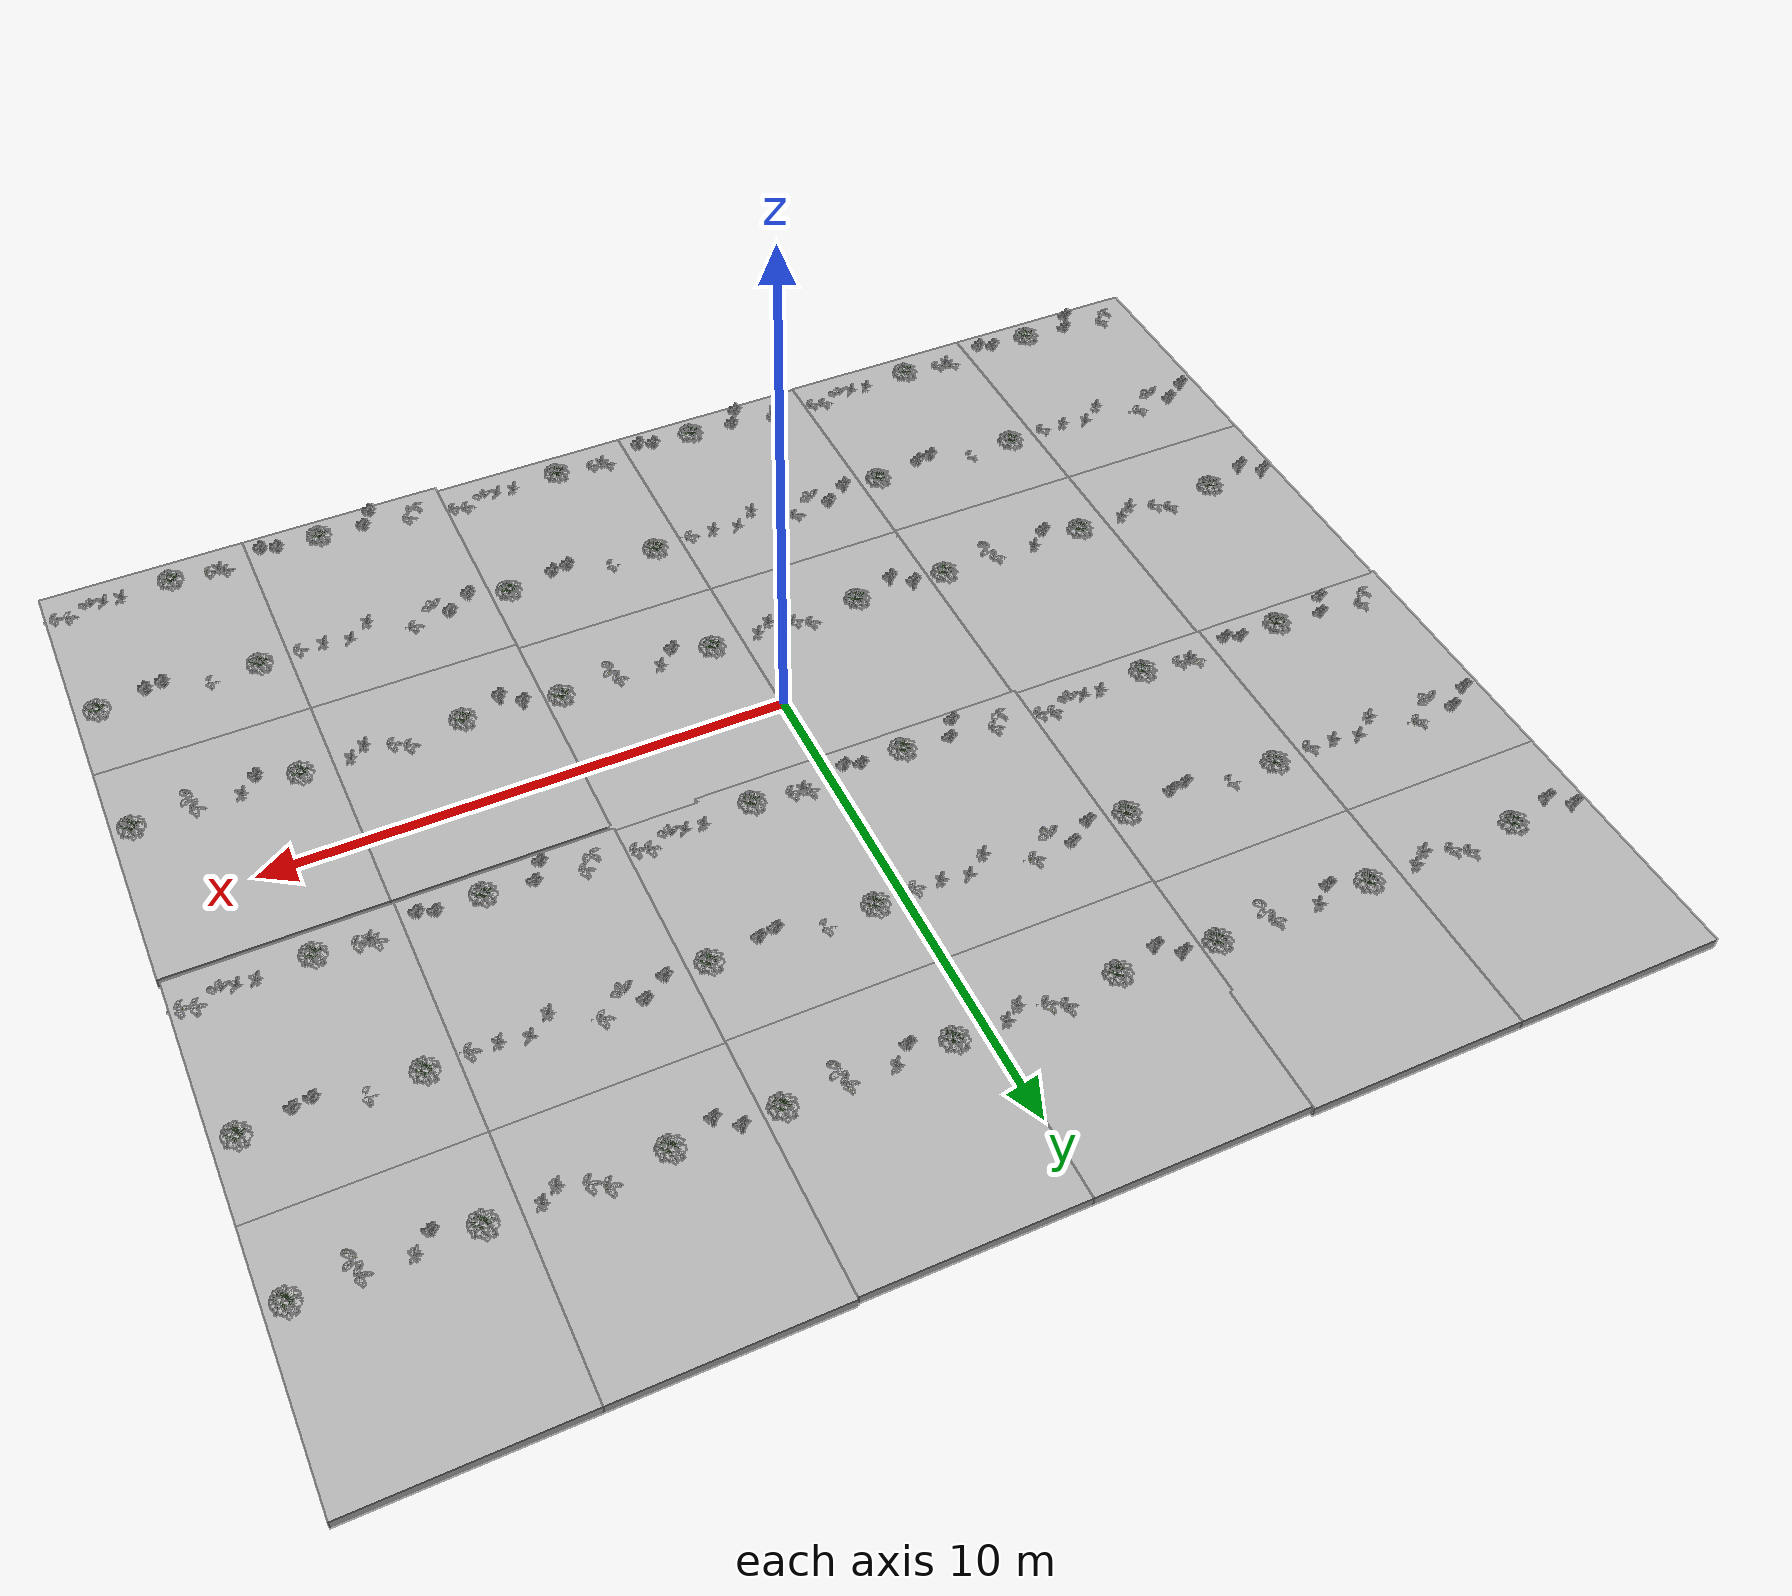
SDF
<?xml version='1.0'?>
<sdf version='1.7'>
  <model name='garden'>
    <model name='patch'>
      <model name='mud_box'>
        <static>1</static>
        <link name='link'>
          <collision name='collision'>
            <geometry>
              <box>
                <size>8 10 0.2</size>
              </box>
            </geometry>
            <surface/>
          </collision>
          <visual name='visual_1'>
            <pose>-2 2.5 0 0 -0 0</pose>
            <cast_shadows>0</cast_shadows>
            <geometry>
              <box>
                <size>4 5 0.2</size>
              </box>
            </geometry>
            <material>
              <script>
                <uri>model://mud_box/materials/scripts</uri>
                <uri>model://mud_box/materials/textures</uri>
                <name>vrc/mud</name>
              </script>
            </material>
          </visual>
          <visual name='visual_2'>
            <pose>2 2.5 0 0 -0 0</pose>
            <cast_shadows>0</cast_shadows>
            <geometry>
              <box>
                <size>4 5 0.2</size>
              </box>
            </geometry>
            <material>
              <script>
                <uri>model://mud_box/materials/scripts</uri>
                <uri>model://mud_box/materials/textures</uri>
                <name>vrc/mud</name>
              </script>
            </material>
          </visual>
          <visual name='visual_3'>
            <pose>2 -2.5 0 0 -0 0</pose>
            <cast_shadows>0</cast_shadows>
            <geometry>
              <box>
                <size>4 5 0.2</size>
              </box>
            </geometry>
            <material>
              <script>
                <uri>model://mud_box/materials/scripts</uri>
                <uri>model://mud_box/materials/textures</uri>
                <name>vrc/mud</name>
              </script>
            </material>
          </visual>
          <visual name='visual_4'>
            <pose>-2 -2.5 0 0 -0 0</pose>
            <cast_shadows>0</cast_shadows>
            <geometry>
              <box>
                <size>4 5 0.2</size>
              </box>
            </geometry>
            <material>
              <script>
                <uri>model://mud_box/materials/scripts</uri>
                <uri>model://mud_box/materials/textures</uri>
                <name>vrc/mud</name>
              </script>
            </material>
          </visual>
        </link>
        <pose>0.092885 1.68872 0.102499 0 -0 0</pose>
      </model>
      <model name='plant_1'>
        <link name='link_0'>
          <inertial>
            <mass>1</mass>
            <inertia>
              <ixx>0.166667</ixx>
              <ixy>0</ixy>
              <ixz>0</ixz>
              <iyy>0.166667</iyy>
              <iyz>0</iyz>
              <izz>0.166667</izz>
            </inertia>
          </inertial>
          <pose>2e-06 -5e-06 0 0 -0 0</pose>
          <visual name='visual'>
            <pose>0 0 0 0 -0 0</pose>
            <geometry>
              <mesh>
                <uri>/../original/Plante+_59/model.dae</uri>
                <scale>0.4 0.4 0.4</scale>
              </mesh>
            </geometry>
            <material>
              <lighting>1</lighting>
              <shader type='pixel'/>
            </material>
            <transparency>0</transparency>
            <cast_shadows>1</cast_shadows>
          </visual>
          <collision name='collision'>
            <laser_retro>0</laser_retro>
            <max_contacts>10</max_contacts>
            <pose>0 0 0 0 -0 0</pose>
            <geometry>
              <mesh>
                <uri>/../original/Plante+_59/model.dae</uri>
                <scale>0.4 0.4 0.4</scale>
              </mesh>
            </geometry>
            <surface>
              <friction>
                <ode>
                  <mu>1</mu>
                  <mu2>1</mu2>
                  <fdir1>0 0 0</fdir1>
                  <slip1>0</slip1>
                  <slip2>0</slip2>
                </ode>
                <torsional>
                  <coefficient>1</coefficient>
                  <patch_radius>0</patch_radius>
                  <surface_radius>0</surface_radius>
                  <use_patch_radius>1</use_patch_radius>
                  <ode>
                    <slip>0</slip>
                  </ode>
                </torsional>
              </friction>
              <bounce>
                <restitution_coefficient>0</restitution_coefficient>
                <threshold>1e+06</threshold>
              </bounce>
              <contact>
                <collide_without_contact>0</collide_without_contact>
                <collide_without_contact_bitmask>1</collide_without_contact_bitmask>
                <collide_bitmask>1</collide_bitmask>
                <ode>
                  <soft_cfm>0</soft_cfm>
                  <soft_erp>0.2</soft_erp>
                  <kp>1e+13</kp>
                  <kd>1</kd>
                  <max_vel>0.01</max_vel>
                  <min_depth>0</min_depth>
                </ode>
                <bullet>
                  <split_impulse>1</split_impulse>
                  <split_impulse_penetration_threshold>-0.01</split_impulse_penetration_threshold>
                  <soft_cfm>0</soft_cfm>
                  <soft_erp>0.2</soft_erp>
                  <kp>1e+13</kp>
                  <kd>1</kd>
                </bullet>
              </contact>
            </surface>
          </collision>
        </link>
        <static>1</static>
        <allow_auto_disable>1</allow_auto_disable>
        <pose>-3.29502 -2.76925 -0.062225 0 -0 0</pose>
      </model>
      <model name='plant_1_0'>
        <link name='link_0'>
          <inertial>
            <mass>1</mass>
            <inertia>
              <ixx>0.166667</ixx>
              <ixy>0</ixy>
              <ixz>0</ixz>
              <iyy>0.166667</iyy>
              <iyz>0</iyz>
              <izz>0.166667</izz>
            </inertia>
          </inertial>
          <pose>2e-06 -5e-06 0 0 -0 0</pose>
          <visual name='visual'>
            <pose>0 0 0 0 -0 0</pose>
            <geometry>
              <mesh>
                <uri>/../original/Plante+_59/model.dae</uri>
                <scale>0.4 0.4 0.4</scale>
              </mesh>
            </geometry>
            <material>
              <lighting>1</lighting>
              <shader type='pixel'/>
            </material>
            <transparency>0</transparency>
            <cast_shadows>1</cast_shadows>
          </visual>
          <collision name='collision'>
            <laser_retro>0</laser_retro>
            <max_contacts>10</max_contacts>
            <pose>0 0 0 0 -0 0</pose>
            <geometry>
              <mesh>
                <uri>/../original/Plante+_59/model.dae</uri>
                <scale>0.4 0.4 0.4</scale>
              </mesh>
            </geometry>
            <surface>
              <friction>
                <ode>
                  <mu>1</mu>
                  <mu2>1</mu2>
                  <fdir1>0 0 0</fdir1>
                  <slip1>0</slip1>
                  <slip2>0</slip2>
                </ode>
                <torsional>
                  <coefficient>1</coefficient>
                  <patch_radius>0</patch_radius>
                  <surface_radius>0</surface_radius>
                  <use_patch_radius>1</use_patch_radius>
                  <ode>
                    <slip>0</slip>
                  </ode>
                </torsional>
              </friction>
              <bounce>
                <restitution_coefficient>0</restitution_coefficient>
                <threshold>1e+06</threshold>
              </bounce>
              <contact>
                <collide_without_contact>0</collide_without_contact>
                <collide_without_contact_bitmask>1</collide_without_contact_bitmask>
                <collide_bitmask>1</collide_bitmask>
                <ode>
                  <soft_cfm>0</soft_cfm>
                  <soft_erp>0.2</soft_erp>
                  <kp>1e+13</kp>
                  <kd>1</kd>
                  <max_vel>0.01</max_vel>
                  <min_depth>0</min_depth>
                </ode>
                <bullet>
                  <split_impulse>1</split_impulse>
                  <split_impulse_penetration_threshold>-0.01</split_impulse_penetration_threshold>
                  <soft_cfm>0</soft_cfm>
                  <soft_erp>0.2</soft_erp>
                  <kp>1e+13</kp>
                  <kd>1</kd>
                </bullet>
              </contact>
            </surface>
          </collision>
        </link>
        <static>1</static>
        <allow_auto_disable>1</allow_auto_disable>
        <pose>-3.59676 -2.83111 -0.052067 0 0 -0.891673</pose>
      </model>
      <model name='plant_1_1'>
        <link name='link_0'>
          <inertial>
            <mass>1</mass>
            <inertia>
              <ixx>0.166667</ixx>
              <ixy>0</ixy>
              <ixz>0</ixz>
              <iyy>0.166667</iyy>
              <iyz>0</iyz>
              <izz>0.166667</izz>
            </inertia>
          </inertial>
          <pose>2e-06 -5e-06 0 0 -0 0</pose>
          <visual name='visual'>
            <pose>0 0 0 0 -0 0</pose>
            <geometry>
              <mesh>
                <uri>/../original/Plante+_59/model.dae</uri>
                <scale>0.4 0.4 0.4</scale>
              </mesh>
            </geometry>
            <material>
              <lighting>1</lighting>
              <shader type='pixel'/>
            </material>
            <transparency>0</transparency>
            <cast_shadows>1</cast_shadows>
          </visual>
          <collision name='collision'>
            <laser_retro>0</laser_retro>
            <max_contacts>10</max_contacts>
            <pose>0 0 0 0 -0 0</pose>
            <geometry>
              <mesh>
                <uri>/../original/Plante+_59/model.dae</uri>
                <scale>0.4 0.4 0.4</scale>
              </mesh>
            </geometry>
            <surface>
              <friction>
                <ode>
                  <mu>1</mu>
                  <mu2>1</mu2>
                  <fdir1>0 0 0</fdir1>
                  <slip1>0</slip1>
                  <slip2>0</slip2>
                </ode>
                <torsional>
                  <coefficient>1</coefficient>
                  <patch_radius>0</patch_radius>
                  <surface_radius>0</surface_radius>
                  <use_patch_radius>1</use_patch_radius>
                  <ode>
                    <slip>0</slip>
                  </ode>
                </torsional>
              </friction>
              <bounce>
                <restitution_coefficient>0</restitution_coefficient>
                <threshold>1e+06</threshold>
              </bounce>
              <contact>
                <collide_without_contact>0</collide_without_contact>
                <collide_without_contact_bitmask>1</collide_without_contact_bitmask>
                <collide_bitmask>1</collide_bitmask>
                <ode>
                  <soft_cfm>0</soft_cfm>
                  <soft_erp>0.2</soft_erp>
                  <kp>1e+13</kp>
                  <kd>1</kd>
                  <max_vel>0.01</max_vel>
                  <min_depth>0</min_depth>
                </ode>
                <bullet>
                  <split_impulse>1</split_impulse>
                  <split_impulse_penetration_threshold>-0.01</split_impulse_penetration_threshold>
                  <soft_cfm>0</soft_cfm>
                  <soft_erp>0.2</soft_erp>
                  <kp>1e+13</kp>
                  <kd>1</kd>
                </bullet>
              </contact>
            </surface>
          </collision>
        </link>
        <static>1</static>
        <allow_auto_disable>1</allow_auto_disable>
        <pose>3.71588 -2.79107 -0.063352 0 -0 0</pose>
      </model>
      <model name='plant_1_10'>
        <link name='link_0'>
          <inertial>
            <mass>1</mass>
            <inertia>
              <ixx>0.166667</ixx>
              <ixy>0</ixy>
              <ixz>0</ixz>
              <iyy>0.166667</iyy>
              <iyz>0</iyz>
              <izz>0.166667</izz>
            </inertia>
          </inertial>
          <pose>2e-06 -5e-06 0 0 -0 0</pose>
          <visual name='visual'>
            <pose>0 0 0 0 -0 0</pose>
            <geometry>
              <mesh>
                <uri>/../original/Plante+_59/model.dae</uri>
                <scale>0.4 0.4 0.4</scale>
              </mesh>
            </geometry>
            <material>
              <lighting>1</lighting>
              <shader type='pixel'/>
            </material>
            <transparency>0</transparency>
            <cast_shadows>1</cast_shadows>
          </visual>
          <collision name='collision'>
            <laser_retro>0</laser_retro>
            <max_contacts>10</max_contacts>
            <pose>0 0 0 0 -0 0</pose>
            <geometry>
              <mesh>
                <uri>/../original/Plante+_59/model.dae</uri>
                <scale>0.4 0.4 0.4</scale>
              </mesh>
            </geometry>
            <surface>
              <friction>
                <ode>
                  <mu>1</mu>
                  <mu2>1</mu2>
                  <fdir1>0 0 0</fdir1>
                  <slip1>0</slip1>
                  <slip2>0</slip2>
                </ode>
                <torsional>
                  <coefficient>1</coefficient>
                  <patch_radius>0</patch_radius>
                  <surface_radius>0</surface_radius>
                  <use_patch_radius>1</use_patch_radius>
                  <ode>
                    <slip>0</slip>
                  </ode>
                </torsional>
              </friction>
              <bounce>
                <restitution_coefficient>0</restitution_coefficient>
                <threshold>1e+06</threshold>
              </bounce>
              <contact>
                <collide_without_contact>0</collide_without_contact>
                <collide_without_contact_bitmask>1</collide_without_contact_bitmask>
                <collide_bitmask>1</collide_bitmask>
                <ode>
                  <soft_cfm>0</soft_cfm>
                  <soft_erp>0.2</soft_erp>
                  <kp>1e+13</kp>
                  <kd>1</kd>
                  <max_vel>0.01</max_vel>
                  <min_depth>0</min_depth>
                </ode>
                <bullet>
                  <split_impulse>1</split_impulse>
                  <split_impulse_penetration_threshold>-0.01</split_impulse_penetration_threshold>
                  <soft_cfm>0</soft_cfm>
                  <soft_erp>0.2</soft_erp>
                  <kp>1e+13</kp>
                  <kd>1</kd>
                </bullet>
              </contact>
            </surface>
          </collision>
        </link>
        <static>1</static>
        <allow_auto_disable>1</allow_auto_disable>
        <pose>-1.19461 3.06553 -0.050875 0 -0 0</pose>
      </model>
      <model name='plant_1_11'>
        <link name='link_0'>
          <inertial>
            <mass>1</mass>
            <inertia>
              <ixx>0.166667</ixx>
              <ixy>0</ixy>
              <ixz>0</ixz>
              <iyy>0.166667</iyy>
              <iyz>0</iyz>
              <izz>0.166667</izz>
            </inertia>
          </inertial>
          <pose>2e-06 -5e-06 0 0 -0 0</pose>
          <visual name='visual'>
            <pose>0 0 0 0 -0 0</pose>
            <geometry>
              <mesh>
                <uri>/../original/Plante+_59/model.dae</uri>
                <scale>0.4 0.4 0.4</scale>
              </mesh>
            </geometry>
            <material>
              <lighting>1</lighting>
              <shader type='pixel'/>
            </material>
            <transparency>0</transparency>
            <cast_shadows>1</cast_shadows>
          </visual>
          <collision name='collision'>
            <laser_retro>0</laser_retro>
            <max_contacts>10</max_contacts>
            <pose>0 0 0 0 -0 0</pose>
            <geometry>
              <mesh>
                <uri>/../original/Plante+_59/model.dae</uri>
                <scale>0.4 0.4 0.4</scale>
              </mesh>
            </geometry>
            <surface>
              <friction>
                <ode>
                  <mu>1</mu>
                  <mu2>1</mu2>
                  <fdir1>0 0 0</fdir1>
                  <slip1>0</slip1>
                  <slip2>0</slip2>
                </ode>
                <torsional>
                  <coefficient>1</coefficient>
                  <patch_radius>0</patch_radius>
                  <surface_radius>0</surface_radius>
                  <use_patch_radius>1</use_patch_radius>
                  <ode>
                    <slip>0</slip>
                  </ode>
                </torsional>
              </friction>
              <bounce>
                <restitution_coefficient>0</restitution_coefficient>
                <threshold>1e+06</threshold>
              </bounce>
              <contact>
                <collide_without_contact>0</collide_without_contact>
                <collide_without_contact_bitmask>1</collide_without_contact_bitmask>
                <collide_bitmask>1</collide_bitmask>
                <ode>
                  <soft_cfm>0</soft_cfm>
                  <soft_erp>0.2</soft_erp>
                  <kp>1e+13</kp>
                  <kd>1</kd>
                  <max_vel>0.01</max_vel>
                  <min_depth>0</min_depth>
                </ode>
                <bullet>
                  <split_impulse>1</split_impulse>
                  <split_impulse_penetration_threshold>-0.01</split_impulse_penetration_threshold>
                  <soft_cfm>0</soft_cfm>
                  <soft_erp>0.2</soft_erp>
                  <kp>1e+13</kp>
                  <kd>1</kd>
                </bullet>
              </contact>
            </surface>
          </collision>
        </link>
        <static>1</static>
        <allow_auto_disable>1</allow_auto_disable>
        <pose>-1.46186 3.23598 -0.051207 0 -0 0</pose>
      </model>
      <model name='plant_1_12'>
        <link name='link_0'>
          <inertial>
            <mass>1</mass>
            <inertia>
              <ixx>0.166667</ixx>
              <ixy>0</ixy>
              <ixz>0</ixz>
              <iyy>0.166667</iyy>
              <iyz>0</iyz>
              <izz>0.166667</izz>
            </inertia>
          </inertial>
          <pose>2e-06 -5e-06 0 0 -0 0</pose>
          <visual name='visual'>
            <pose>0 0 0 0 -0 0</pose>
            <geometry>
              <mesh>
                <uri>/../original/Plante+_59/model.dae</uri>
                <scale>0.4 0.4 0.4</scale>
              </mesh>
            </geometry>
            <material>
              <lighting>1</lighting>
              <shader type='pixel'/>
            </material>
            <transparency>0</transparency>
            <cast_shadows>1</cast_shadows>
          </visual>
          <collision name='collision'>
            <laser_retro>0</laser_retro>
            <max_contacts>10</max_contacts>
            <pose>0 0 0 0 -0 0</pose>
            <geometry>
              <mesh>
                <uri>/../original/Plante+_59/model.dae</uri>
                <scale>0.4 0.4 0.4</scale>
              </mesh>
            </geometry>
            <surface>
              <friction>
                <ode>
                  <mu>1</mu>
                  <mu2>1</mu2>
                  <fdir1>0 0 0</fdir1>
                  <slip1>0</slip1>
                  <slip2>0</slip2>
                </ode>
                <torsional>
                  <coefficient>1</coefficient>
                  <patch_radius>0</patch_radius>
                  <surface_radius>0</surface_radius>
                  <use_patch_radius>1</use_patch_radius>
                  <ode>
                    <slip>0</slip>
                  </ode>
                </torsional>
              </friction>
              <bounce>
                <restitution_coefficient>0</restitution_coefficient>
                <threshold>1e+06</threshold>
              </bounce>
              <contact>
                <collide_without_contact>0</collide_without_contact>
                <collide_without_contact_bitmask>1</collide_without_contact_bitmask>
                <collide_bitmask>1</collide_bitmask>
                <ode>
                  <soft_cfm>0</soft_cfm>
                  <soft_erp>0.2</soft_erp>
                  <kp>1e+13</kp>
                  <kd>1</kd>
                  <max_vel>0.01</max_vel>
                  <min_depth>0</min_depth>
                </ode>
                <bullet>
                  <split_impulse>1</split_impulse>
                  <split_impulse_penetration_threshold>-0.01</split_impulse_penetration_threshold>
                  <soft_cfm>0</soft_cfm>
                  <soft_erp>0.2</soft_erp>
                  <kp>1e+13</kp>
                  <kd>1</kd>
                </bullet>
              </contact>
            </surface>
          </collision>
        </link>
        <static>1</static>
        <allow_auto_disable>1</allow_auto_disable>
        <pose>2.71078 3.26891 -0.059253 0 0 -2.58097</pose>
      </model>
      <model name='plant_1_13'>
        <link name='link_0'>
          <inertial>
            <mass>1</mass>
            <inertia>
              <ixx>0.166667</ixx>
              <ixy>0</ixy>
              <ixz>0</ixz>
              <iyy>0.166667</iyy>
              <iyz>0</iyz>
              <izz>0.166667</izz>
            </inertia>
          </inertial>
          <pose>2e-06 -5e-06 0 0 -0 0</pose>
          <visual name='visual'>
            <pose>0 0 0 0 -0 0</pose>
            <geometry>
              <mesh>
                <uri>/../original/Plante+_59/model.dae</uri>
                <scale>0.4 0.4 0.4</scale>
              </mesh>
            </geometry>
            <material>
              <lighting>1</lighting>
              <shader type='pixel'/>
            </material>
            <transparency>0</transparency>
            <cast_shadows>1</cast_shadows>
          </visual>
          <collision name='collision'>
            <laser_retro>0</laser_retro>
            <max_contacts>10</max_contacts>
            <pose>0 0 0 0 -0 0</pose>
            <geometry>
              <mesh>
                <uri>/../original/Plante+_59/model.dae</uri>
                <scale>0.4 0.4 0.4</scale>
              </mesh>
            </geometry>
            <surface>
              <friction>
                <ode>
                  <mu>1</mu>
                  <mu2>1</mu2>
                  <fdir1>0 0 0</fdir1>
                  <slip1>0</slip1>
                  <slip2>0</slip2>
                </ode>
                <torsional>
                  <coefficient>1</coefficient>
                  <patch_radius>0</patch_radius>
                  <surface_radius>0</surface_radius>
                  <use_patch_radius>1</use_patch_radius>
                  <ode>
                    <slip>0</slip>
                  </ode>
                </torsional>
              </friction>
              <bounce>
                <restitution_coefficient>0</restitution_coefficient>
                <threshold>1e+06</threshold>
              </bounce>
              <contact>
                <collide_without_contact>0</collide_without_contact>
                <collide_without_contact_bitmask>1</collide_without_contact_bitmask>
                <collide_bitmask>1</collide_bitmask>
                <ode>
                  <soft_cfm>0</soft_cfm>
                  <soft_erp>0.2</soft_erp>
                  <kp>1e+13</kp>
                  <kd>1</kd>
                  <max_vel>0.01</max_vel>
                  <min_depth>0</min_depth>
                </ode>
                <bullet>
                  <split_impulse>1</split_impulse>
                  <split_impulse_penetration_threshold>-0.01</split_impulse_penetration_threshold>
                  <soft_cfm>0</soft_cfm>
                  <soft_erp>0.2</soft_erp>
                  <kp>1e+13</kp>
                  <kd>1</kd>
                </bullet>
              </contact>
            </surface>
          </collision>
        </link>
        <static>1</static>
        <allow_auto_disable>1</allow_auto_disable>
        <pose>2.4267 3.09966 -0.054788 0 -0 0</pose>
      </model>
      <model name='plant_1_2'>
        <link name='link_0'>
          <inertial>
            <mass>1</mass>
            <inertia>
              <ixx>0.166667</ixx>
              <ixy>0</ixy>
              <ixz>0</ixz>
              <iyy>0.166667</iyy>
              <iyz>0</iyz>
              <izz>0.166667</izz>
            </inertia>
          </inertial>
          <pose>2e-06 -5e-06 0 0 -0 0</pose>
          <visual name='visual'>
            <pose>0 0 0 0 -0 0</pose>
            <geometry>
              <mesh>
                <uri>/../original/Plante+_59/model.dae</uri>
                <scale>0.4 0.4 0.4</scale>
              </mesh>
            </geometry>
            <material>
              <lighting>1</lighting>
              <shader type='pixel'/>
            </material>
            <transparency>0</transparency>
            <cast_shadows>1</cast_shadows>
          </visual>
          <collision name='collision'>
            <laser_retro>0</laser_retro>
            <max_contacts>10</max_contacts>
            <pose>0 0 0 0 -0 0</pose>
            <geometry>
              <mesh>
                <uri>/../original/Plante+_59/model.dae</uri>
                <scale>0.4 0.4 0.4</scale>
              </mesh>
            </geometry>
            <surface>
              <friction>
                <ode>
                  <mu>1</mu>
                  <mu2>1</mu2>
                  <fdir1>0 0 0</fdir1>
                  <slip1>0</slip1>
                  <slip2>0</slip2>
                </ode>
                <torsional>
                  <coefficient>1</coefficient>
                  <patch_radius>0</patch_radius>
                  <surface_radius>0</surface_radius>
                  <use_patch_radius>1</use_patch_radius>
                  <ode>
                    <slip>0</slip>
                  </ode>
                </torsional>
              </friction>
              <bounce>
                <restitution_coefficient>0</restitution_coefficient>
                <threshold>1e+06</threshold>
              </bounce>
              <contact>
                <collide_without_contact>0</collide_without_contact>
                <collide_without_contact_bitmask>1</collide_without_contact_bitmask>
                <collide_bitmask>1</collide_bitmask>
                <ode>
                  <soft_cfm>0</soft_cfm>
                  <soft_erp>0.2</soft_erp>
                  <kp>1e+13</kp>
                  <kd>1</kd>
                  <max_vel>0.01</max_vel>
                  <min_depth>0</min_depth>
                </ode>
                <bullet>
                  <split_impulse>1</split_impulse>
                  <split_impulse_penetration_threshold>-0.01</split_impulse_penetration_threshold>
                  <soft_cfm>0</soft_cfm>
                  <soft_erp>0.2</soft_erp>
                  <kp>1e+13</kp>
                  <kd>1</kd>
                </bullet>
              </contact>
            </surface>
          </collision>
        </link>
        <static>1</static>
        <allow_auto_disable>1</allow_auto_disable>
        <pose>3.46744 -2.72252 -0.064336 0 -0 0</pose>
      </model>
      <model name='plant_1_3'>
        <link name='link_0'>
          <inertial>
            <mass>1</mass>
            <inertia>
              <ixx>0.166667</ixx>
              <ixy>0</ixy>
              <ixz>0</ixz>
              <iyy>0.166667</iyy>
              <iyz>0</iyz>
              <izz>0.166667</izz>
            </inertia>
          </inertial>
          <pose>2e-06 -5e-06 0 0 -0 0</pose>
          <visual name='visual'>
            <pose>0 0 0 0 -0 0</pose>
            <geometry>
              <mesh>
                <uri>/../original/Plante+_59/model.dae</uri>
                <scale>0.4 0.4 0.4</scale>
              </mesh>
            </geometry>
            <material>
              <lighting>1</lighting>
              <shader type='pixel'/>
            </material>
            <transparency>0</transparency>
            <cast_shadows>1</cast_shadows>
          </visual>
          <collision name='collision'>
            <laser_retro>0</laser_retro>
            <max_contacts>10</max_contacts>
            <pose>0 0 0 0 -0 0</pose>
            <geometry>
              <mesh>
                <uri>/../original/Plante+_59/model.dae</uri>
                <scale>0.4 0.4 0.4</scale>
              </mesh>
            </geometry>
            <surface>
              <friction>
                <ode>
                  <mu>1</mu>
                  <mu2>1</mu2>
                  <fdir1>0 0 0</fdir1>
                  <slip1>0</slip1>
                  <slip2>0</slip2>
                </ode>
                <torsional>
                  <coefficient>1</coefficient>
                  <patch_radius>0</patch_radius>
                  <surface_radius>0</surface_radius>
                  <use_patch_radius>1</use_patch_radius>
                  <ode>
                    <slip>0</slip>
                  </ode>
                </torsional>
              </friction>
              <bounce>
                <restitution_coefficient>0</restitution_coefficient>
                <threshold>1e+06</threshold>
              </bounce>
              <contact>
                <collide_without_contact>0</collide_without_contact>
                <collide_without_contact_bitmask>1</collide_without_contact_bitmask>
                <collide_bitmask>1</collide_bitmask>
                <ode>
                  <soft_cfm>0</soft_cfm>
                  <soft_erp>0.2</soft_erp>
                  <kp>1e+13</kp>
                  <kd>1</kd>
                  <max_vel>0.01</max_vel>
                  <min_depth>0</min_depth>
                </ode>
                <bullet>
                  <split_impulse>1</split_impulse>
                  <split_impulse_penetration_threshold>-0.01</split_impulse_penetration_threshold>
                  <soft_cfm>0</soft_cfm>
                  <soft_erp>0.2</soft_erp>
                  <kp>1e+13</kp>
                  <kd>1</kd>
                </bullet>
              </contact>
            </surface>
          </collision>
        </link>
        <static>1</static>
        <allow_auto_disable>1</allow_auto_disable>
        <pose>3.42739 -2.95309 -0.068036 0 -0 1.60626</pose>
      </model>
      <model name='plant_1_4'>
        <link name='link_0'>
          <inertial>
            <mass>1</mass>
            <inertia>
              <ixx>0.166667</ixx>
              <ixy>0</ixy>
              <ixz>0</ixz>
              <iyy>0.166667</iyy>
              <iyz>0</iyz>
              <izz>0.166667</izz>
            </inertia>
          </inertial>
          <pose>2e-06 -5e-06 0 0 -0 0</pose>
          <visual name='visual'>
            <pose>0 0 0 0 -0 0</pose>
            <geometry>
              <mesh>
                <uri>/../original/Plante+_59/model.dae</uri>
                <scale>0.4 0.4 0.4</scale>
              </mesh>
            </geometry>
            <material>
              <lighting>1</lighting>
              <shader type='pixel'/>
            </material>
            <transparency>0</transparency>
            <cast_shadows>1</cast_shadows>
          </visual>
          <collision name='collision'>
            <laser_retro>0</laser_retro>
            <max_contacts>10</max_contacts>
            <pose>0 0 0 0 -0 0</pose>
            <geometry>
              <mesh>
                <uri>/../original/Plante+_59/model.dae</uri>
                <scale>0.4 0.4 0.4</scale>
              </mesh>
            </geometry>
            <surface>
              <friction>
                <ode>
                  <mu>1</mu>
                  <mu2>1</mu2>
                  <fdir1>0 0 0</fdir1>
                  <slip1>0</slip1>
                  <slip2>0</slip2>
                </ode>
                <torsional>
                  <coefficient>1</coefficient>
                  <patch_radius>0</patch_radius>
                  <surface_radius>0</surface_radius>
                  <use_patch_radius>1</use_patch_radius>
                  <ode>
                    <slip>0</slip>
                  </ode>
                </torsional>
              </friction>
              <bounce>
                <restitution_coefficient>0</restitution_coefficient>
                <threshold>1e+06</threshold>
              </bounce>
              <contact>
                <collide_without_contact>0</collide_without_contact>
                <collide_without_contact_bitmask>1</collide_without_contact_bitmask>
                <collide_bitmask>1</collide_bitmask>
                <ode>
                  <soft_cfm>0</soft_cfm>
                  <soft_erp>0.2</soft_erp>
                  <kp>1e+13</kp>
                  <kd>1</kd>
                  <max_vel>0.01</max_vel>
                  <min_depth>0</min_depth>
                </ode>
                <bullet>
                  <split_impulse>1</split_impulse>
                  <split_impulse_penetration_threshold>-0.01</split_impulse_penetration_threshold>
                  <soft_cfm>0</soft_cfm>
                  <soft_erp>0.2</soft_erp>
                  <kp>1e+13</kp>
                  <kd>1</kd>
                </bullet>
              </contact>
            </surface>
          </collision>
        </link>
        <static>1</static>
        <allow_auto_disable>1</allow_auto_disable>
        <pose>0.708825 -2.86905 -0.059704 0 -0 0</pose>
      </model>
      <model name='plant_1_5'>
        <link name='link_0'>
          <inertial>
            <mass>1</mass>
            <inertia>
              <ixx>0.166667</ixx>
              <ixy>0</ixy>
              <ixz>0</ixz>
              <iyy>0.166667</iyy>
              <iyz>0</iyz>
              <izz>0.166667</izz>
            </inertia>
          </inertial>
          <pose>2e-06 -5e-06 0 0 -0 0</pose>
          <visual name='visual'>
            <pose>0 0 0 0 -0 0</pose>
            <geometry>
              <mesh>
                <uri>/../original/Plante+_59/model.dae</uri>
                <scale>0.4 0.4 0.4</scale>
              </mesh>
            </geometry>
            <material>
              <lighting>1</lighting>
              <shader type='pixel'/>
            </material>
            <transparency>0</transparency>
            <cast_shadows>1</cast_shadows>
          </visual>
          <collision name='collision'>
            <laser_retro>0</laser_retro>
            <max_contacts>10</max_contacts>
            <pose>0 0 0 0 -0 0</pose>
            <geometry>
              <mesh>
                <uri>/../original/Plante+_59/model.dae</uri>
                <scale>0.4 0.4 0.4</scale>
              </mesh>
            </geometry>
            <surface>
              <friction>
                <ode>
                  <mu>1</mu>
                  <mu2>1</mu2>
                  <fdir1>0 0 0</fdir1>
                  <slip1>0</slip1>
                  <slip2>0</slip2>
                </ode>
                <torsional>
                  <coefficient>1</coefficient>
                  <patch_radius>0</patch_radius>
                  <surface_radius>0</surface_radius>
                  <use_patch_radius>1</use_patch_radius>
                  <ode>
                    <slip>0</slip>
                  </ode>
                </torsional>
              </friction>
              <bounce>
                <restitution_coefficient>0</restitution_coefficient>
                <threshold>1e+06</threshold>
              </bounce>
              <contact>
                <collide_without_contact>0</collide_without_contact>
                <collide_without_contact_bitmask>1</collide_without_contact_bitmask>
                <collide_bitmask>1</collide_bitmask>
                <ode>
                  <soft_cfm>0</soft_cfm>
                  <soft_erp>0.2</soft_erp>
                  <kp>1e+13</kp>
                  <kd>1</kd>
                  <max_vel>0.01</max_vel>
                  <min_depth>0</min_depth>
                </ode>
                <bullet>
                  <split_impulse>1</split_impulse>
                  <split_impulse_penetration_threshold>-0.01</split_impulse_penetration_threshold>
                  <soft_cfm>0</soft_cfm>
                  <soft_erp>0.2</soft_erp>
                  <kp>1e+13</kp>
                  <kd>1</kd>
                </bullet>
              </contact>
            </surface>
          </collision>
        </link>
        <static>1</static>
        <allow_auto_disable>1</allow_auto_disable>
        <pose>0.391171 -2.78384 -0.063689 0 -0 0</pose>
      </model>
      <model name='plant_1_6'>
        <link name='link_0'>
          <inertial>
            <mass>1</mass>
            <inertia>
              <ixx>0.166667</ixx>
              <ixy>0</ixy>
              <ixz>0</ixz>
              <iyy>0.166667</iyy>
              <iyz>0</iyz>
              <izz>0.166667</izz>
            </inertia>
          </inertial>
          <pose>2e-06 -5e-06 0 0 -0 0</pose>
          <visual name='visual'>
            <pose>0 0 0 0 -0 0</pose>
            <geometry>
              <mesh>
                <uri>/../original/Plante+_59/model.dae</uri>
                <scale>0.4 0.4 0.4</scale>
              </mesh>
            </geometry>
            <material>
              <lighting>1</lighting>
              <shader type='pixel'/>
            </material>
            <transparency>0</transparency>
            <cast_shadows>1</cast_shadows>
          </visual>
          <collision name='collision'>
            <laser_retro>0</laser_retro>
            <max_contacts>10</max_contacts>
            <pose>0 0 0 0 -0 0</pose>
            <geometry>
              <mesh>
                <uri>/../original/Plante+_59/model.dae</uri>
                <scale>0.4 0.4 0.4</scale>
              </mesh>
            </geometry>
            <surface>
              <friction>
                <ode>
                  <mu>1</mu>
                  <mu2>1</mu2>
                  <fdir1>0 0 0</fdir1>
                  <slip1>0</slip1>
                  <slip2>0</slip2>
                </ode>
                <torsional>
                  <coefficient>1</coefficient>
                  <patch_radius>0</patch_radius>
                  <surface_radius>0</surface_radius>
                  <use_patch_radius>1</use_patch_radius>
                  <ode>
                    <slip>0</slip>
                  </ode>
                </torsional>
              </friction>
              <bounce>
                <restitution_coefficient>0</restitution_coefficient>
                <threshold>1e+06</threshold>
              </bounce>
              <contact>
                <collide_without_contact>0</collide_without_contact>
                <collide_without_contact_bitmask>1</collide_without_contact_bitmask>
                <collide_bitmask>1</collide_bitmask>
                <ode>
                  <soft_cfm>0</soft_cfm>
                  <soft_erp>0.2</soft_erp>
                  <kp>1e+13</kp>
                  <kd>1</kd>
                  <max_vel>0.01</max_vel>
                  <min_depth>0</min_depth>
                </ode>
                <bullet>
                  <split_impulse>1</split_impulse>
                  <split_impulse_penetration_threshold>-0.01</split_impulse_penetration_threshold>
                  <soft_cfm>0</soft_cfm>
                  <soft_erp>0.2</soft_erp>
                  <kp>1e+13</kp>
                  <kd>1</kd>
                </bullet>
              </contact>
            </surface>
          </collision>
        </link>
        <static>1</static>
        <allow_auto_disable>1</allow_auto_disable>
        <pose>-0.301128 -0.006772 -0.049917 0 -0 0</pose>
      </model>
      <model name='plant_1_7'>
        <link name='link_0'>
          <inertial>
            <mass>1</mass>
            <inertia>
              <ixx>0.166667</ixx>
              <ixy>0</ixy>
              <ixz>0</ixz>
              <iyy>0.166667</iyy>
              <iyz>0</iyz>
              <izz>0.166667</izz>
            </inertia>
          </inertial>
          <pose>2e-06 -5e-06 0 0 -0 0</pose>
          <visual name='visual'>
            <pose>0 0 0 0 -0 0</pose>
            <geometry>
              <mesh>
                <uri>/../original/Plante+_59/model.dae</uri>
                <scale>0.4 0.4 0.4</scale>
              </mesh>
            </geometry>
            <material>
              <lighting>1</lighting>
              <shader type='pixel'/>
            </material>
            <transparency>0</transparency>
            <cast_shadows>1</cast_shadows>
          </visual>
          <collision name='collision'>
            <laser_retro>0</laser_retro>
            <max_contacts>10</max_contacts>
            <pose>0 0 0 0 -0 0</pose>
            <geometry>
              <mesh>
                <uri>/../original/Plante+_59/model.dae</uri>
                <scale>0.4 0.4 0.4</scale>
              </mesh>
            </geometry>
            <surface>
              <friction>
                <ode>
                  <mu>1</mu>
                  <mu2>1</mu2>
                  <fdir1>0 0 0</fdir1>
                  <slip1>0</slip1>
                  <slip2>0</slip2>
                </ode>
                <torsional>
                  <coefficient>1</coefficient>
                  <patch_radius>0</patch_radius>
                  <surface_radius>0</surface_radius>
                  <use_patch_radius>1</use_patch_radius>
                  <ode>
                    <slip>0</slip>
                  </ode>
                </torsional>
              </friction>
              <bounce>
                <restitution_coefficient>0</restitution_coefficient>
                <threshold>1e+06</threshold>
              </bounce>
              <contact>
                <collide_without_contact>0</collide_without_contact>
                <collide_without_contact_bitmask>1</collide_without_contact_bitmask>
                <collide_bitmask>1</collide_bitmask>
                <ode>
                  <soft_cfm>0</soft_cfm>
                  <soft_erp>0.2</soft_erp>
                  <kp>1e+13</kp>
                  <kd>1</kd>
                  <max_vel>0.01</max_vel>
                  <min_depth>0</min_depth>
                </ode>
                <bullet>
                  <split_impulse>1</split_impulse>
                  <split_impulse_penetration_threshold>-0.01</split_impulse_penetration_threshold>
                  <soft_cfm>0</soft_cfm>
                  <soft_erp>0.2</soft_erp>
                  <kp>1e+13</kp>
                  <kd>1</kd>
                </bullet>
              </contact>
            </surface>
          </collision>
        </link>
        <static>1</static>
        <allow_auto_disable>1</allow_auto_disable>
        <pose>1.4193 0.089699 -0.085343 0 -0 0</pose>
      </model>
      <model name='plant_1_8'>
        <link name='link_0'>
          <inertial>
            <mass>1</mass>
            <inertia>
              <ixx>0.166667</ixx>
              <ixy>0</ixy>
              <ixz>0</ixz>
              <iyy>0.166667</iyy>
              <iyz>0</iyz>
              <izz>0.166667</izz>
            </inertia>
          </inertial>
          <pose>2e-06 -5e-06 0 0 -0 0</pose>
          <visual name='visual'>
            <pose>0 0 0 0 -0 0</pose>
            <geometry>
              <mesh>
                <uri>/../original/Plante+_59/model.dae</uri>
                <scale>0.4 0.4 0.4</scale>
              </mesh>
            </geometry>
            <material>
              <lighting>1</lighting>
              <shader type='pixel'/>
            </material>
            <transparency>0</transparency>
            <cast_shadows>1</cast_shadows>
          </visual>
          <collision name='collision'>
            <laser_retro>0</laser_retro>
            <max_contacts>10</max_contacts>
            <pose>0 0 0 0 -0 0</pose>
            <geometry>
              <mesh>
                <uri>/../original/Plante+_59/model.dae</uri>
                <scale>0.4 0.4 0.4</scale>
              </mesh>
            </geometry>
            <surface>
              <friction>
                <ode>
                  <mu>1</mu>
                  <mu2>1</mu2>
                  <fdir1>0 0 0</fdir1>
                  <slip1>0</slip1>
                  <slip2>0</slip2>
                </ode>
                <torsional>
                  <coefficient>1</coefficient>
                  <patch_radius>0</patch_radius>
                  <surface_radius>0</surface_radius>
                  <use_patch_radius>1</use_patch_radius>
                  <ode>
                    <slip>0</slip>
                  </ode>
                </torsional>
              </friction>
              <bounce>
                <restitution_coefficient>0</restitution_coefficient>
                <threshold>1e+06</threshold>
              </bounce>
              <contact>
                <collide_without_contact>0</collide_without_contact>
                <collide_without_contact_bitmask>1</collide_without_contact_bitmask>
                <collide_bitmask>1</collide_bitmask>
                <ode>
                  <soft_cfm>0</soft_cfm>
                  <soft_erp>0.2</soft_erp>
                  <kp>1e+13</kp>
                  <kd>1</kd>
                  <max_vel>0.01</max_vel>
                  <min_depth>0</min_depth>
                </ode>
                <bullet>
                  <split_impulse>1</split_impulse>
                  <split_impulse_penetration_threshold>-0.01</split_impulse_penetration_threshold>
                  <soft_cfm>0</soft_cfm>
                  <soft_erp>0.2</soft_erp>
                  <kp>1e+13</kp>
                  <kd>1</kd>
                </bullet>
              </contact>
            </surface>
          </collision>
        </link>
        <static>1</static>
        <allow_auto_disable>1</allow_auto_disable>
        <pose>-2.50667 -0.0585 -0.05856 0 -0 1.98818</pose>
      </model>
      <model name='plant_1_9'>
        <link name='link_0'>
          <inertial>
            <mass>1</mass>
            <inertia>
              <ixx>0.166667</ixx>
              <ixy>0</ixy>
              <ixz>0</ixz>
              <iyy>0.166667</iyy>
              <iyz>0</iyz>
              <izz>0.166667</izz>
            </inertia>
          </inertial>
          <pose>2e-06 -5e-06 0 0 -0 0</pose>
          <visual name='visual'>
            <pose>0 0 0 0 -0 0</pose>
            <geometry>
              <mesh>
                <uri>/../original/Plante+_59/model.dae</uri>
                <scale>0.4 0.4 0.4</scale>
              </mesh>
            </geometry>
            <material>
              <lighting>1</lighting>
              <shader type='pixel'/>
            </material>
            <transparency>0</transparency>
            <cast_shadows>1</cast_shadows>
          </visual>
          <collision name='collision'>
            <laser_retro>0</laser_retro>
            <max_contacts>10</max_contacts>
            <pose>0 0 0 0 -0 0</pose>
            <geometry>
              <mesh>
                <uri>/../original/Plante+_59/model.dae</uri>
                <scale>0.4 0.4 0.4</scale>
              </mesh>
            </geometry>
            <surface>
              <friction>
                <ode>
                  <mu>1</mu>
                  <mu2>1</mu2>
                  <fdir1>0 0 0</fdir1>
                  <slip1>0</slip1>
                  <slip2>0</slip2>
                </ode>
                <torsional>
                  <coefficient>1</coefficient>
                  <patch_radius>0</patch_radius>
                  <surface_radius>0</surface_radius>
                  <use_patch_radius>1</use_patch_radius>
                  <ode>
                    <slip>0</slip>
                  </ode>
                </torsional>
              </friction>
              <bounce>
                <restitution_coefficient>0</restitution_coefficient>
                <threshold>1e+06</threshold>
              </bounce>
              <contact>
                <collide_without_contact>0</collide_without_contact>
                <collide_without_contact_bitmask>1</collide_without_contact_bitmask>
                <collide_bitmask>1</collide_bitmask>
                <ode>
                  <soft_cfm>0</soft_cfm>
                  <soft_erp>0.2</soft_erp>
                  <kp>1e+13</kp>
                  <kd>1</kd>
                  <max_vel>0.01</max_vel>
                  <min_depth>0</min_depth>
                </ode>
                <bullet>
                  <split_impulse>1</split_impulse>
                  <split_impulse_penetration_threshold>-0.01</split_impulse_penetration_threshold>
                  <soft_cfm>0</soft_cfm>
                  <soft_erp>0.2</soft_erp>
                  <kp>1e+13</kp>
                  <kd>1</kd>
                </bullet>
              </contact>
            </surface>
          </collision>
        </link>
        <static>1</static>
        <allow_auto_disable>1</allow_auto_disable>
        <pose>-2.46764 0.289918 -0.043534 0 -0 0</pose>
      </model>
      <model name='plant_2'>
        <link name='link_5'>
          <inertial>
            <mass>1</mass>
            <inertia>
              <ixx>0.166667</ixx>
              <ixy>0</ixy>
              <ixz>0</ixz>
              <iyy>0.166667</iyy>
              <iyz>0</iyz>
              <izz>0.166667</izz>
            </inertia>
          </inertial>
          <pose>0.091582 -0.094475 0 0 -0 0</pose>
          <visual name='visual'>
            <pose>0 0 0 0 -0 0</pose>
            <geometry>
              <mesh>
                <uri>/../original/64003+Deco+Plant+Banana+Tree+180cm/model.dae</uri>
                <scale>0.3 0.3 0.3</scale>
              </mesh>
            </geometry>
            <material>
              <lighting>1</lighting>
              <shader type='pixel'/>
            </material>
            <transparency>0</transparency>
            <cast_shadows>1</cast_shadows>
          </visual>
          <collision name='collision'>
            <laser_retro>0</laser_retro>
            <max_contacts>10</max_contacts>
            <pose>0 0 0 0 -0 0</pose>
            <geometry>
              <mesh>
                <uri>/../original/64003+Deco+Plant+Banana+Tree+180cm/model.dae</uri>
                <scale>0.3 0.3 0.3</scale>
              </mesh>
            </geometry>
            <surface>
              <friction>
                <ode>
                  <mu>1</mu>
                  <mu2>1</mu2>
                  <fdir1>0 0 0</fdir1>
                  <slip1>0</slip1>
                  <slip2>0</slip2>
                </ode>
                <torsional>
                  <coefficient>1</coefficient>
                  <patch_radius>0</patch_radius>
                  <surface_radius>0</surface_radius>
                  <use_patch_radius>1</use_patch_radius>
                  <ode>
                    <slip>0</slip>
                  </ode>
                </torsional>
              </friction>
              <bounce>
                <restitution_coefficient>0</restitution_coefficient>
                <threshold>1e+06</threshold>
              </bounce>
              <contact>
                <collide_without_contact>0</collide_without_contact>
                <collide_without_contact_bitmask>1</collide_without_contact_bitmask>
                <collide_bitmask>1</collide_bitmask>
                <ode>
                  <soft_cfm>0</soft_cfm>
                  <soft_erp>0.2</soft_erp>
                  <kp>1e+13</kp>
                  <kd>1</kd>
                  <max_vel>0.01</max_vel>
                  <min_depth>0</min_depth>
                </ode>
                <bullet>
                  <split_impulse>1</split_impulse>
                  <split_impulse_penetration_threshold>-0.01</split_impulse_penetration_threshold>
                  <soft_cfm>0</soft_cfm>
                  <soft_erp>0.2</soft_erp>
                  <kp>1e+13</kp>
                  <kd>1</kd>
                </bullet>
              </contact>
            </surface>
          </collision>
        </link>
        <static>1</static>
        <allow_auto_disable>1</allow_auto_disable>
        <pose>-2.55053 -2.92455 -0.017112 0 -0 0</pose>
      </model>
      <model name='plant_2_0'>
        <link name='link_5'>
          <inertial>
            <mass>1</mass>
            <inertia>
              <ixx>0.166667</ixx>
              <ixy>0</ixy>
              <ixz>0</ixz>
              <iyy>0.166667</iyy>
              <iyz>0</iyz>
              <izz>0.166667</izz>
            </inertia>
          </inertial>
          <pose>0.091582 -0.094475 0 0 -0 0</pose>
          <visual name='visual'>
            <pose>0 0 0 0 -0 0</pose>
            <geometry>
              <mesh>
                <uri>/../original/64003+Deco+Plant+Banana+Tree+180cm/model.dae</uri>
                <scale>0.3 0.3 0.3</scale>
              </mesh>
            </geometry>
            <material>
              <lighting>1</lighting>
              <shader type='pixel'/>
            </material>
            <transparency>0</transparency>
            <cast_shadows>1</cast_shadows>
          </visual>
          <collision name='collision'>
            <laser_retro>0</laser_retro>
            <max_contacts>10</max_contacts>
            <pose>0 0 0 0 -0 0</pose>
            <geometry>
              <mesh>
                <uri>/../original/64003+Deco+Plant+Banana+Tree+180cm/model.dae</uri>
                <scale>0.3 0.3 0.3</scale>
              </mesh>
            </geometry>
            <surface>
              <friction>
                <ode>
                  <mu>1</mu>
                  <mu2>1</mu2>
                  <fdir1>0 0 0</fdir1>
                  <slip1>0</slip1>
                  <slip2>0</slip2>
                </ode>
                <torsional>
                  <coefficient>1</coefficient>
                  <patch_radius>0</patch_radius>
                  <surface_radius>0</surface_radius>
                  <use_patch_radius>1</use_patch_radius>
                  <ode>
                    <slip>0</slip>
                  </ode>
                </torsional>
              </friction>
              <bounce>
                <restitution_coefficient>0</restitution_coefficient>
                <threshold>1e+06</threshold>
              </bounce>
              <contact>
                <collide_without_contact>0</collide_without_contact>
                <collide_without_contact_bitmask>1</collide_without_contact_bitmask>
                <collide_bitmask>1</collide_bitmask>
                <ode>
                  <soft_cfm>0</soft_cfm>
                  <soft_erp>0.2</soft_erp>
                  <kp>1e+13</kp>
                  <kd>1</kd>
                  <max_vel>0.01</max_vel>
                  <min_depth>0</min_depth>
                </ode>
                <bullet>
                  <split_impulse>1</split_impulse>
                  <split_impulse_penetration_threshold>-0.01</split_impulse_penetration_threshold>
                  <soft_cfm>0</soft_cfm>
                  <soft_erp>0.2</soft_erp>
                  <kp>1e+13</kp>
                  <kd>1</kd>
                </bullet>
              </contact>
            </surface>
          </collision>
        </link>
        <static>1</static>
        <allow_auto_disable>1</allow_auto_disable>
        <pose>-2.32328 -2.55421 -0.025462 0 -0 0</pose>
      </model>
      <model name='plant_2_1'>
        <link name='link_5'>
          <inertial>
            <mass>1</mass>
            <inertia>
              <ixx>0.166667</ixx>
              <ixy>0</ixy>
              <ixz>0</ixz>
              <iyy>0.166667</iyy>
              <iyz>0</iyz>
              <izz>0.166667</izz>
            </inertia>
          </inertial>
          <pose>0.091582 -0.094475 0 0 -0 0</pose>
          <visual name='visual'>
            <pose>0 0 0 0 -0 0</pose>
            <geometry>
              <mesh>
                <uri>/../original/64003+Deco+Plant+Banana+Tree+180cm/model.dae</uri>
                <scale>0.3 0.3 0.3</scale>
              </mesh>
            </geometry>
            <material>
              <lighting>1</lighting>
              <shader type='pixel'/>
            </material>
            <transparency>0</transparency>
            <cast_shadows>1</cast_shadows>
          </visual>
          <collision name='collision'>
            <laser_retro>0</laser_retro>
            <max_contacts>10</max_contacts>
            <pose>0 0 0 0 -0 0</pose>
            <geometry>
              <mesh>
                <uri>/../original/64003+Deco+Plant+Banana+Tree+180cm/model.dae</uri>
                <scale>0.3 0.3 0.3</scale>
              </mesh>
            </geometry>
            <surface>
              <friction>
                <ode>
                  <mu>1</mu>
                  <mu2>1</mu2>
                  <fdir1>0 0 0</fdir1>
                  <slip1>0</slip1>
                  <slip2>0</slip2>
                </ode>
                <torsional>
                  <coefficient>1</coefficient>
                  <patch_radius>0</patch_radius>
                  <surface_radius>0</surface_radius>
                  <use_patch_radius>1</use_patch_radius>
                  <ode>
                    <slip>0</slip>
                  </ode>
                </torsional>
              </friction>
              <bounce>
                <restitution_coefficient>0</restitution_coefficient>
                <threshold>1e+06</threshold>
              </bounce>
              <contact>
                <collide_without_contact>0</collide_without_contact>
                <collide_without_contact_bitmask>1</collide_without_contact_bitmask>
                <collide_bitmask>1</collide_bitmask>
                <ode>
                  <soft_cfm>0</soft_cfm>
                  <soft_erp>0.2</soft_erp>
                  <kp>1e+13</kp>
                  <kd>1</kd>
                  <max_vel>0.01</max_vel>
                  <min_depth>0</min_depth>
                </ode>
                <bullet>
                  <split_impulse>1</split_impulse>
                  <split_impulse_penetration_threshold>-0.01</split_impulse_penetration_threshold>
                  <soft_cfm>0</soft_cfm>
                  <soft_erp>0.2</soft_erp>
                  <kp>1e+13</kp>
                  <kd>1</kd>
                </bullet>
              </contact>
            </surface>
          </collision>
        </link>
        <static>1</static>
        <allow_auto_disable>1</allow_auto_disable>
        <pose>-0.581035 -2.62852 -0.014037 0 -0 0</pose>
      </model>
      <model name='plant_2_2'>
        <link name='link_5'>
          <inertial>
            <mass>1</mass>
            <inertia>
              <ixx>0.166667</ixx>
              <ixy>0</ixy>
              <ixz>0</ixz>
              <iyy>0.166667</iyy>
              <iyz>0</iyz>
              <izz>0.166667</izz>
            </inertia>
          </inertial>
          <pose>0.091582 -0.094475 0 0 -0 0</pose>
          <visual name='visual'>
            <pose>0 0 0 0 -0 0</pose>
            <geometry>
              <mesh>
                <uri>/../original/64003+Deco+Plant+Banana+Tree+180cm/model.dae</uri>
                <scale>0.3 0.3 0.3</scale>
              </mesh>
            </geometry>
            <material>
              <lighting>1</lighting>
              <shader type='pixel'/>
            </material>
            <transparency>0</transparency>
            <cast_shadows>1</cast_shadows>
          </visual>
          <collision name='collision'>
            <laser_retro>0</laser_retro>
            <max_contacts>10</max_contacts>
            <pose>0 0 0 0 -0 0</pose>
            <geometry>
              <mesh>
                <uri>/../original/64003+Deco+Plant+Banana+Tree+180cm/model.dae</uri>
                <scale>0.3 0.3 0.3</scale>
              </mesh>
            </geometry>
            <surface>
              <friction>
                <ode>
                  <mu>1</mu>
                  <mu2>1</mu2>
                  <fdir1>0 0 0</fdir1>
                  <slip1>0</slip1>
                  <slip2>0</slip2>
                </ode>
                <torsional>
                  <coefficient>1</coefficient>
                  <patch_radius>0</patch_radius>
                  <surface_radius>0</surface_radius>
                  <use_patch_radius>1</use_patch_radius>
                  <ode>
                    <slip>0</slip>
                  </ode>
                </torsional>
              </friction>
              <bounce>
                <restitution_coefficient>0</restitution_coefficient>
                <threshold>1e+06</threshold>
              </bounce>
              <contact>
                <collide_without_contact>0</collide_without_contact>
                <collide_without_contact_bitmask>1</collide_without_contact_bitmask>
                <collide_bitmask>1</collide_bitmask>
                <ode>
                  <soft_cfm>0</soft_cfm>
                  <soft_erp>0.2</soft_erp>
                  <kp>1e+13</kp>
                  <kd>1</kd>
                  <max_vel>0.01</max_vel>
                  <min_depth>0</min_depth>
                </ode>
                <bullet>
                  <split_impulse>1</split_impulse>
                  <split_impulse_penetration_threshold>-0.01</split_impulse_penetration_threshold>
                  <soft_cfm>0</soft_cfm>
                  <soft_erp>0.2</soft_erp>
                  <kp>1e+13</kp>
                  <kd>1</kd>
                </bullet>
              </contact>
            </surface>
          </collision>
        </link>
        <static>1</static>
        <allow_auto_disable>1</allow_auto_disable>
        <pose>-0.278834 -2.70546 0.018714 0 -0 0</pose>
      </model>
      <model name='plant_2_3'>
        <link name='link_5'>
          <inertial>
            <mass>1</mass>
            <inertia>
              <ixx>0.166667</ixx>
              <ixy>0</ixy>
              <ixz>0</ixz>
              <iyy>0.166667</iyy>
              <iyz>0</iyz>
              <izz>0.166667</izz>
            </inertia>
          </inertial>
          <pose>0.091582 -0.094475 0 0 -0 0</pose>
          <visual name='visual'>
            <pose>0 0 0 0 -0 0</pose>
            <geometry>
              <mesh>
                <uri>/../original/64003+Deco+Plant+Banana+Tree+180cm/model.dae</uri>
                <scale>0.3 0.3 0.3</scale>
              </mesh>
            </geometry>
            <material>
              <lighting>1</lighting>
              <shader type='pixel'/>
            </material>
            <transparency>0</transparency>
            <cast_shadows>1</cast_shadows>
          </visual>
          <collision name='collision'>
            <laser_retro>0</laser_retro>
            <max_contacts>10</max_contacts>
            <pose>0 0 0 0 -0 0</pose>
            <geometry>
              <mesh>
                <uri>/../original/64003+Deco+Plant+Banana+Tree+180cm/model.dae</uri>
                <scale>0.3 0.3 0.3</scale>
              </mesh>
            </geometry>
            <surface>
              <friction>
                <ode>
                  <mu>1</mu>
                  <mu2>1</mu2>
                  <fdir1>0 0 0</fdir1>
                  <slip1>0</slip1>
                  <slip2>0</slip2>
                </ode>
                <torsional>
                  <coefficient>1</coefficient>
                  <patch_radius>0</patch_radius>
                  <surface_radius>0</surface_radius>
                  <use_patch_radius>1</use_patch_radius>
                  <ode>
                    <slip>0</slip>
                  </ode>
                </torsional>
              </friction>
              <bounce>
                <restitution_coefficient>0</restitution_coefficient>
                <threshold>1e+06</threshold>
              </bounce>
              <contact>
                <collide_without_contact>0</collide_without_contact>
                <collide_without_contact_bitmask>1</collide_without_contact_bitmask>
                <collide_bitmask>1</collide_bitmask>
                <ode>
                  <soft_cfm>0</soft_cfm>
                  <soft_erp>0.2</soft_erp>
                  <kp>1e+13</kp>
                  <kd>1</kd>
                  <max_vel>0.01</max_vel>
                  <min_depth>0</min_depth>
                </ode>
                <bullet>
                  <split_impulse>1</split_impulse>
                  <split_impulse_penetration_threshold>-0.01</split_impulse_penetration_threshold>
                  <soft_cfm>0</soft_cfm>
                  <soft_erp>0.2</soft_erp>
                  <kp>1e+13</kp>
                  <kd>1</kd>
                </bullet>
              </contact>
            </surface>
          </collision>
        </link>
        <static>1</static>
        <allow_auto_disable>1</allow_auto_disable>
        <pose>2.657 0.218812 0.032134 0 -0 0</pose>
      </model>
      <model name='plant_2_4'>
        <link name='link_5'>
          <inertial>
            <mass>1</mass>
            <inertia>
              <ixx>0.166667</ixx>
              <ixy>0</ixy>
              <ixz>0</ixz>
              <iyy>0.166667</iyy>
              <iyz>0</iyz>
              <izz>0.166667</izz>
            </inertia>
          </inertial>
          <pose>0.091582 -0.094475 0 0 -0 0</pose>
          <visual name='visual'>
            <pose>0 0 0 0 -0 0</pose>
            <geometry>
              <mesh>
                <uri>/../original/64003+Deco+Plant+Banana+Tree+180cm/model.dae</uri>
                <scale>0.3 0.3 0.3</scale>
              </mesh>
            </geometry>
            <material>
              <lighting>1</lighting>
              <shader type='pixel'/>
            </material>
            <transparency>0</transparency>
            <cast_shadows>1</cast_shadows>
          </visual>
          <collision name='collision'>
            <laser_retro>0</laser_retro>
            <max_contacts>10</max_contacts>
            <pose>0 0 0 0 -0 0</pose>
            <geometry>
              <mesh>
                <uri>/../original/64003+Deco+Plant+Banana+Tree+180cm/model.dae</uri>
                <scale>0.3 0.3 0.3</scale>
              </mesh>
            </geometry>
            <surface>
              <friction>
                <ode>
                  <mu>1</mu>
                  <mu2>1</mu2>
                  <fdir1>0 0 0</fdir1>
                  <slip1>0</slip1>
                  <slip2>0</slip2>
                </ode>
                <torsional>
                  <coefficient>1</coefficient>
                  <patch_radius>0</patch_radius>
                  <surface_radius>0</surface_radius>
                  <use_patch_radius>1</use_patch_radius>
                  <ode>
                    <slip>0</slip>
                  </ode>
                </torsional>
              </friction>
              <bounce>
                <restitution_coefficient>0</restitution_coefficient>
                <threshold>1e+06</threshold>
              </bounce>
              <contact>
                <collide_without_contact>0</collide_without_contact>
                <collide_without_contact_bitmask>1</collide_without_contact_bitmask>
                <collide_bitmask>1</collide_bitmask>
                <ode>
                  <soft_cfm>0</soft_cfm>
                  <soft_erp>0.2</soft_erp>
                  <kp>1e+13</kp>
                  <kd>1</kd>
                  <max_vel>0.01</max_vel>
                  <min_depth>0</min_depth>
                </ode>
                <bullet>
                  <split_impulse>1</split_impulse>
                  <split_impulse_penetration_threshold>-0.01</split_impulse_penetration_threshold>
                  <soft_cfm>0</soft_cfm>
                  <soft_erp>0.2</soft_erp>
                  <kp>1e+13</kp>
                  <kd>1</kd>
                </bullet>
              </contact>
            </surface>
          </collision>
        </link>
        <static>1</static>
        <allow_auto_disable>1</allow_auto_disable>
        <pose>2.33001 0.14564 0.008288 0 -0 0</pose>
      </model>
      <model name='plant_2_5'>
        <link name='link_5'>
          <inertial>
            <mass>1</mass>
            <inertia>
              <ixx>0.166667</ixx>
              <ixy>0</ixy>
              <ixz>0</ixz>
              <iyy>0.166667</iyy>
              <iyz>0</iyz>
              <izz>0.166667</izz>
            </inertia>
          </inertial>
          <pose>0.091582 -0.094475 0 0 -0 0</pose>
          <visual name='visual'>
            <pose>0 0 0 0 -0 0</pose>
            <geometry>
              <mesh>
                <uri>/../original/64003+Deco+Plant+Banana+Tree+180cm/model.dae</uri>
                <scale>0.3 0.3 0.3</scale>
              </mesh>
            </geometry>
            <material>
              <lighting>1</lighting>
              <shader type='pixel'/>
            </material>
            <transparency>0</transparency>
            <cast_shadows>1</cast_shadows>
          </visual>
          <collision name='collision'>
            <laser_retro>0</laser_retro>
            <max_contacts>10</max_contacts>
            <pose>0 0 0 0 -0 0</pose>
            <geometry>
              <mesh>
                <uri>/../original/64003+Deco+Plant+Banana+Tree+180cm/model.dae</uri>
                <scale>0.3 0.3 0.3</scale>
              </mesh>
            </geometry>
            <surface>
              <friction>
                <ode>
                  <mu>1</mu>
                  <mu2>1</mu2>
                  <fdir1>0 0 0</fdir1>
                  <slip1>0</slip1>
                  <slip2>0</slip2>
                </ode>
                <torsional>
                  <coefficient>1</coefficient>
                  <patch_radius>0</patch_radius>
                  <surface_radius>0</surface_radius>
                  <use_patch_radius>1</use_patch_radius>
                  <ode>
                    <slip>0</slip>
                  </ode>
                </torsional>
              </friction>
              <bounce>
                <restitution_coefficient>0</restitution_coefficient>
                <threshold>1e+06</threshold>
              </bounce>
              <contact>
                <collide_without_contact>0</collide_without_contact>
                <collide_without_contact_bitmask>1</collide_without_contact_bitmask>
                <collide_bitmask>1</collide_bitmask>
                <ode>
                  <soft_cfm>0</soft_cfm>
                  <soft_erp>0.2</soft_erp>
                  <kp>1e+13</kp>
                  <kd>1</kd>
                  <max_vel>0.01</max_vel>
                  <min_depth>0</min_depth>
                </ode>
                <bullet>
                  <split_impulse>1</split_impulse>
                  <split_impulse_penetration_threshold>-0.01</split_impulse_penetration_threshold>
                  <soft_cfm>0</soft_cfm>
                  <soft_erp>0.2</soft_erp>
                  <kp>1e+13</kp>
                  <kd>1</kd>
                </bullet>
              </contact>
            </surface>
          </collision>
        </link>
        <static>1</static>
        <allow_auto_disable>1</allow_auto_disable>
        <pose>-3.22302 3.16728 0.102499 0 -0 0</pose>
      </model>
      <model name='plant_2_6'>
        <link name='link_5'>
          <inertial>
            <mass>1</mass>
            <inertia>
              <ixx>0.166667</ixx>
              <ixy>0</ixy>
              <ixz>0</ixz>
              <iyy>0.166667</iyy>
              <iyz>0</iyz>
              <izz>0.166667</izz>
            </inertia>
          </inertial>
          <pose>0.091582 -0.094475 0 0 -0 0</pose>
          <visual name='visual'>
            <pose>0 0 0 0 -0 0</pose>
            <geometry>
              <mesh>
                <uri>/../original/64003+Deco+Plant+Banana+Tree+180cm/model.dae</uri>
                <scale>0.3 0.3 0.3</scale>
              </mesh>
            </geometry>
            <material>
              <lighting>1</lighting>
              <shader type='pixel'/>
            </material>
            <transparency>0</transparency>
            <cast_shadows>1</cast_shadows>
          </visual>
          <collision name='collision'>
            <laser_retro>0</laser_retro>
            <max_contacts>10</max_contacts>
            <pose>0 0 0 0 -0 0</pose>
            <geometry>
              <mesh>
                <uri>/../original/64003+Deco+Plant+Banana+Tree+180cm/model.dae</uri>
                <scale>0.3 0.3 0.3</scale>
              </mesh>
            </geometry>
            <surface>
              <friction>
                <ode>
                  <mu>1</mu>
                  <mu2>1</mu2>
                  <fdir1>0 0 0</fdir1>
                  <slip1>0</slip1>
                  <slip2>0</slip2>
                </ode>
                <torsional>
                  <coefficient>1</coefficient>
                  <patch_radius>0</patch_radius>
                  <surface_radius>0</surface_radius>
                  <use_patch_radius>1</use_patch_radius>
                  <ode>
                    <slip>0</slip>
                  </ode>
                </torsional>
              </friction>
              <bounce>
                <restitution_coefficient>0</restitution_coefficient>
                <threshold>1e+06</threshold>
              </bounce>
              <contact>
                <collide_without_contact>0</collide_without_contact>
                <collide_without_contact_bitmask>1</collide_without_contact_bitmask>
                <collide_bitmask>1</collide_bitmask>
                <ode>
                  <soft_cfm>0</soft_cfm>
                  <soft_erp>0.2</soft_erp>
                  <kp>1e+13</kp>
                  <kd>1</kd>
                  <max_vel>0.01</max_vel>
                  <min_depth>0</min_depth>
                </ode>
                <bullet>
                  <split_impulse>1</split_impulse>
                  <split_impulse_penetration_threshold>-0.01</split_impulse_penetration_threshold>
                  <soft_cfm>0</soft_cfm>
                  <soft_erp>0.2</soft_erp>
                  <kp>1e+13</kp>
                  <kd>1</kd>
                </bullet>
              </contact>
            </surface>
          </collision>
        </link>
        <static>1</static>
        <allow_auto_disable>1</allow_auto_disable>
        <pose>-3.58261 3.4712 0.102499 0 -0 0</pose>
      </model>
      <model name='plant_2_7'>
        <link name='link_5'>
          <inertial>
            <mass>1</mass>
            <inertia>
              <ixx>0.166667</ixx>
              <ixy>0</ixy>
              <ixz>0</ixz>
              <iyy>0.166667</iyy>
              <iyz>0</iyz>
              <izz>0.166667</izz>
            </inertia>
          </inertial>
          <pose>0.091582 -0.094475 0 0 -0 0</pose>
          <visual name='visual'>
            <pose>0 0 0 0 -0 0</pose>
            <geometry>
              <mesh>
                <uri>/../original/64003+Deco+Plant+Banana+Tree+180cm/model.dae</uri>
                <scale>0.3 0.3 0.3</scale>
              </mesh>
            </geometry>
            <material>
              <lighting>1</lighting>
              <shader type='pixel'/>
            </material>
            <transparency>0</transparency>
            <cast_shadows>1</cast_shadows>
          </visual>
          <collision name='collision'>
            <laser_retro>0</laser_retro>
            <max_contacts>10</max_contacts>
            <pose>0 0 0 0 -0 0</pose>
            <geometry>
              <mesh>
                <uri>/../original/64003+Deco+Plant+Banana+Tree+180cm/model.dae</uri>
                <scale>0.3 0.3 0.3</scale>
              </mesh>
            </geometry>
            <surface>
              <friction>
                <ode>
                  <mu>1</mu>
                  <mu2>1</mu2>
                  <fdir1>0 0 0</fdir1>
                  <slip1>0</slip1>
                  <slip2>0</slip2>
                </ode>
                <torsional>
                  <coefficient>1</coefficient>
                  <patch_radius>0</patch_radius>
                  <surface_radius>0</surface_radius>
                  <use_patch_radius>1</use_patch_radius>
                  <ode>
                    <slip>0</slip>
                  </ode>
                </torsional>
              </friction>
              <bounce>
                <restitution_coefficient>0</restitution_coefficient>
                <threshold>1e+06</threshold>
              </bounce>
              <contact>
                <collide_without_contact>0</collide_without_contact>
                <collide_without_contact_bitmask>1</collide_without_contact_bitmask>
                <collide_bitmask>1</collide_bitmask>
                <ode>
                  <soft_cfm>0</soft_cfm>
                  <soft_erp>0.2</soft_erp>
                  <kp>1e+13</kp>
                  <kd>1</kd>
                  <max_vel>0.01</max_vel>
                  <min_depth>0</min_depth>
                </ode>
                <bullet>
                  <split_impulse>1</split_impulse>
                  <split_impulse_penetration_threshold>-0.01</split_impulse_penetration_threshold>
                  <soft_cfm>0</soft_cfm>
                  <soft_erp>0.2</soft_erp>
                  <kp>1e+13</kp>
                  <kd>1</kd>
                </bullet>
              </contact>
            </surface>
          </collision>
        </link>
        <static>1</static>
        <allow_auto_disable>1</allow_auto_disable>
        <pose>-3.113 0.579658 0.030963 0 -0 0</pose>
      </model>
      <model name='plant_2_8'>
        <link name='link_5'>
          <inertial>
            <mass>1</mass>
            <inertia>
              <ixx>0.166667</ixx>
              <ixy>0</ixy>
              <ixz>0</ixz>
              <iyy>0.166667</iyy>
              <iyz>0</iyz>
              <izz>0.166667</izz>
            </inertia>
          </inertial>
          <pose>0.091582 -0.094475 0 0 -0 0</pose>
          <visual name='visual'>
            <pose>0 0 0 0 -0 0</pose>
            <geometry>
              <mesh>
                <uri>/../original/64003+Deco+Plant+Banana+Tree+180cm/model.dae</uri>
                <scale>0.3 0.3 0.3</scale>
              </mesh>
            </geometry>
            <material>
              <lighting>1</lighting>
              <shader type='pixel'/>
            </material>
            <transparency>0</transparency>
            <cast_shadows>1</cast_shadows>
          </visual>
          <collision name='collision'>
            <laser_retro>0</laser_retro>
            <max_contacts>10</max_contacts>
            <pose>0 0 0 0 -0 0</pose>
            <geometry>
              <mesh>
                <uri>/../original/64003+Deco+Plant+Banana+Tree+180cm/model.dae</uri>
                <scale>0.3 0.3 0.3</scale>
              </mesh>
            </geometry>
            <surface>
              <friction>
                <ode>
                  <mu>1</mu>
                  <mu2>1</mu2>
                  <fdir1>0 0 0</fdir1>
                  <slip1>0</slip1>
                  <slip2>0</slip2>
                </ode>
                <torsional>
                  <coefficient>1</coefficient>
                  <patch_radius>0</patch_radius>
                  <surface_radius>0</surface_radius>
                  <use_patch_radius>1</use_patch_radius>
                  <ode>
                    <slip>0</slip>
                  </ode>
                </torsional>
              </friction>
              <bounce>
                <restitution_coefficient>0</restitution_coefficient>
                <threshold>1e+06</threshold>
              </bounce>
              <contact>
                <collide_without_contact>0</collide_without_contact>
                <collide_without_contact_bitmask>1</collide_without_contact_bitmask>
                <collide_bitmask>1</collide_bitmask>
                <ode>
                  <soft_cfm>0</soft_cfm>
                  <soft_erp>0.2</soft_erp>
                  <kp>1e+13</kp>
                  <kd>1</kd>
                  <max_vel>0.01</max_vel>
                  <min_depth>0</min_depth>
                </ode>
                <bullet>
                  <split_impulse>1</split_impulse>
                  <split_impulse_penetration_threshold>-0.01</split_impulse_penetration_threshold>
                  <soft_cfm>0</soft_cfm>
                  <soft_erp>0.2</soft_erp>
                  <kp>1e+13</kp>
                  <kd>1</kd>
                </bullet>
              </contact>
            </surface>
          </collision>
        </link>
        <static>1</static>
        <allow_auto_disable>1</allow_auto_disable>
        <pose>-3.578 0.277798 0.054605 0 -0 0</pose>
      </model>
      <model name='plant_2_9'>
        <link name='link_5'>
          <inertial>
            <mass>1</mass>
            <inertia>
              <ixx>0.166667</ixx>
              <ixy>0</ixy>
              <ixz>0</ixz>
              <iyy>0.166667</iyy>
              <iyz>0</iyz>
              <izz>0.166667</izz>
            </inertia>
          </inertial>
          <pose>0.091582 -0.094475 0 0 -0 0</pose>
          <visual name='visual'>
            <pose>0 0 0 0 -0 0</pose>
            <geometry>
              <mesh>
                <uri>/../original/64003+Deco+Plant+Banana+Tree+180cm/model.dae</uri>
                <scale>0.3 0.3 0.3</scale>
              </mesh>
            </geometry>
            <material>
              <lighting>1</lighting>
              <shader type='pixel'/>
            </material>
            <transparency>0</transparency>
            <cast_shadows>1</cast_shadows>
          </visual>
          <collision name='collision'>
            <laser_retro>0</laser_retro>
            <max_contacts>10</max_contacts>
            <pose>0 0 0 0 -0 0</pose>
            <geometry>
              <mesh>
                <uri>/../original/64003+Deco+Plant+Banana+Tree+180cm/model.dae</uri>
                <scale>0.3 0.3 0.3</scale>
              </mesh>
            </geometry>
            <surface>
              <friction>
                <ode>
                  <mu>1</mu>
                  <mu2>1</mu2>
                  <fdir1>0 0 0</fdir1>
                  <slip1>0</slip1>
                  <slip2>0</slip2>
                </ode>
                <torsional>
                  <coefficient>1</coefficient>
                  <patch_radius>0</patch_radius>
                  <surface_radius>0</surface_radius>
                  <use_patch_radius>1</use_patch_radius>
                  <ode>
                    <slip>0</slip>
                  </ode>
                </torsional>
              </friction>
              <bounce>
                <restitution_coefficient>0</restitution_coefficient>
                <threshold>1e+06</threshold>
              </bounce>
              <contact>
                <collide_without_contact>0</collide_without_contact>
                <collide_without_contact_bitmask>1</collide_without_contact_bitmask>
                <collide_bitmask>1</collide_bitmask>
                <ode>
                  <soft_cfm>0</soft_cfm>
                  <soft_erp>0.2</soft_erp>
                  <kp>1e+13</kp>
                  <kd>1</kd>
                  <max_vel>0.01</max_vel>
                  <min_depth>0</min_depth>
                </ode>
                <bullet>
                  <split_impulse>1</split_impulse>
                  <split_impulse_penetration_threshold>-0.01</split_impulse_penetration_threshold>
                  <soft_cfm>0</soft_cfm>
                  <soft_erp>0.2</soft_erp>
                  <kp>1e+13</kp>
                  <kd>1</kd>
                </bullet>
              </contact>
            </surface>
          </collision>
        </link>
        <static>1</static>
        <allow_auto_disable>1</allow_auto_disable>
        <pose>1.35706 3.18862 0.037491 0 -0 0</pose>
      </model>
      <model name='plant_3'>
        <link name='link_3'>
          <inertial>
            <mass>1</mass>
            <inertia>
              <ixx>0.166667</ixx>
              <ixy>0</ixy>
              <ixz>0</ixz>
              <iyy>0.166667</iyy>
              <iyz>0</iyz>
              <izz>0.166667</izz>
            </inertia>
          </inertial>
          <pose>0 3e-06 0 0 -0 0</pose>
          <visual name='visual'>
            <pose>0 0 0 0 -0 0</pose>
            <geometry>
              <mesh>
                <uri>/../original/Plant+Banana/model.dae</uri>
                <scale>0.3 0.3 0.3</scale>
              </mesh>
            </geometry>
            <material>
              <lighting>1</lighting>
              <shader type='pixel'/>
            </material>
            <transparency>0</transparency>
            <cast_shadows>1</cast_shadows>
          </visual>
          <collision name='collision'>
            <laser_retro>0</laser_retro>
            <max_contacts>10</max_contacts>
            <pose>0 0 0 0 -0 0</pose>
            <geometry>
              <mesh>
                <uri>/../original/Plant+Banana/model.dae</uri>
                <scale>0.3 0.3 0.3</scale>
              </mesh>
            </geometry>
            <surface>
              <friction>
                <ode>
                  <mu>1</mu>
                  <mu2>1</mu2>
                  <fdir1>0 0 0</fdir1>
                  <slip1>0</slip1>
                  <slip2>0</slip2>
                </ode>
                <torsional>
                  <coefficient>1</coefficient>
                  <patch_radius>0</patch_radius>
                  <surface_radius>0</surface_radius>
                  <use_patch_radius>1</use_patch_radius>
                  <ode>
                    <slip>0</slip>
                  </ode>
                </torsional>
              </friction>
              <bounce>
                <restitution_coefficient>0</restitution_coefficient>
                <threshold>1e+06</threshold>
              </bounce>
              <contact>
                <collide_without_contact>0</collide_without_contact>
                <collide_without_contact_bitmask>1</collide_without_contact_bitmask>
                <collide_bitmask>1</collide_bitmask>
                <ode>
                  <soft_cfm>0</soft_cfm>
                  <soft_erp>0.2</soft_erp>
                  <kp>1e+13</kp>
                  <kd>1</kd>
                  <max_vel>0.01</max_vel>
                  <min_depth>0</min_depth>
                </ode>
                <bullet>
                  <split_impulse>1</split_impulse>
                  <split_impulse_penetration_threshold>-0.01</split_impulse_penetration_threshold>
                  <soft_cfm>0</soft_cfm>
                  <soft_erp>0.2</soft_erp>
                  <kp>1e+13</kp>
                  <kd>1</kd>
                </bullet>
              </contact>
            </surface>
          </collision>
        </link>
        <static>1</static>
        <allow_auto_disable>1</allow_auto_disable>
        <pose>0.544289 -2.87424 -0.021826 0 -0 0</pose>
      </model>
      <model name='plant_3_0'>
        <link name='link_3'>
          <inertial>
            <mass>1</mass>
            <inertia>
              <ixx>0.166667</ixx>
              <ixy>0</ixy>
              <ixz>0</ixz>
              <iyy>0.166667</iyy>
              <iyz>0</iyz>
              <izz>0.166667</izz>
            </inertia>
          </inertial>
          <pose>0 3e-06 0 0 -0 0</pose>
          <visual name='visual'>
            <pose>0 0 0 0 -0 0</pose>
            <geometry>
              <mesh>
                <uri>/../original/Plant+Banana/model.dae</uri>
                <scale>0.3 0.3 0.3</scale>
              </mesh>
            </geometry>
            <material>
              <lighting>1</lighting>
              <shader type='pixel'/>
            </material>
            <transparency>0</transparency>
            <cast_shadows>1</cast_shadows>
          </visual>
          <collision name='collision'>
            <laser_retro>0</laser_retro>
            <max_contacts>10</max_contacts>
            <pose>0 0 0 0 -0 0</pose>
            <geometry>
              <mesh>
                <uri>/../original/Plant+Banana/model.dae</uri>
                <scale>0.3 0.3 0.3</scale>
              </mesh>
            </geometry>
            <surface>
              <friction>
                <ode>
                  <mu>1</mu>
                  <mu2>1</mu2>
                  <fdir1>0 0 0</fdir1>
                  <slip1>0</slip1>
                  <slip2>0</slip2>
                </ode>
                <torsional>
                  <coefficient>1</coefficient>
                  <patch_radius>0</patch_radius>
                  <surface_radius>0</surface_radius>
                  <use_patch_radius>1</use_patch_radius>
                  <ode>
                    <slip>0</slip>
                  </ode>
                </torsional>
              </friction>
              <bounce>
                <restitution_coefficient>0</restitution_coefficient>
                <threshold>1e+06</threshold>
              </bounce>
              <contact>
                <collide_without_contact>0</collide_without_contact>
                <collide_without_contact_bitmask>1</collide_without_contact_bitmask>
                <collide_bitmask>1</collide_bitmask>
                <ode>
                  <soft_cfm>0</soft_cfm>
                  <soft_erp>0.2</soft_erp>
                  <kp>1e+13</kp>
                  <kd>1</kd>
                  <max_vel>0.01</max_vel>
                  <min_depth>0</min_depth>
                </ode>
                <bullet>
                  <split_impulse>1</split_impulse>
                  <split_impulse_penetration_threshold>-0.01</split_impulse_penetration_threshold>
                  <soft_cfm>0</soft_cfm>
                  <soft_erp>0.2</soft_erp>
                  <kp>1e+13</kp>
                  <kd>1</kd>
                </bullet>
              </contact>
            </surface>
          </collision>
        </link>
        <static>1</static>
        <allow_auto_disable>1</allow_auto_disable>
        <pose>2.79729 -2.87878 -0.045473 0 -0 0</pose>
      </model>
      <model name='plant_3_1'>
        <link name='link_3'>
          <inertial>
            <mass>1</mass>
            <inertia>
              <ixx>0.166667</ixx>
              <ixy>0</ixy>
              <ixz>0</ixz>
              <iyy>0.166667</iyy>
              <iyz>0</iyz>
              <izz>0.166667</izz>
            </inertia>
          </inertial>
          <pose>0 3e-06 0 0 -0 0</pose>
          <visual name='visual'>
            <pose>0 0 0 0 -0 0</pose>
            <geometry>
              <mesh>
                <uri>/../original/Plant+Banana/model.dae</uri>
                <scale>0.3 0.3 0.3</scale>
              </mesh>
            </geometry>
            <material>
              <lighting>1</lighting>
              <shader type='pixel'/>
            </material>
            <transparency>0</transparency>
            <cast_shadows>1</cast_shadows>
          </visual>
          <collision name='collision'>
            <laser_retro>0</laser_retro>
            <max_contacts>10</max_contacts>
            <pose>0 0 0 0 -0 0</pose>
            <geometry>
              <mesh>
                <uri>/../original/Plant+Banana/model.dae</uri>
                <scale>0.3 0.3 0.3</scale>
              </mesh>
            </geometry>
            <surface>
              <friction>
                <ode>
                  <mu>1</mu>
                  <mu2>1</mu2>
                  <fdir1>0 0 0</fdir1>
                  <slip1>0</slip1>
                  <slip2>0</slip2>
                </ode>
                <torsional>
                  <coefficient>1</coefficient>
                  <patch_radius>0</patch_radius>
                  <surface_radius>0</surface_radius>
                  <use_patch_radius>1</use_patch_radius>
                  <ode>
                    <slip>0</slip>
                  </ode>
                </torsional>
              </friction>
              <bounce>
                <restitution_coefficient>0</restitution_coefficient>
                <threshold>1e+06</threshold>
              </bounce>
              <contact>
                <collide_without_contact>0</collide_without_contact>
                <collide_without_contact_bitmask>1</collide_without_contact_bitmask>
                <collide_bitmask>1</collide_bitmask>
                <ode>
                  <soft_cfm>0</soft_cfm>
                  <soft_erp>0.2</soft_erp>
                  <kp>1e+13</kp>
                  <kd>1</kd>
                  <max_vel>0.01</max_vel>
                  <min_depth>0</min_depth>
                </ode>
                <bullet>
                  <split_impulse>1</split_impulse>
                  <split_impulse_penetration_threshold>-0.01</split_impulse_penetration_threshold>
                  <soft_cfm>0</soft_cfm>
                  <soft_erp>0.2</soft_erp>
                  <kp>1e+13</kp>
                  <kd>1</kd>
                </bullet>
              </contact>
            </surface>
          </collision>
        </link>
        <static>1</static>
        <allow_auto_disable>1</allow_auto_disable>
        <pose>2.46115 -2.85029 -0.03327 0 -0 0</pose>
      </model>
      <model name='plant_3_2'>
        <link name='link_3'>
          <inertial>
            <mass>1</mass>
            <inertia>
              <ixx>0.166667</ixx>
              <ixy>0</ixy>
              <ixz>0</ixz>
              <iyy>0.166667</iyy>
              <iyz>0</iyz>
              <izz>0.166667</izz>
            </inertia>
          </inertial>
          <pose>0 3e-06 0 0 -0 0</pose>
          <visual name='visual'>
            <pose>0 0 0 0 -0 0</pose>
            <geometry>
              <mesh>
                <uri>/../original/Plant+Banana/model.dae</uri>
                <scale>0.3 0.3 0.3</scale>
              </mesh>
            </geometry>
            <material>
              <lighting>1</lighting>
              <shader type='pixel'/>
            </material>
            <transparency>0</transparency>
            <cast_shadows>1</cast_shadows>
          </visual>
          <collision name='collision'>
            <laser_retro>0</laser_retro>
            <max_contacts>10</max_contacts>
            <pose>0 0 0 0 -0 0</pose>
            <geometry>
              <mesh>
                <uri>/../original/Plant+Banana/model.dae</uri>
                <scale>0.3 0.3 0.3</scale>
              </mesh>
            </geometry>
            <surface>
              <friction>
                <ode>
                  <mu>1</mu>
                  <mu2>1</mu2>
                  <fdir1>0 0 0</fdir1>
                  <slip1>0</slip1>
                  <slip2>0</slip2>
                </ode>
                <torsional>
                  <coefficient>1</coefficient>
                  <patch_radius>0</patch_radius>
                  <surface_radius>0</surface_radius>
                  <use_patch_radius>1</use_patch_radius>
                  <ode>
                    <slip>0</slip>
                  </ode>
                </torsional>
              </friction>
              <bounce>
                <restitution_coefficient>0</restitution_coefficient>
                <threshold>1e+06</threshold>
              </bounce>
              <contact>
                <collide_without_contact>0</collide_without_contact>
                <collide_without_contact_bitmask>1</collide_without_contact_bitmask>
                <collide_bitmask>1</collide_bitmask>
                <ode>
                  <soft_cfm>0</soft_cfm>
                  <soft_erp>0.2</soft_erp>
                  <kp>1e+13</kp>
                  <kd>1</kd>
                  <max_vel>0.01</max_vel>
                  <min_depth>0</min_depth>
                </ode>
                <bullet>
                  <split_impulse>1</split_impulse>
                  <split_impulse_penetration_threshold>-0.01</split_impulse_penetration_threshold>
                  <soft_cfm>0</soft_cfm>
                  <soft_erp>0.2</soft_erp>
                  <kp>1e+13</kp>
                  <kd>1</kd>
                </bullet>
              </contact>
            </surface>
          </collision>
        </link>
        <static>1</static>
        <allow_auto_disable>1</allow_auto_disable>
        <pose>-1.24438 0.1015 -0.046639 0 -0 0</pose>
      </model>
      <model name='plant_3_3'>
        <link name='link_3'>
          <inertial>
            <mass>1</mass>
            <inertia>
              <ixx>0.166667</ixx>
              <ixy>0</ixy>
              <ixz>0</ixz>
              <iyy>0.166667</iyy>
              <iyz>0</iyz>
              <izz>0.166667</izz>
            </inertia>
          </inertial>
          <pose>0 3e-06 0 0 -0 0</pose>
          <visual name='visual'>
            <pose>0 0 0 0 -0 0</pose>
            <geometry>
              <mesh>
                <uri>/../original/Plant+Banana/model.dae</uri>
                <scale>0.3 0.3 0.3</scale>
              </mesh>
            </geometry>
            <material>
              <lighting>1</lighting>
              <shader type='pixel'/>
            </material>
            <transparency>0</transparency>
            <cast_shadows>1</cast_shadows>
          </visual>
          <collision name='collision'>
            <laser_retro>0</laser_retro>
            <max_contacts>10</max_contacts>
            <pose>0 0 0 0 -0 0</pose>
            <geometry>
              <mesh>
                <uri>/../original/Plant+Banana/model.dae</uri>
                <scale>0.3 0.3 0.3</scale>
              </mesh>
            </geometry>
            <surface>
              <friction>
                <ode>
                  <mu>1</mu>
                  <mu2>1</mu2>
                  <fdir1>0 0 0</fdir1>
                  <slip1>0</slip1>
                  <slip2>0</slip2>
                </ode>
                <torsional>
                  <coefficient>1</coefficient>
                  <patch_radius>0</patch_radius>
                  <surface_radius>0</surface_radius>
                  <use_patch_radius>1</use_patch_radius>
                  <ode>
                    <slip>0</slip>
                  </ode>
                </torsional>
              </friction>
              <bounce>
                <restitution_coefficient>0</restitution_coefficient>
                <threshold>1e+06</threshold>
              </bounce>
              <contact>
                <collide_without_contact>0</collide_without_contact>
                <collide_without_contact_bitmask>1</collide_without_contact_bitmask>
                <collide_bitmask>1</collide_bitmask>
                <ode>
                  <soft_cfm>0</soft_cfm>
                  <soft_erp>0.2</soft_erp>
                  <kp>1e+13</kp>
                  <kd>1</kd>
                  <max_vel>0.01</max_vel>
                  <min_depth>0</min_depth>
                </ode>
                <bullet>
                  <split_impulse>1</split_impulse>
                  <split_impulse_penetration_threshold>-0.01</split_impulse_penetration_threshold>
                  <soft_cfm>0</soft_cfm>
                  <soft_erp>0.2</soft_erp>
                  <kp>1e+13</kp>
                  <kd>1</kd>
                </bullet>
              </contact>
            </surface>
          </collision>
        </link>
        <static>1</static>
        <allow_auto_disable>1</allow_auto_disable>
        <pose>-0.746534 0.009357 -0.02647 0 -0 0</pose>
      </model>
      <model name='plant_3_4'>
        <link name='link_3'>
          <inertial>
            <mass>1</mass>
            <inertia>
              <ixx>0.166667</ixx>
              <ixy>0</ixy>
              <ixz>0</ixz>
              <iyy>0.166667</iyy>
              <iyz>0</iyz>
              <izz>0.166667</izz>
            </inertia>
          </inertial>
          <pose>0 3e-06 0 0 -0 0</pose>
          <visual name='visual'>
            <pose>0 0 0 0 -0 0</pose>
            <geometry>
              <mesh>
                <uri>/../original/Plant+Banana/model.dae</uri>
                <scale>0.3 0.3 0.3</scale>
              </mesh>
            </geometry>
            <material>
              <lighting>1</lighting>
              <shader type='pixel'/>
            </material>
            <transparency>0</transparency>
            <cast_shadows>1</cast_shadows>
          </visual>
          <collision name='collision'>
            <laser_retro>0</laser_retro>
            <max_contacts>10</max_contacts>
            <pose>0 0 0 0 -0 0</pose>
            <geometry>
              <mesh>
                <uri>/../original/Plant+Banana/model.dae</uri>
                <scale>0.3 0.3 0.3</scale>
              </mesh>
            </geometry>
            <surface>
              <friction>
                <ode>
                  <mu>1</mu>
                  <mu2>1</mu2>
                  <fdir1>0 0 0</fdir1>
                  <slip1>0</slip1>
                  <slip2>0</slip2>
                </ode>
                <torsional>
                  <coefficient>1</coefficient>
                  <patch_radius>0</patch_radius>
                  <surface_radius>0</surface_radius>
                  <use_patch_radius>1</use_patch_radius>
                  <ode>
                    <slip>0</slip>
                  </ode>
                </torsional>
              </friction>
              <bounce>
                <restitution_coefficient>0</restitution_coefficient>
                <threshold>1e+06</threshold>
              </bounce>
              <contact>
                <collide_without_contact>0</collide_without_contact>
                <collide_without_contact_bitmask>1</collide_without_contact_bitmask>
                <collide_bitmask>1</collide_bitmask>
                <ode>
                  <soft_cfm>0</soft_cfm>
                  <soft_erp>0.2</soft_erp>
                  <kp>1e+13</kp>
                  <kd>1</kd>
                  <max_vel>0.01</max_vel>
                  <min_depth>0</min_depth>
                </ode>
                <bullet>
                  <split_impulse>1</split_impulse>
                  <split_impulse_penetration_threshold>-0.01</split_impulse_penetration_threshold>
                  <soft_cfm>0</soft_cfm>
                  <soft_erp>0.2</soft_erp>
                  <kp>1e+13</kp>
                  <kd>1</kd>
                </bullet>
              </contact>
            </surface>
          </collision>
        </link>
        <static>1</static>
        <allow_auto_disable>1</allow_auto_disable>
        <pose>-1.66163 -0.196301 -0.017913 0 -0 0</pose>
      </model>
      <model name='plant_3_5'>
        <link name='link_3'>
          <inertial>
            <mass>1</mass>
            <inertia>
              <ixx>0.166667</ixx>
              <ixy>0</ixy>
              <ixz>0</ixz>
              <iyy>0.166667</iyy>
              <iyz>0</iyz>
              <izz>0.166667</izz>
            </inertia>
          </inertial>
          <pose>0 3e-06 0 0 -0 0</pose>
          <visual name='visual'>
            <pose>0 0 0 0 -0 0</pose>
            <geometry>
              <mesh>
                <uri>/../original/Plant+Banana/model.dae</uri>
                <scale>0.3 0.3 0.3</scale>
              </mesh>
            </geometry>
            <material>
              <lighting>1</lighting>
              <shader type='pixel'/>
            </material>
            <transparency>0</transparency>
            <cast_shadows>1</cast_shadows>
          </visual>
          <collision name='collision'>
            <laser_retro>0</laser_retro>
            <max_contacts>10</max_contacts>
            <pose>0 0 0 0 -0 0</pose>
            <geometry>
              <mesh>
                <uri>/../original/Plant+Banana/model.dae</uri>
                <scale>0.3 0.3 0.3</scale>
              </mesh>
            </geometry>
            <surface>
              <friction>
                <ode>
                  <mu>1</mu>
                  <mu2>1</mu2>
                  <fdir1>0 0 0</fdir1>
                  <slip1>0</slip1>
                  <slip2>0</slip2>
                </ode>
                <torsional>
                  <coefficient>1</coefficient>
                  <patch_radius>0</patch_radius>
                  <surface_radius>0</surface_radius>
                  <use_patch_radius>1</use_patch_radius>
                  <ode>
                    <slip>0</slip>
                  </ode>
                </torsional>
              </friction>
              <bounce>
                <restitution_coefficient>0</restitution_coefficient>
                <threshold>1e+06</threshold>
              </bounce>
              <contact>
                <collide_without_contact>0</collide_without_contact>
                <collide_without_contact_bitmask>1</collide_without_contact_bitmask>
                <collide_bitmask>1</collide_bitmask>
                <ode>
                  <soft_cfm>0</soft_cfm>
                  <soft_erp>0.2</soft_erp>
                  <kp>1e+13</kp>
                  <kd>1</kd>
                  <max_vel>0.01</max_vel>
                  <min_depth>0</min_depth>
                </ode>
                <bullet>
                  <split_impulse>1</split_impulse>
                  <split_impulse_penetration_threshold>-0.01</split_impulse_penetration_threshold>
                  <soft_cfm>0</soft_cfm>
                  <soft_erp>0.2</soft_erp>
                  <kp>1e+13</kp>
                  <kd>1</kd>
                </bullet>
              </contact>
            </surface>
          </collision>
        </link>
        <static>1</static>
        <allow_auto_disable>1</allow_auto_disable>
        <pose>-0.385019 3.0753 -0.024837 0 -0 0</pose>
      </model>
      <model name='plant_3_6'>
        <link name='link_3'>
          <inertial>
            <mass>1</mass>
            <inertia>
              <ixx>0.166667</ixx>
              <ixy>0</ixy>
              <ixz>0</ixz>
              <iyy>0.166667</iyy>
              <iyz>0</iyz>
              <izz>0.166667</izz>
            </inertia>
          </inertial>
          <pose>0 3e-06 0 0 -0 0</pose>
          <visual name='visual'>
            <pose>0 0 0 0 -0 0</pose>
            <geometry>
              <mesh>
                <uri>/../original/Plant+Banana/model.dae</uri>
                <scale>0.3 0.3 0.3</scale>
              </mesh>
            </geometry>
            <material>
              <lighting>1</lighting>
              <shader type='pixel'/>
            </material>
            <transparency>0</transparency>
            <cast_shadows>1</cast_shadows>
          </visual>
          <collision name='collision'>
            <laser_retro>0</laser_retro>
            <max_contacts>10</max_contacts>
            <pose>0 0 0 0 -0 0</pose>
            <geometry>
              <mesh>
                <uri>/../original/Plant+Banana/model.dae</uri>
                <scale>0.3 0.3 0.3</scale>
              </mesh>
            </geometry>
            <surface>
              <friction>
                <ode>
                  <mu>1</mu>
                  <mu2>1</mu2>
                  <fdir1>0 0 0</fdir1>
                  <slip1>0</slip1>
                  <slip2>0</slip2>
                </ode>
                <torsional>
                  <coefficient>1</coefficient>
                  <patch_radius>0</patch_radius>
                  <surface_radius>0</surface_radius>
                  <use_patch_radius>1</use_patch_radius>
                  <ode>
                    <slip>0</slip>
                  </ode>
                </torsional>
              </friction>
              <bounce>
                <restitution_coefficient>0</restitution_coefficient>
                <threshold>1e+06</threshold>
              </bounce>
              <contact>
                <collide_without_contact>0</collide_without_contact>
                <collide_without_contact_bitmask>1</collide_without_contact_bitmask>
                <collide_bitmask>1</collide_bitmask>
                <ode>
                  <soft_cfm>0</soft_cfm>
                  <soft_erp>0.2</soft_erp>
                  <kp>1e+13</kp>
                  <kd>1</kd>
                  <max_vel>0.01</max_vel>
                  <min_depth>0</min_depth>
                </ode>
                <bullet>
                  <split_impulse>1</split_impulse>
                  <split_impulse_penetration_threshold>-0.01</split_impulse_penetration_threshold>
                  <soft_cfm>0</soft_cfm>
                  <soft_erp>0.2</soft_erp>
                  <kp>1e+13</kp>
                  <kd>1</kd>
                </bullet>
              </contact>
            </surface>
          </collision>
        </link>
        <static>1</static>
        <allow_auto_disable>1</allow_auto_disable>
        <pose>-0.686098 2.87808 -0.019664 0 -0 0</pose>
      </model>
      <model name='plant_3_7'>
        <link name='link_3'>
          <inertial>
            <mass>1</mass>
            <inertia>
              <ixx>0.166667</ixx>
              <ixy>0</ixy>
              <ixz>0</ixz>
              <iyy>0.166667</iyy>
              <iyz>0</iyz>
              <izz>0.166667</izz>
            </inertia>
          </inertial>
          <pose>0 3e-06 0 0 -0 0</pose>
          <visual name='visual'>
            <pose>0 0 0 0 -0 0</pose>
            <geometry>
              <mesh>
                <uri>/../original/Plant+Banana/model.dae</uri>
                <scale>0.3 0.3 0.3</scale>
              </mesh>
            </geometry>
            <material>
              <lighting>1</lighting>
              <shader type='pixel'/>
            </material>
            <transparency>0</transparency>
            <cast_shadows>1</cast_shadows>
          </visual>
          <collision name='collision'>
            <laser_retro>0</laser_retro>
            <max_contacts>10</max_contacts>
            <pose>0 0 0 0 -0 0</pose>
            <geometry>
              <mesh>
                <uri>/../original/Plant+Banana/model.dae</uri>
                <scale>0.3 0.3 0.3</scale>
              </mesh>
            </geometry>
            <surface>
              <friction>
                <ode>
                  <mu>1</mu>
                  <mu2>1</mu2>
                  <fdir1>0 0 0</fdir1>
                  <slip1>0</slip1>
                  <slip2>0</slip2>
                </ode>
                <torsional>
                  <coefficient>1</coefficient>
                  <patch_radius>0</patch_radius>
                  <surface_radius>0</surface_radius>
                  <use_patch_radius>1</use_patch_radius>
                  <ode>
                    <slip>0</slip>
                  </ode>
                </torsional>
              </friction>
              <bounce>
                <restitution_coefficient>0</restitution_coefficient>
                <threshold>1e+06</threshold>
              </bounce>
              <contact>
                <collide_without_contact>0</collide_without_contact>
                <collide_without_contact_bitmask>1</collide_without_contact_bitmask>
                <collide_bitmask>1</collide_bitmask>
                <ode>
                  <soft_cfm>0</soft_cfm>
                  <soft_erp>0.2</soft_erp>
                  <kp>1e+13</kp>
                  <kd>1</kd>
                  <max_vel>0.01</max_vel>
                  <min_depth>0</min_depth>
                </ode>
                <bullet>
                  <split_impulse>1</split_impulse>
                  <split_impulse_penetration_threshold>-0.01</split_impulse_penetration_threshold>
                  <soft_cfm>0</soft_cfm>
                  <soft_erp>0.2</soft_erp>
                  <kp>1e+13</kp>
                  <kd>1</kd>
                </bullet>
              </contact>
            </surface>
          </collision>
        </link>
        <static>1</static>
        <allow_auto_disable>1</allow_auto_disable>
        <pose>1.61695 3.10808 -0.027597 0 -0 0</pose>
      </model>
      <model name='weed'>
        <link name='link_1'>
          <inertial>
            <mass>1</mass>
            <inertia>
              <ixx>0.166667</ixx>
              <ixy>0</ixy>
              <ixz>0</ixz>
              <iyy>0.166667</iyy>
              <iyz>0</iyz>
              <izz>0.166667</izz>
            </inertia>
          </inertial>
          <pose>-5e-06 4e-06 0 0 -0 0</pose>
          <visual name='visual'>
            <pose>0 0 0 0 -0 0</pose>
            <geometry>
              <mesh>
                <uri>/../original/春羽/model.dae</uri>
                <scale>0.5 0.5 0.5</scale>
              </mesh>
            </geometry>
            <material>
              <lighting>1</lighting>
              <shader type='pixel'/>
            </material>
            <transparency>0</transparency>
            <cast_shadows>1</cast_shadows>
          </visual>
          <collision name='collision'>
            <laser_retro>0</laser_retro>
            <max_contacts>10</max_contacts>
            <pose>0 0 0 0 -0 0</pose>
            <geometry>
              <mesh>
                <uri>/../original/春羽/model.dae</uri>
                <scale>0.5 0.5 0.5</scale>
              </mesh>
            </geometry>
            <surface>
              <friction>
                <ode>
                  <mu>1</mu>
                  <mu2>1</mu2>
                  <fdir1>0 0 0</fdir1>
                  <slip1>0</slip1>
                  <slip2>0</slip2>
                </ode>
                <torsional>
                  <coefficient>1</coefficient>
                  <patch_radius>0</patch_radius>
                  <surface_radius>0</surface_radius>
                  <use_patch_radius>1</use_patch_radius>
                  <ode>
                    <slip>0</slip>
                  </ode>
                </torsional>
              </friction>
              <bounce>
                <restitution_coefficient>0</restitution_coefficient>
                <threshold>1e+06</threshold>
              </bounce>
              <contact>
                <collide_without_contact>0</collide_without_contact>
                <collide_without_contact_bitmask>1</collide_without_contact_bitmask>
                <collide_bitmask>1</collide_bitmask>
                <ode>
                  <soft_cfm>0</soft_cfm>
                  <soft_erp>0.2</soft_erp>
                  <kp>1e+13</kp>
                  <kd>1</kd>
                  <max_vel>0.01</max_vel>
                  <min_depth>0</min_depth>
                </ode>
                <bullet>
                  <split_impulse>1</split_impulse>
                  <split_impulse_penetration_threshold>-0.01</split_impulse_penetration_threshold>
                  <soft_cfm>0</soft_cfm>
                  <soft_erp>0.2</soft_erp>
                  <kp>1e+13</kp>
                  <kd>1</kd>
                </bullet>
              </contact>
            </surface>
          </collision>
        </link>
        <static>1</static>
        <allow_auto_disable>1</allow_auto_disable>
        <pose>-1.35088 -2.81254 0.102499 0 -0 0</pose>
      </model>
      <model name='weed_0'>
        <link name='link_1'>
          <inertial>
            <mass>1</mass>
            <inertia>
              <ixx>0.166667</ixx>
              <ixy>0</ixy>
              <ixz>0</ixz>
              <iyy>0.166667</iyy>
              <iyz>0</iyz>
              <izz>0.166667</izz>
            </inertia>
          </inertial>
          <pose>-5e-06 4e-06 0 0 -0 0</pose>
          <visual name='visual'>
            <pose>0 0 0 0 -0 0</pose>
            <geometry>
              <mesh>
                <uri>/../original/春羽/model.dae</uri>
                <scale>0.5 0.5 0.5</scale>
              </mesh>
            </geometry>
            <material>
              <lighting>1</lighting>
              <shader type='pixel'/>
            </material>
            <transparency>0</transparency>
            <cast_shadows>1</cast_shadows>
          </visual>
          <collision name='collision'>
            <laser_retro>0</laser_retro>
            <max_contacts>10</max_contacts>
            <pose>0 0 0 0 -0 0</pose>
            <geometry>
              <mesh>
                <uri>/../original/春羽/model.dae</uri>
                <scale>0.5 0.5 0.5</scale>
              </mesh>
            </geometry>
            <surface>
              <friction>
                <ode>
                  <mu>1</mu>
                  <mu2>1</mu2>
                  <fdir1>0 0 0</fdir1>
                  <slip1>0</slip1>
                  <slip2>0</slip2>
                </ode>
                <torsional>
                  <coefficient>1</coefficient>
                  <patch_radius>0</patch_radius>
                  <surface_radius>0</surface_radius>
                  <use_patch_radius>1</use_patch_radius>
                  <ode>
                    <slip>0</slip>
                  </ode>
                </torsional>
              </friction>
              <bounce>
                <restitution_coefficient>0</restitution_coefficient>
                <threshold>1e+06</threshold>
              </bounce>
              <contact>
                <collide_without_contact>0</collide_without_contact>
                <collide_without_contact_bitmask>1</collide_without_contact_bitmask>
                <collide_bitmask>1</collide_bitmask>
                <ode>
                  <soft_cfm>0</soft_cfm>
                  <soft_erp>0.2</soft_erp>
                  <kp>1e+13</kp>
                  <kd>1</kd>
                  <max_vel>0.01</max_vel>
                  <min_depth>0</min_depth>
                </ode>
                <bullet>
                  <split_impulse>1</split_impulse>
                  <split_impulse_penetration_threshold>-0.01</split_impulse_penetration_threshold>
                  <soft_cfm>0</soft_cfm>
                  <soft_erp>0.2</soft_erp>
                  <kp>1e+13</kp>
                  <kd>1</kd>
                </bullet>
              </contact>
            </surface>
          </collision>
        </link>
        <static>1</static>
        <allow_auto_disable>1</allow_auto_disable>
        <pose>0.643488 0.21472 0.102499 0 -0 0</pose>
      </model>
      <model name='weed_1'>
        <link name='link_1'>
          <inertial>
            <mass>1</mass>
            <inertia>
              <ixx>0.166667</ixx>
              <ixy>0</ixy>
              <ixz>0</ixz>
              <iyy>0.166667</iyy>
              <iyz>0</iyz>
              <izz>0.166667</izz>
            </inertia>
          </inertial>
          <pose>-5e-06 4e-06 0 0 -0 0</pose>
          <visual name='visual'>
            <pose>0 0 0 0 -0 0</pose>
            <geometry>
              <mesh>
                <uri>/../original/春羽/model.dae</uri>
                <scale>0.5 0.5 0.5</scale>
              </mesh>
            </geometry>
            <material>
              <lighting>1</lighting>
              <shader type='pixel'/>
            </material>
            <transparency>0</transparency>
            <cast_shadows>1</cast_shadows>
          </visual>
          <collision name='collision'>
            <laser_retro>0</laser_retro>
            <max_contacts>10</max_contacts>
            <pose>0 0 0 0 -0 0</pose>
            <geometry>
              <mesh>
                <uri>/../original/春羽/model.dae</uri>
                <scale>0.5 0.5 0.5</scale>
              </mesh>
            </geometry>
            <surface>
              <friction>
                <ode>
                  <mu>1</mu>
                  <mu2>1</mu2>
                  <fdir1>0 0 0</fdir1>
                  <slip1>0</slip1>
                  <slip2>0</slip2>
                </ode>
                <torsional>
                  <coefficient>1</coefficient>
                  <patch_radius>0</patch_radius>
                  <surface_radius>0</surface_radius>
                  <use_patch_radius>1</use_patch_radius>
                  <ode>
                    <slip>0</slip>
                  </ode>
                </torsional>
              </friction>
              <bounce>
                <restitution_coefficient>0</restitution_coefficient>
                <threshold>1e+06</threshold>
              </bounce>
              <contact>
                <collide_without_contact>0</collide_without_contact>
                <collide_without_contact_bitmask>1</collide_without_contact_bitmask>
                <collide_bitmask>1</collide_bitmask>
                <ode>
                  <soft_cfm>0</soft_cfm>
                  <soft_erp>0.2</soft_erp>
                  <kp>1e+13</kp>
                  <kd>1</kd>
                  <max_vel>0.01</max_vel>
                  <min_depth>0</min_depth>
                </ode>
                <bullet>
                  <split_impulse>1</split_impulse>
                  <split_impulse_penetration_threshold>-0.01</split_impulse_penetration_threshold>
                  <soft_cfm>0</soft_cfm>
                  <soft_erp>0.2</soft_erp>
                  <kp>1e+13</kp>
                  <kd>1</kd>
                </bullet>
              </contact>
            </surface>
          </collision>
        </link>
        <static>1</static>
        <allow_auto_disable>1</allow_auto_disable>
        <pose>3.67307 0.149378 0.102499 0 -0 0</pose>
      </model>
      <model name='weed_2'>
        <link name='link_1'>
          <inertial>
            <mass>1</mass>
            <inertia>
              <ixx>0.166667</ixx>
              <ixy>0</ixy>
              <ixz>0</ixz>
              <iyy>0.166667</iyy>
              <iyz>0</iyz>
              <izz>0.166667</izz>
            </inertia>
          </inertial>
          <pose>-5e-06 4e-06 0 0 -0 0</pose>
          <visual name='visual'>
            <pose>0 0 0 0 -0 0</pose>
            <geometry>
              <mesh>
                <uri>/../original/春羽/model.dae</uri>
                <scale>0.5 0.5 0.5</scale>
              </mesh>
            </geometry>
            <material>
              <lighting>1</lighting>
              <shader type='pixel'/>
            </material>
            <transparency>0</transparency>
            <cast_shadows>1</cast_shadows>
          </visual>
          <collision name='collision'>
            <laser_retro>0</laser_retro>
            <max_contacts>10</max_contacts>
            <pose>0 0 0 0 -0 0</pose>
            <geometry>
              <mesh>
                <uri>/../original/春羽/model.dae</uri>
                <scale>0.5 0.5 0.5</scale>
              </mesh>
            </geometry>
            <surface>
              <friction>
                <ode>
                  <mu>1</mu>
                  <mu2>1</mu2>
                  <fdir1>0 0 0</fdir1>
                  <slip1>0</slip1>
                  <slip2>0</slip2>
                </ode>
                <torsional>
                  <coefficient>1</coefficient>
                  <patch_radius>0</patch_radius>
                  <surface_radius>0</surface_radius>
                  <use_patch_radius>1</use_patch_radius>
                  <ode>
                    <slip>0</slip>
                  </ode>
                </torsional>
              </friction>
              <bounce>
                <restitution_coefficient>0</restitution_coefficient>
                <threshold>1e+06</threshold>
              </bounce>
              <contact>
                <collide_without_contact>0</collide_without_contact>
                <collide_without_contact_bitmask>1</collide_without_contact_bitmask>
                <collide_bitmask>1</collide_bitmask>
                <ode>
                  <soft_cfm>0</soft_cfm>
                  <soft_erp>0.2</soft_erp>
                  <kp>1e+13</kp>
                  <kd>1</kd>
                  <max_vel>0.01</max_vel>
                  <min_depth>0</min_depth>
                </ode>
                <bullet>
                  <split_impulse>1</split_impulse>
                  <split_impulse_penetration_threshold>-0.01</split_impulse_penetration_threshold>
                  <soft_cfm>0</soft_cfm>
                  <soft_erp>0.2</soft_erp>
                  <kp>1e+13</kp>
                  <kd>1</kd>
                </bullet>
              </contact>
            </surface>
          </collision>
        </link>
        <static>1</static>
        <allow_auto_disable>1</allow_auto_disable>
        <pose>-2.36174 3.18003 0.102499 0 -0 0</pose>
      </model>
      <model name='weed_3'>
        <link name='link_1'>
          <inertial>
            <mass>1</mass>
            <inertia>
              <ixx>0.166667</ixx>
              <ixy>0</ixy>
              <ixz>0</ixz>
              <iyy>0.166667</iyy>
              <iyz>0</iyz>
              <izz>0.166667</izz>
            </inertia>
          </inertial>
          <pose>-5e-06 4e-06 0 0 -0 0</pose>
          <visual name='visual'>
            <pose>0 0 0 0 -0 0</pose>
            <geometry>
              <mesh>
                <uri>/../original/春羽/model.dae</uri>
                <scale>0.5 0.5 0.5</scale>
              </mesh>
            </geometry>
            <material>
              <lighting>1</lighting>
              <shader type='pixel'/>
            </material>
            <transparency>0</transparency>
            <cast_shadows>1</cast_shadows>
          </visual>
          <collision name='collision'>
            <laser_retro>0</laser_retro>
            <max_contacts>10</max_contacts>
            <pose>0 0 0 0 -0 0</pose>
            <geometry>
              <mesh>
                <uri>/../original/春羽/model.dae</uri>
                <scale>0.5 0.5 0.5</scale>
              </mesh>
            </geometry>
            <surface>
              <friction>
                <ode>
                  <mu>1</mu>
                  <mu2>1</mu2>
                  <fdir1>0 0 0</fdir1>
                  <slip1>0</slip1>
                  <slip2>0</slip2>
                </ode>
                <torsional>
                  <coefficient>1</coefficient>
                  <patch_radius>0</patch_radius>
                  <surface_radius>0</surface_radius>
                  <use_patch_radius>1</use_patch_radius>
                  <ode>
                    <slip>0</slip>
                  </ode>
                </torsional>
              </friction>
              <bounce>
                <restitution_coefficient>0</restitution_coefficient>
                <threshold>1e+06</threshold>
              </bounce>
              <contact>
                <collide_without_contact>0</collide_without_contact>
                <collide_without_contact_bitmask>1</collide_without_contact_bitmask>
                <collide_bitmask>1</collide_bitmask>
                <ode>
                  <soft_cfm>0</soft_cfm>
                  <soft_erp>0.2</soft_erp>
                  <kp>1e+13</kp>
                  <kd>1</kd>
                  <max_vel>0.01</max_vel>
                  <min_depth>0</min_depth>
                </ode>
                <bullet>
                  <split_impulse>1</split_impulse>
                  <split_impulse_penetration_threshold>-0.01</split_impulse_penetration_threshold>
                  <soft_cfm>0</soft_cfm>
                  <soft_erp>0.2</soft_erp>
                  <kp>1e+13</kp>
                  <kd>1</kd>
                </bullet>
              </contact>
            </surface>
          </collision>
        </link>
        <static>1</static>
        <allow_auto_disable>1</allow_auto_disable>
        <pose>0.693031 3.23175 0.102499 0 -0 0</pose>
      </model>
      <model name='weed_4'>
        <link name='link_1'>
          <inertial>
            <mass>1</mass>
            <inertia>
              <ixx>0.166667</ixx>
              <ixy>0</ixy>
              <ixz>0</ixz>
              <iyy>0.166667</iyy>
              <iyz>0</iyz>
              <izz>0.166667</izz>
            </inertia>
          </inertial>
          <pose>-5e-06 4e-06 0 0 -0 0</pose>
          <visual name='visual'>
            <pose>0 0 0 0 -0 0</pose>
            <geometry>
              <mesh>
                <uri>/../original/春羽/model.dae</uri>
                <scale>0.5 0.5 0.5</scale>
              </mesh>
            </geometry>
            <material>
              <lighting>1</lighting>
              <shader type='pixel'/>
            </material>
            <transparency>0</transparency>
            <cast_shadows>1</cast_shadows>
          </visual>
          <collision name='collision'>
            <laser_retro>0</laser_retro>
            <max_contacts>10</max_contacts>
            <pose>0 0 0 0 -0 0</pose>
            <geometry>
              <mesh>
                <uri>/../original/春羽/model.dae</uri>
                <scale>0.5 0.5 0.5</scale>
              </mesh>
            </geometry>
            <surface>
              <friction>
                <ode>
                  <mu>1</mu>
                  <mu2>1</mu2>
                  <fdir1>0 0 0</fdir1>
                  <slip1>0</slip1>
                  <slip2>0</slip2>
                </ode>
                <torsional>
                  <coefficient>1</coefficient>
                  <patch_radius>0</patch_radius>
                  <surface_radius>0</surface_radius>
                  <use_patch_radius>1</use_patch_radius>
                  <ode>
                    <slip>0</slip>
                  </ode>
                </torsional>
              </friction>
              <bounce>
                <restitution_coefficient>0</restitution_coefficient>
                <threshold>1e+06</threshold>
              </bounce>
              <contact>
                <collide_without_contact>0</collide_without_contact>
                <collide_without_contact_bitmask>1</collide_without_contact_bitmask>
                <collide_bitmask>1</collide_bitmask>
                <ode>
                  <soft_cfm>0</soft_cfm>
                  <soft_erp>0.2</soft_erp>
                  <kp>1e+13</kp>
                  <kd>1</kd>
                  <max_vel>0.01</max_vel>
                  <min_depth>0</min_depth>
                </ode>
                <bullet>
                  <split_impulse>1</split_impulse>
                  <split_impulse_penetration_threshold>-0.01</split_impulse_penetration_threshold>
                  <soft_cfm>0</soft_cfm>
                  <soft_erp>0.2</soft_erp>
                  <kp>1e+13</kp>
                  <kd>1</kd>
                </bullet>
              </contact>
            </surface>
          </collision>
        </link>
        <static>1</static>
        <allow_auto_disable>1</allow_auto_disable>
        <pose>3.72514 3.24402 0.102499 0 -0 0</pose>
      </model>
      <model name='weed_5'>
        <link name='link_1'>
          <inertial>
            <mass>1</mass>
            <inertia>
              <ixx>0.166667</ixx>
              <ixy>0</ixy>
              <ixz>0</ixz>
              <iyy>0.166667</iyy>
              <iyz>0</iyz>
              <izz>0.166667</izz>
            </inertia>
          </inertial>
          <pose>-5e-06 4e-06 0 0 -0 0</pose>
          <visual name='visual'>
            <pose>0 0 0 0 -0 0</pose>
            <geometry>
              <mesh>
                <uri>/../original/春羽/model.dae</uri>
                <scale>0.5 0.5 0.5</scale>
              </mesh>
            </geometry>
            <material>
              <lighting>1</lighting>
              <shader type='pixel'/>
            </material>
            <transparency>0</transparency>
            <cast_shadows>1</cast_shadows>
          </visual>
          <collision name='collision'>
            <laser_retro>0</laser_retro>
            <max_contacts>10</max_contacts>
            <pose>0 0 0 0 -0 0</pose>
            <geometry>
              <mesh>
                <uri>/../original/春羽/model.dae</uri>
                <scale>0.5 0.5 0.5</scale>
              </mesh>
            </geometry>
            <surface>
              <friction>
                <ode>
                  <mu>1</mu>
                  <mu2>1</mu2>
                  <fdir1>0 0 0</fdir1>
                  <slip1>0</slip1>
                  <slip2>0</slip2>
                </ode>
                <torsional>
                  <coefficient>1</coefficient>
                  <patch_radius>0</patch_radius>
                  <surface_radius>0</surface_radius>
                  <use_patch_radius>1</use_patch_radius>
                  <ode>
                    <slip>0</slip>
                  </ode>
                </torsional>
              </friction>
              <bounce>
                <restitution_coefficient>0</restitution_coefficient>
                <threshold>1e+06</threshold>
              </bounce>
              <contact>
                <collide_without_contact>0</collide_without_contact>
                <collide_without_contact_bitmask>1</collide_without_contact_bitmask>
                <collide_bitmask>1</collide_bitmask>
                <ode>
                  <soft_cfm>0</soft_cfm>
                  <soft_erp>0.2</soft_erp>
                  <kp>1e+13</kp>
                  <kd>1</kd>
                  <max_vel>0.01</max_vel>
                  <min_depth>0</min_depth>
                </ode>
                <bullet>
                  <split_impulse>1</split_impulse>
                  <split_impulse_penetration_threshold>-0.01</split_impulse_penetration_threshold>
                  <soft_cfm>0</soft_cfm>
                  <soft_erp>0.2</soft_erp>
                  <kp>1e+13</kp>
                  <kd>1</kd>
                </bullet>
              </contact>
            </surface>
          </collision>
        </link>
        <static>1</static>
        <allow_auto_disable>1</allow_auto_disable>
        <pose>1.6314 -2.76956 0.102499 0 -0 0</pose>
      </model>
      <static>1</static>
      <allow_auto_disable>1</allow_auto_disable>
      <pose>7.96728 -5.05835 0 0 -0 0</pose>
    </model>
    <model name='patch_0'>
      <model name='mud_box'>
        <static>1</static>
        <link name='link'>
          <collision name='collision'>
            <geometry>
              <box>
                <size>8 10 0.2</size>
              </box>
            </geometry>
            <surface/>
          </collision>
          <visual name='visual_1'>
            <pose>-2 2.5 0 0 -0 0</pose>
            <cast_shadows>0</cast_shadows>
            <geometry>
              <box>
                <size>4 5 0.2</size>
              </box>
            </geometry>
            <material>
              <script>
                <uri>model://mud_box/materials/scripts</uri>
                <uri>model://mud_box/materials/textures</uri>
                <name>vrc/mud</name>
              </script>
            </material>
          </visual>
          <visual name='visual_2'>
            <pose>2 2.5 0 0 -0 0</pose>
            <cast_shadows>0</cast_shadows>
            <geometry>
              <box>
                <size>4 5 0.2</size>
              </box>
            </geometry>
            <material>
              <script>
                <uri>model://mud_box/materials/scripts</uri>
                <uri>model://mud_box/materials/textures</uri>
                <name>vrc/mud</name>
              </script>
            </material>
          </visual>
          <visual name='visual_3'>
            <pose>2 -2.5 0 0 -0 0</pose>
            <cast_shadows>0</cast_shadows>
            <geometry>
              <box>
                <size>4 5 0.2</size>
              </box>
            </geometry>
            <material>
              <script>
                <uri>model://mud_box/materials/scripts</uri>
                <uri>model://mud_box/materials/textures</uri>
                <name>vrc/mud</name>
              </script>
            </material>
          </visual>
          <visual name='visual_4'>
            <pose>-2 -2.5 0 0 -0 0</pose>
            <cast_shadows>0</cast_shadows>
            <geometry>
              <box>
                <size>4 5 0.2</size>
              </box>
            </geometry>
            <material>
              <script>
                <uri>model://mud_box/materials/scripts</uri>
                <uri>model://mud_box/materials/textures</uri>
                <name>vrc/mud</name>
              </script>
            </material>
          </visual>
        </link>
        <pose>0.092885 1.68872 0.102499 0 -0 0</pose>
      </model>
      <model name='plant_1'>
        <link name='link_0'>
          <inertial>
            <mass>1</mass>
            <inertia>
              <ixx>0.166667</ixx>
              <ixy>0</ixy>
              <ixz>0</ixz>
              <iyy>0.166667</iyy>
              <iyz>0</iyz>
              <izz>0.166667</izz>
            </inertia>
          </inertial>
          <pose>2e-06 -5e-06 0 0 -0 0</pose>
          <visual name='visual'>
            <pose>0 0 0 0 -0 0</pose>
            <geometry>
              <mesh>
                <uri>/../original/Plante+_59/model.dae</uri>
                <scale>0.4 0.4 0.4</scale>
              </mesh>
            </geometry>
            <material>
              <lighting>1</lighting>
              <shader type='pixel'/>
            </material>
            <transparency>0</transparency>
            <cast_shadows>1</cast_shadows>
          </visual>
          <collision name='collision'>
            <laser_retro>0</laser_retro>
            <max_contacts>10</max_contacts>
            <pose>0 0 0 0 -0 0</pose>
            <geometry>
              <mesh>
                <uri>/../original/Plante+_59/model.dae</uri>
                <scale>0.4 0.4 0.4</scale>
              </mesh>
            </geometry>
            <surface>
              <friction>
                <ode>
                  <mu>1</mu>
                  <mu2>1</mu2>
                  <fdir1>0 0 0</fdir1>
                  <slip1>0</slip1>
                  <slip2>0</slip2>
                </ode>
                <torsional>
                  <coefficient>1</coefficient>
                  <patch_radius>0</patch_radius>
                  <surface_radius>0</surface_radius>
                  <use_patch_radius>1</use_patch_radius>
                  <ode>
                    <slip>0</slip>
                  </ode>
                </torsional>
              </friction>
              <bounce>
                <restitution_coefficient>0</restitution_coefficient>
                <threshold>1e+06</threshold>
              </bounce>
              <contact>
                <collide_without_contact>0</collide_without_contact>
                <collide_without_contact_bitmask>1</collide_without_contact_bitmask>
                <collide_bitmask>1</collide_bitmask>
                <ode>
                  <soft_cfm>0</soft_cfm>
                  <soft_erp>0.2</soft_erp>
                  <kp>1e+13</kp>
                  <kd>1</kd>
                  <max_vel>0.01</max_vel>
                  <min_depth>0</min_depth>
                </ode>
                <bullet>
                  <split_impulse>1</split_impulse>
                  <split_impulse_penetration_threshold>-0.01</split_impulse_penetration_threshold>
                  <soft_cfm>0</soft_cfm>
                  <soft_erp>0.2</soft_erp>
                  <kp>1e+13</kp>
                  <kd>1</kd>
                </bullet>
              </contact>
            </surface>
          </collision>
        </link>
        <static>1</static>
        <allow_auto_disable>1</allow_auto_disable>
        <pose>-3.29502 -2.76925 -0.062225 0 -0 0</pose>
      </model>
      <model name='plant_1_0'>
        <link name='link_0'>
          <inertial>
            <mass>1</mass>
            <inertia>
              <ixx>0.166667</ixx>
              <ixy>0</ixy>
              <ixz>0</ixz>
              <iyy>0.166667</iyy>
              <iyz>0</iyz>
              <izz>0.166667</izz>
            </inertia>
          </inertial>
          <pose>2e-06 -5e-06 0 0 -0 0</pose>
          <visual name='visual'>
            <pose>0 0 0 0 -0 0</pose>
            <geometry>
              <mesh>
                <uri>/../original/Plante+_59/model.dae</uri>
                <scale>0.4 0.4 0.4</scale>
              </mesh>
            </geometry>
            <material>
              <lighting>1</lighting>
              <shader type='pixel'/>
            </material>
            <transparency>0</transparency>
            <cast_shadows>1</cast_shadows>
          </visual>
          <collision name='collision'>
            <laser_retro>0</laser_retro>
            <max_contacts>10</max_contacts>
            <pose>0 0 0 0 -0 0</pose>
            <geometry>
              <mesh>
                <uri>/../original/Plante+_59/model.dae</uri>
                <scale>0.4 0.4 0.4</scale>
              </mesh>
            </geometry>
            <surface>
              <friction>
                <ode>
                  <mu>1</mu>
                  <mu2>1</mu2>
                  <fdir1>0 0 0</fdir1>
                  <slip1>0</slip1>
                  <slip2>0</slip2>
                </ode>
                <torsional>
                  <coefficient>1</coefficient>
                  <patch_radius>0</patch_radius>
                  <surface_radius>0</surface_radius>
                  <use_patch_radius>1</use_patch_radius>
                  <ode>
                    <slip>0</slip>
                  </ode>
                </torsional>
              </friction>
              <bounce>
                <restitution_coefficient>0</restitution_coefficient>
                <threshold>1e+06</threshold>
              </bounce>
              <contact>
                <collide_without_contact>0</collide_without_contact>
                <collide_without_contact_bitmask>1</collide_without_contact_bitmask>
                <collide_bitmask>1</collide_bitmask>
                <ode>
                  <soft_cfm>0</soft_cfm>
                  <soft_erp>0.2</soft_erp>
                  <kp>1e+13</kp>
                  <kd>1</kd>
                  <max_vel>0.01</max_vel>
                  <min_depth>0</min_depth>
                </ode>
                <bullet>
                  <split_impulse>1</split_impulse>
                  <split_impulse_penetration_threshold>-0.01</split_impulse_penetration_threshold>
                  <soft_cfm>0</soft_cfm>
                  <soft_erp>0.2</soft_erp>
                  <kp>1e+13</kp>
                  <kd>1</kd>
                </bullet>
              </contact>
            </surface>
          </collision>
        </link>
        <static>1</static>
        <allow_auto_disable>1</allow_auto_disable>
        <pose>-3.59676 -2.83111 -0.052067 0 0 -0.891673</pose>
      </model>
      <model name='plant_1_1'>
        <link name='link_0'>
          <inertial>
            <mass>1</mass>
            <inertia>
              <ixx>0.166667</ixx>
              <ixy>0</ixy>
              <ixz>0</ixz>
              <iyy>0.166667</iyy>
              <iyz>0</iyz>
              <izz>0.166667</izz>
            </inertia>
          </inertial>
          <pose>2e-06 -5e-06 0 0 -0 0</pose>
          <visual name='visual'>
            <pose>0 0 0 0 -0 0</pose>
            <geometry>
              <mesh>
                <uri>/../original/Plante+_59/model.dae</uri>
                <scale>0.4 0.4 0.4</scale>
              </mesh>
            </geometry>
            <material>
              <lighting>1</lighting>
              <shader type='pixel'/>
            </material>
            <transparency>0</transparency>
            <cast_shadows>1</cast_shadows>
          </visual>
          <collision name='collision'>
            <laser_retro>0</laser_retro>
            <max_contacts>10</max_contacts>
            <pose>0 0 0 0 -0 0</pose>
            <geometry>
              <mesh>
                <uri>/../original/Plante+_59/model.dae</uri>
                <scale>0.4 0.4 0.4</scale>
              </mesh>
            </geometry>
            <surface>
              <friction>
                <ode>
                  <mu>1</mu>
                  <mu2>1</mu2>
                  <fdir1>0 0 0</fdir1>
                  <slip1>0</slip1>
                  <slip2>0</slip2>
                </ode>
                <torsional>
                  <coefficient>1</coefficient>
                  <patch_radius>0</patch_radius>
                  <surface_radius>0</surface_radius>
                  <use_patch_radius>1</use_patch_radius>
                  <ode>
                    <slip>0</slip>
                  </ode>
                </torsional>
              </friction>
              <bounce>
                <restitution_coefficient>0</restitution_coefficient>
                <threshold>1e+06</threshold>
              </bounce>
              <contact>
                <collide_without_contact>0</collide_without_contact>
                <collide_without_contact_bitmask>1</collide_without_contact_bitmask>
                <collide_bitmask>1</collide_bitmask>
                <ode>
                  <soft_cfm>0</soft_cfm>
                  <soft_erp>0.2</soft_erp>
                  <kp>1e+13</kp>
                  <kd>1</kd>
                  <max_vel>0.01</max_vel>
                  <min_depth>0</min_depth>
                </ode>
                <bullet>
                  <split_impulse>1</split_impulse>
                  <split_impulse_penetration_threshold>-0.01</split_impulse_penetration_threshold>
                  <soft_cfm>0</soft_cfm>
                  <soft_erp>0.2</soft_erp>
                  <kp>1e+13</kp>
                  <kd>1</kd>
                </bullet>
              </contact>
            </surface>
          </collision>
        </link>
        <static>1</static>
        <allow_auto_disable>1</allow_auto_disable>
        <pose>3.71588 -2.79107 -0.063352 0 -0 0</pose>
      </model>
      <model name='plant_1_10'>
        <link name='link_0'>
          <inertial>
            <mass>1</mass>
            <inertia>
              <ixx>0.166667</ixx>
              <ixy>0</ixy>
              <ixz>0</ixz>
              <iyy>0.166667</iyy>
              <iyz>0</iyz>
              <izz>0.166667</izz>
            </inertia>
          </inertial>
          <pose>2e-06 -5e-06 0 0 -0 0</pose>
          <visual name='visual'>
            <pose>0 0 0 0 -0 0</pose>
            <geometry>
              <mesh>
                <uri>/../original/Plante+_59/model.dae</uri>
                <scale>0.4 0.4 0.4</scale>
              </mesh>
            </geometry>
            <material>
              <lighting>1</lighting>
              <shader type='pixel'/>
            </material>
            <transparency>0</transparency>
            <cast_shadows>1</cast_shadows>
          </visual>
          <collision name='collision'>
            <laser_retro>0</laser_retro>
            <max_contacts>10</max_contacts>
            <pose>0 0 0 0 -0 0</pose>
            <geometry>
              <mesh>
                <uri>/../original/Plante+_59/model.dae</uri>
                <scale>0.4 0.4 0.4</scale>
              </mesh>
            </geometry>
            <surface>
              <friction>
                <ode>
                  <mu>1</mu>
                  <mu2>1</mu2>
                  <fdir1>0 0 0</fdir1>
                  <slip1>0</slip1>
                  <slip2>0</slip2>
                </ode>
                <torsional>
                  <coefficient>1</coefficient>
                  <patch_radius>0</patch_radius>
                  <surface_radius>0</surface_radius>
                  <use_patch_radius>1</use_patch_radius>
                  <ode>
                    <slip>0</slip>
                  </ode>
                </torsional>
              </friction>
              <bounce>
                <restitution_coefficient>0</restitution_coefficient>
                <threshold>1e+06</threshold>
              </bounce>
              <contact>
                <collide_without_contact>0</collide_without_contact>
                <collide_without_contact_bitmask>1</collide_without_contact_bitmask>
                <collide_bitmask>1</collide_bitmask>
                <ode>
                  <soft_cfm>0</soft_cfm>
                  <soft_erp>0.2</soft_erp>
                  <kp>1e+13</kp>
                  <kd>1</kd>
                  <max_vel>0.01</max_vel>
                  <min_depth>0</min_depth>
                </ode>
                <bullet>
                  <split_impulse>1</split_impulse>
                  <split_impulse_penetration_threshold>-0.01</split_impulse_penetration_threshold>
                  <soft_cfm>0</soft_cfm>
                  <soft_erp>0.2</soft_erp>
                  <kp>1e+13</kp>
                  <kd>1</kd>
                </bullet>
              </contact>
            </surface>
          </collision>
        </link>
        <static>1</static>
        <allow_auto_disable>1</allow_auto_disable>
        <pose>-1.19461 3.06553 -0.050875 0 -0 0</pose>
      </model>
      <model name='plant_1_11'>
        <link name='link_0'>
          <inertial>
            <mass>1</mass>
            <inertia>
              <ixx>0.166667</ixx>
              <ixy>0</ixy>
              <ixz>0</ixz>
              <iyy>0.166667</iyy>
              <iyz>0</iyz>
              <izz>0.166667</izz>
            </inertia>
          </inertial>
          <pose>2e-06 -5e-06 0 0 -0 0</pose>
          <visual name='visual'>
            <pose>0 0 0 0 -0 0</pose>
            <geometry>
              <mesh>
                <uri>/../original/Plante+_59/model.dae</uri>
                <scale>0.4 0.4 0.4</scale>
              </mesh>
            </geometry>
            <material>
              <lighting>1</lighting>
              <shader type='pixel'/>
            </material>
            <transparency>0</transparency>
            <cast_shadows>1</cast_shadows>
          </visual>
          <collision name='collision'>
            <laser_retro>0</laser_retro>
            <max_contacts>10</max_contacts>
            <pose>0 0 0 0 -0 0</pose>
            <geometry>
              <mesh>
                <uri>/../original/Plante+_59/model.dae</uri>
                <scale>0.4 0.4 0.4</scale>
              </mesh>
            </geometry>
            <surface>
              <friction>
                <ode>
                  <mu>1</mu>
                  <mu2>1</mu2>
                  <fdir1>0 0 0</fdir1>
                  <slip1>0</slip1>
                  <slip2>0</slip2>
                </ode>
                <torsional>
                  <coefficient>1</coefficient>
                  <patch_radius>0</patch_radius>
                  <surface_radius>0</surface_radius>
                  <use_patch_radius>1</use_patch_radius>
                  <ode>
                    <slip>0</slip>
                  </ode>
                </torsional>
              </friction>
              <bounce>
                <restitution_coefficient>0</restitution_coefficient>
                <threshold>1e+06</threshold>
              </bounce>
              <contact>
                <collide_without_contact>0</collide_without_contact>
                <collide_without_contact_bitmask>1</collide_without_contact_bitmask>
                <collide_bitmask>1</collide_bitmask>
                <ode>
                  <soft_cfm>0</soft_cfm>
                  <soft_erp>0.2</soft_erp>
                  <kp>1e+13</kp>
                  <kd>1</kd>
                  <max_vel>0.01</max_vel>
                  <min_depth>0</min_depth>
                </ode>
                <bullet>
                  <split_impulse>1</split_impulse>
                  <split_impulse_penetration_threshold>-0.01</split_impulse_penetration_threshold>
                  <soft_cfm>0</soft_cfm>
                  <soft_erp>0.2</soft_erp>
                  <kp>1e+13</kp>
                  <kd>1</kd>
                </bullet>
              </contact>
            </surface>
          </collision>
        </link>
        <static>1</static>
        <allow_auto_disable>1</allow_auto_disable>
        <pose>-1.46186 3.23598 -0.051207 0 -0 0</pose>
      </model>
      <model name='plant_1_12'>
        <link name='link_0'>
          <inertial>
            <mass>1</mass>
            <inertia>
              <ixx>0.166667</ixx>
              <ixy>0</ixy>
              <ixz>0</ixz>
              <iyy>0.166667</iyy>
              <iyz>0</iyz>
              <izz>0.166667</izz>
            </inertia>
          </inertial>
          <pose>2e-06 -5e-06 0 0 -0 0</pose>
          <visual name='visual'>
            <pose>0 0 0 0 -0 0</pose>
            <geometry>
              <mesh>
                <uri>/../original/Plante+_59/model.dae</uri>
                <scale>0.4 0.4 0.4</scale>
              </mesh>
            </geometry>
            <material>
              <lighting>1</lighting>
              <shader type='pixel'/>
            </material>
            <transparency>0</transparency>
            <cast_shadows>1</cast_shadows>
          </visual>
          <collision name='collision'>
            <laser_retro>0</laser_retro>
            <max_contacts>10</max_contacts>
            <pose>0 0 0 0 -0 0</pose>
            <geometry>
              <mesh>
                <uri>/../original/Plante+_59/model.dae</uri>
                <scale>0.4 0.4 0.4</scale>
              </mesh>
            </geometry>
            <surface>
              <friction>
                <ode>
                  <mu>1</mu>
                  <mu2>1</mu2>
                  <fdir1>0 0 0</fdir1>
                  <slip1>0</slip1>
                  <slip2>0</slip2>
                </ode>
                <torsional>
                  <coefficient>1</coefficient>
                  <patch_radius>0</patch_radius>
                  <surface_radius>0</surface_radius>
                  <use_patch_radius>1</use_patch_radius>
                  <ode>
                    <slip>0</slip>
                  </ode>
                </torsional>
              </friction>
              <bounce>
                <restitution_coefficient>0</restitution_coefficient>
                <threshold>1e+06</threshold>
              </bounce>
              <contact>
                <collide_without_contact>0</collide_without_contact>
                <collide_without_contact_bitmask>1</collide_without_contact_bitmask>
                <collide_bitmask>1</collide_bitmask>
                <ode>
                  <soft_cfm>0</soft_cfm>
                  <soft_erp>0.2</soft_erp>
                  <kp>1e+13</kp>
                  <kd>1</kd>
                  <max_vel>0.01</max_vel>
                  <min_depth>0</min_depth>
                </ode>
                <bullet>
                  <split_impulse>1</split_impulse>
                  <split_impulse_penetration_threshold>-0.01</split_impulse_penetration_threshold>
                  <soft_cfm>0</soft_cfm>
                  <soft_erp>0.2</soft_erp>
                  <kp>1e+13</kp>
                  <kd>1</kd>
                </bullet>
              </contact>
            </surface>
          </collision>
        </link>
        <static>1</static>
        <allow_auto_disable>1</allow_auto_disable>
        <pose>2.71078 3.26891 -0.059253 0 0 -2.58097</pose>
      </model>
      <model name='plant_1_13'>
        <link name='link_0'>
          <inertial>
            <mass>1</mass>
            <inertia>
              <ixx>0.166667</ixx>
              <ixy>0</ixy>
              <ixz>0</ixz>
              <iyy>0.166667</iyy>
              <iyz>0</iyz>
              <izz>0.166667</izz>
            </inertia>
          </inertial>
          <pose>2e-06 -5e-06 0 0 -0 0</pose>
          <visual name='visual'>
            <pose>0 0 0 0 -0 0</pose>
            <geometry>
              <mesh>
                <uri>/../original/Plante+_59/model.dae</uri>
                <scale>0.4 0.4 0.4</scale>
              </mesh>
            </geometry>
            <material>
              <lighting>1</lighting>
              <shader type='pixel'/>
            </material>
            <transparency>0</transparency>
            <cast_shadows>1</cast_shadows>
          </visual>
          <collision name='collision'>
            <laser_retro>0</laser_retro>
            <max_contacts>10</max_contacts>
            <pose>0 0 0 0 -0 0</pose>
            <geometry>
              <mesh>
                <uri>/../original/Plante+_59/model.dae</uri>
                <scale>0.4 0.4 0.4</scale>
              </mesh>
            </geometry>
            <surface>
              <friction>
                <ode>
                  <mu>1</mu>
                  <mu2>1</mu2>
                  <fdir1>0 0 0</fdir1>
                  <slip1>0</slip1>
                  <slip2>0</slip2>
                </ode>
                <torsional>
                  <coefficient>1</coefficient>
                  <patch_radius>0</patch_radius>
                  <surface_radius>0</surface_radius>
                  <use_patch_radius>1</use_patch_radius>
                  <ode>
                    <slip>0</slip>
                  </ode>
                </torsional>
              </friction>
              <bounce>
                <restitution_coefficient>0</restitution_coefficient>
                <threshold>1e+06</threshold>
              </bounce>
              <contact>
                <collide_without_contact>0</collide_without_contact>
                <collide_without_contact_bitmask>1</collide_without_contact_bitmask>
                <collide_bitmask>1</collide_bitmask>
                <ode>
                  <soft_cfm>0</soft_cfm>
                  <soft_erp>0.2</soft_erp>
                  <kp>1e+13</kp>
                  <kd>1</kd>
                  <max_vel>0.01</max_vel>
                  <min_depth>0</min_depth>
                </ode>
                <bullet>
                  <split_impulse>1</split_impulse>
                  <split_impulse_penetration_threshold>-0.01</split_impulse_penetration_threshold>
                  <soft_cfm>0</soft_cfm>
                  <soft_erp>0.2</soft_erp>
                  <kp>1e+13</kp>
                  <kd>1</kd>
                </bullet>
              </contact>
            </surface>
          </collision>
        </link>
        <static>1</static>
        <allow_auto_disable>1</allow_auto_disable>
        <pose>2.4267 3.09966 -0.054788 0 -0 0</pose>
      </model>
      <model name='plant_1_2'>
        <link name='link_0'>
          <inertial>
            <mass>1</mass>
            <inertia>
              <ixx>0.166667</ixx>
              <ixy>0</ixy>
              <ixz>0</ixz>
              <iyy>0.166667</iyy>
              <iyz>0</iyz>
              <izz>0.166667</izz>
            </inertia>
          </inertial>
          <pose>2e-06 -5e-06 0 0 -0 0</pose>
          <visual name='visual'>
            <pose>0 0 0 0 -0 0</pose>
            <geometry>
              <mesh>
                <uri>/../original/Plante+_59/model.dae</uri>
                <scale>0.4 0.4 0.4</scale>
              </mesh>
            </geometry>
            <material>
              <lighting>1</lighting>
              <shader type='pixel'/>
            </material>
            <transparency>0</transparency>
            <cast_shadows>1</cast_shadows>
          </visual>
          <collision name='collision'>
            <laser_retro>0</laser_retro>
            <max_contacts>10</max_contacts>
            <pose>0 0 0 0 -0 0</pose>
            <geometry>
              <mesh>
                <uri>/../original/Plante+_59/model.dae</uri>
                <scale>0.4 0.4 0.4</scale>
              </mesh>
            </geometry>
            <surface>
              <friction>
                <ode>
                  <mu>1</mu>
                  <mu2>1</mu2>
                  <fdir1>0 0 0</fdir1>
                  <slip1>0</slip1>
                  <slip2>0</slip2>
                </ode>
                <torsional>
                  <coefficient>1</coefficient>
                  <patch_radius>0</patch_radius>
                  <surface_radius>0</surface_radius>
                  <use_patch_radius>1</use_patch_radius>
                  <ode>
                    <slip>0</slip>
                  </ode>
                </torsional>
              </friction>
              <bounce>
                <restitution_coefficient>0</restitution_coefficient>
                <threshold>1e+06</threshold>
              </bounce>
              <contact>
                <collide_without_contact>0</collide_without_contact>
                <collide_without_contact_bitmask>1</collide_without_contact_bitmask>
                <collide_bitmask>1</collide_bitmask>
                <ode>
                  <soft_cfm>0</soft_cfm>
                  <soft_erp>0.2</soft_erp>
                  <kp>1e+13</kp>
                  <kd>1</kd>
                  <max_vel>0.01</max_vel>
                  <min_depth>0</min_depth>
                </ode>
                <bullet>
                  <split_impulse>1</split_impulse>
                  <split_impulse_penetration_threshold>-0.01</split_impulse_penetration_threshold>
                  <soft_cfm>0</soft_cfm>
                  <soft_erp>0.2</soft_erp>
                  <kp>1e+13</kp>
                  <kd>1</kd>
                </bullet>
              </contact>
            </surface>
          </collision>
        </link>
        <static>1</static>
        <allow_auto_disable>1</allow_auto_disable>
        <pose>3.46744 -2.72252 -0.064336 0 -0 0</pose>
      </model>
      <model name='plant_1_3'>
        <link name='link_0'>
          <inertial>
            <mass>1</mass>
            <inertia>
              <ixx>0.166667</ixx>
              <ixy>0</ixy>
              <ixz>0</ixz>
              <iyy>0.166667</iyy>
              <iyz>0</iyz>
              <izz>0.166667</izz>
            </inertia>
          </inertial>
          <pose>2e-06 -5e-06 0 0 -0 0</pose>
          <visual name='visual'>
            <pose>0 0 0 0 -0 0</pose>
            <geometry>
              <mesh>
                <uri>/../original/Plante+_59/model.dae</uri>
                <scale>0.4 0.4 0.4</scale>
              </mesh>
            </geometry>
            <material>
              <lighting>1</lighting>
              <shader type='pixel'/>
            </material>
            <transparency>0</transparency>
            <cast_shadows>1</cast_shadows>
          </visual>
          <collision name='collision'>
            <laser_retro>0</laser_retro>
            <max_contacts>10</max_contacts>
            <pose>0 0 0 0 -0 0</pose>
            <geometry>
              <mesh>
                <uri>/../original/Plante+_59/model.dae</uri>
                <scale>0.4 0.4 0.4</scale>
              </mesh>
            </geometry>
            <surface>
              <friction>
                <ode>
                  <mu>1</mu>
                  <mu2>1</mu2>
                  <fdir1>0 0 0</fdir1>
                  <slip1>0</slip1>
                  <slip2>0</slip2>
                </ode>
                <torsional>
                  <coefficient>1</coefficient>
                  <patch_radius>0</patch_radius>
                  <surface_radius>0</surface_radius>
                  <use_patch_radius>1</use_patch_radius>
                  <ode>
                    <slip>0</slip>
                  </ode>
                </torsional>
              </friction>
              <bounce>
                <restitution_coefficient>0</restitution_coefficient>
                <threshold>1e+06</threshold>
              </bounce>
              <contact>
                <collide_without_contact>0</collide_without_contact>
                <collide_without_contact_bitmask>1</collide_without_contact_bitmask>
                <collide_bitmask>1</collide_bitmask>
                <ode>
                  <soft_cfm>0</soft_cfm>
                  <soft_erp>0.2</soft_erp>
                  <kp>1e+13</kp>
                  <kd>1</kd>
                  <max_vel>0.01</max_vel>
                  <min_depth>0</min_depth>
                </ode>
                <bullet>
                  <split_impulse>1</split_impulse>
                  <split_impulse_penetration_threshold>-0.01</split_impulse_penetration_threshold>
                  <soft_cfm>0</soft_cfm>
                  <soft_erp>0.2</soft_erp>
                  <kp>1e+13</kp>
                  <kd>1</kd>
                </bullet>
              </contact>
            </surface>
          </collision>
        </link>
        <static>1</static>
        <allow_auto_disable>1</allow_auto_disable>
        <pose>3.42739 -2.95309 -0.068036 0 -0 1.60626</pose>
      </model>
      <model name='plant_1_4'>
        <link name='link_0'>
          <inertial>
            <mass>1</mass>
            <inertia>
              <ixx>0.166667</ixx>
              <ixy>0</ixy>
              <ixz>0</ixz>
              <iyy>0.166667</iyy>
              <iyz>0</iyz>
              <izz>0.166667</izz>
            </inertia>
          </inertial>
          <pose>2e-06 -5e-06 0 0 -0 0</pose>
          <visual name='visual'>
            <pose>0 0 0 0 -0 0</pose>
            <geometry>
              <mesh>
                <uri>/../original/Plante+_59/model.dae</uri>
                <scale>0.4 0.4 0.4</scale>
              </mesh>
            </geometry>
            <material>
              <lighting>1</lighting>
              <shader type='pixel'/>
            </material>
            <transparency>0</transparency>
            <cast_shadows>1</cast_shadows>
          </visual>
          <collision name='collision'>
            <laser_retro>0</laser_retro>
            <max_contacts>10</max_contacts>
            <pose>0 0 0 0 -0 0</pose>
            <geometry>
              <mesh>
                <uri>/../original/Plante+_59/model.dae</uri>
                <scale>0.4 0.4 0.4</scale>
              </mesh>
            </geometry>
            <surface>
              <friction>
                <ode>
                  <mu>1</mu>
                  <mu2>1</mu2>
                  <fdir1>0 0 0</fdir1>
                  <slip1>0</slip1>
                  <slip2>0</slip2>
                </ode>
                <torsional>
                  <coefficient>1</coefficient>
                  <patch_radius>0</patch_radius>
                  <surface_radius>0</surface_radius>
                  <use_patch_radius>1</use_patch_radius>
                  <ode>
                    <slip>0</slip>
                  </ode>
                </torsional>
              </friction>
              <bounce>
                <restitution_coefficient>0</restitution_coefficient>
                <threshold>1e+06</threshold>
              </bounce>
              <contact>
                <collide_without_contact>0</collide_without_contact>
                <collide_without_contact_bitmask>1</collide_without_contact_bitmask>
                <collide_bitmask>1</collide_bitmask>
                <ode>
                  <soft_cfm>0</soft_cfm>
                  <soft_erp>0.2</soft_erp>
                  <kp>1e+13</kp>
                  <kd>1</kd>
                  <max_vel>0.01</max_vel>
                  <min_depth>0</min_depth>
                </ode>
                <bullet>
                  <split_impulse>1</split_impulse>
                  <split_impulse_penetration_threshold>-0.01</split_impulse_penetration_threshold>
                  <soft_cfm>0</soft_cfm>
                  <soft_erp>0.2</soft_erp>
                  <kp>1e+13</kp>
                  <kd>1</kd>
                </bullet>
              </contact>
            </surface>
          </collision>
        </link>
        <static>1</static>
        <allow_auto_disable>1</allow_auto_disable>
        <pose>0.708825 -2.86905 -0.059704 0 -0 0</pose>
      </model>
      <model name='plant_1_5'>
        <link name='link_0'>
          <inertial>
            <mass>1</mass>
            <inertia>
              <ixx>0.166667</ixx>
              <ixy>0</ixy>
              <ixz>0</ixz>
              <iyy>0.166667</iyy>
              <iyz>0</iyz>
              <izz>0.166667</izz>
            </inertia>
          </inertial>
          <pose>2e-06 -5e-06 0 0 -0 0</pose>
          <visual name='visual'>
            <pose>0 0 0 0 -0 0</pose>
            <geometry>
              <mesh>
                <uri>/../original/Plante+_59/model.dae</uri>
                <scale>0.4 0.4 0.4</scale>
              </mesh>
            </geometry>
            <material>
              <lighting>1</lighting>
              <shader type='pixel'/>
            </material>
            <transparency>0</transparency>
            <cast_shadows>1</cast_shadows>
          </visual>
          <collision name='collision'>
            <laser_retro>0</laser_retro>
            <max_contacts>10</max_contacts>
            <pose>0 0 0 0 -0 0</pose>
            <geometry>
              <mesh>
                <uri>/../original/Plante+_59/model.dae</uri>
                <scale>0.4 0.4 0.4</scale>
              </mesh>
            </geometry>
            <surface>
              <friction>
                <ode>
                  <mu>1</mu>
                  <mu2>1</mu2>
                  <fdir1>0 0 0</fdir1>
                  <slip1>0</slip1>
                  <slip2>0</slip2>
                </ode>
                <torsional>
                  <coefficient>1</coefficient>
                  <patch_radius>0</patch_radius>
                  <surface_radius>0</surface_radius>
                  <use_patch_radius>1</use_patch_radius>
                  <ode>
                    <slip>0</slip>
                  </ode>
                </torsional>
              </friction>
              <bounce>
                <restitution_coefficient>0</restitution_coefficient>
                <threshold>1e+06</threshold>
              </bounce>
              <contact>
                <collide_without_contact>0</collide_without_contact>
                <collide_without_contact_bitmask>1</collide_without_contact_bitmask>
                <collide_bitmask>1</collide_bitmask>
                <ode>
                  <soft_cfm>0</soft_cfm>
                  <soft_erp>0.2</soft_erp>
                  <kp>1e+13</kp>
                  <kd>1</kd>
                  <max_vel>0.01</max_vel>
                  <min_depth>0</min_depth>
                </ode>
                <bullet>
                  <split_impulse>1</split_impulse>
                  <split_impulse_penetration_threshold>-0.01</split_impulse_penetration_threshold>
                  <soft_cfm>0</soft_cfm>
                  <soft_erp>0.2</soft_erp>
                  <kp>1e+13</kp>
                  <kd>1</kd>
                </bullet>
              </contact>
            </surface>
          </collision>
        </link>
        <static>1</static>
        <allow_auto_disable>1</allow_auto_disable>
        <pose>0.391171 -2.78384 -0.063689 0 -0 0</pose>
      </model>
      <model name='plant_1_6'>
        <link name='link_0'>
          <inertial>
            <mass>1</mass>
            <inertia>
              <ixx>0.166667</ixx>
              <ixy>0</ixy>
              <ixz>0</ixz>
              <iyy>0.166667</iyy>
              <iyz>0</iyz>
              <izz>0.166667</izz>
            </inertia>
          </inertial>
          <pose>2e-06 -5e-06 0 0 -0 0</pose>
          <visual name='visual'>
            <pose>0 0 0 0 -0 0</pose>
            <geometry>
              <mesh>
                <uri>/../original/Plante+_59/model.dae</uri>
                <scale>0.4 0.4 0.4</scale>
              </mesh>
            </geometry>
            <material>
              <lighting>1</lighting>
              <shader type='pixel'/>
            </material>
            <transparency>0</transparency>
            <cast_shadows>1</cast_shadows>
          </visual>
          <collision name='collision'>
            <laser_retro>0</laser_retro>
            <max_contacts>10</max_contacts>
            <pose>0 0 0 0 -0 0</pose>
            <geometry>
              <mesh>
                <uri>/../original/Plante+_59/model.dae</uri>
                <scale>0.4 0.4 0.4</scale>
              </mesh>
            </geometry>
            <surface>
              <friction>
                <ode>
                  <mu>1</mu>
                  <mu2>1</mu2>
                  <fdir1>0 0 0</fdir1>
                  <slip1>0</slip1>
                  <slip2>0</slip2>
                </ode>
                <torsional>
                  <coefficient>1</coefficient>
                  <patch_radius>0</patch_radius>
                  <surface_radius>0</surface_radius>
                  <use_patch_radius>1</use_patch_radius>
                  <ode>
                    <slip>0</slip>
                  </ode>
                </torsional>
              </friction>
              <bounce>
                <restitution_coefficient>0</restitution_coefficient>
                <threshold>1e+06</threshold>
              </bounce>
              <contact>
                <collide_without_contact>0</collide_without_contact>
                <collide_without_contact_bitmask>1</collide_without_contact_bitmask>
                <collide_bitmask>1</collide_bitmask>
                <ode>
                  <soft_cfm>0</soft_cfm>
                  <soft_erp>0.2</soft_erp>
                  <kp>1e+13</kp>
                  <kd>1</kd>
                  <max_vel>0.01</max_vel>
                  <min_depth>0</min_depth>
                </ode>
                <bullet>
                  <split_impulse>1</split_impulse>
                  <split_impulse_penetration_threshold>-0.01</split_impulse_penetration_threshold>
                  <soft_cfm>0</soft_cfm>
                  <soft_erp>0.2</soft_erp>
                  <kp>1e+13</kp>
                  <kd>1</kd>
                </bullet>
              </contact>
            </surface>
          </collision>
        </link>
        <static>1</static>
        <allow_auto_disable>1</allow_auto_disable>
        <pose>-0.301128 -0.006772 -0.049917 0 -0 0</pose>
      </model>
      <model name='plant_1_7'>
        <link name='link_0'>
          <inertial>
            <mass>1</mass>
            <inertia>
              <ixx>0.166667</ixx>
              <ixy>0</ixy>
              <ixz>0</ixz>
              <iyy>0.166667</iyy>
              <iyz>0</iyz>
              <izz>0.166667</izz>
            </inertia>
          </inertial>
          <pose>2e-06 -5e-06 0 0 -0 0</pose>
          <visual name='visual'>
            <pose>0 0 0 0 -0 0</pose>
            <geometry>
              <mesh>
                <uri>/../original/Plante+_59/model.dae</uri>
                <scale>0.4 0.4 0.4</scale>
              </mesh>
            </geometry>
            <material>
              <lighting>1</lighting>
              <shader type='pixel'/>
            </material>
            <transparency>0</transparency>
            <cast_shadows>1</cast_shadows>
          </visual>
          <collision name='collision'>
            <laser_retro>0</laser_retro>
            <max_contacts>10</max_contacts>
            <pose>0 0 0 0 -0 0</pose>
            <geometry>
              <mesh>
                <uri>/../original/Plante+_59/model.dae</uri>
                <scale>0.4 0.4 0.4</scale>
              </mesh>
            </geometry>
            <surface>
              <friction>
                <ode>
                  <mu>1</mu>
                  <mu2>1</mu2>
                  <fdir1>0 0 0</fdir1>
                  <slip1>0</slip1>
                  <slip2>0</slip2>
                </ode>
                <torsional>
                  <coefficient>1</coefficient>
                  <patch_radius>0</patch_radius>
                  <surface_radius>0</surface_radius>
                  <use_patch_radius>1</use_patch_radius>
                  <ode>
                    <slip>0</slip>
                  </ode>
                </torsional>
              </friction>
              <bounce>
                <restitution_coefficient>0</restitution_coefficient>
                <threshold>1e+06</threshold>
              </bounce>
              <contact>
                <collide_without_contact>0</collide_without_contact>
                <collide_without_contact_bitmask>1</collide_without_contact_bitmask>
                <collide_bitmask>1</collide_bitmask>
                <ode>
                  <soft_cfm>0</soft_cfm>
                  <soft_erp>0.2</soft_erp>
                  <kp>1e+13</kp>
                  <kd>1</kd>
                  <max_vel>0.01</max_vel>
                  <min_depth>0</min_depth>
                </ode>
                <bullet>
                  <split_impulse>1</split_impulse>
                  <split_impulse_penetration_threshold>-0.01</split_impulse_penetration_threshold>
                  <soft_cfm>0</soft_cfm>
                  <soft_erp>0.2</soft_erp>
                  <kp>1e+13</kp>
                  <kd>1</kd>
                </bullet>
              </contact>
            </surface>
          </collision>
        </link>
        <static>1</static>
        <allow_auto_disable>1</allow_auto_disable>
        <pose>1.4193 0.089699 -0.085343 0 -0 0</pose>
      </model>
      <model name='plant_1_8'>
        <link name='link_0'>
          <inertial>
            <mass>1</mass>
            <inertia>
              <ixx>0.166667</ixx>
              <ixy>0</ixy>
              <ixz>0</ixz>
              <iyy>0.166667</iyy>
              <iyz>0</iyz>
              <izz>0.166667</izz>
            </inertia>
          </inertial>
          <pose>2e-06 -5e-06 0 0 -0 0</pose>
          <visual name='visual'>
            <pose>0 0 0 0 -0 0</pose>
            <geometry>
              <mesh>
                <uri>/../original/Plante+_59/model.dae</uri>
                <scale>0.4 0.4 0.4</scale>
              </mesh>
            </geometry>
            <material>
              <lighting>1</lighting>
              <shader type='pixel'/>
            </material>
            <transparency>0</transparency>
            <cast_shadows>1</cast_shadows>
          </visual>
          <collision name='collision'>
            <laser_retro>0</laser_retro>
            <max_contacts>10</max_contacts>
            <pose>0 0 0 0 -0 0</pose>
            <geometry>
              <mesh>
                <uri>/../original/Plante+_59/model.dae</uri>
                <scale>0.4 0.4 0.4</scale>
              </mesh>
            </geometry>
            <surface>
              <friction>
                <ode>
                  <mu>1</mu>
                  <mu2>1</mu2>
                  <fdir1>0 0 0</fdir1>
                  <slip1>0</slip1>
                  <slip2>0</slip2>
                </ode>
                <torsional>
                  <coefficient>1</coefficient>
                  <patch_radius>0</patch_radius>
                  <surface_radius>0</surface_radius>
                  <use_patch_radius>1</use_patch_radius>
                  <ode>
                    <slip>0</slip>
                  </ode>
                </torsional>
              </friction>
              <bounce>
                <restitution_coefficient>0</restitution_coefficient>
                <threshold>1e+06</threshold>
              </bounce>
              <contact>
                <collide_without_contact>0</collide_without_contact>
                <collide_without_contact_bitmask>1</collide_without_contact_bitmask>
                <collide_bitmask>1</collide_bitmask>
                <ode>
                  <soft_cfm>0</soft_cfm>
                  <soft_erp>0.2</soft_erp>
                  <kp>1e+13</kp>
                  <kd>1</kd>
                  <max_vel>0.01</max_vel>
                  <min_depth>0</min_depth>
                </ode>
                <bullet>
                  <split_impulse>1</split_impulse>
                  <split_impulse_penetration_threshold>-0.01</split_impulse_penetration_threshold>
                  <soft_cfm>0</soft_cfm>
                  <soft_erp>0.2</soft_erp>
                  <kp>1e+13</kp>
                  <kd>1</kd>
                </bullet>
              </contact>
            </surface>
          </collision>
        </link>
        <static>1</static>
        <allow_auto_disable>1</allow_auto_disable>
        <pose>-2.50667 -0.0585 -0.05856 0 -0 1.98818</pose>
      </model>
      <model name='plant_1_9'>
        <link name='link_0'>
          <inertial>
            <mass>1</mass>
            <inertia>
              <ixx>0.166667</ixx>
              <ixy>0</ixy>
              <ixz>0</ixz>
              <iyy>0.166667</iyy>
              <iyz>0</iyz>
              <izz>0.166667</izz>
            </inertia>
          </inertial>
          <pose>2e-06 -5e-06 0 0 -0 0</pose>
          <visual name='visual'>
            <pose>0 0 0 0 -0 0</pose>
            <geometry>
              <mesh>
                <uri>/../original/Plante+_59/model.dae</uri>
                <scale>0.4 0.4 0.4</scale>
              </mesh>
            </geometry>
            <material>
              <lighting>1</lighting>
              <shader type='pixel'/>
            </material>
            <transparency>0</transparency>
            <cast_shadows>1</cast_shadows>
          </visual>
          <collision name='collision'>
            <laser_retro>0</laser_retro>
            <max_contacts>10</max_contacts>
            <pose>0 0 0 0 -0 0</pose>
            <geometry>
              <mesh>
                <uri>/../original/Plante+_59/model.dae</uri>
                <scale>0.4 0.4 0.4</scale>
              </mesh>
            </geometry>
            <surface>
              <friction>
                <ode>
                  <mu>1</mu>
                  <mu2>1</mu2>
                  <fdir1>0 0 0</fdir1>
                  <slip1>0</slip1>
                  <slip2>0</slip2>
                </ode>
                <torsional>
                  <coefficient>1</coefficient>
                  <patch_radius>0</patch_radius>
                  <surface_radius>0</surface_radius>
                  <use_patch_radius>1</use_patch_radius>
                  <ode>
                    <slip>0</slip>
                  </ode>
                </torsional>
              </friction>
              <bounce>
                <restitution_coefficient>0</restitution_coefficient>
                <threshold>1e+06</threshold>
              </bounce>
              <contact>
                <collide_without_contact>0</collide_without_contact>
                <collide_without_contact_bitmask>1</collide_without_contact_bitmask>
                <collide_bitmask>1</collide_bitmask>
                <ode>
                  <soft_cfm>0</soft_cfm>
                  <soft_erp>0.2</soft_erp>
                  <kp>1e+13</kp>
                  <kd>1</kd>
                  <max_vel>0.01</max_vel>
                  <min_depth>0</min_depth>
                </ode>
                <bullet>
                  <split_impulse>1</split_impulse>
                  <split_impulse_penetration_threshold>-0.01</split_impulse_penetration_threshold>
                  <soft_cfm>0</soft_cfm>
                  <soft_erp>0.2</soft_erp>
                  <kp>1e+13</kp>
                  <kd>1</kd>
                </bullet>
              </contact>
            </surface>
          </collision>
        </link>
        <static>1</static>
        <allow_auto_disable>1</allow_auto_disable>
        <pose>-2.46764 0.289918 -0.043534 0 -0 0</pose>
      </model>
      <model name='plant_2'>
        <link name='link_5'>
          <inertial>
            <mass>1</mass>
            <inertia>
              <ixx>0.166667</ixx>
              <ixy>0</ixy>
              <ixz>0</ixz>
              <iyy>0.166667</iyy>
              <iyz>0</iyz>
              <izz>0.166667</izz>
            </inertia>
          </inertial>
          <pose>0.091582 -0.094475 0 0 -0 0</pose>
          <visual name='visual'>
            <pose>0 0 0 0 -0 0</pose>
            <geometry>
              <mesh>
                <uri>/../original/64003+Deco+Plant+Banana+Tree+180cm/model.dae</uri>
                <scale>0.3 0.3 0.3</scale>
              </mesh>
            </geometry>
            <material>
              <lighting>1</lighting>
              <shader type='pixel'/>
            </material>
            <transparency>0</transparency>
            <cast_shadows>1</cast_shadows>
          </visual>
          <collision name='collision'>
            <laser_retro>0</laser_retro>
            <max_contacts>10</max_contacts>
            <pose>0 0 0 0 -0 0</pose>
            <geometry>
              <mesh>
                <uri>/../original/64003+Deco+Plant+Banana+Tree+180cm/model.dae</uri>
                <scale>0.3 0.3 0.3</scale>
              </mesh>
            </geometry>
            <surface>
              <friction>
                <ode>
                  <mu>1</mu>
                  <mu2>1</mu2>
                  <fdir1>0 0 0</fdir1>
                  <slip1>0</slip1>
                  <slip2>0</slip2>
                </ode>
                <torsional>
                  <coefficient>1</coefficient>
                  <patch_radius>0</patch_radius>
                  <surface_radius>0</surface_radius>
                  <use_patch_radius>1</use_patch_radius>
                  <ode>
                    <slip>0</slip>
                  </ode>
                </torsional>
              </friction>
              <bounce>
                <restitution_coefficient>0</restitution_coefficient>
                <threshold>1e+06</threshold>
              </bounce>
              <contact>
                <collide_without_contact>0</collide_without_contact>
                <collide_without_contact_bitmask>1</collide_without_contact_bitmask>
                <collide_bitmask>1</collide_bitmask>
                <ode>
                  <soft_cfm>0</soft_cfm>
                  <soft_erp>0.2</soft_erp>
                  <kp>1e+13</kp>
                  <kd>1</kd>
                  <max_vel>0.01</max_vel>
                  <min_depth>0</min_depth>
                </ode>
                <bullet>
                  <split_impulse>1</split_impulse>
                  <split_impulse_penetration_threshold>-0.01</split_impulse_penetration_threshold>
                  <soft_cfm>0</soft_cfm>
                  <soft_erp>0.2</soft_erp>
                  <kp>1e+13</kp>
                  <kd>1</kd>
                </bullet>
              </contact>
            </surface>
          </collision>
        </link>
        <static>1</static>
        <allow_auto_disable>1</allow_auto_disable>
        <pose>-2.55053 -2.92455 -0.017112 0 -0 0</pose>
      </model>
      <model name='plant_2_0'>
        <link name='link_5'>
          <inertial>
            <mass>1</mass>
            <inertia>
              <ixx>0.166667</ixx>
              <ixy>0</ixy>
              <ixz>0</ixz>
              <iyy>0.166667</iyy>
              <iyz>0</iyz>
              <izz>0.166667</izz>
            </inertia>
          </inertial>
          <pose>0.091582 -0.094475 0 0 -0 0</pose>
          <visual name='visual'>
            <pose>0 0 0 0 -0 0</pose>
            <geometry>
              <mesh>
                <uri>/../original/64003+Deco+Plant+Banana+Tree+180cm/model.dae</uri>
                <scale>0.3 0.3 0.3</scale>
              </mesh>
            </geometry>
            <material>
              <lighting>1</lighting>
              <shader type='pixel'/>
            </material>
            <transparency>0</transparency>
            <cast_shadows>1</cast_shadows>
          </visual>
          <collision name='collision'>
            <laser_retro>0</laser_retro>
            <max_contacts>10</max_contacts>
            <pose>0 0 0 0 -0 0</pose>
            <geometry>
              <mesh>
                <uri>/../original/64003+Deco+Plant+Banana+Tree+180cm/model.dae</uri>
                <scale>0.3 0.3 0.3</scale>
              </mesh>
            </geometry>
            <surface>
              <friction>
                <ode>
                  <mu>1</mu>
                  <mu2>1</mu2>
                  <fdir1>0 0 0</fdir1>
                  <slip1>0</slip1>
                  <slip2>0</slip2>
                </ode>
                <torsional>
                  <coefficient>1</coefficient>
                  <patch_radius>0</patch_radius>
                  <surface_radius>0</surface_radius>
                  <use_patch_radius>1</use_patch_radius>
                  <ode>
                    <slip>0</slip>
                  </ode>
                </torsional>
              </friction>
              <bounce>
                <restitution_coefficient>0</restitution_coefficient>
                <threshold>1e+06</threshold>
              </bounce>
              <contact>
                <collide_without_contact>0</collide_without_contact>
                <collide_without_contact_bitmask>1</collide_without_contact_bitmask>
                <collide_bitmask>1</collide_bitmask>
                <ode>
                  <soft_cfm>0</soft_cfm>
                  <soft_erp>0.2</soft_erp>
                  <kp>1e+13</kp>
                  <kd>1</kd>
                  <max_vel>0.01</max_vel>
                  <min_depth>0</min_depth>
                </ode>
                <bullet>
                  <split_impulse>1</split_impulse>
                  <split_impulse_penetration_threshold>-0.01</split_impulse_penetration_threshold>
                  <soft_cfm>0</soft_cfm>
                  <soft_erp>0.2</soft_erp>
                  <kp>1e+13</kp>
                  <kd>1</kd>
                </bullet>
              </contact>
            </surface>
          </collision>
        </link>
        <static>1</static>
        <allow_auto_disable>1</allow_auto_disable>
        <pose>-2.32328 -2.55421 -0.025462 0 -0 0</pose>
      </model>
      <model name='plant_2_1'>
        <link name='link_5'>
          <inertial>
            <mass>1</mass>
            <inertia>
              <ixx>0.166667</ixx>
              <ixy>0</ixy>
              <ixz>0</ixz>
              <iyy>0.166667</iyy>
              <iyz>0</iyz>
              <izz>0.166667</izz>
            </inertia>
          </inertial>
          <pose>0.091582 -0.094475 0 0 -0 0</pose>
          <visual name='visual'>
            <pose>0 0 0 0 -0 0</pose>
            <geometry>
              <mesh>
                <uri>/../original/64003+Deco+Plant+Banana+Tree+180cm/model.dae</uri>
                <scale>0.3 0.3 0.3</scale>
              </mesh>
            </geometry>
            <material>
              <lighting>1</lighting>
              <shader type='pixel'/>
            </material>
            <transparency>0</transparency>
            <cast_shadows>1</cast_shadows>
          </visual>
          <collision name='collision'>
            <laser_retro>0</laser_retro>
            <max_contacts>10</max_contacts>
            <pose>0 0 0 0 -0 0</pose>
            <geometry>
              <mesh>
                <uri>/../original/64003+Deco+Plant+Banana+Tree+180cm/model.dae</uri>
                <scale>0.3 0.3 0.3</scale>
              </mesh>
            </geometry>
            <surface>
              <friction>
                <ode>
                  <mu>1</mu>
                  <mu2>1</mu2>
                  <fdir1>0 0 0</fdir1>
                  <slip1>0</slip1>
                  <slip2>0</slip2>
                </ode>
                <torsional>
                  <coefficient>1</coefficient>
                  <patch_radius>0</patch_radius>
                  <surface_radius>0</surface_radius>
                  <use_patch_radius>1</use_patch_radius>
                  <ode>
                    <slip>0</slip>
                  </ode>
                </torsional>
              </friction>
              <bounce>
                <restitution_coefficient>0</restitution_coefficient>
                <threshold>1e+06</threshold>
              </bounce>
              <contact>
                <collide_without_contact>0</collide_without_contact>
                <collide_without_contact_bitmask>1</collide_without_contact_bitmask>
                <collide_bitmask>1</collide_bitmask>
                <ode>
                  <soft_cfm>0</soft_cfm>
                  <soft_erp>0.2</soft_erp>
                  <kp>1e+13</kp>
                  <kd>1</kd>
                  <max_vel>0.01</max_vel>
                  <min_depth>0</min_depth>
                </ode>
                <bullet>
                  <split_impulse>1</split_impulse>
                  <split_impulse_penetration_threshold>-0.01</split_impulse_penetration_threshold>
                  <soft_cfm>0</soft_cfm>
                  <soft_erp>0.2</soft_erp>
                  <kp>1e+13</kp>
                  <kd>1</kd>
                </bullet>
              </contact>
            </surface>
          </collision>
        </link>
        <static>1</static>
        <allow_auto_disable>1</allow_auto_disable>
        <pose>-0.581035 -2.62852 -0.014037 0 -0 0</pose>
      </model>
      <model name='plant_2_2'>
        <link name='link_5'>
          <inertial>
            <mass>1</mass>
            <inertia>
              <ixx>0.166667</ixx>
              <ixy>0</ixy>
              <ixz>0</ixz>
              <iyy>0.166667</iyy>
              <iyz>0</iyz>
              <izz>0.166667</izz>
            </inertia>
          </inertial>
          <pose>0.091582 -0.094475 0 0 -0 0</pose>
          <visual name='visual'>
            <pose>0 0 0 0 -0 0</pose>
            <geometry>
              <mesh>
                <uri>/../original/64003+Deco+Plant+Banana+Tree+180cm/model.dae</uri>
                <scale>0.3 0.3 0.3</scale>
              </mesh>
            </geometry>
            <material>
              <lighting>1</lighting>
              <shader type='pixel'/>
            </material>
            <transparency>0</transparency>
            <cast_shadows>1</cast_shadows>
          </visual>
          <collision name='collision'>
            <laser_retro>0</laser_retro>
            <max_contacts>10</max_contacts>
            <pose>0 0 0 0 -0 0</pose>
            <geometry>
              <mesh>
                <uri>/../original/64003+Deco+Plant+Banana+Tree+180cm/model.dae</uri>
                <scale>0.3 0.3 0.3</scale>
              </mesh>
            </geometry>
            <surface>
              <friction>
                <ode>
                  <mu>1</mu>
                  <mu2>1</mu2>
                  <fdir1>0 0 0</fdir1>
                  <slip1>0</slip1>
                  <slip2>0</slip2>
                </ode>
                <torsional>
                  <coefficient>1</coefficient>
                  <patch_radius>0</patch_radius>
                  <surface_radius>0</surface_radius>
                  <use_patch_radius>1</use_patch_radius>
                  <ode>
                    <slip>0</slip>
                  </ode>
                </torsional>
              </friction>
              <bounce>
                <restitution_coefficient>0</restitution_coefficient>
                <threshold>1e+06</threshold>
              </bounce>
              <contact>
                <collide_without_contact>0</collide_without_contact>
                <collide_without_contact_bitmask>1</collide_without_contact_bitmask>
                <collide_bitmask>1</collide_bitmask>
                <ode>
                  <soft_cfm>0</soft_cfm>
                  <soft_erp>0.2</soft_erp>
                  <kp>1e+13</kp>
                  <kd>1</kd>
                  <max_vel>0.01</max_vel>
                  <min_depth>0</min_depth>
                </ode>
                <bullet>
                  <split_impulse>1</split_impulse>
                  <split_impulse_penetration_threshold>-0.01</split_impulse_penetration_threshold>
                  <soft_cfm>0</soft_cfm>
                  <soft_erp>0.2</soft_erp>
                  <kp>1e+13</kp>
                  <kd>1</kd>
                </bullet>
              </contact>
            </surface>
          </collision>
        </link>
        <static>1</static>
        <allow_auto_disable>1</allow_auto_disable>
        <pose>-0.278834 -2.70546 0.018714 0 -0 0</pose>
      </model>
      <model name='plant_2_3'>
        <link name='link_5'>
          <inertial>
            <mass>1</mass>
            <inertia>
              <ixx>0.166667</ixx>
              <ixy>0</ixy>
              <ixz>0</ixz>
              <iyy>0.166667</iyy>
              <iyz>0</iyz>
              <izz>0.166667</izz>
            </inertia>
          </inertial>
          <pose>0.091582 -0.094475 0 0 -0 0</pose>
          <visual name='visual'>
            <pose>0 0 0 0 -0 0</pose>
            <geometry>
              <mesh>
                <uri>/../original/64003+Deco+Plant+Banana+Tree+180cm/model.dae</uri>
                <scale>0.3 0.3 0.3</scale>
              </mesh>
            </geometry>
            <material>
              <lighting>1</lighting>
              <shader type='pixel'/>
            </material>
            <transparency>0</transparency>
            <cast_shadows>1</cast_shadows>
          </visual>
          <collision name='collision'>
            <laser_retro>0</laser_retro>
            <max_contacts>10</max_contacts>
            <pose>0 0 0 0 -0 0</pose>
            <geometry>
              <mesh>
                <uri>/../original/64003+Deco+Plant+Banana+Tree+180cm/model.dae</uri>
                <scale>0.3 0.3 0.3</scale>
              </mesh>
            </geometry>
            <surface>
              <friction>
                <ode>
                  <mu>1</mu>
                  <mu2>1</mu2>
                  <fdir1>0 0 0</fdir1>
                  <slip1>0</slip1>
                  <slip2>0</slip2>
                </ode>
                <torsional>
                  <coefficient>1</coefficient>
                  <patch_radius>0</patch_radius>
                  <surface_radius>0</surface_radius>
                  <use_patch_radius>1</use_patch_radius>
                  <ode>
                    <slip>0</slip>
                  </ode>
                </torsional>
              </friction>
              <bounce>
                <restitution_coefficient>0</restitution_coefficient>
                <threshold>1e+06</threshold>
              </bounce>
              <contact>
                <collide_without_contact>0</collide_without_contact>
                <collide_without_contact_bitmask>1</collide_without_contact_bitmask>
                <collide_bitmask>1</collide_bitmask>
                <ode>
                  <soft_cfm>0</soft_cfm>
                  <soft_erp>0.2</soft_erp>
                  <kp>1e+13</kp>
                  <kd>1</kd>
                  <max_vel>0.01</max_vel>
                  <min_depth>0</min_depth>
                </ode>
                <bullet>
                  <split_impulse>1</split_impulse>
                  <split_impulse_penetration_threshold>-0.01</split_impulse_penetration_threshold>
                  <soft_cfm>0</soft_cfm>
                  <soft_erp>0.2</soft_erp>
                  <kp>1e+13</kp>
                  <kd>1</kd>
                </bullet>
              </contact>
            </surface>
          </collision>
        </link>
        <static>1</static>
        <allow_auto_disable>1</allow_auto_disable>
        <pose>2.657 0.218812 0.032134 0 -0 0</pose>
      </model>
      <model name='plant_2_4'>
        <link name='link_5'>
          <inertial>
            <mass>1</mass>
            <inertia>
              <ixx>0.166667</ixx>
              <ixy>0</ixy>
              <ixz>0</ixz>
              <iyy>0.166667</iyy>
              <iyz>0</iyz>
              <izz>0.166667</izz>
            </inertia>
          </inertial>
          <pose>0.091582 -0.094475 0 0 -0 0</pose>
          <visual name='visual'>
            <pose>0 0 0 0 -0 0</pose>
            <geometry>
              <mesh>
                <uri>/../original/64003+Deco+Plant+Banana+Tree+180cm/model.dae</uri>
                <scale>0.3 0.3 0.3</scale>
              </mesh>
            </geometry>
            <material>
              <lighting>1</lighting>
              <shader type='pixel'/>
            </material>
            <transparency>0</transparency>
            <cast_shadows>1</cast_shadows>
          </visual>
          <collision name='collision'>
            <laser_retro>0</laser_retro>
            <max_contacts>10</max_contacts>
            <pose>0 0 0 0 -0 0</pose>
            <geometry>
              <mesh>
                <uri>/../original/64003+Deco+Plant+Banana+Tree+180cm/model.dae</uri>
                <scale>0.3 0.3 0.3</scale>
              </mesh>
            </geometry>
            <surface>
              <friction>
                <ode>
                  <mu>1</mu>
                  <mu2>1</mu2>
                  <fdir1>0 0 0</fdir1>
                  <slip1>0</slip1>
                  <slip2>0</slip2>
                </ode>
                <torsional>
                  <coefficient>1</coefficient>
                  <patch_radius>0</patch_radius>
                  <surface_radius>0</surface_radius>
                  <use_patch_radius>1</use_patch_radius>
                  <ode>
                    <slip>0</slip>
                  </ode>
                </torsional>
              </friction>
              <bounce>
                <restitution_coefficient>0</restitution_coefficient>
                <threshold>1e+06</threshold>
              </bounce>
              <contact>
                <collide_without_contact>0</collide_without_contact>
                <collide_without_contact_bitmask>1</collide_without_contact_bitmask>
                <collide_bitmask>1</collide_bitmask>
                <ode>
                  <soft_cfm>0</soft_cfm>
                  <soft_erp>0.2</soft_erp>
                  <kp>1e+13</kp>
                  <kd>1</kd>
                  <max_vel>0.01</max_vel>
                  <min_depth>0</min_depth>
                </ode>
                <bullet>
                  <split_impulse>1</split_impulse>
                  <split_impulse_penetration_threshold>-0.01</split_impulse_penetration_threshold>
                  <soft_cfm>0</soft_cfm>
                  <soft_erp>0.2</soft_erp>
                  <kp>1e+13</kp>
                  <kd>1</kd>
                </bullet>
              </contact>
            </surface>
          </collision>
        </link>
        <static>1</static>
        <allow_auto_disable>1</allow_auto_disable>
        <pose>2.33001 0.14564 0.008288 0 -0 0</pose>
      </model>
      <model name='plant_2_5'>
        <link name='link_5'>
          <inertial>
            <mass>1</mass>
            <inertia>
              <ixx>0.166667</ixx>
              <ixy>0</ixy>
              <ixz>0</ixz>
              <iyy>0.166667</iyy>
              <iyz>0</iyz>
              <izz>0.166667</izz>
            </inertia>
          </inertial>
          <pose>0.091582 -0.094475 0 0 -0 0</pose>
          <visual name='visual'>
            <pose>0 0 0 0 -0 0</pose>
            <geometry>
              <mesh>
                <uri>/../original/64003+Deco+Plant+Banana+Tree+180cm/model.dae</uri>
                <scale>0.3 0.3 0.3</scale>
              </mesh>
            </geometry>
            <material>
              <lighting>1</lighting>
              <shader type='pixel'/>
            </material>
            <transparency>0</transparency>
            <cast_shadows>1</cast_shadows>
          </visual>
          <collision name='collision'>
            <laser_retro>0</laser_retro>
            <max_contacts>10</max_contacts>
            <pose>0 0 0 0 -0 0</pose>
            <geometry>
              <mesh>
                <uri>/../original/64003+Deco+Plant+Banana+Tree+180cm/model.dae</uri>
                <scale>0.3 0.3 0.3</scale>
              </mesh>
            </geometry>
            <surface>
              <friction>
                <ode>
                  <mu>1</mu>
                  <mu2>1</mu2>
                  <fdir1>0 0 0</fdir1>
                  <slip1>0</slip1>
                  <slip2>0</slip2>
                </ode>
                <torsional>
                  <coefficient>1</coefficient>
                  <patch_radius>0</patch_radius>
                  <surface_radius>0</surface_radius>
                  <use_patch_radius>1</use_patch_radius>
                  <ode>
                    <slip>0</slip>
                  </ode>
                </torsional>
              </friction>
              <bounce>
                <restitution_coefficient>0</restitution_coefficient>
                <threshold>1e+06</threshold>
              </bounce>
              <contact>
                <collide_without_contact>0</collide_without_contact>
                <collide_without_contact_bitmask>1</collide_without_contact_bitmask>
                <collide_bitmask>1</collide_bitmask>
                <ode>
                  <soft_cfm>0</soft_cfm>
                  <soft_erp>0.2</soft_erp>
                  <kp>1e+13</kp>
                  <kd>1</kd>
                  <max_vel>0.01</max_vel>
                  <min_depth>0</min_depth>
                </ode>
                <bullet>
                  <split_impulse>1</split_impulse>
                  <split_impulse_penetration_threshold>-0.01</split_impulse_penetration_threshold>
                  <soft_cfm>0</soft_cfm>
                  <soft_erp>0.2</soft_erp>
                  <kp>1e+13</kp>
                  <kd>1</kd>
                </bullet>
              </contact>
            </surface>
          </collision>
        </link>
        <static>1</static>
        <allow_auto_disable>1</allow_auto_disable>
        <pose>-3.22302 3.16728 0.102499 0 -0 0</pose>
      </model>
      <model name='plant_2_6'>
        <link name='link_5'>
          <inertial>
            <mass>1</mass>
            <inertia>
              <ixx>0.166667</ixx>
              <ixy>0</ixy>
              <ixz>0</ixz>
              <iyy>0.166667</iyy>
              <iyz>0</iyz>
              <izz>0.166667</izz>
            </inertia>
          </inertial>
          <pose>0.091582 -0.094475 0 0 -0 0</pose>
          <visual name='visual'>
            <pose>0 0 0 0 -0 0</pose>
            <geometry>
              <mesh>
                <uri>/../original/64003+Deco+Plant+Banana+Tree+180cm/model.dae</uri>
                <scale>0.3 0.3 0.3</scale>
              </mesh>
            </geometry>
            <material>
              <lighting>1</lighting>
              <shader type='pixel'/>
            </material>
            <transparency>0</transparency>
            <cast_shadows>1</cast_shadows>
          </visual>
          <collision name='collision'>
            <laser_retro>0</laser_retro>
            <max_contacts>10</max_contacts>
            <pose>0 0 0 0 -0 0</pose>
            <geometry>
              <mesh>
                <uri>/../original/64003+Deco+Plant+Banana+Tree+180cm/model.dae</uri>
                <scale>0.3 0.3 0.3</scale>
              </mesh>
            </geometry>
            <surface>
              <friction>
                <ode>
                  <mu>1</mu>
                  <mu2>1</mu2>
                  <fdir1>0 0 0</fdir1>
                  <slip1>0</slip1>
                  <slip2>0</slip2>
                </ode>
                <torsional>
                  <coefficient>1</coefficient>
                  <patch_radius>0</patch_radius>
                  <surface_radius>0</surface_radius>
                  <use_patch_radius>1</use_patch_radius>
                  <ode>
                    <slip>0</slip>
                  </ode>
                </torsional>
              </friction>
              <bounce>
                <restitution_coefficient>0</restitution_coefficient>
                <threshold>1e+06</threshold>
              </bounce>
              <contact>
                <collide_without_contact>0</collide_without_contact>
                <collide_without_contact_bitmask>1</collide_without_contact_bitmask>
                <collide_bitmask>1</collide_bitmask>
                <ode>
                  <soft_cfm>0</soft_cfm>
                  <soft_erp>0.2</soft_erp>
                  <kp>1e+13</kp>
                  <kd>1</kd>
                  <max_vel>0.01</max_vel>
                  <min_depth>0</min_depth>
                </ode>
                <bullet>
                  <split_impulse>1</split_impulse>
                  <split_impulse_penetration_threshold>-0.01</split_impulse_penetration_threshold>
                  <soft_cfm>0</soft_cfm>
                  <soft_erp>0.2</soft_erp>
                  <kp>1e+13</kp>
                  <kd>1</kd>
                </bullet>
              </contact>
            </surface>
          </collision>
        </link>
        <static>1</static>
        <allow_auto_disable>1</allow_auto_disable>
        <pose>-3.58261 3.4712 0.102499 0 -0 0</pose>
      </model>
      <model name='plant_2_7'>
        <link name='link_5'>
          <inertial>
            <mass>1</mass>
            <inertia>
              <ixx>0.166667</ixx>
              <ixy>0</ixy>
              <ixz>0</ixz>
              <iyy>0.166667</iyy>
              <iyz>0</iyz>
              <izz>0.166667</izz>
            </inertia>
          </inertial>
          <pose>0.091582 -0.094475 0 0 -0 0</pose>
          <visual name='visual'>
            <pose>0 0 0 0 -0 0</pose>
            <geometry>
              <mesh>
                <uri>/../original/64003+Deco+Plant+Banana+Tree+180cm/model.dae</uri>
                <scale>0.3 0.3 0.3</scale>
              </mesh>
            </geometry>
            <material>
              <lighting>1</lighting>
              <shader type='pixel'/>
            </material>
            <transparency>0</transparency>
            <cast_shadows>1</cast_shadows>
          </visual>
          <collision name='collision'>
            <laser_retro>0</laser_retro>
            <max_contacts>10</max_contacts>
            <pose>0 0 0 0 -0 0</pose>
            <geometry>
              <mesh>
                <uri>/../original/64003+Deco+Plant+Banana+Tree+180cm/model.dae</uri>
                <scale>0.3 0.3 0.3</scale>
              </mesh>
            </geometry>
            <surface>
              <friction>
                <ode>
                  <mu>1</mu>
                  <mu2>1</mu2>
                  <fdir1>0 0 0</fdir1>
                  <slip1>0</slip1>
                  <slip2>0</slip2>
                </ode>
                <torsional>
                  <coefficient>1</coefficient>
                  <patch_radius>0</patch_radius>
                  <surface_radius>0</surface_radius>
                  <use_patch_radius>1</use_patch_radius>
                  <ode>
                    <slip>0</slip>
                  </ode>
                </torsional>
              </friction>
              <bounce>
                <restitution_coefficient>0</restitution_coefficient>
                <threshold>1e+06</threshold>
              </bounce>
              <contact>
                <collide_without_contact>0</collide_without_contact>
                <collide_without_contact_bitmask>1</collide_without_contact_bitmask>
                <collide_bitmask>1</collide_bitmask>
                <ode>
                  <soft_cfm>0</soft_cfm>
                  <soft_erp>0.2</soft_erp>
                  <kp>1e+13</kp>
                  <kd>1</kd>
                  <max_vel>0.01</max_vel>
                  <min_depth>0</min_depth>
                </ode>
                <bullet>
                  <split_impulse>1</split_impulse>
                  <split_impulse_penetration_threshold>-0.01</split_impulse_penetration_threshold>
                  <soft_cfm>0</soft_cfm>
                  <soft_erp>0.2</soft_erp>
                  <kp>1e+13</kp>
                  <kd>1</kd>
                </bullet>
              </contact>
            </surface>
          </collision>
        </link>
        <static>1</static>
        <allow_auto_disable>1</allow_auto_disable>
        <pose>-3.113 0.579658 0.030963 0 -0 0</pose>
      </model>
      <model name='plant_2_8'>
        <link name='link_5'>
          <inertial>
            <mass>1</mass>
            <inertia>
              <ixx>0.166667</ixx>
              <ixy>0</ixy>
              <ixz>0</ixz>
              <iyy>0.166667</iyy>
              <iyz>0</iyz>
              <izz>0.166667</izz>
            </inertia>
          </inertial>
          <pose>0.091582 -0.094475 0 0 -0 0</pose>
          <visual name='visual'>
            <pose>0 0 0 0 -0 0</pose>
            <geometry>
              <mesh>
                <uri>/../original/64003+Deco+Plant+Banana+Tree+180cm/model.dae</uri>
                <scale>0.3 0.3 0.3</scale>
              </mesh>
            </geometry>
            <material>
              <lighting>1</lighting>
              <shader type='pixel'/>
            </material>
            <transparency>0</transparency>
            <cast_shadows>1</cast_shadows>
          </visual>
          <collision name='collision'>
            <laser_retro>0</laser_retro>
            <max_contacts>10</max_contacts>
            <pose>0 0 0 0 -0 0</pose>
            <geometry>
              <mesh>
                <uri>/../original/64003+Deco+Plant+Banana+Tree+180cm/model.dae</uri>
                <scale>0.3 0.3 0.3</scale>
              </mesh>
            </geometry>
            <surface>
              <friction>
                <ode>
                  <mu>1</mu>
                  <mu2>1</mu2>
                  <fdir1>0 0 0</fdir1>
                  <slip1>0</slip1>
                  <slip2>0</slip2>
                </ode>
                <torsional>
                  <coefficient>1</coefficient>
                  <patch_radius>0</patch_radius>
                  <surface_radius>0</surface_radius>
                  <use_patch_radius>1</use_patch_radius>
                  <ode>
                    <slip>0</slip>
                  </ode>
                </torsional>
              </friction>
              <bounce>
                <restitution_coefficient>0</restitution_coefficient>
                <threshold>1e+06</threshold>
              </bounce>
              <contact>
                <collide_without_contact>0</collide_without_contact>
                <collide_without_contact_bitmask>1</collide_without_contact_bitmask>
                <collide_bitmask>1</collide_bitmask>
                <ode>
                  <soft_cfm>0</soft_cfm>
                  <soft_erp>0.2</soft_erp>
                  <kp>1e+13</kp>
                  <kd>1</kd>
                  <max_vel>0.01</max_vel>
                  <min_depth>0</min_depth>
                </ode>
                <bullet>
                  <split_impulse>1</split_impulse>
                  <split_impulse_penetration_threshold>-0.01</split_impulse_penetration_threshold>
                  <soft_cfm>0</soft_cfm>
                  <soft_erp>0.2</soft_erp>
                  <kp>1e+13</kp>
                  <kd>1</kd>
                </bullet>
              </contact>
            </surface>
          </collision>
        </link>
        <static>1</static>
        <allow_auto_disable>1</allow_auto_disable>
        <pose>-3.578 0.277798 0.054605 0 -0 0</pose>
      </model>
      <model name='plant_2_9'>
        <link name='link_5'>
          <inertial>
            <mass>1</mass>
            <inertia>
              <ixx>0.166667</ixx>
              <ixy>0</ixy>
              <ixz>0</ixz>
              <iyy>0.166667</iyy>
              <iyz>0</iyz>
              <izz>0.166667</izz>
            </inertia>
          </inertial>
          <pose>0.091582 -0.094475 0 0 -0 0</pose>
          <visual name='visual'>
            <pose>0 0 0 0 -0 0</pose>
            <geometry>
              <mesh>
                <uri>/../original/64003+Deco+Plant+Banana+Tree+180cm/model.dae</uri>
                <scale>0.3 0.3 0.3</scale>
              </mesh>
            </geometry>
            <material>
              <lighting>1</lighting>
              <shader type='pixel'/>
            </material>
            <transparency>0</transparency>
            <cast_shadows>1</cast_shadows>
          </visual>
          <collision name='collision'>
            <laser_retro>0</laser_retro>
            <max_contacts>10</max_contacts>
            <pose>0 0 0 0 -0 0</pose>
            <geometry>
              <mesh>
                <uri>/../original/64003+Deco+Plant+Banana+Tree+180cm/model.dae</uri>
                <scale>0.3 0.3 0.3</scale>
              </mesh>
            </geometry>
            <surface>
              <friction>
                <ode>
                  <mu>1</mu>
                  <mu2>1</mu2>
                  <fdir1>0 0 0</fdir1>
                  <slip1>0</slip1>
                  <slip2>0</slip2>
                </ode>
                <torsional>
                  <coefficient>1</coefficient>
                  <patch_radius>0</patch_radius>
                  <surface_radius>0</surface_radius>
                  <use_patch_radius>1</use_patch_radius>
                  <ode>
                    <slip>0</slip>
                  </ode>
                </torsional>
              </friction>
              <bounce>
                <restitution_coefficient>0</restitution_coefficient>
                <threshold>1e+06</threshold>
              </bounce>
              <contact>
                <collide_without_contact>0</collide_without_contact>
                <collide_without_contact_bitmask>1</collide_without_contact_bitmask>
                <collide_bitmask>1</collide_bitmask>
                <ode>
                  <soft_cfm>0</soft_cfm>
                  <soft_erp>0.2</soft_erp>
                  <kp>1e+13</kp>
                  <kd>1</kd>
                  <max_vel>0.01</max_vel>
                  <min_depth>0</min_depth>
                </ode>
                <bullet>
                  <split_impulse>1</split_impulse>
                  <split_impulse_penetration_threshold>-0.01</split_impulse_penetration_threshold>
                  <soft_cfm>0</soft_cfm>
                  <soft_erp>0.2</soft_erp>
                  <kp>1e+13</kp>
                  <kd>1</kd>
                </bullet>
              </contact>
            </surface>
          </collision>
        </link>
        <static>1</static>
        <allow_auto_disable>1</allow_auto_disable>
        <pose>1.35706 3.18862 0.037491 0 -0 0</pose>
      </model>
      <model name='plant_3'>
        <link name='link_3'>
          <inertial>
            <mass>1</mass>
            <inertia>
              <ixx>0.166667</ixx>
              <ixy>0</ixy>
              <ixz>0</ixz>
              <iyy>0.166667</iyy>
              <iyz>0</iyz>
              <izz>0.166667</izz>
            </inertia>
          </inertial>
          <pose>0 3e-06 0 0 -0 0</pose>
          <visual name='visual'>
            <pose>0 0 0 0 -0 0</pose>
            <geometry>
              <mesh>
                <uri>/../original/Plant+Banana/model.dae</uri>
                <scale>0.3 0.3 0.3</scale>
              </mesh>
            </geometry>
            <material>
              <lighting>1</lighting>
              <shader type='pixel'/>
            </material>
            <transparency>0</transparency>
            <cast_shadows>1</cast_shadows>
          </visual>
          <collision name='collision'>
            <laser_retro>0</laser_retro>
            <max_contacts>10</max_contacts>
            <pose>0 0 0 0 -0 0</pose>
            <geometry>
              <mesh>
                <uri>/../original/Plant+Banana/model.dae</uri>
                <scale>0.3 0.3 0.3</scale>
              </mesh>
            </geometry>
            <surface>
              <friction>
                <ode>
                  <mu>1</mu>
                  <mu2>1</mu2>
                  <fdir1>0 0 0</fdir1>
                  <slip1>0</slip1>
                  <slip2>0</slip2>
                </ode>
                <torsional>
                  <coefficient>1</coefficient>
                  <patch_radius>0</patch_radius>
                  <surface_radius>0</surface_radius>
                  <use_patch_radius>1</use_patch_radius>
                  <ode>
                    <slip>0</slip>
                  </ode>
                </torsional>
              </friction>
              <bounce>
                <restitution_coefficient>0</restitution_coefficient>
                <threshold>1e+06</threshold>
              </bounce>
              <contact>
                <collide_without_contact>0</collide_without_contact>
                <collide_without_contact_bitmask>1</collide_without_contact_bitmask>
                <collide_bitmask>1</collide_bitmask>
                <ode>
                  <soft_cfm>0</soft_cfm>
                  <soft_erp>0.2</soft_erp>
                  <kp>1e+13</kp>
                  <kd>1</kd>
                  <max_vel>0.01</max_vel>
                  <min_depth>0</min_depth>
                </ode>
                <bullet>
                  <split_impulse>1</split_impulse>
                  <split_impulse_penetration_threshold>-0.01</split_impulse_penetration_threshold>
                  <soft_cfm>0</soft_cfm>
                  <soft_erp>0.2</soft_erp>
                  <kp>1e+13</kp>
                  <kd>1</kd>
                </bullet>
              </contact>
            </surface>
          </collision>
        </link>
        <static>1</static>
        <allow_auto_disable>1</allow_auto_disable>
        <pose>0.544289 -2.87424 -0.021826 0 -0 0</pose>
      </model>
      <model name='plant_3_0'>
        <link name='link_3'>
          <inertial>
            <mass>1</mass>
            <inertia>
              <ixx>0.166667</ixx>
              <ixy>0</ixy>
              <ixz>0</ixz>
              <iyy>0.166667</iyy>
              <iyz>0</iyz>
              <izz>0.166667</izz>
            </inertia>
          </inertial>
          <pose>0 3e-06 0 0 -0 0</pose>
          <visual name='visual'>
            <pose>0 0 0 0 -0 0</pose>
            <geometry>
              <mesh>
                <uri>/../original/Plant+Banana/model.dae</uri>
                <scale>0.3 0.3 0.3</scale>
              </mesh>
            </geometry>
            <material>
              <lighting>1</lighting>
              <shader type='pixel'/>
            </material>
            <transparency>0</transparency>
            <cast_shadows>1</cast_shadows>
          </visual>
          <collision name='collision'>
            <laser_retro>0</laser_retro>
            <max_contacts>10</max_contacts>
            <pose>0 0 0 0 -0 0</pose>
            <geometry>
              <mesh>
                <uri>/../original/Plant+Banana/model.dae</uri>
                <scale>0.3 0.3 0.3</scale>
              </mesh>
            </geometry>
            <surface>
              <friction>
                <ode>
                  <mu>1</mu>
                  <mu2>1</mu2>
                  <fdir1>0 0 0</fdir1>
                  <slip1>0</slip1>
                  <slip2>0</slip2>
                </ode>
                <torsional>
                  <coefficient>1</coefficient>
                  <patch_radius>0</patch_radius>
                  <surface_radius>0</surface_radius>
                  <use_patch_radius>1</use_patch_radius>
                  <ode>
                    <slip>0</slip>
                  </ode>
                </torsional>
              </friction>
              <bounce>
                <restitution_coefficient>0</restitution_coefficient>
                <threshold>1e+06</threshold>
              </bounce>
              <contact>
                <collide_without_contact>0</collide_without_contact>
                <collide_without_contact_bitmask>1</collide_without_contact_bitmask>
                <collide_bitmask>1</collide_bitmask>
                <ode>
                  <soft_cfm>0</soft_cfm>
                  <soft_erp>0.2</soft_erp>
                  <kp>1e+13</kp>
                  <kd>1</kd>
                  <max_vel>0.01</max_vel>
                  <min_depth>0</min_depth>
                </ode>
                <bullet>
                  <split_impulse>1</split_impulse>
                  <split_impulse_penetration_threshold>-0.01</split_impulse_penetration_threshold>
                  <soft_cfm>0</soft_cfm>
                  <soft_erp>0.2</soft_erp>
                  <kp>1e+13</kp>
                  <kd>1</kd>
                </bullet>
              </contact>
            </surface>
          </collision>
        </link>
        <static>1</static>
        <allow_auto_disable>1</allow_auto_disable>
        <pose>2.79729 -2.87878 -0.045473 0 -0 0</pose>
      </model>
      <model name='plant_3_1'>
        <link name='link_3'>
          <inertial>
            <mass>1</mass>
            <inertia>
              <ixx>0.166667</ixx>
              <ixy>0</ixy>
              <ixz>0</ixz>
              <iyy>0.166667</iyy>
              <iyz>0</iyz>
              <izz>0.166667</izz>
            </inertia>
          </inertial>
          <pose>0 3e-06 0 0 -0 0</pose>
          <visual name='visual'>
            <pose>0 0 0 0 -0 0</pose>
            <geometry>
              <mesh>
                <uri>/../original/Plant+Banana/model.dae</uri>
                <scale>0.3 0.3 0.3</scale>
              </mesh>
            </geometry>
            <material>
              <lighting>1</lighting>
              <shader type='pixel'/>
            </material>
            <transparency>0</transparency>
            <cast_shadows>1</cast_shadows>
          </visual>
          <collision name='collision'>
            <laser_retro>0</laser_retro>
            <max_contacts>10</max_contacts>
            <pose>0 0 0 0 -0 0</pose>
            <geometry>
              <mesh>
                <uri>/../original/Plant+Banana/model.dae</uri>
                <scale>0.3 0.3 0.3</scale>
              </mesh>
            </geometry>
            <surface>
              <friction>
                <ode>
                  <mu>1</mu>
                  <mu2>1</mu2>
                  <fdir1>0 0 0</fdir1>
                  <slip1>0</slip1>
                  <slip2>0</slip2>
                </ode>
                <torsional>
                  <coefficient>1</coefficient>
                  <patch_radius>0</patch_radius>
                  <surface_radius>0</surface_radius>
                  <use_patch_radius>1</use_patch_radius>
                  <ode>
                    <slip>0</slip>
                  </ode>
                </torsional>
              </friction>
              <bounce>
                <restitution_coefficient>0</restitution_coefficient>
                <threshold>1e+06</threshold>
              </bounce>
              <contact>
                <collide_without_contact>0</collide_without_contact>
                <collide_without_contact_bitmask>1</collide_without_contact_bitmask>
                <collide_bitmask>1</collide_bitmask>
                <ode>
                  <soft_cfm>0</soft_cfm>
                  <soft_erp>0.2</soft_erp>
                  <kp>1e+13</kp>
                  <kd>1</kd>
                  <max_vel>0.01</max_vel>
                  <min_depth>0</min_depth>
                </ode>
                <bullet>
                  <split_impulse>1</split_impulse>
                  <split_impulse_penetration_threshold>-0.01</split_impulse_penetration_threshold>
                  <soft_cfm>0</soft_cfm>
                  <soft_erp>0.2</soft_erp>
                  <kp>1e+13</kp>
                  <kd>1</kd>
                </bullet>
              </contact>
            </surface>
          </collision>
        </link>
        <static>1</static>
        <allow_auto_disable>1</allow_auto_disable>
        <pose>2.46115 -2.85029 -0.03327 0 -0 0</pose>
      </model>
      <model name='plant_3_2'>
        <link name='link_3'>
          <inertial>
            <mass>1</mass>
            <inertia>
              <ixx>0.166667</ixx>
              <ixy>0</ixy>
              <ixz>0</ixz>
              <iyy>0.166667</iyy>
              <iyz>0</iyz>
              <izz>0.166667</izz>
            </inertia>
          </inertial>
          <pose>0 3e-06 0 0 -0 0</pose>
          <visual name='visual'>
            <pose>0 0 0 0 -0 0</pose>
            <geometry>
              <mesh>
                <uri>/../original/Plant+Banana/model.dae</uri>
                <scale>0.3 0.3 0.3</scale>
              </mesh>
            </geometry>
            <material>
              <lighting>1</lighting>
              <shader type='pixel'/>
            </material>
            <transparency>0</transparency>
            <cast_shadows>1</cast_shadows>
          </visual>
          <collision name='collision'>
            <laser_retro>0</laser_retro>
            <max_contacts>10</max_contacts>
            <pose>0 0 0 0 -0 0</pose>
            <geometry>
              <mesh>
                <uri>/../original/Plant+Banana/model.dae</uri>
                <scale>0.3 0.3 0.3</scale>
              </mesh>
            </geometry>
            <surface>
              <friction>
                <ode>
                  <mu>1</mu>
                  <mu2>1</mu2>
                  <fdir1>0 0 0</fdir1>
                  <slip1>0</slip1>
                  <slip2>0</slip2>
                </ode>
                <torsional>
                  <coefficient>1</coefficient>
                  <patch_radius>0</patch_radius>
                  <surface_radius>0</surface_radius>
                  <use_patch_radius>1</use_patch_radius>
                  <ode>
                    <slip>0</slip>
                  </ode>
                </torsional>
              </friction>
              <bounce>
                <restitution_coefficient>0</restitution_coefficient>
                <threshold>1e+06</threshold>
              </bounce>
              <contact>
                <collide_without_contact>0</collide_without_contact>
                <collide_without_contact_bitmask>1</collide_without_contact_bitmask>
                <collide_bitmask>1</collide_bitmask>
                <ode>
                  <soft_cfm>0</soft_cfm>
                  <soft_erp>0.2</soft_erp>
                  <kp>1e+13</kp>
                  <kd>1</kd>
                  <max_vel>0.01</max_vel>
                  <min_depth>0</min_depth>
                </ode>
                <bullet>
                  <split_impulse>1</split_impulse>
                  <split_impulse_penetration_threshold>-0.01</split_impulse_penetration_threshold>
                  <soft_cfm>0</soft_cfm>
                  <soft_erp>0.2</soft_erp>
                  <kp>1e+13</kp>
                  <kd>1</kd>
                </bullet>
              </contact>
            </surface>
          </collision>
        </link>
        <static>1</static>
        <allow_auto_disable>1</allow_auto_disable>
        <pose>-1.24438 0.1015 -0.046639 0 -0 0</pose>
      </model>
      <model name='plant_3_3'>
        <link name='link_3'>
          <inertial>
            <mass>1</mass>
            <inertia>
              <ixx>0.166667</ixx>
              <ixy>0</ixy>
              <ixz>0</ixz>
              <iyy>0.166667</iyy>
              <iyz>0</iyz>
              <izz>0.166667</izz>
            </inertia>
          </inertial>
          <pose>0 3e-06 0 0 -0 0</pose>
          <visual name='visual'>
            <pose>0 0 0 0 -0 0</pose>
            <geometry>
              <mesh>
                <uri>/../original/Plant+Banana/model.dae</uri>
                <scale>0.3 0.3 0.3</scale>
              </mesh>
            </geometry>
            <material>
              <lighting>1</lighting>
              <shader type='pixel'/>
            </material>
            <transparency>0</transparency>
            <cast_shadows>1</cast_shadows>
          </visual>
          <collision name='collision'>
            <laser_retro>0</laser_retro>
            <max_contacts>10</max_contacts>
            <pose>0 0 0 0 -0 0</pose>
            <geometry>
              <mesh>
                <uri>/../original/Plant+Banana/model.dae</uri>
                <scale>0.3 0.3 0.3</scale>
              </mesh>
            </geometry>
            <surface>
              <friction>
                <ode>
                  <mu>1</mu>
                  <mu2>1</mu2>
                  <fdir1>0 0 0</fdir1>
                  <slip1>0</slip1>
                  <slip2>0</slip2>
                </ode>
                <torsional>
                  <coefficient>1</coefficient>
                  <patch_radius>0</patch_radius>
                  <surface_radius>0</surface_radius>
                  <use_patch_radius>1</use_patch_radius>
                  <ode>
                    <slip>0</slip>
                  </ode>
                </torsional>
              </friction>
              <bounce>
                <restitution_coefficient>0</restitution_coefficient>
                <threshold>1e+06</threshold>
              </bounce>
              <contact>
                <collide_without_contact>0</collide_without_contact>
                <collide_without_contact_bitmask>1</collide_without_contact_bitmask>
                <collide_bitmask>1</collide_bitmask>
                <ode>
                  <soft_cfm>0</soft_cfm>
                  <soft_erp>0.2</soft_erp>
                  <kp>1e+13</kp>
                  <kd>1</kd>
                  <max_vel>0.01</max_vel>
                  <min_depth>0</min_depth>
                </ode>
                <bullet>
                  <split_impulse>1</split_impulse>
                  <split_impulse_penetration_threshold>-0.01</split_impulse_penetration_threshold>
                  <soft_cfm>0</soft_cfm>
                  <soft_erp>0.2</soft_erp>
                  <kp>1e+13</kp>
                  <kd>1</kd>
                </bullet>
              </contact>
            </surface>
          </collision>
        </link>
        <static>1</static>
        <allow_auto_disable>1</allow_auto_disable>
        <pose>-0.746534 0.009357 -0.02647 0 -0 0</pose>
      </model>
      <model name='plant_3_4'>
        <link name='link_3'>
          <inertial>
            <mass>1</mass>
            <inertia>
              <ixx>0.166667</ixx>
              <ixy>0</ixy>
              <ixz>0</ixz>
              <iyy>0.166667</iyy>
              <iyz>0</iyz>
              <izz>0.166667</izz>
            </inertia>
          </inertial>
          <pose>0 3e-06 0 0 -0 0</pose>
          <visual name='visual'>
            <pose>0 0 0 0 -0 0</pose>
            <geometry>
              <mesh>
                <uri>/../original/Plant+Banana/model.dae</uri>
                <scale>0.3 0.3 0.3</scale>
              </mesh>
            </geometry>
            <material>
              <lighting>1</lighting>
              <shader type='pixel'/>
            </material>
            <transparency>0</transparency>
            <cast_shadows>1</cast_shadows>
          </visual>
          <collision name='collision'>
            <laser_retro>0</laser_retro>
            <max_contacts>10</max_contacts>
            <pose>0 0 0 0 -0 0</pose>
            <geometry>
              <mesh>
                <uri>/../original/Plant+Banana/model.dae</uri>
                <scale>0.3 0.3 0.3</scale>
              </mesh>
            </geometry>
            <surface>
              <friction>
                <ode>
                  <mu>1</mu>
                  <mu2>1</mu2>
                  <fdir1>0 0 0</fdir1>
                  <slip1>0</slip1>
                  <slip2>0</slip2>
                </ode>
                <torsional>
                  <coefficient>1</coefficient>
                  <patch_radius>0</patch_radius>
                  <surface_radius>0</surface_radius>
                  <use_patch_radius>1</use_patch_radius>
                  <ode>
                    <slip>0</slip>
                  </ode>
                </torsional>
              </friction>
              <bounce>
                <restitution_coefficient>0</restitution_coefficient>
                <threshold>1e+06</threshold>
              </bounce>
              <contact>
                <collide_without_contact>0</collide_without_contact>
                <collide_without_contact_bitmask>1</collide_without_contact_bitmask>
                <collide_bitmask>1</collide_bitmask>
                <ode>
                  <soft_cfm>0</soft_cfm>
                  <soft_erp>0.2</soft_erp>
                  <kp>1e+13</kp>
                  <kd>1</kd>
                  <max_vel>0.01</max_vel>
                  <min_depth>0</min_depth>
                </ode>
                <bullet>
                  <split_impulse>1</split_impulse>
                  <split_impulse_penetration_threshold>-0.01</split_impulse_penetration_threshold>
                  <soft_cfm>0</soft_cfm>
                  <soft_erp>0.2</soft_erp>
                  <kp>1e+13</kp>
                  <kd>1</kd>
                </bullet>
              </contact>
            </surface>
          </collision>
        </link>
        <static>1</static>
        <allow_auto_disable>1</allow_auto_disable>
        <pose>-1.66163 -0.196301 -0.017913 0 -0 0</pose>
      </model>
      <model name='plant_3_5'>
        <link name='link_3'>
          <inertial>
            <mass>1</mass>
            <inertia>
              <ixx>0.166667</ixx>
              <ixy>0</ixy>
              <ixz>0</ixz>
              <iyy>0.166667</iyy>
              <iyz>0</iyz>
              <izz>0.166667</izz>
            </inertia>
          </inertial>
          <pose>0 3e-06 0 0 -0 0</pose>
          <visual name='visual'>
            <pose>0 0 0 0 -0 0</pose>
            <geometry>
              <mesh>
                <uri>/../original/Plant+Banana/model.dae</uri>
                <scale>0.3 0.3 0.3</scale>
              </mesh>
            </geometry>
            <material>
              <lighting>1</lighting>
              <shader type='pixel'/>
            </material>
            <transparency>0</transparency>
            <cast_shadows>1</cast_shadows>
          </visual>
          <collision name='collision'>
            <laser_retro>0</laser_retro>
            <max_contacts>10</max_contacts>
            <pose>0 0 0 0 -0 0</pose>
            <geometry>
              <mesh>
                <uri>/../original/Plant+Banana/model.dae</uri>
                <scale>0.3 0.3 0.3</scale>
              </mesh>
            </geometry>
            <surface>
              <friction>
                <ode>
                  <mu>1</mu>
                  <mu2>1</mu2>
                  <fdir1>0 0 0</fdir1>
                  <slip1>0</slip1>
                  <slip2>0</slip2>
                </ode>
                <torsional>
                  <coefficient>1</coefficient>
                  <patch_radius>0</patch_radius>
                  <surface_radius>0</surface_radius>
                  <use_patch_radius>1</use_patch_radius>
                  <ode>
                    <slip>0</slip>
                  </ode>
                </torsional>
              </friction>
              <bounce>
                <restitution_coefficient>0</restitution_coefficient>
                <threshold>1e+06</threshold>
              </bounce>
              <contact>
                <collide_without_contact>0</collide_without_contact>
                <collide_without_contact_bitmask>1</collide_without_contact_bitmask>
                <collide_bitmask>1</collide_bitmask>
                <ode>
                  <soft_cfm>0</soft_cfm>
                  <soft_erp>0.2</soft_erp>
                  <kp>1e+13</kp>
                  <kd>1</kd>
                  <max_vel>0.01</max_vel>
                  <min_depth>0</min_depth>
                </ode>
                <bullet>
                  <split_impulse>1</split_impulse>
                  <split_impulse_penetration_threshold>-0.01</split_impulse_penetration_threshold>
                  <soft_cfm>0</soft_cfm>
                  <soft_erp>0.2</soft_erp>
                  <kp>1e+13</kp>
                  <kd>1</kd>
                </bullet>
              </contact>
            </surface>
          </collision>
        </link>
        <static>1</static>
        <allow_auto_disable>1</allow_auto_disable>
        <pose>-0.385019 3.0753 -0.024837 0 -0 0</pose>
      </model>
      <model name='plant_3_6'>
        <link name='link_3'>
          <inertial>
            <mass>1</mass>
            <inertia>
              <ixx>0.166667</ixx>
              <ixy>0</ixy>
              <ixz>0</ixz>
              <iyy>0.166667</iyy>
              <iyz>0</iyz>
              <izz>0.166667</izz>
            </inertia>
          </inertial>
          <pose>0 3e-06 0 0 -0 0</pose>
          <visual name='visual'>
            <pose>0 0 0 0 -0 0</pose>
            <geometry>
              <mesh>
                <uri>/../original/Plant+Banana/model.dae</uri>
                <scale>0.3 0.3 0.3</scale>
              </mesh>
            </geometry>
            <material>
              <lighting>1</lighting>
              <shader type='pixel'/>
            </material>
            <transparency>0</transparency>
            <cast_shadows>1</cast_shadows>
          </visual>
          <collision name='collision'>
            <laser_retro>0</laser_retro>
            <max_contacts>10</max_contacts>
            <pose>0 0 0 0 -0 0</pose>
            <geometry>
              <mesh>
                <uri>/../original/Plant+Banana/model.dae</uri>
                <scale>0.3 0.3 0.3</scale>
              </mesh>
            </geometry>
            <surface>
              <friction>
                <ode>
                  <mu>1</mu>
                  <mu2>1</mu2>
                  <fdir1>0 0 0</fdir1>
                  <slip1>0</slip1>
                  <slip2>0</slip2>
                </ode>
                <torsional>
                  <coefficient>1</coefficient>
                  <patch_radius>0</patch_radius>
                  <surface_radius>0</surface_radius>
                  <use_patch_radius>1</use_patch_radius>
                  <ode>
                    <slip>0</slip>
                  </ode>
                </torsional>
              </friction>
              <bounce>
                <restitution_coefficient>0</restitution_coefficient>
                <threshold>1e+06</threshold>
              </bounce>
              <contact>
                <collide_without_contact>0</collide_without_contact>
                <collide_without_contact_bitmask>1</collide_without_contact_bitmask>
                <collide_bitmask>1</collide_bitmask>
                <ode>
                  <soft_cfm>0</soft_cfm>
                  <soft_erp>0.2</soft_erp>
                  <kp>1e+13</kp>
                  <kd>1</kd>
                  <max_vel>0.01</max_vel>
                  <min_depth>0</min_depth>
                </ode>
                <bullet>
                  <split_impulse>1</split_impulse>
                  <split_impulse_penetration_threshold>-0.01</split_impulse_penetration_threshold>
                  <soft_cfm>0</soft_cfm>
                  <soft_erp>0.2</soft_erp>
                  <kp>1e+13</kp>
                  <kd>1</kd>
                </bullet>
              </contact>
            </surface>
          </collision>
        </link>
        <static>1</static>
        <allow_auto_disable>1</allow_auto_disable>
        <pose>-0.686098 2.87808 -0.019664 0 -0 0</pose>
      </model>
      <model name='plant_3_7'>
        <link name='link_3'>
          <inertial>
            <mass>1</mass>
            <inertia>
              <ixx>0.166667</ixx>
              <ixy>0</ixy>
              <ixz>0</ixz>
              <iyy>0.166667</iyy>
              <iyz>0</iyz>
              <izz>0.166667</izz>
            </inertia>
          </inertial>
          <pose>0 3e-06 0 0 -0 0</pose>
          <visual name='visual'>
            <pose>0 0 0 0 -0 0</pose>
            <geometry>
              <mesh>
                <uri>/../original/Plant+Banana/model.dae</uri>
                <scale>0.3 0.3 0.3</scale>
              </mesh>
            </geometry>
            <material>
              <lighting>1</lighting>
              <shader type='pixel'/>
            </material>
            <transparency>0</transparency>
            <cast_shadows>1</cast_shadows>
          </visual>
          <collision name='collision'>
            <laser_retro>0</laser_retro>
            <max_contacts>10</max_contacts>
            <pose>0 0 0 0 -0 0</pose>
            <geometry>
              <mesh>
                <uri>/../original/Plant+Banana/model.dae</uri>
                <scale>0.3 0.3 0.3</scale>
              </mesh>
            </geometry>
            <surface>
              <friction>
                <ode>
                  <mu>1</mu>
                  <mu2>1</mu2>
                  <fdir1>0 0 0</fdir1>
                  <slip1>0</slip1>
                  <slip2>0</slip2>
                </ode>
                <torsional>
                  <coefficient>1</coefficient>
                  <patch_radius>0</patch_radius>
                  <surface_radius>0</surface_radius>
                  <use_patch_radius>1</use_patch_radius>
                  <ode>
                    <slip>0</slip>
                  </ode>
                </torsional>
              </friction>
              <bounce>
                <restitution_coefficient>0</restitution_coefficient>
                <threshold>1e+06</threshold>
              </bounce>
              <contact>
                <collide_without_contact>0</collide_without_contact>
                <collide_without_contact_bitmask>1</collide_without_contact_bitmask>
                <collide_bitmask>1</collide_bitmask>
                <ode>
                  <soft_cfm>0</soft_cfm>
                  <soft_erp>0.2</soft_erp>
                  <kp>1e+13</kp>
                  <kd>1</kd>
                  <max_vel>0.01</max_vel>
                  <min_depth>0</min_depth>
                </ode>
                <bullet>
                  <split_impulse>1</split_impulse>
                  <split_impulse_penetration_threshold>-0.01</split_impulse_penetration_threshold>
                  <soft_cfm>0</soft_cfm>
                  <soft_erp>0.2</soft_erp>
                  <kp>1e+13</kp>
                  <kd>1</kd>
                </bullet>
              </contact>
            </surface>
          </collision>
        </link>
        <static>1</static>
        <allow_auto_disable>1</allow_auto_disable>
        <pose>1.61695 3.10808 -0.027597 0 -0 0</pose>
      </model>
      <model name='weed'>
        <link name='link_1'>
          <inertial>
            <mass>1</mass>
            <inertia>
              <ixx>0.166667</ixx>
              <ixy>0</ixy>
              <ixz>0</ixz>
              <iyy>0.166667</iyy>
              <iyz>0</iyz>
              <izz>0.166667</izz>
            </inertia>
          </inertial>
          <pose>-5e-06 4e-06 0 0 -0 0</pose>
          <visual name='visual'>
            <pose>0 0 0 0 -0 0</pose>
            <geometry>
              <mesh>
                <uri>/../original/春羽/model.dae</uri>
                <scale>0.5 0.5 0.5</scale>
              </mesh>
            </geometry>
            <material>
              <lighting>1</lighting>
              <shader type='pixel'/>
            </material>
            <transparency>0</transparency>
            <cast_shadows>1</cast_shadows>
          </visual>
          <collision name='collision'>
            <laser_retro>0</laser_retro>
            <max_contacts>10</max_contacts>
            <pose>0 0 0 0 -0 0</pose>
            <geometry>
              <mesh>
                <uri>/../original/春羽/model.dae</uri>
                <scale>0.5 0.5 0.5</scale>
              </mesh>
            </geometry>
            <surface>
              <friction>
                <ode>
                  <mu>1</mu>
                  <mu2>1</mu2>
                  <fdir1>0 0 0</fdir1>
                  <slip1>0</slip1>
                  <slip2>0</slip2>
                </ode>
                <torsional>
                  <coefficient>1</coefficient>
                  <patch_radius>0</patch_radius>
                  <surface_radius>0</surface_radius>
                  <use_patch_radius>1</use_patch_radius>
                  <ode>
                    <slip>0</slip>
                  </ode>
                </torsional>
              </friction>
              <bounce>
                <restitution_coefficient>0</restitution_coefficient>
                <threshold>1e+06</threshold>
              </bounce>
              <contact>
                <collide_without_contact>0</collide_without_contact>
                <collide_without_contact_bitmask>1</collide_without_contact_bitmask>
                <collide_bitmask>1</collide_bitmask>
                <ode>
                  <soft_cfm>0</soft_cfm>
                  <soft_erp>0.2</soft_erp>
                  <kp>1e+13</kp>
                  <kd>1</kd>
                  <max_vel>0.01</max_vel>
                  <min_depth>0</min_depth>
                </ode>
                <bullet>
                  <split_impulse>1</split_impulse>
                  <split_impulse_penetration_threshold>-0.01</split_impulse_penetration_threshold>
                  <soft_cfm>0</soft_cfm>
                  <soft_erp>0.2</soft_erp>
                  <kp>1e+13</kp>
                  <kd>1</kd>
                </bullet>
              </contact>
            </surface>
          </collision>
        </link>
        <static>1</static>
        <allow_auto_disable>1</allow_auto_disable>
        <pose>-1.35088 -2.81254 0.102499 0 -0 0</pose>
      </model>
      <model name='weed_0'>
        <link name='link_1'>
          <inertial>
            <mass>1</mass>
            <inertia>
              <ixx>0.166667</ixx>
              <ixy>0</ixy>
              <ixz>0</ixz>
              <iyy>0.166667</iyy>
              <iyz>0</iyz>
              <izz>0.166667</izz>
            </inertia>
          </inertial>
          <pose>-5e-06 4e-06 0 0 -0 0</pose>
          <visual name='visual'>
            <pose>0 0 0 0 -0 0</pose>
            <geometry>
              <mesh>
                <uri>/../original/春羽/model.dae</uri>
                <scale>0.5 0.5 0.5</scale>
              </mesh>
            </geometry>
            <material>
              <lighting>1</lighting>
              <shader type='pixel'/>
            </material>
            <transparency>0</transparency>
            <cast_shadows>1</cast_shadows>
          </visual>
          <collision name='collision'>
            <laser_retro>0</laser_retro>
            <max_contacts>10</max_contacts>
            <pose>0 0 0 0 -0 0</pose>
            <geometry>
              <mesh>
                <uri>/../original/春羽/model.dae</uri>
                <scale>0.5 0.5 0.5</scale>
              </mesh>
            </geometry>
            <surface>
              <friction>
                <ode>
                  <mu>1</mu>
                  <mu2>1</mu2>
                  <fdir1>0 0 0</fdir1>
                  <slip1>0</slip1>
                  <slip2>0</slip2>
                </ode>
                <torsional>
                  <coefficient>1</coefficient>
                  <patch_radius>0</patch_radius>
                  <surface_radius>0</surface_radius>
                  <use_patch_radius>1</use_patch_radius>
                  <ode>
                    <slip>0</slip>
                  </ode>
                </torsional>
              </friction>
              <bounce>
                <restitution_coefficient>0</restitution_coefficient>
                <threshold>1e+06</threshold>
              </bounce>
              <contact>
                <collide_without_contact>0</collide_without_contact>
                <collide_without_contact_bitmask>1</collide_without_contact_bitmask>
                <collide_bitmask>1</collide_bitmask>
                <ode>
                  <soft_cfm>0</soft_cfm>
                  <soft_erp>0.2</soft_erp>
                  <kp>1e+13</kp>
                  <kd>1</kd>
                  <max_vel>0.01</max_vel>
                  <min_depth>0</min_depth>
                </ode>
                <bullet>
                  <split_impulse>1</split_impulse>
                  <split_impulse_penetration_threshold>-0.01</split_impulse_penetration_threshold>
                  <soft_cfm>0</soft_cfm>
                  <soft_erp>0.2</soft_erp>
                  <kp>1e+13</kp>
                  <kd>1</kd>
                </bullet>
              </contact>
            </surface>
          </collision>
        </link>
        <static>1</static>
        <allow_auto_disable>1</allow_auto_disable>
        <pose>0.643488 0.21472 0.102499 0 -0 0</pose>
      </model>
      <model name='weed_1'>
        <link name='link_1'>
          <inertial>
            <mass>1</mass>
            <inertia>
              <ixx>0.166667</ixx>
              <ixy>0</ixy>
              <ixz>0</ixz>
              <iyy>0.166667</iyy>
              <iyz>0</iyz>
              <izz>0.166667</izz>
            </inertia>
          </inertial>
          <pose>-5e-06 4e-06 0 0 -0 0</pose>
          <visual name='visual'>
            <pose>0 0 0 0 -0 0</pose>
            <geometry>
              <mesh>
                <uri>/../original/春羽/model.dae</uri>
                <scale>0.5 0.5 0.5</scale>
              </mesh>
            </geometry>
            <material>
              <lighting>1</lighting>
              <shader type='pixel'/>
            </material>
            <transparency>0</transparency>
            <cast_shadows>1</cast_shadows>
          </visual>
          <collision name='collision'>
            <laser_retro>0</laser_retro>
            <max_contacts>10</max_contacts>
            <pose>0 0 0 0 -0 0</pose>
            <geometry>
              <mesh>
                <uri>/../original/春羽/model.dae</uri>
                <scale>0.5 0.5 0.5</scale>
              </mesh>
            </geometry>
            <surface>
              <friction>
                <ode>
                  <mu>1</mu>
                  <mu2>1</mu2>
                  <fdir1>0 0 0</fdir1>
                  <slip1>0</slip1>
                  <slip2>0</slip2>
                </ode>
                <torsional>
                  <coefficient>1</coefficient>
                  <patch_radius>0</patch_radius>
                  <surface_radius>0</surface_radius>
                  <use_patch_radius>1</use_patch_radius>
                  <ode>
                    <slip>0</slip>
                  </ode>
                </torsional>
              </friction>
              <bounce>
                <restitution_coefficient>0</restitution_coefficient>
                <threshold>1e+06</threshold>
              </bounce>
              <contact>
                <collide_without_contact>0</collide_without_contact>
                <collide_without_contact_bitmask>1</collide_without_contact_bitmask>
                <collide_bitmask>1</collide_bitmask>
                <ode>
                  <soft_cfm>0</soft_cfm>
                  <soft_erp>0.2</soft_erp>
                  <kp>1e+13</kp>
                  <kd>1</kd>
                  <max_vel>0.01</max_vel>
                  <min_depth>0</min_depth>
                </ode>
                <bullet>
                  <split_impulse>1</split_impulse>
                  <split_impulse_penetration_threshold>-0.01</split_impulse_penetration_threshold>
                  <soft_cfm>0</soft_cfm>
                  <soft_erp>0.2</soft_erp>
                  <kp>1e+13</kp>
                  <kd>1</kd>
                </bullet>
              </contact>
            </surface>
          </collision>
        </link>
        <static>1</static>
        <allow_auto_disable>1</allow_auto_disable>
        <pose>3.67307 0.149378 0.102499 0 -0 0</pose>
      </model>
      <model name='weed_2'>
        <link name='link_1'>
          <inertial>
            <mass>1</mass>
            <inertia>
              <ixx>0.166667</ixx>
              <ixy>0</ixy>
              <ixz>0</ixz>
              <iyy>0.166667</iyy>
              <iyz>0</iyz>
              <izz>0.166667</izz>
            </inertia>
          </inertial>
          <pose>-5e-06 4e-06 0 0 -0 0</pose>
          <visual name='visual'>
            <pose>0 0 0 0 -0 0</pose>
            <geometry>
              <mesh>
                <uri>/../original/春羽/model.dae</uri>
                <scale>0.5 0.5 0.5</scale>
              </mesh>
            </geometry>
            <material>
              <lighting>1</lighting>
              <shader type='pixel'/>
            </material>
            <transparency>0</transparency>
            <cast_shadows>1</cast_shadows>
          </visual>
          <collision name='collision'>
            <laser_retro>0</laser_retro>
            <max_contacts>10</max_contacts>
            <pose>0 0 0 0 -0 0</pose>
            <geometry>
              <mesh>
                <uri>/../original/春羽/model.dae</uri>
                <scale>0.5 0.5 0.5</scale>
              </mesh>
            </geometry>
            <surface>
              <friction>
                <ode>
                  <mu>1</mu>
                  <mu2>1</mu2>
                  <fdir1>0 0 0</fdir1>
                  <slip1>0</slip1>
                  <slip2>0</slip2>
                </ode>
                <torsional>
                  <coefficient>1</coefficient>
                  <patch_radius>0</patch_radius>
                  <surface_radius>0</surface_radius>
                  <use_patch_radius>1</use_patch_radius>
                  <ode>
                    <slip>0</slip>
                  </ode>
                </torsional>
              </friction>
              <bounce>
                <restitution_coefficient>0</restitution_coefficient>
                <threshold>1e+06</threshold>
              </bounce>
              <contact>
                <collide_without_contact>0</collide_without_contact>
                <collide_without_contact_bitmask>1</collide_without_contact_bitmask>
                <collide_bitmask>1</collide_bitmask>
                <ode>
                  <soft_cfm>0</soft_cfm>
                  <soft_erp>0.2</soft_erp>
                  <kp>1e+13</kp>
                  <kd>1</kd>
                  <max_vel>0.01</max_vel>
                  <min_depth>0</min_depth>
                </ode>
                <bullet>
                  <split_impulse>1</split_impulse>
                  <split_impulse_penetration_threshold>-0.01</split_impulse_penetration_threshold>
                  <soft_cfm>0</soft_cfm>
                  <soft_erp>0.2</soft_erp>
                  <kp>1e+13</kp>
                  <kd>1</kd>
                </bullet>
              </contact>
            </surface>
          </collision>
        </link>
        <static>1</static>
        <allow_auto_disable>1</allow_auto_disable>
        <pose>-2.36174 3.18003 0.102499 0 -0 0</pose>
      </model>
      <model name='weed_3'>
        <link name='link_1'>
          <inertial>
            <mass>1</mass>
            <inertia>
              <ixx>0.166667</ixx>
              <ixy>0</ixy>
              <ixz>0</ixz>
              <iyy>0.166667</iyy>
              <iyz>0</iyz>
              <izz>0.166667</izz>
            </inertia>
          </inertial>
          <pose>-5e-06 4e-06 0 0 -0 0</pose>
          <visual name='visual'>
            <pose>0 0 0 0 -0 0</pose>
            <geometry>
              <mesh>
                <uri>/../original/春羽/model.dae</uri>
                <scale>0.5 0.5 0.5</scale>
              </mesh>
            </geometry>
            <material>
              <lighting>1</lighting>
              <shader type='pixel'/>
            </material>
            <transparency>0</transparency>
            <cast_shadows>1</cast_shadows>
          </visual>
          <collision name='collision'>
            <laser_retro>0</laser_retro>
            <max_contacts>10</max_contacts>
            <pose>0 0 0 0 -0 0</pose>
            <geometry>
              <mesh>
                <uri>/../original/春羽/model.dae</uri>
                <scale>0.5 0.5 0.5</scale>
              </mesh>
            </geometry>
            <surface>
              <friction>
                <ode>
                  <mu>1</mu>
                  <mu2>1</mu2>
                  <fdir1>0 0 0</fdir1>
                  <slip1>0</slip1>
                  <slip2>0</slip2>
                </ode>
                <torsional>
                  <coefficient>1</coefficient>
                  <patch_radius>0</patch_radius>
                  <surface_radius>0</surface_radius>
                  <use_patch_radius>1</use_patch_radius>
                  <ode>
                    <slip>0</slip>
                  </ode>
                </torsional>
              </friction>
              <bounce>
                <restitution_coefficient>0</restitution_coefficient>
                <threshold>1e+06</threshold>
              </bounce>
              <contact>
                <collide_without_contact>0</collide_without_contact>
                <collide_without_contact_bitmask>1</collide_without_contact_bitmask>
                <collide_bitmask>1</collide_bitmask>
                <ode>
                  <soft_cfm>0</soft_cfm>
                  <soft_erp>0.2</soft_erp>
                  <kp>1e+13</kp>
                  <kd>1</kd>
                  <max_vel>0.01</max_vel>
                  <min_depth>0</min_depth>
                </ode>
                <bullet>
                  <split_impulse>1</split_impulse>
                  <split_impulse_penetration_threshold>-0.01</split_impulse_penetration_threshold>
                  <soft_cfm>0</soft_cfm>
                  <soft_erp>0.2</soft_erp>
                  <kp>1e+13</kp>
                  <kd>1</kd>
                </bullet>
              </contact>
            </surface>
          </collision>
        </link>
        <static>1</static>
        <allow_auto_disable>1</allow_auto_disable>
        <pose>0.693031 3.23175 0.102499 0 -0 0</pose>
      </model>
      <model name='weed_4'>
        <link name='link_1'>
          <inertial>
            <mass>1</mass>
            <inertia>
              <ixx>0.166667</ixx>
              <ixy>0</ixy>
              <ixz>0</ixz>
              <iyy>0.166667</iyy>
              <iyz>0</iyz>
              <izz>0.166667</izz>
            </inertia>
          </inertial>
          <pose>-5e-06 4e-06 0 0 -0 0</pose>
          <visual name='visual'>
            <pose>0 0 0 0 -0 0</pose>
            <geometry>
              <mesh>
                <uri>/../original/春羽/model.dae</uri>
                <scale>0.5 0.5 0.5</scale>
              </mesh>
            </geometry>
            <material>
              <lighting>1</lighting>
              <shader type='pixel'/>
            </material>
            <transparency>0</transparency>
            <cast_shadows>1</cast_shadows>
          </visual>
          <collision name='collision'>
            <laser_retro>0</laser_retro>
            <max_contacts>10</max_contacts>
            <pose>0 0 0 0 -0 0</pose>
            <geometry>
              <mesh>
                <uri>/../original/春羽/model.dae</uri>
                <scale>0.5 0.5 0.5</scale>
              </mesh>
            </geometry>
            <surface>
              <friction>
                <ode>
                  <mu>1</mu>
                  <mu2>1</mu2>
                  <fdir1>0 0 0</fdir1>
                  <slip1>0</slip1>
                  <slip2>0</slip2>
                </ode>
                <torsional>
                  <coefficient>1</coefficient>
                  <patch_radius>0</patch_radius>
                  <surface_radius>0</surface_radius>
                  <use_patch_radius>1</use_patch_radius>
                  <ode>
                    <slip>0</slip>
                  </ode>
                </torsional>
              </friction>
              <bounce>
                <restitution_coefficient>0</restitution_coefficient>
                <threshold>1e+06</threshold>
              </bounce>
              <contact>
                <collide_without_contact>0</collide_without_contact>
                <collide_without_contact_bitmask>1</collide_without_contact_bitmask>
                <collide_bitmask>1</collide_bitmask>
                <ode>
                  <soft_cfm>0</soft_cfm>
                  <soft_erp>0.2</soft_erp>
                  <kp>1e+13</kp>
                  <kd>1</kd>
                  <max_vel>0.01</max_vel>
                  <min_depth>0</min_depth>
                </ode>
                <bullet>
                  <split_impulse>1</split_impulse>
                  <split_impulse_penetration_threshold>-0.01</split_impulse_penetration_threshold>
                  <soft_cfm>0</soft_cfm>
                  <soft_erp>0.2</soft_erp>
                  <kp>1e+13</kp>
                  <kd>1</kd>
                </bullet>
              </contact>
            </surface>
          </collision>
        </link>
        <static>1</static>
        <allow_auto_disable>1</allow_auto_disable>
        <pose>3.72514 3.24402 0.102499 0 -0 0</pose>
      </model>
      <model name='weed_5'>
        <link name='link_1'>
          <inertial>
            <mass>1</mass>
            <inertia>
              <ixx>0.166667</ixx>
              <ixy>0</ixy>
              <ixz>0</ixz>
              <iyy>0.166667</iyy>
              <iyz>0</iyz>
              <izz>0.166667</izz>
            </inertia>
          </inertial>
          <pose>-5e-06 4e-06 0 0 -0 0</pose>
          <visual name='visual'>
            <pose>0 0 0 0 -0 0</pose>
            <geometry>
              <mesh>
                <uri>/../original/春羽/model.dae</uri>
                <scale>0.5 0.5 0.5</scale>
              </mesh>
            </geometry>
            <material>
              <lighting>1</lighting>
              <shader type='pixel'/>
            </material>
            <transparency>0</transparency>
            <cast_shadows>1</cast_shadows>
          </visual>
          <collision name='collision'>
            <laser_retro>0</laser_retro>
            <max_contacts>10</max_contacts>
            <pose>0 0 0 0 -0 0</pose>
            <geometry>
              <mesh>
                <uri>/../original/春羽/model.dae</uri>
                <scale>0.5 0.5 0.5</scale>
              </mesh>
            </geometry>
            <surface>
              <friction>
                <ode>
                  <mu>1</mu>
                  <mu2>1</mu2>
                  <fdir1>0 0 0</fdir1>
                  <slip1>0</slip1>
                  <slip2>0</slip2>
                </ode>
                <torsional>
                  <coefficient>1</coefficient>
                  <patch_radius>0</patch_radius>
                  <surface_radius>0</surface_radius>
                  <use_patch_radius>1</use_patch_radius>
                  <ode>
                    <slip>0</slip>
                  </ode>
                </torsional>
              </friction>
              <bounce>
                <restitution_coefficient>0</restitution_coefficient>
                <threshold>1e+06</threshold>
              </bounce>
              <contact>
                <collide_without_contact>0</collide_without_contact>
                <collide_without_contact_bitmask>1</collide_without_contact_bitmask>
                <collide_bitmask>1</collide_bitmask>
                <ode>
                  <soft_cfm>0</soft_cfm>
                  <soft_erp>0.2</soft_erp>
                  <kp>1e+13</kp>
                  <kd>1</kd>
                  <max_vel>0.01</max_vel>
                  <min_depth>0</min_depth>
                </ode>
                <bullet>
                  <split_impulse>1</split_impulse>
                  <split_impulse_penetration_threshold>-0.01</split_impulse_penetration_threshold>
                  <soft_cfm>0</soft_cfm>
                  <soft_erp>0.2</soft_erp>
                  <kp>1e+13</kp>
                  <kd>1</kd>
                </bullet>
              </contact>
            </surface>
          </collision>
        </link>
        <static>1</static>
        <allow_auto_disable>1</allow_auto_disable>
        <pose>1.6314 -2.76956 0.102499 0 -0 0</pose>
      </model>
      <static>1</static>
      <allow_auto_disable>1</allow_auto_disable>
      <pose>7.93464 4.9979 0 0 -0 0</pose>
    </model>
    <model name='patch_1'>
      <model name='mud_box'>
        <static>1</static>
        <link name='link'>
          <collision name='collision'>
            <geometry>
              <box>
                <size>8 10 0.2</size>
              </box>
            </geometry>
            <surface/>
          </collision>
          <visual name='visual_1'>
            <pose>-2 2.5 0 0 -0 0</pose>
            <cast_shadows>0</cast_shadows>
            <geometry>
              <box>
                <size>4 5 0.2</size>
              </box>
            </geometry>
            <material>
              <script>
                <uri>model://mud_box/materials/scripts</uri>
                <uri>model://mud_box/materials/textures</uri>
                <name>vrc/mud</name>
              </script>
            </material>
          </visual>
          <visual name='visual_2'>
            <pose>2 2.5 0 0 -0 0</pose>
            <cast_shadows>0</cast_shadows>
            <geometry>
              <box>
                <size>4 5 0.2</size>
              </box>
            </geometry>
            <material>
              <script>
                <uri>model://mud_box/materials/scripts</uri>
                <uri>model://mud_box/materials/textures</uri>
                <name>vrc/mud</name>
              </script>
            </material>
          </visual>
          <visual name='visual_3'>
            <pose>2 -2.5 0 0 -0 0</pose>
            <cast_shadows>0</cast_shadows>
            <geometry>
              <box>
                <size>4 5 0.2</size>
              </box>
            </geometry>
            <material>
              <script>
                <uri>model://mud_box/materials/scripts</uri>
                <uri>model://mud_box/materials/textures</uri>
                <name>vrc/mud</name>
              </script>
            </material>
          </visual>
          <visual name='visual_4'>
            <pose>-2 -2.5 0 0 -0 0</pose>
            <cast_shadows>0</cast_shadows>
            <geometry>
              <box>
                <size>4 5 0.2</size>
              </box>
            </geometry>
            <material>
              <script>
                <uri>model://mud_box/materials/scripts</uri>
                <uri>model://mud_box/materials/textures</uri>
                <name>vrc/mud</name>
              </script>
            </material>
          </visual>
        </link>
        <pose>0.092885 1.68872 0.102499 0 -0 0</pose>
      </model>
      <model name='plant_1'>
        <link name='link_0'>
          <inertial>
            <mass>1</mass>
            <inertia>
              <ixx>0.166667</ixx>
              <ixy>0</ixy>
              <ixz>0</ixz>
              <iyy>0.166667</iyy>
              <iyz>0</iyz>
              <izz>0.166667</izz>
            </inertia>
          </inertial>
          <pose>2e-06 -5e-06 0 0 -0 0</pose>
          <visual name='visual'>
            <pose>0 0 0 0 -0 0</pose>
            <geometry>
              <mesh>
                <uri>/../original/Plante+_59/model.dae</uri>
                <scale>0.4 0.4 0.4</scale>
              </mesh>
            </geometry>
            <material>
              <lighting>1</lighting>
              <shader type='pixel'/>
            </material>
            <transparency>0</transparency>
            <cast_shadows>1</cast_shadows>
          </visual>
          <collision name='collision'>
            <laser_retro>0</laser_retro>
            <max_contacts>10</max_contacts>
            <pose>0 0 0 0 -0 0</pose>
            <geometry>
              <mesh>
                <uri>/../original/Plante+_59/model.dae</uri>
                <scale>0.4 0.4 0.4</scale>
              </mesh>
            </geometry>
            <surface>
              <friction>
                <ode>
                  <mu>1</mu>
                  <mu2>1</mu2>
                  <fdir1>0 0 0</fdir1>
                  <slip1>0</slip1>
                  <slip2>0</slip2>
                </ode>
                <torsional>
                  <coefficient>1</coefficient>
                  <patch_radius>0</patch_radius>
                  <surface_radius>0</surface_radius>
                  <use_patch_radius>1</use_patch_radius>
                  <ode>
                    <slip>0</slip>
                  </ode>
                </torsional>
              </friction>
              <bounce>
                <restitution_coefficient>0</restitution_coefficient>
                <threshold>1e+06</threshold>
              </bounce>
              <contact>
                <collide_without_contact>0</collide_without_contact>
                <collide_without_contact_bitmask>1</collide_without_contact_bitmask>
                <collide_bitmask>1</collide_bitmask>
                <ode>
                  <soft_cfm>0</soft_cfm>
                  <soft_erp>0.2</soft_erp>
                  <kp>1e+13</kp>
                  <kd>1</kd>
                  <max_vel>0.01</max_vel>
                  <min_depth>0</min_depth>
                </ode>
                <bullet>
                  <split_impulse>1</split_impulse>
                  <split_impulse_penetration_threshold>-0.01</split_impulse_penetration_threshold>
                  <soft_cfm>0</soft_cfm>
                  <soft_erp>0.2</soft_erp>
                  <kp>1e+13</kp>
                  <kd>1</kd>
                </bullet>
              </contact>
            </surface>
          </collision>
        </link>
        <static>1</static>
        <allow_auto_disable>1</allow_auto_disable>
        <pose>-3.29502 -2.76925 -0.062225 0 -0 0</pose>
      </model>
      <model name='plant_1_0'>
        <link name='link_0'>
          <inertial>
            <mass>1</mass>
            <inertia>
              <ixx>0.166667</ixx>
              <ixy>0</ixy>
              <ixz>0</ixz>
              <iyy>0.166667</iyy>
              <iyz>0</iyz>
              <izz>0.166667</izz>
            </inertia>
          </inertial>
          <pose>2e-06 -5e-06 0 0 -0 0</pose>
          <visual name='visual'>
            <pose>0 0 0 0 -0 0</pose>
            <geometry>
              <mesh>
                <uri>/../original/Plante+_59/model.dae</uri>
                <scale>0.4 0.4 0.4</scale>
              </mesh>
            </geometry>
            <material>
              <lighting>1</lighting>
              <shader type='pixel'/>
            </material>
            <transparency>0</transparency>
            <cast_shadows>1</cast_shadows>
          </visual>
          <collision name='collision'>
            <laser_retro>0</laser_retro>
            <max_contacts>10</max_contacts>
            <pose>0 0 0 0 -0 0</pose>
            <geometry>
              <mesh>
                <uri>/../original/Plante+_59/model.dae</uri>
                <scale>0.4 0.4 0.4</scale>
              </mesh>
            </geometry>
            <surface>
              <friction>
                <ode>
                  <mu>1</mu>
                  <mu2>1</mu2>
                  <fdir1>0 0 0</fdir1>
                  <slip1>0</slip1>
                  <slip2>0</slip2>
                </ode>
                <torsional>
                  <coefficient>1</coefficient>
                  <patch_radius>0</patch_radius>
                  <surface_radius>0</surface_radius>
                  <use_patch_radius>1</use_patch_radius>
                  <ode>
                    <slip>0</slip>
                  </ode>
                </torsional>
              </friction>
              <bounce>
                <restitution_coefficient>0</restitution_coefficient>
                <threshold>1e+06</threshold>
              </bounce>
              <contact>
                <collide_without_contact>0</collide_without_contact>
                <collide_without_contact_bitmask>1</collide_without_contact_bitmask>
                <collide_bitmask>1</collide_bitmask>
                <ode>
                  <soft_cfm>0</soft_cfm>
                  <soft_erp>0.2</soft_erp>
                  <kp>1e+13</kp>
                  <kd>1</kd>
                  <max_vel>0.01</max_vel>
                  <min_depth>0</min_depth>
                </ode>
                <bullet>
                  <split_impulse>1</split_impulse>
                  <split_impulse_penetration_threshold>-0.01</split_impulse_penetration_threshold>
                  <soft_cfm>0</soft_cfm>
                  <soft_erp>0.2</soft_erp>
                  <kp>1e+13</kp>
                  <kd>1</kd>
                </bullet>
              </contact>
            </surface>
          </collision>
        </link>
        <static>1</static>
        <allow_auto_disable>1</allow_auto_disable>
        <pose>-3.59676 -2.83111 -0.052067 0 0 -0.891673</pose>
      </model>
      <model name='plant_1_1'>
        <link name='link_0'>
          <inertial>
            <mass>1</mass>
            <inertia>
              <ixx>0.166667</ixx>
              <ixy>0</ixy>
              <ixz>0</ixz>
              <iyy>0.166667</iyy>
              <iyz>0</iyz>
              <izz>0.166667</izz>
            </inertia>
          </inertial>
          <pose>2e-06 -5e-06 0 0 -0 0</pose>
          <visual name='visual'>
            <pose>0 0 0 0 -0 0</pose>
            <geometry>
              <mesh>
                <uri>/../original/Plante+_59/model.dae</uri>
                <scale>0.4 0.4 0.4</scale>
              </mesh>
            </geometry>
            <material>
              <lighting>1</lighting>
              <shader type='pixel'/>
            </material>
            <transparency>0</transparency>
            <cast_shadows>1</cast_shadows>
          </visual>
          <collision name='collision'>
            <laser_retro>0</laser_retro>
            <max_contacts>10</max_contacts>
            <pose>0 0 0 0 -0 0</pose>
            <geometry>
              <mesh>
                <uri>/../original/Plante+_59/model.dae</uri>
                <scale>0.4 0.4 0.4</scale>
              </mesh>
            </geometry>
            <surface>
              <friction>
                <ode>
                  <mu>1</mu>
                  <mu2>1</mu2>
                  <fdir1>0 0 0</fdir1>
                  <slip1>0</slip1>
                  <slip2>0</slip2>
                </ode>
                <torsional>
                  <coefficient>1</coefficient>
                  <patch_radius>0</patch_radius>
                  <surface_radius>0</surface_radius>
                  <use_patch_radius>1</use_patch_radius>
                  <ode>
                    <slip>0</slip>
                  </ode>
                </torsional>
              </friction>
              <bounce>
                <restitution_coefficient>0</restitution_coefficient>
                <threshold>1e+06</threshold>
              </bounce>
              <contact>
                <collide_without_contact>0</collide_without_contact>
                <collide_without_contact_bitmask>1</collide_without_contact_bitmask>
                <collide_bitmask>1</collide_bitmask>
                <ode>
                  <soft_cfm>0</soft_cfm>
                  <soft_erp>0.2</soft_erp>
                  <kp>1e+13</kp>
                  <kd>1</kd>
                  <max_vel>0.01</max_vel>
                  <min_depth>0</min_depth>
                </ode>
                <bullet>
                  <split_impulse>1</split_impulse>
                  <split_impulse_penetration_threshold>-0.01</split_impulse_penetration_threshold>
                  <soft_cfm>0</soft_cfm>
                  <soft_erp>0.2</soft_erp>
                  <kp>1e+13</kp>
                  <kd>1</kd>
                </bullet>
              </contact>
            </surface>
          </collision>
        </link>
        <static>1</static>
        <allow_auto_disable>1</allow_auto_disable>
        <pose>3.71588 -2.79107 -0.063352 0 -0 0</pose>
      </model>
      <model name='plant_1_10'>
        <link name='link_0'>
          <inertial>
            <mass>1</mass>
            <inertia>
              <ixx>0.166667</ixx>
              <ixy>0</ixy>
              <ixz>0</ixz>
              <iyy>0.166667</iyy>
              <iyz>0</iyz>
              <izz>0.166667</izz>
            </inertia>
          </inertial>
          <pose>2e-06 -5e-06 0 0 -0 0</pose>
          <visual name='visual'>
            <pose>0 0 0 0 -0 0</pose>
            <geometry>
              <mesh>
                <uri>/../original/Plante+_59/model.dae</uri>
                <scale>0.4 0.4 0.4</scale>
              </mesh>
            </geometry>
            <material>
              <lighting>1</lighting>
              <shader type='pixel'/>
            </material>
            <transparency>0</transparency>
            <cast_shadows>1</cast_shadows>
          </visual>
          <collision name='collision'>
            <laser_retro>0</laser_retro>
            <max_contacts>10</max_contacts>
            <pose>0 0 0 0 -0 0</pose>
            <geometry>
              <mesh>
                <uri>/../original/Plante+_59/model.dae</uri>
                <scale>0.4 0.4 0.4</scale>
              </mesh>
            </geometry>
            <surface>
              <friction>
                <ode>
                  <mu>1</mu>
                  <mu2>1</mu2>
                  <fdir1>0 0 0</fdir1>
                  <slip1>0</slip1>
                  <slip2>0</slip2>
                </ode>
                <torsional>
                  <coefficient>1</coefficient>
                  <patch_radius>0</patch_radius>
                  <surface_radius>0</surface_radius>
                  <use_patch_radius>1</use_patch_radius>
                  <ode>
                    <slip>0</slip>
                  </ode>
                </torsional>
              </friction>
              <bounce>
                <restitution_coefficient>0</restitution_coefficient>
                <threshold>1e+06</threshold>
              </bounce>
              <contact>
                <collide_without_contact>0</collide_without_contact>
                <collide_without_contact_bitmask>1</collide_without_contact_bitmask>
                <collide_bitmask>1</collide_bitmask>
                <ode>
                  <soft_cfm>0</soft_cfm>
                  <soft_erp>0.2</soft_erp>
                  <kp>1e+13</kp>
                  <kd>1</kd>
                  <max_vel>0.01</max_vel>
                  <min_depth>0</min_depth>
                </ode>
                <bullet>
                  <split_impulse>1</split_impulse>
                  <split_impulse_penetration_threshold>-0.01</split_impulse_penetration_threshold>
                  <soft_cfm>0</soft_cfm>
                  <soft_erp>0.2</soft_erp>
                  <kp>1e+13</kp>
                  <kd>1</kd>
                </bullet>
              </contact>
            </surface>
          </collision>
        </link>
        <static>1</static>
        <allow_auto_disable>1</allow_auto_disable>
        <pose>-1.19461 3.06553 -0.050875 0 -0 0</pose>
      </model>
      <model name='plant_1_11'>
        <link name='link_0'>
          <inertial>
            <mass>1</mass>
            <inertia>
              <ixx>0.166667</ixx>
              <ixy>0</ixy>
              <ixz>0</ixz>
              <iyy>0.166667</iyy>
              <iyz>0</iyz>
              <izz>0.166667</izz>
            </inertia>
          </inertial>
          <pose>2e-06 -5e-06 0 0 -0 0</pose>
          <visual name='visual'>
            <pose>0 0 0 0 -0 0</pose>
            <geometry>
              <mesh>
                <uri>/../original/Plante+_59/model.dae</uri>
                <scale>0.4 0.4 0.4</scale>
              </mesh>
            </geometry>
            <material>
              <lighting>1</lighting>
              <shader type='pixel'/>
            </material>
            <transparency>0</transparency>
            <cast_shadows>1</cast_shadows>
          </visual>
          <collision name='collision'>
            <laser_retro>0</laser_retro>
            <max_contacts>10</max_contacts>
            <pose>0 0 0 0 -0 0</pose>
            <geometry>
              <mesh>
                <uri>/../original/Plante+_59/model.dae</uri>
                <scale>0.4 0.4 0.4</scale>
              </mesh>
            </geometry>
            <surface>
              <friction>
                <ode>
                  <mu>1</mu>
                  <mu2>1</mu2>
                  <fdir1>0 0 0</fdir1>
                  <slip1>0</slip1>
                  <slip2>0</slip2>
                </ode>
                <torsional>
                  <coefficient>1</coefficient>
                  <patch_radius>0</patch_radius>
                  <surface_radius>0</surface_radius>
                  <use_patch_radius>1</use_patch_radius>
                  <ode>
                    <slip>0</slip>
                  </ode>
                </torsional>
              </friction>
              <bounce>
                <restitution_coefficient>0</restitution_coefficient>
                <threshold>1e+06</threshold>
              </bounce>
              <contact>
                <collide_without_contact>0</collide_without_contact>
                <collide_without_contact_bitmask>1</collide_without_contact_bitmask>
                <collide_bitmask>1</collide_bitmask>
                <ode>
                  <soft_cfm>0</soft_cfm>
                  <soft_erp>0.2</soft_erp>
                  <kp>1e+13</kp>
                  <kd>1</kd>
                  <max_vel>0.01</max_vel>
                  <min_depth>0</min_depth>
                </ode>
                <bullet>
                  <split_impulse>1</split_impulse>
                  <split_impulse_penetration_threshold>-0.01</split_impulse_penetration_threshold>
                  <soft_cfm>0</soft_cfm>
                  <soft_erp>0.2</soft_erp>
                  <kp>1e+13</kp>
                  <kd>1</kd>
                </bullet>
              </contact>
            </surface>
          </collision>
        </link>
        <static>1</static>
        <allow_auto_disable>1</allow_auto_disable>
        <pose>-1.46186 3.23598 -0.051207 0 -0 0</pose>
      </model>
      <model name='plant_1_12'>
        <link name='link_0'>
          <inertial>
            <mass>1</mass>
            <inertia>
              <ixx>0.166667</ixx>
              <ixy>0</ixy>
              <ixz>0</ixz>
              <iyy>0.166667</iyy>
              <iyz>0</iyz>
              <izz>0.166667</izz>
            </inertia>
          </inertial>
          <pose>2e-06 -5e-06 0 0 -0 0</pose>
          <visual name='visual'>
            <pose>0 0 0 0 -0 0</pose>
            <geometry>
              <mesh>
                <uri>/../original/Plante+_59/model.dae</uri>
                <scale>0.4 0.4 0.4</scale>
              </mesh>
            </geometry>
            <material>
              <lighting>1</lighting>
              <shader type='pixel'/>
            </material>
            <transparency>0</transparency>
            <cast_shadows>1</cast_shadows>
          </visual>
          <collision name='collision'>
            <laser_retro>0</laser_retro>
            <max_contacts>10</max_contacts>
            <pose>0 0 0 0 -0 0</pose>
            <geometry>
              <mesh>
                <uri>/../original/Plante+_59/model.dae</uri>
                <scale>0.4 0.4 0.4</scale>
              </mesh>
            </geometry>
            <surface>
              <friction>
                <ode>
                  <mu>1</mu>
                  <mu2>1</mu2>
                  <fdir1>0 0 0</fdir1>
                  <slip1>0</slip1>
                  <slip2>0</slip2>
                </ode>
                <torsional>
                  <coefficient>1</coefficient>
                  <patch_radius>0</patch_radius>
                  <surface_radius>0</surface_radius>
                  <use_patch_radius>1</use_patch_radius>
                  <ode>
                    <slip>0</slip>
                  </ode>
                </torsional>
              </friction>
              <bounce>
                <restitution_coefficient>0</restitution_coefficient>
                <threshold>1e+06</threshold>
              </bounce>
              <contact>
                <collide_without_contact>0</collide_without_contact>
                <collide_without_contact_bitmask>1</collide_without_contact_bitmask>
                <collide_bitmask>1</collide_bitmask>
                <ode>
                  <soft_cfm>0</soft_cfm>
                  <soft_erp>0.2</soft_erp>
                  <kp>1e+13</kp>
                  <kd>1</kd>
                  <max_vel>0.01</max_vel>
                  <min_depth>0</min_depth>
                </ode>
                <bullet>
                  <split_impulse>1</split_impulse>
                  <split_impulse_penetration_threshold>-0.01</split_impulse_penetration_threshold>
                  <soft_cfm>0</soft_cfm>
                  <soft_erp>0.2</soft_erp>
                  <kp>1e+13</kp>
                  <kd>1</kd>
                </bullet>
              </contact>
            </surface>
          </collision>
        </link>
        <static>1</static>
        <allow_auto_disable>1</allow_auto_disable>
        <pose>2.71078 3.26891 -0.059253 0 0 -2.58097</pose>
      </model>
      <model name='plant_1_13'>
        <link name='link_0'>
          <inertial>
            <mass>1</mass>
            <inertia>
              <ixx>0.166667</ixx>
              <ixy>0</ixy>
              <ixz>0</ixz>
              <iyy>0.166667</iyy>
              <iyz>0</iyz>
              <izz>0.166667</izz>
            </inertia>
          </inertial>
          <pose>2e-06 -5e-06 0 0 -0 0</pose>
          <visual name='visual'>
            <pose>0 0 0 0 -0 0</pose>
            <geometry>
              <mesh>
                <uri>/../original/Plante+_59/model.dae</uri>
                <scale>0.4 0.4 0.4</scale>
              </mesh>
            </geometry>
            <material>
              <lighting>1</lighting>
              <shader type='pixel'/>
            </material>
            <transparency>0</transparency>
            <cast_shadows>1</cast_shadows>
          </visual>
          <collision name='collision'>
            <laser_retro>0</laser_retro>
            <max_contacts>10</max_contacts>
            <pose>0 0 0 0 -0 0</pose>
            <geometry>
              <mesh>
                <uri>/../original/Plante+_59/model.dae</uri>
                <scale>0.4 0.4 0.4</scale>
              </mesh>
            </geometry>
            <surface>
              <friction>
                <ode>
                  <mu>1</mu>
                  <mu2>1</mu2>
                  <fdir1>0 0 0</fdir1>
                  <slip1>0</slip1>
                  <slip2>0</slip2>
                </ode>
                <torsional>
                  <coefficient>1</coefficient>
                  <patch_radius>0</patch_radius>
                  <surface_radius>0</surface_radius>
                  <use_patch_radius>1</use_patch_radius>
                  <ode>
                    <slip>0</slip>
                  </ode>
                </torsional>
              </friction>
              <bounce>
                <restitution_coefficient>0</restitution_coefficient>
                <threshold>1e+06</threshold>
              </bounce>
              <contact>
                <collide_without_contact>0</collide_without_contact>
                <collide_without_contact_bitmask>1</collide_without_contact_bitmask>
                <collide_bitmask>1</collide_bitmask>
                <ode>
                  <soft_cfm>0</soft_cfm>
                  <soft_erp>0.2</soft_erp>
                  <kp>1e+13</kp>
                  <kd>1</kd>
                  <max_vel>0.01</max_vel>
                  <min_depth>0</min_depth>
                </ode>
                <bullet>
                  <split_impulse>1</split_impulse>
                  <split_impulse_penetration_threshold>-0.01</split_impulse_penetration_threshold>
                  <soft_cfm>0</soft_cfm>
                  <soft_erp>0.2</soft_erp>
                  <kp>1e+13</kp>
                  <kd>1</kd>
                </bullet>
              </contact>
            </surface>
          </collision>
        </link>
        <static>1</static>
        <allow_auto_disable>1</allow_auto_disable>
        <pose>2.4267 3.09966 -0.054788 0 -0 0</pose>
      </model>
      <model name='plant_1_2'>
        <link name='link_0'>
          <inertial>
            <mass>1</mass>
            <inertia>
              <ixx>0.166667</ixx>
              <ixy>0</ixy>
              <ixz>0</ixz>
              <iyy>0.166667</iyy>
              <iyz>0</iyz>
              <izz>0.166667</izz>
            </inertia>
          </inertial>
          <pose>2e-06 -5e-06 0 0 -0 0</pose>
          <visual name='visual'>
            <pose>0 0 0 0 -0 0</pose>
            <geometry>
              <mesh>
                <uri>/../original/Plante+_59/model.dae</uri>
                <scale>0.4 0.4 0.4</scale>
              </mesh>
            </geometry>
            <material>
              <lighting>1</lighting>
              <shader type='pixel'/>
            </material>
            <transparency>0</transparency>
            <cast_shadows>1</cast_shadows>
          </visual>
          <collision name='collision'>
            <laser_retro>0</laser_retro>
            <max_contacts>10</max_contacts>
            <pose>0 0 0 0 -0 0</pose>
            <geometry>
              <mesh>
                <uri>/../original/Plante+_59/model.dae</uri>
                <scale>0.4 0.4 0.4</scale>
              </mesh>
            </geometry>
            <surface>
              <friction>
                <ode>
                  <mu>1</mu>
                  <mu2>1</mu2>
                  <fdir1>0 0 0</fdir1>
                  <slip1>0</slip1>
                  <slip2>0</slip2>
                </ode>
                <torsional>
                  <coefficient>1</coefficient>
                  <patch_radius>0</patch_radius>
                  <surface_radius>0</surface_radius>
                  <use_patch_radius>1</use_patch_radius>
                  <ode>
                    <slip>0</slip>
                  </ode>
                </torsional>
              </friction>
              <bounce>
                <restitution_coefficient>0</restitution_coefficient>
                <threshold>1e+06</threshold>
              </bounce>
              <contact>
                <collide_without_contact>0</collide_without_contact>
                <collide_without_contact_bitmask>1</collide_without_contact_bitmask>
                <collide_bitmask>1</collide_bitmask>
                <ode>
                  <soft_cfm>0</soft_cfm>
                  <soft_erp>0.2</soft_erp>
                  <kp>1e+13</kp>
                  <kd>1</kd>
                  <max_vel>0.01</max_vel>
                  <min_depth>0</min_depth>
                </ode>
                <bullet>
                  <split_impulse>1</split_impulse>
                  <split_impulse_penetration_threshold>-0.01</split_impulse_penetration_threshold>
                  <soft_cfm>0</soft_cfm>
                  <soft_erp>0.2</soft_erp>
                  <kp>1e+13</kp>
                  <kd>1</kd>
                </bullet>
              </contact>
            </surface>
          </collision>
        </link>
        <static>1</static>
        <allow_auto_disable>1</allow_auto_disable>
        <pose>3.46744 -2.72252 -0.064336 0 -0 0</pose>
      </model>
      <model name='plant_1_3'>
        <link name='link_0'>
          <inertial>
            <mass>1</mass>
            <inertia>
              <ixx>0.166667</ixx>
              <ixy>0</ixy>
              <ixz>0</ixz>
              <iyy>0.166667</iyy>
              <iyz>0</iyz>
              <izz>0.166667</izz>
            </inertia>
          </inertial>
          <pose>2e-06 -5e-06 0 0 -0 0</pose>
          <visual name='visual'>
            <pose>0 0 0 0 -0 0</pose>
            <geometry>
              <mesh>
                <uri>/../original/Plante+_59/model.dae</uri>
                <scale>0.4 0.4 0.4</scale>
              </mesh>
            </geometry>
            <material>
              <lighting>1</lighting>
              <shader type='pixel'/>
            </material>
            <transparency>0</transparency>
            <cast_shadows>1</cast_shadows>
          </visual>
          <collision name='collision'>
            <laser_retro>0</laser_retro>
            <max_contacts>10</max_contacts>
            <pose>0 0 0 0 -0 0</pose>
            <geometry>
              <mesh>
                <uri>/../original/Plante+_59/model.dae</uri>
                <scale>0.4 0.4 0.4</scale>
              </mesh>
            </geometry>
            <surface>
              <friction>
                <ode>
                  <mu>1</mu>
                  <mu2>1</mu2>
                  <fdir1>0 0 0</fdir1>
                  <slip1>0</slip1>
                  <slip2>0</slip2>
                </ode>
                <torsional>
                  <coefficient>1</coefficient>
                  <patch_radius>0</patch_radius>
                  <surface_radius>0</surface_radius>
                  <use_patch_radius>1</use_patch_radius>
                  <ode>
                    <slip>0</slip>
                  </ode>
                </torsional>
              </friction>
              <bounce>
                <restitution_coefficient>0</restitution_coefficient>
                <threshold>1e+06</threshold>
              </bounce>
              <contact>
                <collide_without_contact>0</collide_without_contact>
                <collide_without_contact_bitmask>1</collide_without_contact_bitmask>
                <collide_bitmask>1</collide_bitmask>
                <ode>
                  <soft_cfm>0</soft_cfm>
                  <soft_erp>0.2</soft_erp>
                  <kp>1e+13</kp>
                  <kd>1</kd>
                  <max_vel>0.01</max_vel>
                  <min_depth>0</min_depth>
                </ode>
                <bullet>
                  <split_impulse>1</split_impulse>
                  <split_impulse_penetration_threshold>-0.01</split_impulse_penetration_threshold>
                  <soft_cfm>0</soft_cfm>
                  <soft_erp>0.2</soft_erp>
                  <kp>1e+13</kp>
                  <kd>1</kd>
                </bullet>
              </contact>
            </surface>
          </collision>
        </link>
        <static>1</static>
        <allow_auto_disable>1</allow_auto_disable>
        <pose>3.42739 -2.95309 -0.068036 0 -0 1.60626</pose>
      </model>
      <model name='plant_1_4'>
        <link name='link_0'>
          <inertial>
            <mass>1</mass>
            <inertia>
              <ixx>0.166667</ixx>
              <ixy>0</ixy>
              <ixz>0</ixz>
              <iyy>0.166667</iyy>
              <iyz>0</iyz>
              <izz>0.166667</izz>
            </inertia>
          </inertial>
          <pose>2e-06 -5e-06 0 0 -0 0</pose>
          <visual name='visual'>
            <pose>0 0 0 0 -0 0</pose>
            <geometry>
              <mesh>
                <uri>/../original/Plante+_59/model.dae</uri>
                <scale>0.4 0.4 0.4</scale>
              </mesh>
            </geometry>
            <material>
              <lighting>1</lighting>
              <shader type='pixel'/>
            </material>
            <transparency>0</transparency>
            <cast_shadows>1</cast_shadows>
          </visual>
          <collision name='collision'>
            <laser_retro>0</laser_retro>
            <max_contacts>10</max_contacts>
            <pose>0 0 0 0 -0 0</pose>
            <geometry>
              <mesh>
                <uri>/../original/Plante+_59/model.dae</uri>
                <scale>0.4 0.4 0.4</scale>
              </mesh>
            </geometry>
            <surface>
              <friction>
                <ode>
                  <mu>1</mu>
                  <mu2>1</mu2>
                  <fdir1>0 0 0</fdir1>
                  <slip1>0</slip1>
                  <slip2>0</slip2>
                </ode>
                <torsional>
                  <coefficient>1</coefficient>
                  <patch_radius>0</patch_radius>
                  <surface_radius>0</surface_radius>
                  <use_patch_radius>1</use_patch_radius>
                  <ode>
                    <slip>0</slip>
                  </ode>
                </torsional>
              </friction>
              <bounce>
                <restitution_coefficient>0</restitution_coefficient>
                <threshold>1e+06</threshold>
              </bounce>
              <contact>
                <collide_without_contact>0</collide_without_contact>
                <collide_without_contact_bitmask>1</collide_without_contact_bitmask>
                <collide_bitmask>1</collide_bitmask>
                <ode>
                  <soft_cfm>0</soft_cfm>
                  <soft_erp>0.2</soft_erp>
                  <kp>1e+13</kp>
                  <kd>1</kd>
                  <max_vel>0.01</max_vel>
                  <min_depth>0</min_depth>
                </ode>
                <bullet>
                  <split_impulse>1</split_impulse>
                  <split_impulse_penetration_threshold>-0.01</split_impulse_penetration_threshold>
                  <soft_cfm>0</soft_cfm>
                  <soft_erp>0.2</soft_erp>
                  <kp>1e+13</kp>
                  <kd>1</kd>
                </bullet>
              </contact>
            </surface>
          </collision>
        </link>
        <static>1</static>
        <allow_auto_disable>1</allow_auto_disable>
        <pose>0.708825 -2.86905 -0.059704 0 -0 0</pose>
      </model>
      <model name='plant_1_5'>
        <link name='link_0'>
          <inertial>
            <mass>1</mass>
            <inertia>
              <ixx>0.166667</ixx>
              <ixy>0</ixy>
              <ixz>0</ixz>
              <iyy>0.166667</iyy>
              <iyz>0</iyz>
              <izz>0.166667</izz>
            </inertia>
          </inertial>
          <pose>2e-06 -5e-06 0 0 -0 0</pose>
          <visual name='visual'>
            <pose>0 0 0 0 -0 0</pose>
            <geometry>
              <mesh>
                <uri>/../original/Plante+_59/model.dae</uri>
                <scale>0.4 0.4 0.4</scale>
              </mesh>
            </geometry>
            <material>
              <lighting>1</lighting>
              <shader type='pixel'/>
            </material>
            <transparency>0</transparency>
            <cast_shadows>1</cast_shadows>
          </visual>
          <collision name='collision'>
            <laser_retro>0</laser_retro>
            <max_contacts>10</max_contacts>
            <pose>0 0 0 0 -0 0</pose>
            <geometry>
              <mesh>
                <uri>/../original/Plante+_59/model.dae</uri>
                <scale>0.4 0.4 0.4</scale>
              </mesh>
            </geometry>
            <surface>
              <friction>
                <ode>
                  <mu>1</mu>
                  <mu2>1</mu2>
                  <fdir1>0 0 0</fdir1>
                  <slip1>0</slip1>
                  <slip2>0</slip2>
                </ode>
                <torsional>
                  <coefficient>1</coefficient>
                  <patch_radius>0</patch_radius>
                  <surface_radius>0</surface_radius>
                  <use_patch_radius>1</use_patch_radius>
                  <ode>
                    <slip>0</slip>
                  </ode>
                </torsional>
              </friction>
              <bounce>
                <restitution_coefficient>0</restitution_coefficient>
                <threshold>1e+06</threshold>
              </bounce>
              <contact>
                <collide_without_contact>0</collide_without_contact>
                <collide_without_contact_bitmask>1</collide_without_contact_bitmask>
                <collide_bitmask>1</collide_bitmask>
                <ode>
                  <soft_cfm>0</soft_cfm>
                  <soft_erp>0.2</soft_erp>
                  <kp>1e+13</kp>
                  <kd>1</kd>
                  <max_vel>0.01</max_vel>
                  <min_depth>0</min_depth>
                </ode>
                <bullet>
                  <split_impulse>1</split_impulse>
                  <split_impulse_penetration_threshold>-0.01</split_impulse_penetration_threshold>
                  <soft_cfm>0</soft_cfm>
                  <soft_erp>0.2</soft_erp>
                  <kp>1e+13</kp>
                  <kd>1</kd>
                </bullet>
              </contact>
            </surface>
          </collision>
        </link>
        <static>1</static>
        <allow_auto_disable>1</allow_auto_disable>
        <pose>0.391171 -2.78384 -0.063689 0 -0 0</pose>
      </model>
      <model name='plant_1_6'>
        <link name='link_0'>
          <inertial>
            <mass>1</mass>
            <inertia>
              <ixx>0.166667</ixx>
              <ixy>0</ixy>
              <ixz>0</ixz>
              <iyy>0.166667</iyy>
              <iyz>0</iyz>
              <izz>0.166667</izz>
            </inertia>
          </inertial>
          <pose>2e-06 -5e-06 0 0 -0 0</pose>
          <visual name='visual'>
            <pose>0 0 0 0 -0 0</pose>
            <geometry>
              <mesh>
                <uri>/../original/Plante+_59/model.dae</uri>
                <scale>0.4 0.4 0.4</scale>
              </mesh>
            </geometry>
            <material>
              <lighting>1</lighting>
              <shader type='pixel'/>
            </material>
            <transparency>0</transparency>
            <cast_shadows>1</cast_shadows>
          </visual>
          <collision name='collision'>
            <laser_retro>0</laser_retro>
            <max_contacts>10</max_contacts>
            <pose>0 0 0 0 -0 0</pose>
            <geometry>
              <mesh>
                <uri>/../original/Plante+_59/model.dae</uri>
                <scale>0.4 0.4 0.4</scale>
              </mesh>
            </geometry>
            <surface>
              <friction>
                <ode>
                  <mu>1</mu>
                  <mu2>1</mu2>
                  <fdir1>0 0 0</fdir1>
                  <slip1>0</slip1>
                  <slip2>0</slip2>
                </ode>
                <torsional>
                  <coefficient>1</coefficient>
                  <patch_radius>0</patch_radius>
                  <surface_radius>0</surface_radius>
                  <use_patch_radius>1</use_patch_radius>
                  <ode>
                    <slip>0</slip>
                  </ode>
                </torsional>
              </friction>
              <bounce>
                <restitution_coefficient>0</restitution_coefficient>
                <threshold>1e+06</threshold>
              </bounce>
              <contact>
                <collide_without_contact>0</collide_without_contact>
                <collide_without_contact_bitmask>1</collide_without_contact_bitmask>
                <collide_bitmask>1</collide_bitmask>
                <ode>
                  <soft_cfm>0</soft_cfm>
                  <soft_erp>0.2</soft_erp>
                  <kp>1e+13</kp>
                  <kd>1</kd>
                  <max_vel>0.01</max_vel>
                  <min_depth>0</min_depth>
                </ode>
                <bullet>
                  <split_impulse>1</split_impulse>
                  <split_impulse_penetration_threshold>-0.01</split_impulse_penetration_threshold>
                  <soft_cfm>0</soft_cfm>
                  <soft_erp>0.2</soft_erp>
                  <kp>1e+13</kp>
                  <kd>1</kd>
                </bullet>
              </contact>
            </surface>
          </collision>
        </link>
        <static>1</static>
        <allow_auto_disable>1</allow_auto_disable>
        <pose>-0.301128 -0.006772 -0.049917 0 -0 0</pose>
      </model>
      <model name='plant_1_7'>
        <link name='link_0'>
          <inertial>
            <mass>1</mass>
            <inertia>
              <ixx>0.166667</ixx>
              <ixy>0</ixy>
              <ixz>0</ixz>
              <iyy>0.166667</iyy>
              <iyz>0</iyz>
              <izz>0.166667</izz>
            </inertia>
          </inertial>
          <pose>2e-06 -5e-06 0 0 -0 0</pose>
          <visual name='visual'>
            <pose>0 0 0 0 -0 0</pose>
            <geometry>
              <mesh>
                <uri>/../original/Plante+_59/model.dae</uri>
                <scale>0.4 0.4 0.4</scale>
              </mesh>
            </geometry>
            <material>
              <lighting>1</lighting>
              <shader type='pixel'/>
            </material>
            <transparency>0</transparency>
            <cast_shadows>1</cast_shadows>
          </visual>
          <collision name='collision'>
            <laser_retro>0</laser_retro>
            <max_contacts>10</max_contacts>
            <pose>0 0 0 0 -0 0</pose>
            <geometry>
              <mesh>
                <uri>/../original/Plante+_59/model.dae</uri>
                <scale>0.4 0.4 0.4</scale>
              </mesh>
            </geometry>
            <surface>
              <friction>
                <ode>
                  <mu>1</mu>
                  <mu2>1</mu2>
                  <fdir1>0 0 0</fdir1>
                  <slip1>0</slip1>
                  <slip2>0</slip2>
                </ode>
                <torsional>
                  <coefficient>1</coefficient>
                  <patch_radius>0</patch_radius>
                  <surface_radius>0</surface_radius>
                  <use_patch_radius>1</use_patch_radius>
                  <ode>
                    <slip>0</slip>
                  </ode>
                </torsional>
              </friction>
              <bounce>
                <restitution_coefficient>0</restitution_coefficient>
                <threshold>1e+06</threshold>
              </bounce>
              <contact>
                <collide_without_contact>0</collide_without_contact>
                <collide_without_contact_bitmask>1</collide_without_contact_bitmask>
                <collide_bitmask>1</collide_bitmask>
                <ode>
                  <soft_cfm>0</soft_cfm>
                  <soft_erp>0.2</soft_erp>
                  <kp>1e+13</kp>
                  <kd>1</kd>
                  <max_vel>0.01</max_vel>
                  <min_depth>0</min_depth>
                </ode>
                <bullet>
                  <split_impulse>1</split_impulse>
                  <split_impulse_penetration_threshold>-0.01</split_impulse_penetration_threshold>
                  <soft_cfm>0</soft_cfm>
                  <soft_erp>0.2</soft_erp>
                  <kp>1e+13</kp>
                  <kd>1</kd>
                </bullet>
              </contact>
            </surface>
          </collision>
        </link>
        <static>1</static>
        <allow_auto_disable>1</allow_auto_disable>
        <pose>1.4193 0.089699 -0.085343 0 -0 0</pose>
      </model>
      <model name='plant_1_8'>
        <link name='link_0'>
          <inertial>
            <mass>1</mass>
            <inertia>
              <ixx>0.166667</ixx>
              <ixy>0</ixy>
              <ixz>0</ixz>
              <iyy>0.166667</iyy>
              <iyz>0</iyz>
              <izz>0.166667</izz>
            </inertia>
          </inertial>
          <pose>2e-06 -5e-06 0 0 -0 0</pose>
          <visual name='visual'>
            <pose>0 0 0 0 -0 0</pose>
            <geometry>
              <mesh>
                <uri>/../original/Plante+_59/model.dae</uri>
                <scale>0.4 0.4 0.4</scale>
              </mesh>
            </geometry>
            <material>
              <lighting>1</lighting>
              <shader type='pixel'/>
            </material>
            <transparency>0</transparency>
            <cast_shadows>1</cast_shadows>
          </visual>
          <collision name='collision'>
            <laser_retro>0</laser_retro>
            <max_contacts>10</max_contacts>
            <pose>0 0 0 0 -0 0</pose>
            <geometry>
              <mesh>
                <uri>/../original/Plante+_59/model.dae</uri>
                <scale>0.4 0.4 0.4</scale>
              </mesh>
            </geometry>
            <surface>
              <friction>
                <ode>
                  <mu>1</mu>
                  <mu2>1</mu2>
                  <fdir1>0 0 0</fdir1>
                  <slip1>0</slip1>
                  <slip2>0</slip2>
                </ode>
                <torsional>
                  <coefficient>1</coefficient>
                  <patch_radius>0</patch_radius>
                  <surface_radius>0</surface_radius>
                  <use_patch_radius>1</use_patch_radius>
                  <ode>
                    <slip>0</slip>
                  </ode>
                </torsional>
              </friction>
              <bounce>
                <restitution_coefficient>0</restitution_coefficient>
                <threshold>1e+06</threshold>
              </bounce>
              <contact>
                <collide_without_contact>0</collide_without_contact>
                <collide_without_contact_bitmask>1</collide_without_contact_bitmask>
                <collide_bitmask>1</collide_bitmask>
                <ode>
                  <soft_cfm>0</soft_cfm>
                  <soft_erp>0.2</soft_erp>
                  <kp>1e+13</kp>
                  <kd>1</kd>
                  <max_vel>0.01</max_vel>
                  <min_depth>0</min_depth>
                </ode>
                <bullet>
                  <split_impulse>1</split_impulse>
                  <split_impulse_penetration_threshold>-0.01</split_impulse_penetration_threshold>
                  <soft_cfm>0</soft_cfm>
                  <soft_erp>0.2</soft_erp>
                  <kp>1e+13</kp>
                  <kd>1</kd>
                </bullet>
              </contact>
            </surface>
          </collision>
        </link>
        <static>1</static>
        <allow_auto_disable>1</allow_auto_disable>
        <pose>-2.50667 -0.0585 -0.05856 0 -0 1.98818</pose>
      </model>
      <model name='plant_1_9'>
        <link name='link_0'>
          <inertial>
            <mass>1</mass>
            <inertia>
              <ixx>0.166667</ixx>
              <ixy>0</ixy>
              <ixz>0</ixz>
              <iyy>0.166667</iyy>
              <iyz>0</iyz>
              <izz>0.166667</izz>
            </inertia>
          </inertial>
          <pose>2e-06 -5e-06 0 0 -0 0</pose>
          <visual name='visual'>
            <pose>0 0 0 0 -0 0</pose>
            <geometry>
              <mesh>
                <uri>/../original/Plante+_59/model.dae</uri>
                <scale>0.4 0.4 0.4</scale>
              </mesh>
            </geometry>
            <material>
              <lighting>1</lighting>
              <shader type='pixel'/>
            </material>
            <transparency>0</transparency>
            <cast_shadows>1</cast_shadows>
          </visual>
          <collision name='collision'>
            <laser_retro>0</laser_retro>
            <max_contacts>10</max_contacts>
            <pose>0 0 0 0 -0 0</pose>
            <geometry>
              <mesh>
                <uri>/../original/Plante+_59/model.dae</uri>
                <scale>0.4 0.4 0.4</scale>
              </mesh>
            </geometry>
            <surface>
              <friction>
                <ode>
                  <mu>1</mu>
                  <mu2>1</mu2>
                  <fdir1>0 0 0</fdir1>
                  <slip1>0</slip1>
                  <slip2>0</slip2>
                </ode>
                <torsional>
                  <coefficient>1</coefficient>
                  <patch_radius>0</patch_radius>
                  <surface_radius>0</surface_radius>
                  <use_patch_radius>1</use_patch_radius>
                  <ode>
                    <slip>0</slip>
                  </ode>
                </torsional>
              </friction>
              <bounce>
                <restitution_coefficient>0</restitution_coefficient>
                <threshold>1e+06</threshold>
              </bounce>
              <contact>
                <collide_without_contact>0</collide_without_contact>
                <collide_without_contact_bitmask>1</collide_without_contact_bitmask>
                <collide_bitmask>1</collide_bitmask>
                <ode>
                  <soft_cfm>0</soft_cfm>
                  <soft_erp>0.2</soft_erp>
                  <kp>1e+13</kp>
                  <kd>1</kd>
                  <max_vel>0.01</max_vel>
                  <min_depth>0</min_depth>
                </ode>
                <bullet>
                  <split_impulse>1</split_impulse>
                  <split_impulse_penetration_threshold>-0.01</split_impulse_penetration_threshold>
                  <soft_cfm>0</soft_cfm>
                  <soft_erp>0.2</soft_erp>
                  <kp>1e+13</kp>
                  <kd>1</kd>
                </bullet>
              </contact>
            </surface>
          </collision>
        </link>
        <static>1</static>
        <allow_auto_disable>1</allow_auto_disable>
        <pose>-2.46764 0.289918 -0.043534 0 -0 0</pose>
      </model>
      <model name='plant_2'>
        <link name='link_5'>
          <inertial>
            <mass>1</mass>
            <inertia>
              <ixx>0.166667</ixx>
              <ixy>0</ixy>
              <ixz>0</ixz>
              <iyy>0.166667</iyy>
              <iyz>0</iyz>
              <izz>0.166667</izz>
            </inertia>
          </inertial>
          <pose>0.091582 -0.094475 0 0 -0 0</pose>
          <visual name='visual'>
            <pose>0 0 0 0 -0 0</pose>
            <geometry>
              <mesh>
                <uri>/../original/64003+Deco+Plant+Banana+Tree+180cm/model.dae</uri>
                <scale>0.3 0.3 0.3</scale>
              </mesh>
            </geometry>
            <material>
              <lighting>1</lighting>
              <shader type='pixel'/>
            </material>
            <transparency>0</transparency>
            <cast_shadows>1</cast_shadows>
          </visual>
          <collision name='collision'>
            <laser_retro>0</laser_retro>
            <max_contacts>10</max_contacts>
            <pose>0 0 0 0 -0 0</pose>
            <geometry>
              <mesh>
                <uri>/../original/64003+Deco+Plant+Banana+Tree+180cm/model.dae</uri>
                <scale>0.3 0.3 0.3</scale>
              </mesh>
            </geometry>
            <surface>
              <friction>
                <ode>
                  <mu>1</mu>
                  <mu2>1</mu2>
                  <fdir1>0 0 0</fdir1>
                  <slip1>0</slip1>
                  <slip2>0</slip2>
                </ode>
                <torsional>
                  <coefficient>1</coefficient>
                  <patch_radius>0</patch_radius>
                  <surface_radius>0</surface_radius>
                  <use_patch_radius>1</use_patch_radius>
                  <ode>
                    <slip>0</slip>
                  </ode>
                </torsional>
              </friction>
              <bounce>
                <restitution_coefficient>0</restitution_coefficient>
                <threshold>1e+06</threshold>
              </bounce>
              <contact>
                <collide_without_contact>0</collide_without_contact>
                <collide_without_contact_bitmask>1</collide_without_contact_bitmask>
                <collide_bitmask>1</collide_bitmask>
                <ode>
                  <soft_cfm>0</soft_cfm>
                  <soft_erp>0.2</soft_erp>
                  <kp>1e+13</kp>
                  <kd>1</kd>
                  <max_vel>0.01</max_vel>
                  <min_depth>0</min_depth>
                </ode>
                <bullet>
                  <split_impulse>1</split_impulse>
                  <split_impulse_penetration_threshold>-0.01</split_impulse_penetration_threshold>
                  <soft_cfm>0</soft_cfm>
                  <soft_erp>0.2</soft_erp>
                  <kp>1e+13</kp>
                  <kd>1</kd>
                </bullet>
              </contact>
            </surface>
          </collision>
        </link>
        <static>1</static>
        <allow_auto_disable>1</allow_auto_disable>
        <pose>-2.55053 -2.92455 -0.017112 0 -0 0</pose>
      </model>
      <model name='plant_2_0'>
        <link name='link_5'>
          <inertial>
            <mass>1</mass>
            <inertia>
              <ixx>0.166667</ixx>
              <ixy>0</ixy>
              <ixz>0</ixz>
              <iyy>0.166667</iyy>
              <iyz>0</iyz>
              <izz>0.166667</izz>
            </inertia>
          </inertial>
          <pose>0.091582 -0.094475 0 0 -0 0</pose>
          <visual name='visual'>
            <pose>0 0 0 0 -0 0</pose>
            <geometry>
              <mesh>
                <uri>/../original/64003+Deco+Plant+Banana+Tree+180cm/model.dae</uri>
                <scale>0.3 0.3 0.3</scale>
              </mesh>
            </geometry>
            <material>
              <lighting>1</lighting>
              <shader type='pixel'/>
            </material>
            <transparency>0</transparency>
            <cast_shadows>1</cast_shadows>
          </visual>
          <collision name='collision'>
            <laser_retro>0</laser_retro>
            <max_contacts>10</max_contacts>
            <pose>0 0 0 0 -0 0</pose>
            <geometry>
              <mesh>
                <uri>/../original/64003+Deco+Plant+Banana+Tree+180cm/model.dae</uri>
                <scale>0.3 0.3 0.3</scale>
              </mesh>
            </geometry>
            <surface>
              <friction>
                <ode>
                  <mu>1</mu>
                  <mu2>1</mu2>
                  <fdir1>0 0 0</fdir1>
                  <slip1>0</slip1>
                  <slip2>0</slip2>
                </ode>
                <torsional>
                  <coefficient>1</coefficient>
                  <patch_radius>0</patch_radius>
                  <surface_radius>0</surface_radius>
                  <use_patch_radius>1</use_patch_radius>
                  <ode>
                    <slip>0</slip>
                  </ode>
                </torsional>
              </friction>
              <bounce>
                <restitution_coefficient>0</restitution_coefficient>
                <threshold>1e+06</threshold>
              </bounce>
              <contact>
                <collide_without_contact>0</collide_without_contact>
                <collide_without_contact_bitmask>1</collide_without_contact_bitmask>
                <collide_bitmask>1</collide_bitmask>
                <ode>
                  <soft_cfm>0</soft_cfm>
                  <soft_erp>0.2</soft_erp>
                  <kp>1e+13</kp>
                  <kd>1</kd>
                  <max_vel>0.01</max_vel>
                  <min_depth>0</min_depth>
                </ode>
                <bullet>
                  <split_impulse>1</split_impulse>
                  <split_impulse_penetration_threshold>-0.01</split_impulse_penetration_threshold>
                  <soft_cfm>0</soft_cfm>
                  <soft_erp>0.2</soft_erp>
                  <kp>1e+13</kp>
                  <kd>1</kd>
                </bullet>
              </contact>
            </surface>
          </collision>
        </link>
        <static>1</static>
        <allow_auto_disable>1</allow_auto_disable>
        <pose>-2.32328 -2.55421 -0.025462 0 -0 0</pose>
      </model>
      <model name='plant_2_1'>
        <link name='link_5'>
          <inertial>
            <mass>1</mass>
            <inertia>
              <ixx>0.166667</ixx>
              <ixy>0</ixy>
              <ixz>0</ixz>
              <iyy>0.166667</iyy>
              <iyz>0</iyz>
              <izz>0.166667</izz>
            </inertia>
          </inertial>
          <pose>0.091582 -0.094475 0 0 -0 0</pose>
          <visual name='visual'>
            <pose>0 0 0 0 -0 0</pose>
            <geometry>
              <mesh>
                <uri>/../original/64003+Deco+Plant+Banana+Tree+180cm/model.dae</uri>
                <scale>0.3 0.3 0.3</scale>
              </mesh>
            </geometry>
            <material>
              <lighting>1</lighting>
              <shader type='pixel'/>
            </material>
            <transparency>0</transparency>
            <cast_shadows>1</cast_shadows>
          </visual>
          <collision name='collision'>
            <laser_retro>0</laser_retro>
            <max_contacts>10</max_contacts>
            <pose>0 0 0 0 -0 0</pose>
            <geometry>
              <mesh>
                <uri>/../original/64003+Deco+Plant+Banana+Tree+180cm/model.dae</uri>
                <scale>0.3 0.3 0.3</scale>
              </mesh>
            </geometry>
            <surface>
              <friction>
                <ode>
                  <mu>1</mu>
                  <mu2>1</mu2>
                  <fdir1>0 0 0</fdir1>
                  <slip1>0</slip1>
                  <slip2>0</slip2>
                </ode>
                <torsional>
                  <coefficient>1</coefficient>
                  <patch_radius>0</patch_radius>
                  <surface_radius>0</surface_radius>
                  <use_patch_radius>1</use_patch_radius>
                  <ode>
                    <slip>0</slip>
                  </ode>
                </torsional>
              </friction>
              <bounce>
                <restitution_coefficient>0</restitution_coefficient>
                <threshold>1e+06</threshold>
              </bounce>
              <contact>
                <collide_without_contact>0</collide_without_contact>
                <collide_without_contact_bitmask>1</collide_without_contact_bitmask>
                <collide_bitmask>1</collide_bitmask>
                <ode>
                  <soft_cfm>0</soft_cfm>
                  <soft_erp>0.2</soft_erp>
                  <kp>1e+13</kp>
                  <kd>1</kd>
                  <max_vel>0.01</max_vel>
                  <min_depth>0</min_depth>
                </ode>
                <bullet>
                  <split_impulse>1</split_impulse>
                  <split_impulse_penetration_threshold>-0.01</split_impulse_penetration_threshold>
                  <soft_cfm>0</soft_cfm>
                  <soft_erp>0.2</soft_erp>
                  <kp>1e+13</kp>
                  <kd>1</kd>
                </bullet>
              </contact>
            </surface>
          </collision>
        </link>
        <static>1</static>
        <allow_auto_disable>1</allow_auto_disable>
        <pose>-0.581035 -2.62852 -0.014037 0 -0 0</pose>
      </model>
      <model name='plant_2_2'>
        <link name='link_5'>
          <inertial>
            <mass>1</mass>
            <inertia>
              <ixx>0.166667</ixx>
              <ixy>0</ixy>
              <ixz>0</ixz>
              <iyy>0.166667</iyy>
              <iyz>0</iyz>
              <izz>0.166667</izz>
            </inertia>
          </inertial>
          <pose>0.091582 -0.094475 0 0 -0 0</pose>
          <visual name='visual'>
            <pose>0 0 0 0 -0 0</pose>
            <geometry>
              <mesh>
                <uri>/../original/64003+Deco+Plant+Banana+Tree+180cm/model.dae</uri>
                <scale>0.3 0.3 0.3</scale>
              </mesh>
            </geometry>
            <material>
              <lighting>1</lighting>
              <shader type='pixel'/>
            </material>
            <transparency>0</transparency>
            <cast_shadows>1</cast_shadows>
          </visual>
          <collision name='collision'>
            <laser_retro>0</laser_retro>
            <max_contacts>10</max_contacts>
            <pose>0 0 0 0 -0 0</pose>
            <geometry>
              <mesh>
                <uri>/../original/64003+Deco+Plant+Banana+Tree+180cm/model.dae</uri>
                <scale>0.3 0.3 0.3</scale>
              </mesh>
            </geometry>
            <surface>
              <friction>
                <ode>
                  <mu>1</mu>
                  <mu2>1</mu2>
                  <fdir1>0 0 0</fdir1>
                  <slip1>0</slip1>
                  <slip2>0</slip2>
                </ode>
                <torsional>
                  <coefficient>1</coefficient>
                  <patch_radius>0</patch_radius>
                  <surface_radius>0</surface_radius>
                  <use_patch_radius>1</use_patch_radius>
                  <ode>
                    <slip>0</slip>
                  </ode>
                </torsional>
              </friction>
              <bounce>
                <restitution_coefficient>0</restitution_coefficient>
                <threshold>1e+06</threshold>
              </bounce>
              <contact>
                <collide_without_contact>0</collide_without_contact>
                <collide_without_contact_bitmask>1</collide_without_contact_bitmask>
                <collide_bitmask>1</collide_bitmask>
                <ode>
                  <soft_cfm>0</soft_cfm>
                  <soft_erp>0.2</soft_erp>
                  <kp>1e+13</kp>
                  <kd>1</kd>
                  <max_vel>0.01</max_vel>
                  <min_depth>0</min_depth>
                </ode>
                <bullet>
                  <split_impulse>1</split_impulse>
                  <split_impulse_penetration_threshold>-0.01</split_impulse_penetration_threshold>
                  <soft_cfm>0</soft_cfm>
                  <soft_erp>0.2</soft_erp>
                  <kp>1e+13</kp>
                  <kd>1</kd>
                </bullet>
              </contact>
            </surface>
          </collision>
        </link>
        <static>1</static>
        <allow_auto_disable>1</allow_auto_disable>
        <pose>-0.278834 -2.70546 0.018714 0 -0 0</pose>
      </model>
      <model name='plant_2_3'>
        <link name='link_5'>
          <inertial>
            <mass>1</mass>
            <inertia>
              <ixx>0.166667</ixx>
              <ixy>0</ixy>
              <ixz>0</ixz>
              <iyy>0.166667</iyy>
              <iyz>0</iyz>
              <izz>0.166667</izz>
            </inertia>
          </inertial>
          <pose>0.091582 -0.094475 0 0 -0 0</pose>
          <visual name='visual'>
            <pose>0 0 0 0 -0 0</pose>
            <geometry>
              <mesh>
                <uri>/../original/64003+Deco+Plant+Banana+Tree+180cm/model.dae</uri>
                <scale>0.3 0.3 0.3</scale>
              </mesh>
            </geometry>
            <material>
              <lighting>1</lighting>
              <shader type='pixel'/>
            </material>
            <transparency>0</transparency>
            <cast_shadows>1</cast_shadows>
          </visual>
          <collision name='collision'>
            <laser_retro>0</laser_retro>
            <max_contacts>10</max_contacts>
            <pose>0 0 0 0 -0 0</pose>
            <geometry>
              <mesh>
                <uri>/../original/64003+Deco+Plant+Banana+Tree+180cm/model.dae</uri>
                <scale>0.3 0.3 0.3</scale>
              </mesh>
            </geometry>
            <surface>
              <friction>
                <ode>
                  <mu>1</mu>
                  <mu2>1</mu2>
                  <fdir1>0 0 0</fdir1>
                  <slip1>0</slip1>
                  <slip2>0</slip2>
                </ode>
                <torsional>
                  <coefficient>1</coefficient>
                  <patch_radius>0</patch_radius>
                  <surface_radius>0</surface_radius>
                  <use_patch_radius>1</use_patch_radius>
                  <ode>
                    <slip>0</slip>
                  </ode>
                </torsional>
              </friction>
              <bounce>
                <restitution_coefficient>0</restitution_coefficient>
                <threshold>1e+06</threshold>
              </bounce>
              <contact>
                <collide_without_contact>0</collide_without_contact>
                <collide_without_contact_bitmask>1</collide_without_contact_bitmask>
                <collide_bitmask>1</collide_bitmask>
                <ode>
                  <soft_cfm>0</soft_cfm>
                  <soft_erp>0.2</soft_erp>
                  <kp>1e+13</kp>
                  <kd>1</kd>
                  <max_vel>0.01</max_vel>
                  <min_depth>0</min_depth>
                </ode>
                <bullet>
                  <split_impulse>1</split_impulse>
                  <split_impulse_penetration_threshold>-0.01</split_impulse_penetration_threshold>
                  <soft_cfm>0</soft_cfm>
                  <soft_erp>0.2</soft_erp>
                  <kp>1e+13</kp>
                  <kd>1</kd>
                </bullet>
              </contact>
            </surface>
          </collision>
        </link>
        <static>1</static>
        <allow_auto_disable>1</allow_auto_disable>
        <pose>2.657 0.218812 0.032134 0 -0 0</pose>
      </model>
      <model name='plant_2_4'>
        <link name='link_5'>
          <inertial>
            <mass>1</mass>
            <inertia>
              <ixx>0.166667</ixx>
              <ixy>0</ixy>
              <ixz>0</ixz>
              <iyy>0.166667</iyy>
              <iyz>0</iyz>
              <izz>0.166667</izz>
            </inertia>
          </inertial>
          <pose>0.091582 -0.094475 0 0 -0 0</pose>
          <visual name='visual'>
            <pose>0 0 0 0 -0 0</pose>
            <geometry>
              <mesh>
                <uri>/../original/64003+Deco+Plant+Banana+Tree+180cm/model.dae</uri>
                <scale>0.3 0.3 0.3</scale>
              </mesh>
            </geometry>
            <material>
              <lighting>1</lighting>
              <shader type='pixel'/>
            </material>
            <transparency>0</transparency>
            <cast_shadows>1</cast_shadows>
          </visual>
          <collision name='collision'>
            <laser_retro>0</laser_retro>
            <max_contacts>10</max_contacts>
            <pose>0 0 0 0 -0 0</pose>
            <geometry>
              <mesh>
                <uri>/../original/64003+Deco+Plant+Banana+Tree+180cm/model.dae</uri>
                <scale>0.3 0.3 0.3</scale>
              </mesh>
            </geometry>
            <surface>
              <friction>
                <ode>
                  <mu>1</mu>
                  <mu2>1</mu2>
                  <fdir1>0 0 0</fdir1>
                  <slip1>0</slip1>
                  <slip2>0</slip2>
                </ode>
                <torsional>
                  <coefficient>1</coefficient>
                  <patch_radius>0</patch_radius>
                  <surface_radius>0</surface_radius>
                  <use_patch_radius>1</use_patch_radius>
                  <ode>
                    <slip>0</slip>
                  </ode>
                </torsional>
              </friction>
              <bounce>
                <restitution_coefficient>0</restitution_coefficient>
                <threshold>1e+06</threshold>
              </bounce>
              <contact>
                <collide_without_contact>0</collide_without_contact>
                <collide_without_contact_bitmask>1</collide_without_contact_bitmask>
                <collide_bitmask>1</collide_bitmask>
                <ode>
                  <soft_cfm>0</soft_cfm>
                  <soft_erp>0.2</soft_erp>
                  <kp>1e+13</kp>
                  <kd>1</kd>
                  <max_vel>0.01</max_vel>
                  <min_depth>0</min_depth>
                </ode>
                <bullet>
                  <split_impulse>1</split_impulse>
                  <split_impulse_penetration_threshold>-0.01</split_impulse_penetration_threshold>
                  <soft_cfm>0</soft_cfm>
                  <soft_erp>0.2</soft_erp>
                  <kp>1e+13</kp>
                  <kd>1</kd>
                </bullet>
              </contact>
            </surface>
          </collision>
        </link>
        <static>1</static>
        <allow_auto_disable>1</allow_auto_disable>
        <pose>2.33001 0.14564 0.008288 0 -0 0</pose>
      </model>
      <model name='plant_2_5'>
        <link name='link_5'>
          <inertial>
            <mass>1</mass>
            <inertia>
              <ixx>0.166667</ixx>
              <ixy>0</ixy>
              <ixz>0</ixz>
              <iyy>0.166667</iyy>
              <iyz>0</iyz>
              <izz>0.166667</izz>
            </inertia>
          </inertial>
          <pose>0.091582 -0.094475 0 0 -0 0</pose>
          <visual name='visual'>
            <pose>0 0 0 0 -0 0</pose>
            <geometry>
              <mesh>
                <uri>/../original/64003+Deco+Plant+Banana+Tree+180cm/model.dae</uri>
                <scale>0.3 0.3 0.3</scale>
              </mesh>
            </geometry>
            <material>
              <lighting>1</lighting>
              <shader type='pixel'/>
            </material>
            <transparency>0</transparency>
            <cast_shadows>1</cast_shadows>
          </visual>
          <collision name='collision'>
            <laser_retro>0</laser_retro>
            <max_contacts>10</max_contacts>
            <pose>0 0 0 0 -0 0</pose>
            <geometry>
              <mesh>
                <uri>/../original/64003+Deco+Plant+Banana+Tree+180cm/model.dae</uri>
                <scale>0.3 0.3 0.3</scale>
              </mesh>
            </geometry>
            <surface>
              <friction>
                <ode>
                  <mu>1</mu>
                  <mu2>1</mu2>
                  <fdir1>0 0 0</fdir1>
                  <slip1>0</slip1>
                  <slip2>0</slip2>
                </ode>
                <torsional>
                  <coefficient>1</coefficient>
                  <patch_radius>0</patch_radius>
                  <surface_radius>0</surface_radius>
                  <use_patch_radius>1</use_patch_radius>
                  <ode>
                    <slip>0</slip>
                  </ode>
                </torsional>
              </friction>
              <bounce>
                <restitution_coefficient>0</restitution_coefficient>
                <threshold>1e+06</threshold>
              </bounce>
              <contact>
                <collide_without_contact>0</collide_without_contact>
                <collide_without_contact_bitmask>1</collide_without_contact_bitmask>
                <collide_bitmask>1</collide_bitmask>
                <ode>
                  <soft_cfm>0</soft_cfm>
                  <soft_erp>0.2</soft_erp>
                  <kp>1e+13</kp>
                  <kd>1</kd>
                  <max_vel>0.01</max_vel>
                  <min_depth>0</min_depth>
                </ode>
                <bullet>
                  <split_impulse>1</split_impulse>
                  <split_impulse_penetration_threshold>-0.01</split_impulse_penetration_threshold>
                  <soft_cfm>0</soft_cfm>
                  <soft_erp>0.2</soft_erp>
                  <kp>1e+13</kp>
                  <kd>1</kd>
                </bullet>
              </contact>
            </surface>
          </collision>
        </link>
        <static>1</static>
        <allow_auto_disable>1</allow_auto_disable>
        <pose>-3.22302 3.16728 0.102499 0 -0 0</pose>
      </model>
      <model name='plant_2_6'>
        <link name='link_5'>
          <inertial>
            <mass>1</mass>
            <inertia>
              <ixx>0.166667</ixx>
              <ixy>0</ixy>
              <ixz>0</ixz>
              <iyy>0.166667</iyy>
              <iyz>0</iyz>
              <izz>0.166667</izz>
            </inertia>
          </inertial>
          <pose>0.091582 -0.094475 0 0 -0 0</pose>
          <visual name='visual'>
            <pose>0 0 0 0 -0 0</pose>
            <geometry>
              <mesh>
                <uri>/../original/64003+Deco+Plant+Banana+Tree+180cm/model.dae</uri>
                <scale>0.3 0.3 0.3</scale>
              </mesh>
            </geometry>
            <material>
              <lighting>1</lighting>
              <shader type='pixel'/>
            </material>
            <transparency>0</transparency>
            <cast_shadows>1</cast_shadows>
          </visual>
          <collision name='collision'>
            <laser_retro>0</laser_retro>
            <max_contacts>10</max_contacts>
            <pose>0 0 0 0 -0 0</pose>
            <geometry>
              <mesh>
                <uri>/../original/64003+Deco+Plant+Banana+Tree+180cm/model.dae</uri>
                <scale>0.3 0.3 0.3</scale>
              </mesh>
            </geometry>
            <surface>
              <friction>
                <ode>
                  <mu>1</mu>
                  <mu2>1</mu2>
                  <fdir1>0 0 0</fdir1>
                  <slip1>0</slip1>
                  <slip2>0</slip2>
                </ode>
                <torsional>
                  <coefficient>1</coefficient>
                  <patch_radius>0</patch_radius>
                  <surface_radius>0</surface_radius>
                  <use_patch_radius>1</use_patch_radius>
                  <ode>
                    <slip>0</slip>
                  </ode>
                </torsional>
              </friction>
              <bounce>
                <restitution_coefficient>0</restitution_coefficient>
                <threshold>1e+06</threshold>
              </bounce>
              <contact>
                <collide_without_contact>0</collide_without_contact>
                <collide_without_contact_bitmask>1</collide_without_contact_bitmask>
                <collide_bitmask>1</collide_bitmask>
                <ode>
                  <soft_cfm>0</soft_cfm>
                  <soft_erp>0.2</soft_erp>
                  <kp>1e+13</kp>
                  <kd>1</kd>
                  <max_vel>0.01</max_vel>
                  <min_depth>0</min_depth>
                </ode>
                <bullet>
                  <split_impulse>1</split_impulse>
                  <split_impulse_penetration_threshold>-0.01</split_impulse_penetration_threshold>
                  <soft_cfm>0</soft_cfm>
                  <soft_erp>0.2</soft_erp>
                  <kp>1e+13</kp>
                  <kd>1</kd>
                </bullet>
              </contact>
            </surface>
          </collision>
        </link>
        <static>1</static>
        <allow_auto_disable>1</allow_auto_disable>
        <pose>-3.58261 3.4712 0.102499 0 -0 0</pose>
      </model>
      <model name='plant_2_7'>
        <link name='link_5'>
          <inertial>
            <mass>1</mass>
            <inertia>
              <ixx>0.166667</ixx>
              <ixy>0</ixy>
              <ixz>0</ixz>
              <iyy>0.166667</iyy>
              <iyz>0</iyz>
              <izz>0.166667</izz>
            </inertia>
          </inertial>
          <pose>0.091582 -0.094475 0 0 -0 0</pose>
          <visual name='visual'>
            <pose>0 0 0 0 -0 0</pose>
            <geometry>
              <mesh>
                <uri>/../original/64003+Deco+Plant+Banana+Tree+180cm/model.dae</uri>
                <scale>0.3 0.3 0.3</scale>
              </mesh>
            </geometry>
            <material>
              <lighting>1</lighting>
              <shader type='pixel'/>
            </material>
            <transparency>0</transparency>
            <cast_shadows>1</cast_shadows>
          </visual>
          <collision name='collision'>
            <laser_retro>0</laser_retro>
            <max_contacts>10</max_contacts>
            <pose>0 0 0 0 -0 0</pose>
            <geometry>
              <mesh>
                <uri>/../original/64003+Deco+Plant+Banana+Tree+180cm/model.dae</uri>
                <scale>0.3 0.3 0.3</scale>
              </mesh>
            </geometry>
            <surface>
              <friction>
                <ode>
                  <mu>1</mu>
                  <mu2>1</mu2>
                  <fdir1>0 0 0</fdir1>
                  <slip1>0</slip1>
                  <slip2>0</slip2>
                </ode>
                <torsional>
                  <coefficient>1</coefficient>
                  <patch_radius>0</patch_radius>
                  <surface_radius>0</surface_radius>
                  <use_patch_radius>1</use_patch_radius>
                  <ode>
                    <slip>0</slip>
                  </ode>
                </torsional>
              </friction>
              <bounce>
                <restitution_coefficient>0</restitution_coefficient>
                <threshold>1e+06</threshold>
              </bounce>
              <contact>
                <collide_without_contact>0</collide_without_contact>
                <collide_without_contact_bitmask>1</collide_without_contact_bitmask>
                <collide_bitmask>1</collide_bitmask>
                <ode>
                  <soft_cfm>0</soft_cfm>
                  <soft_erp>0.2</soft_erp>
                  <kp>1e+13</kp>
                  <kd>1</kd>
                  <max_vel>0.01</max_vel>
                  <min_depth>0</min_depth>
                </ode>
                <bullet>
                  <split_impulse>1</split_impulse>
                  <split_impulse_penetration_threshold>-0.01</split_impulse_penetration_threshold>
                  <soft_cfm>0</soft_cfm>
                  <soft_erp>0.2</soft_erp>
                  <kp>1e+13</kp>
                  <kd>1</kd>
                </bullet>
              </contact>
            </surface>
          </collision>
        </link>
        <static>1</static>
        <allow_auto_disable>1</allow_auto_disable>
        <pose>-3.113 0.579658 0.030963 0 -0 0</pose>
      </model>
      <model name='plant_2_8'>
        <link name='link_5'>
          <inertial>
            <mass>1</mass>
            <inertia>
              <ixx>0.166667</ixx>
              <ixy>0</ixy>
              <ixz>0</ixz>
              <iyy>0.166667</iyy>
              <iyz>0</iyz>
              <izz>0.166667</izz>
            </inertia>
          </inertial>
          <pose>0.091582 -0.094475 0 0 -0 0</pose>
          <visual name='visual'>
            <pose>0 0 0 0 -0 0</pose>
            <geometry>
              <mesh>
                <uri>/../original/64003+Deco+Plant+Banana+Tree+180cm/model.dae</uri>
                <scale>0.3 0.3 0.3</scale>
              </mesh>
            </geometry>
            <material>
              <lighting>1</lighting>
              <shader type='pixel'/>
            </material>
            <transparency>0</transparency>
            <cast_shadows>1</cast_shadows>
          </visual>
          <collision name='collision'>
            <laser_retro>0</laser_retro>
            <max_contacts>10</max_contacts>
            <pose>0 0 0 0 -0 0</pose>
            <geometry>
              <mesh>
                <uri>/../original/64003+Deco+Plant+Banana+Tree+180cm/model.dae</uri>
                <scale>0.3 0.3 0.3</scale>
              </mesh>
            </geometry>
            <surface>
              <friction>
                <ode>
                  <mu>1</mu>
                  <mu2>1</mu2>
                  <fdir1>0 0 0</fdir1>
                  <slip1>0</slip1>
                  <slip2>0</slip2>
                </ode>
                <torsional>
                  <coefficient>1</coefficient>
                  <patch_radius>0</patch_radius>
                  <surface_radius>0</surface_radius>
                  <use_patch_radius>1</use_patch_radius>
                  <ode>
                    <slip>0</slip>
                  </ode>
                </torsional>
              </friction>
              <bounce>
                <restitution_coefficient>0</restitution_coefficient>
                <threshold>1e+06</threshold>
              </bounce>
              <contact>
                <collide_without_contact>0</collide_without_contact>
                <collide_without_contact_bitmask>1</collide_without_contact_bitmask>
                <collide_bitmask>1</collide_bitmask>
                <ode>
                  <soft_cfm>0</soft_cfm>
                  <soft_erp>0.2</soft_erp>
                  <kp>1e+13</kp>
                  <kd>1</kd>
                  <max_vel>0.01</max_vel>
                  <min_depth>0</min_depth>
                </ode>
                <bullet>
                  <split_impulse>1</split_impulse>
                  <split_impulse_penetration_threshold>-0.01</split_impulse_penetration_threshold>
                  <soft_cfm>0</soft_cfm>
                  <soft_erp>0.2</soft_erp>
                  <kp>1e+13</kp>
                  <kd>1</kd>
                </bullet>
              </contact>
            </surface>
          </collision>
        </link>
        <static>1</static>
        <allow_auto_disable>1</allow_auto_disable>
        <pose>-3.578 0.277798 0.054605 0 -0 0</pose>
      </model>
      <model name='plant_2_9'>
        <link name='link_5'>
          <inertial>
            <mass>1</mass>
            <inertia>
              <ixx>0.166667</ixx>
              <ixy>0</ixy>
              <ixz>0</ixz>
              <iyy>0.166667</iyy>
              <iyz>0</iyz>
              <izz>0.166667</izz>
            </inertia>
          </inertial>
          <pose>0.091582 -0.094475 0 0 -0 0</pose>
          <visual name='visual'>
            <pose>0 0 0 0 -0 0</pose>
            <geometry>
              <mesh>
                <uri>/../original/64003+Deco+Plant+Banana+Tree+180cm/model.dae</uri>
                <scale>0.3 0.3 0.3</scale>
              </mesh>
            </geometry>
            <material>
              <lighting>1</lighting>
              <shader type='pixel'/>
            </material>
            <transparency>0</transparency>
            <cast_shadows>1</cast_shadows>
          </visual>
          <collision name='collision'>
            <laser_retro>0</laser_retro>
            <max_contacts>10</max_contacts>
            <pose>0 0 0 0 -0 0</pose>
            <geometry>
              <mesh>
                <uri>/../original/64003+Deco+Plant+Banana+Tree+180cm/model.dae</uri>
                <scale>0.3 0.3 0.3</scale>
              </mesh>
            </geometry>
            <surface>
              <friction>
                <ode>
                  <mu>1</mu>
                  <mu2>1</mu2>
                  <fdir1>0 0 0</fdir1>
                  <slip1>0</slip1>
                  <slip2>0</slip2>
                </ode>
                <torsional>
                  <coefficient>1</coefficient>
                  <patch_radius>0</patch_radius>
                  <surface_radius>0</surface_radius>
                  <use_patch_radius>1</use_patch_radius>
                  <ode>
                    <slip>0</slip>
                  </ode>
                </torsional>
              </friction>
              <bounce>
                <restitution_coefficient>0</restitution_coefficient>
                <threshold>1e+06</threshold>
              </bounce>
              <contact>
                <collide_without_contact>0</collide_without_contact>
                <collide_without_contact_bitmask>1</collide_without_contact_bitmask>
                <collide_bitmask>1</collide_bitmask>
                <ode>
                  <soft_cfm>0</soft_cfm>
                  <soft_erp>0.2</soft_erp>
                  <kp>1e+13</kp>
                  <kd>1</kd>
                  <max_vel>0.01</max_vel>
                  <min_depth>0</min_depth>
                </ode>
                <bullet>
                  <split_impulse>1</split_impulse>
                  <split_impulse_penetration_threshold>-0.01</split_impulse_penetration_threshold>
                  <soft_cfm>0</soft_cfm>
                  <soft_erp>0.2</soft_erp>
                  <kp>1e+13</kp>
                  <kd>1</kd>
                </bullet>
              </contact>
            </surface>
          </collision>
        </link>
        <static>1</static>
        <allow_auto_disable>1</allow_auto_disable>
        <pose>1.35706 3.18862 0.037491 0 -0 0</pose>
      </model>
      <model name='plant_3'>
        <link name='link_3'>
          <inertial>
            <mass>1</mass>
            <inertia>
              <ixx>0.166667</ixx>
              <ixy>0</ixy>
              <ixz>0</ixz>
              <iyy>0.166667</iyy>
              <iyz>0</iyz>
              <izz>0.166667</izz>
            </inertia>
          </inertial>
          <pose>0 3e-06 0 0 -0 0</pose>
          <visual name='visual'>
            <pose>0 0 0 0 -0 0</pose>
            <geometry>
              <mesh>
                <uri>/../original/Plant+Banana/model.dae</uri>
                <scale>0.3 0.3 0.3</scale>
              </mesh>
            </geometry>
            <material>
              <lighting>1</lighting>
              <shader type='pixel'/>
            </material>
            <transparency>0</transparency>
            <cast_shadows>1</cast_shadows>
          </visual>
          <collision name='collision'>
            <laser_retro>0</laser_retro>
            <max_contacts>10</max_contacts>
            <pose>0 0 0 0 -0 0</pose>
            <geometry>
              <mesh>
                <uri>/../original/Plant+Banana/model.dae</uri>
                <scale>0.3 0.3 0.3</scale>
              </mesh>
            </geometry>
            <surface>
              <friction>
                <ode>
                  <mu>1</mu>
                  <mu2>1</mu2>
                  <fdir1>0 0 0</fdir1>
                  <slip1>0</slip1>
                  <slip2>0</slip2>
                </ode>
                <torsional>
                  <coefficient>1</coefficient>
                  <patch_radius>0</patch_radius>
                  <surface_radius>0</surface_radius>
                  <use_patch_radius>1</use_patch_radius>
                  <ode>
                    <slip>0</slip>
                  </ode>
                </torsional>
              </friction>
              <bounce>
                <restitution_coefficient>0</restitution_coefficient>
                <threshold>1e+06</threshold>
              </bounce>
              <contact>
                <collide_without_contact>0</collide_without_contact>
                <collide_without_contact_bitmask>1</collide_without_contact_bitmask>
                <collide_bitmask>1</collide_bitmask>
                <ode>
                  <soft_cfm>0</soft_cfm>
                  <soft_erp>0.2</soft_erp>
                  <kp>1e+13</kp>
                  <kd>1</kd>
                  <max_vel>0.01</max_vel>
                  <min_depth>0</min_depth>
                </ode>
                <bullet>
                  <split_impulse>1</split_impulse>
                  <split_impulse_penetration_threshold>-0.01</split_impulse_penetration_threshold>
                  <soft_cfm>0</soft_cfm>
                  <soft_erp>0.2</soft_erp>
                  <kp>1e+13</kp>
                  <kd>1</kd>
                </bullet>
              </contact>
            </surface>
          </collision>
        </link>
        <static>1</static>
        <allow_auto_disable>1</allow_auto_disable>
        <pose>0.544289 -2.87424 -0.021826 0 -0 0</pose>
      </model>
      <model name='plant_3_0'>
        <link name='link_3'>
          <inertial>
            <mass>1</mass>
            <inertia>
              <ixx>0.166667</ixx>
              <ixy>0</ixy>
              <ixz>0</ixz>
              <iyy>0.166667</iyy>
              <iyz>0</iyz>
              <izz>0.166667</izz>
            </inertia>
          </inertial>
          <pose>0 3e-06 0 0 -0 0</pose>
          <visual name='visual'>
            <pose>0 0 0 0 -0 0</pose>
            <geometry>
              <mesh>
                <uri>/../original/Plant+Banana/model.dae</uri>
                <scale>0.3 0.3 0.3</scale>
              </mesh>
            </geometry>
            <material>
              <lighting>1</lighting>
              <shader type='pixel'/>
            </material>
            <transparency>0</transparency>
            <cast_shadows>1</cast_shadows>
          </visual>
          <collision name='collision'>
            <laser_retro>0</laser_retro>
            <max_contacts>10</max_contacts>
            <pose>0 0 0 0 -0 0</pose>
            <geometry>
              <mesh>
                <uri>/../original/Plant+Banana/model.dae</uri>
                <scale>0.3 0.3 0.3</scale>
              </mesh>
            </geometry>
            <surface>
              <friction>
                <ode>
                  <mu>1</mu>
                  <mu2>1</mu2>
                  <fdir1>0 0 0</fdir1>
                  <slip1>0</slip1>
                  <slip2>0</slip2>
                </ode>
                <torsional>
                  <coefficient>1</coefficient>
                  <patch_radius>0</patch_radius>
                  <surface_radius>0</surface_radius>
                  <use_patch_radius>1</use_patch_radius>
                  <ode>
                    <slip>0</slip>
                  </ode>
                </torsional>
              </friction>
              <bounce>
                <restitution_coefficient>0</restitution_coefficient>
                <threshold>1e+06</threshold>
              </bounce>
              <contact>
                <collide_without_contact>0</collide_without_contact>
                <collide_without_contact_bitmask>1</collide_without_contact_bitmask>
                <collide_bitmask>1</collide_bitmask>
                <ode>
                  <soft_cfm>0</soft_cfm>
                  <soft_erp>0.2</soft_erp>
                  <kp>1e+13</kp>
                  <kd>1</kd>
                  <max_vel>0.01</max_vel>
                  <min_depth>0</min_depth>
                </ode>
                <bullet>
                  <split_impulse>1</split_impulse>
                  <split_impulse_penetration_threshold>-0.01</split_impulse_penetration_threshold>
                  <soft_cfm>0</soft_cfm>
                  <soft_erp>0.2</soft_erp>
                  <kp>1e+13</kp>
                  <kd>1</kd>
                </bullet>
              </contact>
            </surface>
          </collision>
        </link>
        <static>1</static>
        <allow_auto_disable>1</allow_auto_disable>
        <pose>2.79729 -2.87878 -0.045473 0 -0 0</pose>
      </model>
      <model name='plant_3_1'>
        <link name='link_3'>
          <inertial>
            <mass>1</mass>
            <inertia>
              <ixx>0.166667</ixx>
              <ixy>0</ixy>
              <ixz>0</ixz>
              <iyy>0.166667</iyy>
              <iyz>0</iyz>
              <izz>0.166667</izz>
            </inertia>
          </inertial>
          <pose>0 3e-06 0 0 -0 0</pose>
          <visual name='visual'>
            <pose>0 0 0 0 -0 0</pose>
            <geometry>
              <mesh>
                <uri>/../original/Plant+Banana/model.dae</uri>
                <scale>0.3 0.3 0.3</scale>
              </mesh>
            </geometry>
            <material>
              <lighting>1</lighting>
              <shader type='pixel'/>
            </material>
            <transparency>0</transparency>
            <cast_shadows>1</cast_shadows>
          </visual>
          <collision name='collision'>
            <laser_retro>0</laser_retro>
            <max_contacts>10</max_contacts>
            <pose>0 0 0 0 -0 0</pose>
            <geometry>
              <mesh>
                <uri>/../original/Plant+Banana/model.dae</uri>
                <scale>0.3 0.3 0.3</scale>
              </mesh>
            </geometry>
            <surface>
              <friction>
                <ode>
                  <mu>1</mu>
                  <mu2>1</mu2>
                  <fdir1>0 0 0</fdir1>
                  <slip1>0</slip1>
                  <slip2>0</slip2>
                </ode>
                <torsional>
                  <coefficient>1</coefficient>
                  <patch_radius>0</patch_radius>
                  <surface_radius>0</surface_radius>
                  <use_patch_radius>1</use_patch_radius>
                  <ode>
                    <slip>0</slip>
                  </ode>
                </torsional>
              </friction>
              <bounce>
                <restitution_coefficient>0</restitution_coefficient>
                <threshold>1e+06</threshold>
              </bounce>
              <contact>
                <collide_without_contact>0</collide_without_contact>
                <collide_without_contact_bitmask>1</collide_without_contact_bitmask>
                <collide_bitmask>1</collide_bitmask>
                <ode>
                  <soft_cfm>0</soft_cfm>
                  <soft_erp>0.2</soft_erp>
                  <kp>1e+13</kp>
                  <kd>1</kd>
                  <max_vel>0.01</max_vel>
                  <min_depth>0</min_depth>
                </ode>
                <bullet>
                  <split_impulse>1</split_impulse>
                  <split_impulse_penetration_threshold>-0.01</split_impulse_penetration_threshold>
                  <soft_cfm>0</soft_cfm>
                  <soft_erp>0.2</soft_erp>
                  <kp>1e+13</kp>
                  <kd>1</kd>
                </bullet>
              </contact>
            </surface>
          </collision>
        </link>
        <static>1</static>
        <allow_auto_disable>1</allow_auto_disable>
        <pose>2.46115 -2.85029 -0.03327 0 -0 0</pose>
      </model>
      <model name='plant_3_2'>
        <link name='link_3'>
          <inertial>
            <mass>1</mass>
            <inertia>
              <ixx>0.166667</ixx>
              <ixy>0</ixy>
              <ixz>0</ixz>
              <iyy>0.166667</iyy>
              <iyz>0</iyz>
              <izz>0.166667</izz>
            </inertia>
          </inertial>
          <pose>0 3e-06 0 0 -0 0</pose>
          <visual name='visual'>
            <pose>0 0 0 0 -0 0</pose>
            <geometry>
              <mesh>
                <uri>/../original/Plant+Banana/model.dae</uri>
                <scale>0.3 0.3 0.3</scale>
              </mesh>
            </geometry>
            <material>
              <lighting>1</lighting>
              <shader type='pixel'/>
            </material>
            <transparency>0</transparency>
            <cast_shadows>1</cast_shadows>
          </visual>
          <collision name='collision'>
            <laser_retro>0</laser_retro>
            <max_contacts>10</max_contacts>
            <pose>0 0 0 0 -0 0</pose>
            <geometry>
              <mesh>
                <uri>/../original/Plant+Banana/model.dae</uri>
                <scale>0.3 0.3 0.3</scale>
              </mesh>
            </geometry>
            <surface>
              <friction>
                <ode>
                  <mu>1</mu>
                  <mu2>1</mu2>
                  <fdir1>0 0 0</fdir1>
                  <slip1>0</slip1>
                  <slip2>0</slip2>
                </ode>
                <torsional>
                  <coefficient>1</coefficient>
                  <patch_radius>0</patch_radius>
                  <surface_radius>0</surface_radius>
                  <use_patch_radius>1</use_patch_radius>
                  <ode>
                    <slip>0</slip>
                  </ode>
                </torsional>
              </friction>
              <bounce>
                <restitution_coefficient>0</restitution_coefficient>
                <threshold>1e+06</threshold>
              </bounce>
              <contact>
                <collide_without_contact>0</collide_without_contact>
                <collide_without_contact_bitmask>1</collide_without_contact_bitmask>
                <collide_bitmask>1</collide_bitmask>
                <ode>
                  <soft_cfm>0</soft_cfm>
                  <soft_erp>0.2</soft_erp>
                  <kp>1e+13</kp>
                  <kd>1</kd>
                  <max_vel>0.01</max_vel>
                  <min_depth>0</min_depth>
                </ode>
                <bullet>
                  <split_impulse>1</split_impulse>
                  <split_impulse_penetration_threshold>-0.01</split_impulse_penetration_threshold>
                  <soft_cfm>0</soft_cfm>
                  <soft_erp>0.2</soft_erp>
                  <kp>1e+13</kp>
                  <kd>1</kd>
                </bullet>
              </contact>
            </surface>
          </collision>
        </link>
        <static>1</static>
        <allow_auto_disable>1</allow_auto_disable>
        <pose>-1.24438 0.1015 -0.046639 0 -0 0</pose>
      </model>
      <model name='plant_3_3'>
        <link name='link_3'>
          <inertial>
            <mass>1</mass>
            <inertia>
              <ixx>0.166667</ixx>
              <ixy>0</ixy>
              <ixz>0</ixz>
              <iyy>0.166667</iyy>
              <iyz>0</iyz>
              <izz>0.166667</izz>
            </inertia>
          </inertial>
          <pose>0 3e-06 0 0 -0 0</pose>
          <visual name='visual'>
            <pose>0 0 0 0 -0 0</pose>
            <geometry>
              <mesh>
                <uri>/../original/Plant+Banana/model.dae</uri>
                <scale>0.3 0.3 0.3</scale>
              </mesh>
            </geometry>
            <material>
              <lighting>1</lighting>
              <shader type='pixel'/>
            </material>
            <transparency>0</transparency>
            <cast_shadows>1</cast_shadows>
          </visual>
          <collision name='collision'>
            <laser_retro>0</laser_retro>
            <max_contacts>10</max_contacts>
            <pose>0 0 0 0 -0 0</pose>
            <geometry>
              <mesh>
                <uri>/../original/Plant+Banana/model.dae</uri>
                <scale>0.3 0.3 0.3</scale>
              </mesh>
            </geometry>
            <surface>
              <friction>
                <ode>
                  <mu>1</mu>
                  <mu2>1</mu2>
                  <fdir1>0 0 0</fdir1>
                  <slip1>0</slip1>
                  <slip2>0</slip2>
                </ode>
                <torsional>
                  <coefficient>1</coefficient>
                  <patch_radius>0</patch_radius>
                  <surface_radius>0</surface_radius>
                  <use_patch_radius>1</use_patch_radius>
                  <ode>
                    <slip>0</slip>
                  </ode>
                </torsional>
              </friction>
              <bounce>
                <restitution_coefficient>0</restitution_coefficient>
                <threshold>1e+06</threshold>
              </bounce>
              <contact>
                <collide_without_contact>0</collide_without_contact>
                <collide_without_contact_bitmask>1</collide_without_contact_bitmask>
                <collide_bitmask>1</collide_bitmask>
                <ode>
                  <soft_cfm>0</soft_cfm>
                  <soft_erp>0.2</soft_erp>
                  <kp>1e+13</kp>
                  <kd>1</kd>
                  <max_vel>0.01</max_vel>
                  <min_depth>0</min_depth>
                </ode>
                <bullet>
                  <split_impulse>1</split_impulse>
                  <split_impulse_penetration_threshold>-0.01</split_impulse_penetration_threshold>
                  <soft_cfm>0</soft_cfm>
                  <soft_erp>0.2</soft_erp>
                  <kp>1e+13</kp>
                  <kd>1</kd>
                </bullet>
              </contact>
            </surface>
          </collision>
        </link>
        <static>1</static>
        <allow_auto_disable>1</allow_auto_disable>
        <pose>-0.746534 0.009357 -0.02647 0 -0 0</pose>
      </model>
      <model name='plant_3_4'>
        <link name='link_3'>
          <inertial>
            <mass>1</mass>
            <inertia>
              <ixx>0.166667</ixx>
              <ixy>0</ixy>
              <ixz>0</ixz>
              <iyy>0.166667</iyy>
              <iyz>0</iyz>
              <izz>0.166667</izz>
            </inertia>
          </inertial>
          <pose>0 3e-06 0 0 -0 0</pose>
          <visual name='visual'>
            <pose>0 0 0 0 -0 0</pose>
            <geometry>
              <mesh>
                <uri>/../original/Plant+Banana/model.dae</uri>
                <scale>0.3 0.3 0.3</scale>
              </mesh>
            </geometry>
            <material>
              <lighting>1</lighting>
              <shader type='pixel'/>
            </material>
            <transparency>0</transparency>
            <cast_shadows>1</cast_shadows>
          </visual>
          <collision name='collision'>
            <laser_retro>0</laser_retro>
            <max_contacts>10</max_contacts>
            <pose>0 0 0 0 -0 0</pose>
            <geometry>
              <mesh>
                <uri>/../original/Plant+Banana/model.dae</uri>
                <scale>0.3 0.3 0.3</scale>
              </mesh>
            </geometry>
            <surface>
              <friction>
                <ode>
                  <mu>1</mu>
                  <mu2>1</mu2>
                  <fdir1>0 0 0</fdir1>
                  <slip1>0</slip1>
                  <slip2>0</slip2>
                </ode>
                <torsional>
                  <coefficient>1</coefficient>
                  <patch_radius>0</patch_radius>
                  <surface_radius>0</surface_radius>
                  <use_patch_radius>1</use_patch_radius>
                  <ode>
                    <slip>0</slip>
                  </ode>
                </torsional>
              </friction>
              <bounce>
                <restitution_coefficient>0</restitution_coefficient>
                <threshold>1e+06</threshold>
              </bounce>
              <contact>
                <collide_without_contact>0</collide_without_contact>
                <collide_without_contact_bitmask>1</collide_without_contact_bitmask>
                <collide_bitmask>1</collide_bitmask>
                <ode>
                  <soft_cfm>0</soft_cfm>
                  <soft_erp>0.2</soft_erp>
                  <kp>1e+13</kp>
                  <kd>1</kd>
                  <max_vel>0.01</max_vel>
                  <min_depth>0</min_depth>
                </ode>
                <bullet>
                  <split_impulse>1</split_impulse>
                  <split_impulse_penetration_threshold>-0.01</split_impulse_penetration_threshold>
                  <soft_cfm>0</soft_cfm>
                  <soft_erp>0.2</soft_erp>
                  <kp>1e+13</kp>
                  <kd>1</kd>
                </bullet>
              </contact>
            </surface>
          </collision>
        </link>
        <static>1</static>
        <allow_auto_disable>1</allow_auto_disable>
        <pose>-1.66163 -0.196301 -0.017913 0 -0 0</pose>
      </model>
      <model name='plant_3_5'>
        <link name='link_3'>
          <inertial>
            <mass>1</mass>
            <inertia>
              <ixx>0.166667</ixx>
              <ixy>0</ixy>
              <ixz>0</ixz>
              <iyy>0.166667</iyy>
              <iyz>0</iyz>
              <izz>0.166667</izz>
            </inertia>
          </inertial>
          <pose>0 3e-06 0 0 -0 0</pose>
          <visual name='visual'>
            <pose>0 0 0 0 -0 0</pose>
            <geometry>
              <mesh>
                <uri>/../original/Plant+Banana/model.dae</uri>
                <scale>0.3 0.3 0.3</scale>
              </mesh>
            </geometry>
            <material>
              <lighting>1</lighting>
              <shader type='pixel'/>
            </material>
            <transparency>0</transparency>
            <cast_shadows>1</cast_shadows>
          </visual>
          <collision name='collision'>
            <laser_retro>0</laser_retro>
            <max_contacts>10</max_contacts>
            <pose>0 0 0 0 -0 0</pose>
            <geometry>
              <mesh>
                <uri>/../original/Plant+Banana/model.dae</uri>
                <scale>0.3 0.3 0.3</scale>
              </mesh>
            </geometry>
            <surface>
              <friction>
                <ode>
                  <mu>1</mu>
                  <mu2>1</mu2>
                  <fdir1>0 0 0</fdir1>
                  <slip1>0</slip1>
                  <slip2>0</slip2>
                </ode>
                <torsional>
                  <coefficient>1</coefficient>
                  <patch_radius>0</patch_radius>
                  <surface_radius>0</surface_radius>
                  <use_patch_radius>1</use_patch_radius>
                  <ode>
                    <slip>0</slip>
                  </ode>
                </torsional>
              </friction>
              <bounce>
                <restitution_coefficient>0</restitution_coefficient>
                <threshold>1e+06</threshold>
              </bounce>
              <contact>
                <collide_without_contact>0</collide_without_contact>
                <collide_without_contact_bitmask>1</collide_without_contact_bitmask>
                <collide_bitmask>1</collide_bitmask>
                <ode>
                  <soft_cfm>0</soft_cfm>
                  <soft_erp>0.2</soft_erp>
                  <kp>1e+13</kp>
                  <kd>1</kd>
                  <max_vel>0.01</max_vel>
                  <min_depth>0</min_depth>
                </ode>
                <bullet>
                  <split_impulse>1</split_impulse>
                  <split_impulse_penetration_threshold>-0.01</split_impulse_penetration_threshold>
                  <soft_cfm>0</soft_cfm>
                  <soft_erp>0.2</soft_erp>
                  <kp>1e+13</kp>
                  <kd>1</kd>
                </bullet>
              </contact>
            </surface>
          </collision>
        </link>
        <static>1</static>
        <allow_auto_disable>1</allow_auto_disable>
        <pose>-0.385019 3.0753 -0.024837 0 -0 0</pose>
      </model>
      <model name='plant_3_6'>
        <link name='link_3'>
          <inertial>
            <mass>1</mass>
            <inertia>
              <ixx>0.166667</ixx>
              <ixy>0</ixy>
              <ixz>0</ixz>
              <iyy>0.166667</iyy>
              <iyz>0</iyz>
              <izz>0.166667</izz>
            </inertia>
          </inertial>
          <pose>0 3e-06 0 0 -0 0</pose>
          <visual name='visual'>
            <pose>0 0 0 0 -0 0</pose>
            <geometry>
              <mesh>
                <uri>/../original/Plant+Banana/model.dae</uri>
                <scale>0.3 0.3 0.3</scale>
              </mesh>
            </geometry>
            <material>
              <lighting>1</lighting>
              <shader type='pixel'/>
            </material>
            <transparency>0</transparency>
            <cast_shadows>1</cast_shadows>
          </visual>
          <collision name='collision'>
            <laser_retro>0</laser_retro>
            <max_contacts>10</max_contacts>
            <pose>0 0 0 0 -0 0</pose>
            <geometry>
              <mesh>
                <uri>/../original/Plant+Banana/model.dae</uri>
                <scale>0.3 0.3 0.3</scale>
              </mesh>
            </geometry>
            <surface>
              <friction>
                <ode>
                  <mu>1</mu>
                  <mu2>1</mu2>
                  <fdir1>0 0 0</fdir1>
                  <slip1>0</slip1>
                  <slip2>0</slip2>
                </ode>
                <torsional>
                  <coefficient>1</coefficient>
                  <patch_radius>0</patch_radius>
                  <surface_radius>0</surface_radius>
                  <use_patch_radius>1</use_patch_radius>
                  <ode>
                    <slip>0</slip>
                  </ode>
                </torsional>
              </friction>
              <bounce>
                <restitution_coefficient>0</restitution_coefficient>
                <threshold>1e+06</threshold>
              </bounce>
              <contact>
                <collide_without_contact>0</collide_without_contact>
                <collide_without_contact_bitmask>1</collide_without_contact_bitmask>
                <collide_bitmask>1</collide_bitmask>
                <ode>
                  <soft_cfm>0</soft_cfm>
                  <soft_erp>0.2</soft_erp>
                  <kp>1e+13</kp>
                  <kd>1</kd>
                  <max_vel>0.01</max_vel>
                  <min_depth>0</min_depth>
                </ode>
                <bullet>
                  <split_impulse>1</split_impulse>
                  <split_impulse_penetration_threshold>-0.01</split_impulse_penetration_threshold>
                  <soft_cfm>0</soft_cfm>
                  <soft_erp>0.2</soft_erp>
                  <kp>1e+13</kp>
                  <kd>1</kd>
                </bullet>
              </contact>
            </surface>
          </collision>
        </link>
        <static>1</static>
        <allow_auto_disable>1</allow_auto_disable>
        <pose>-0.686098 2.87808 -0.019664 0 -0 0</pose>
      </model>
      <model name='plant_3_7'>
        <link name='link_3'>
          <inertial>
            <mass>1</mass>
            <inertia>
              <ixx>0.166667</ixx>
              <ixy>0</ixy>
              <ixz>0</ixz>
              <iyy>0.166667</iyy>
              <iyz>0</iyz>
              <izz>0.166667</izz>
            </inertia>
          </inertial>
          <pose>0 3e-06 0 0 -0 0</pose>
          <visual name='visual'>
            <pose>0 0 0 0 -0 0</pose>
            <geometry>
              <mesh>
                <uri>/../original/Plant+Banana/model.dae</uri>
                <scale>0.3 0.3 0.3</scale>
              </mesh>
            </geometry>
            <material>
              <lighting>1</lighting>
              <shader type='pixel'/>
            </material>
            <transparency>0</transparency>
            <cast_shadows>1</cast_shadows>
          </visual>
          <collision name='collision'>
            <laser_retro>0</laser_retro>
            <max_contacts>10</max_contacts>
            <pose>0 0 0 0 -0 0</pose>
            <geometry>
              <mesh>
                <uri>/../original/Plant+Banana/model.dae</uri>
                <scale>0.3 0.3 0.3</scale>
              </mesh>
            </geometry>
            <surface>
              <friction>
                <ode>
                  <mu>1</mu>
                  <mu2>1</mu2>
                  <fdir1>0 0 0</fdir1>
                  <slip1>0</slip1>
                  <slip2>0</slip2>
                </ode>
                <torsional>
                  <coefficient>1</coefficient>
                  <patch_radius>0</patch_radius>
                  <surface_radius>0</surface_radius>
                  <use_patch_radius>1</use_patch_radius>
                  <ode>
                    <slip>0</slip>
                  </ode>
                </torsional>
              </friction>
              <bounce>
                <restitution_coefficient>0</restitution_coefficient>
                <threshold>1e+06</threshold>
              </bounce>
              <contact>
                <collide_without_contact>0</collide_without_contact>
                <collide_without_contact_bitmask>1</collide_without_contact_bitmask>
                <collide_bitmask>1</collide_bitmask>
                <ode>
                  <soft_cfm>0</soft_cfm>
                  <soft_erp>0.2</soft_erp>
                  <kp>1e+13</kp>
                  <kd>1</kd>
                  <max_vel>0.01</max_vel>
                  <min_depth>0</min_depth>
                </ode>
                <bullet>
                  <split_impulse>1</split_impulse>
                  <split_impulse_penetration_threshold>-0.01</split_impulse_penetration_threshold>
                  <soft_cfm>0</soft_cfm>
                  <soft_erp>0.2</soft_erp>
                  <kp>1e+13</kp>
                  <kd>1</kd>
                </bullet>
              </contact>
            </surface>
          </collision>
        </link>
        <static>1</static>
        <allow_auto_disable>1</allow_auto_disable>
        <pose>1.61695 3.10808 -0.027597 0 -0 0</pose>
      </model>
      <model name='weed'>
        <link name='link_1'>
          <inertial>
            <mass>1</mass>
            <inertia>
              <ixx>0.166667</ixx>
              <ixy>0</ixy>
              <ixz>0</ixz>
              <iyy>0.166667</iyy>
              <iyz>0</iyz>
              <izz>0.166667</izz>
            </inertia>
          </inertial>
          <pose>-5e-06 4e-06 0 0 -0 0</pose>
          <visual name='visual'>
            <pose>0 0 0 0 -0 0</pose>
            <geometry>
              <mesh>
                <uri>/../original/春羽/model.dae</uri>
                <scale>0.5 0.5 0.5</scale>
              </mesh>
            </geometry>
            <material>
              <lighting>1</lighting>
              <shader type='pixel'/>
            </material>
            <transparency>0</transparency>
            <cast_shadows>1</cast_shadows>
          </visual>
          <collision name='collision'>
            <laser_retro>0</laser_retro>
            <max_contacts>10</max_contacts>
            <pose>0 0 0 0 -0 0</pose>
            <geometry>
              <mesh>
                <uri>/../original/春羽/model.dae</uri>
                <scale>0.5 0.5 0.5</scale>
              </mesh>
            </geometry>
            <surface>
              <friction>
                <ode>
                  <mu>1</mu>
                  <mu2>1</mu2>
                  <fdir1>0 0 0</fdir1>
                  <slip1>0</slip1>
                  <slip2>0</slip2>
                </ode>
                <torsional>
                  <coefficient>1</coefficient>
                  <patch_radius>0</patch_radius>
                  <surface_radius>0</surface_radius>
                  <use_patch_radius>1</use_patch_radius>
                  <ode>
                    <slip>0</slip>
                  </ode>
                </torsional>
              </friction>
              <bounce>
                <restitution_coefficient>0</restitution_coefficient>
                <threshold>1e+06</threshold>
              </bounce>
              <contact>
                <collide_without_contact>0</collide_without_contact>
                <collide_without_contact_bitmask>1</collide_without_contact_bitmask>
                <collide_bitmask>1</collide_bitmask>
                <ode>
                  <soft_cfm>0</soft_cfm>
                  <soft_erp>0.2</soft_erp>
                  <kp>1e+13</kp>
                  <kd>1</kd>
                  <max_vel>0.01</max_vel>
                  <min_depth>0</min_depth>
                </ode>
                <bullet>
                  <split_impulse>1</split_impulse>
                  <split_impulse_penetration_threshold>-0.01</split_impulse_penetration_threshold>
                  <soft_cfm>0</soft_cfm>
                  <soft_erp>0.2</soft_erp>
                  <kp>1e+13</kp>
                  <kd>1</kd>
                </bullet>
              </contact>
            </surface>
          </collision>
        </link>
        <static>1</static>
        <allow_auto_disable>1</allow_auto_disable>
        <pose>-1.35088 -2.81254 0.102499 0 -0 0</pose>
      </model>
      <model name='weed_0'>
        <link name='link_1'>
          <inertial>
            <mass>1</mass>
            <inertia>
              <ixx>0.166667</ixx>
              <ixy>0</ixy>
              <ixz>0</ixz>
              <iyy>0.166667</iyy>
              <iyz>0</iyz>
              <izz>0.166667</izz>
            </inertia>
          </inertial>
          <pose>-5e-06 4e-06 0 0 -0 0</pose>
          <visual name='visual'>
            <pose>0 0 0 0 -0 0</pose>
            <geometry>
              <mesh>
                <uri>/../original/春羽/model.dae</uri>
                <scale>0.5 0.5 0.5</scale>
              </mesh>
            </geometry>
            <material>
              <lighting>1</lighting>
              <shader type='pixel'/>
            </material>
            <transparency>0</transparency>
            <cast_shadows>1</cast_shadows>
          </visual>
          <collision name='collision'>
            <laser_retro>0</laser_retro>
            <max_contacts>10</max_contacts>
            <pose>0 0 0 0 -0 0</pose>
            <geometry>
              <mesh>
                <uri>/../original/春羽/model.dae</uri>
                <scale>0.5 0.5 0.5</scale>
              </mesh>
            </geometry>
            <surface>
              <friction>
                <ode>
                  <mu>1</mu>
                  <mu2>1</mu2>
                  <fdir1>0 0 0</fdir1>
                  <slip1>0</slip1>
                  <slip2>0</slip2>
                </ode>
                <torsional>
                  <coefficient>1</coefficient>
                  <patch_radius>0</patch_radius>
                  <surface_radius>0</surface_radius>
                  <use_patch_radius>1</use_patch_radius>
                  <ode>
                    <slip>0</slip>
                  </ode>
                </torsional>
              </friction>
              <bounce>
                <restitution_coefficient>0</restitution_coefficient>
                <threshold>1e+06</threshold>
              </bounce>
              <contact>
                <collide_without_contact>0</collide_without_contact>
                <collide_without_contact_bitmask>1</collide_without_contact_bitmask>
                <collide_bitmask>1</collide_bitmask>
                <ode>
                  <soft_cfm>0</soft_cfm>
                  <soft_erp>0.2</soft_erp>
                  <kp>1e+13</kp>
                  <kd>1</kd>
                  <max_vel>0.01</max_vel>
                  <min_depth>0</min_depth>
                </ode>
                <bullet>
                  <split_impulse>1</split_impulse>
                  <split_impulse_penetration_threshold>-0.01</split_impulse_penetration_threshold>
                  <soft_cfm>0</soft_cfm>
                  <soft_erp>0.2</soft_erp>
                  <kp>1e+13</kp>
                  <kd>1</kd>
                </bullet>
              </contact>
            </surface>
          </collision>
        </link>
        <static>1</static>
        <allow_auto_disable>1</allow_auto_disable>
        <pose>0.643488 0.21472 0.102499 0 -0 0</pose>
      </model>
      <model name='weed_1'>
        <link name='link_1'>
          <inertial>
            <mass>1</mass>
            <inertia>
              <ixx>0.166667</ixx>
              <ixy>0</ixy>
              <ixz>0</ixz>
              <iyy>0.166667</iyy>
              <iyz>0</iyz>
              <izz>0.166667</izz>
            </inertia>
          </inertial>
          <pose>-5e-06 4e-06 0 0 -0 0</pose>
          <visual name='visual'>
            <pose>0 0 0 0 -0 0</pose>
            <geometry>
              <mesh>
                <uri>/../original/春羽/model.dae</uri>
                <scale>0.5 0.5 0.5</scale>
              </mesh>
            </geometry>
            <material>
              <lighting>1</lighting>
              <shader type='pixel'/>
            </material>
            <transparency>0</transparency>
            <cast_shadows>1</cast_shadows>
          </visual>
          <collision name='collision'>
            <laser_retro>0</laser_retro>
            <max_contacts>10</max_contacts>
            <pose>0 0 0 0 -0 0</pose>
            <geometry>
              <mesh>
                <uri>/../original/春羽/model.dae</uri>
                <scale>0.5 0.5 0.5</scale>
              </mesh>
            </geometry>
            <surface>
              <friction>
                <ode>
                  <mu>1</mu>
                  <mu2>1</mu2>
                  <fdir1>0 0 0</fdir1>
                  <slip1>0</slip1>
                  <slip2>0</slip2>
                </ode>
                <torsional>
                  <coefficient>1</coefficient>
                  <patch_radius>0</patch_radius>
                  <surface_radius>0</surface_radius>
                  <use_patch_radius>1</use_patch_radius>
                  <ode>
                    <slip>0</slip>
                  </ode>
                </torsional>
              </friction>
              <bounce>
                <restitution_coefficient>0</restitution_coefficient>
                <threshold>1e+06</threshold>
              </bounce>
              <contact>
                <collide_without_contact>0</collide_without_contact>
                <collide_without_contact_bitmask>1</collide_without_contact_bitmask>
                <collide_bitmask>1</collide_bitmask>
                <ode>
                  <soft_cfm>0</soft_cfm>
                  <soft_erp>0.2</soft_erp>
                  <kp>1e+13</kp>
                  <kd>1</kd>
                  <max_vel>0.01</max_vel>
                  <min_depth>0</min_depth>
                </ode>
                <bullet>
                  <split_impulse>1</split_impulse>
                  <split_impulse_penetration_threshold>-0.01</split_impulse_penetration_threshold>
                  <soft_cfm>0</soft_cfm>
                  <soft_erp>0.2</soft_erp>
                  <kp>1e+13</kp>
                  <kd>1</kd>
                </bullet>
              </contact>
            </surface>
          </collision>
        </link>
        <static>1</static>
        <allow_auto_disable>1</allow_auto_disable>
        <pose>3.67307 0.149378 0.102499 0 -0 0</pose>
      </model>
      <model name='weed_2'>
        <link name='link_1'>
          <inertial>
            <mass>1</mass>
            <inertia>
              <ixx>0.166667</ixx>
              <ixy>0</ixy>
              <ixz>0</ixz>
              <iyy>0.166667</iyy>
              <iyz>0</iyz>
              <izz>0.166667</izz>
            </inertia>
          </inertial>
          <pose>-5e-06 4e-06 0 0 -0 0</pose>
          <visual name='visual'>
            <pose>0 0 0 0 -0 0</pose>
            <geometry>
              <mesh>
                <uri>/../original/春羽/model.dae</uri>
                <scale>0.5 0.5 0.5</scale>
              </mesh>
            </geometry>
            <material>
              <lighting>1</lighting>
              <shader type='pixel'/>
            </material>
            <transparency>0</transparency>
            <cast_shadows>1</cast_shadows>
          </visual>
          <collision name='collision'>
            <laser_retro>0</laser_retro>
            <max_contacts>10</max_contacts>
            <pose>0 0 0 0 -0 0</pose>
            <geometry>
              <mesh>
                <uri>/../original/春羽/model.dae</uri>
                <scale>0.5 0.5 0.5</scale>
              </mesh>
            </geometry>
            <surface>
              <friction>
                <ode>
                  <mu>1</mu>
                  <mu2>1</mu2>
                  <fdir1>0 0 0</fdir1>
                  <slip1>0</slip1>
                  <slip2>0</slip2>
                </ode>
                <torsional>
                  <coefficient>1</coefficient>
                  <patch_radius>0</patch_radius>
                  <surface_radius>0</surface_radius>
                  <use_patch_radius>1</use_patch_radius>
                  <ode>
                    <slip>0</slip>
                  </ode>
                </torsional>
              </friction>
              <bounce>
                <restitution_coefficient>0</restitution_coefficient>
                <threshold>1e+06</threshold>
              </bounce>
              <contact>
                <collide_without_contact>0</collide_without_contact>
                <collide_without_contact_bitmask>1</collide_without_contact_bitmask>
                <collide_bitmask>1</collide_bitmask>
                <ode>
                  <soft_cfm>0</soft_cfm>
                  <soft_erp>0.2</soft_erp>
                  <kp>1e+13</kp>
                  <kd>1</kd>
                  <max_vel>0.01</max_vel>
                  <min_depth>0</min_depth>
                </ode>
                <bullet>
                  <split_impulse>1</split_impulse>
                  <split_impulse_penetration_threshold>-0.01</split_impulse_penetration_threshold>
                  <soft_cfm>0</soft_cfm>
                  <soft_erp>0.2</soft_erp>
                  <kp>1e+13</kp>
                  <kd>1</kd>
                </bullet>
              </contact>
            </surface>
          </collision>
        </link>
        <static>1</static>
        <allow_auto_disable>1</allow_auto_disable>
        <pose>-2.36174 3.18003 0.102499 0 -0 0</pose>
      </model>
      <model name='weed_3'>
        <link name='link_1'>
          <inertial>
            <mass>1</mass>
            <inertia>
              <ixx>0.166667</ixx>
              <ixy>0</ixy>
              <ixz>0</ixz>
              <iyy>0.166667</iyy>
              <iyz>0</iyz>
              <izz>0.166667</izz>
            </inertia>
          </inertial>
          <pose>-5e-06 4e-06 0 0 -0 0</pose>
          <visual name='visual'>
            <pose>0 0 0 0 -0 0</pose>
            <geometry>
              <mesh>
                <uri>/../original/春羽/model.dae</uri>
                <scale>0.5 0.5 0.5</scale>
              </mesh>
            </geometry>
            <material>
              <lighting>1</lighting>
              <shader type='pixel'/>
            </material>
            <transparency>0</transparency>
            <cast_shadows>1</cast_shadows>
          </visual>
          <collision name='collision'>
            <laser_retro>0</laser_retro>
            <max_contacts>10</max_contacts>
            <pose>0 0 0 0 -0 0</pose>
            <geometry>
              <mesh>
                <uri>/../original/春羽/model.dae</uri>
                <scale>0.5 0.5 0.5</scale>
              </mesh>
            </geometry>
            <surface>
              <friction>
                <ode>
                  <mu>1</mu>
                  <mu2>1</mu2>
                  <fdir1>0 0 0</fdir1>
                  <slip1>0</slip1>
                  <slip2>0</slip2>
                </ode>
                <torsional>
                  <coefficient>1</coefficient>
                  <patch_radius>0</patch_radius>
                  <surface_radius>0</surface_radius>
                  <use_patch_radius>1</use_patch_radius>
                  <ode>
                    <slip>0</slip>
                  </ode>
                </torsional>
              </friction>
              <bounce>
                <restitution_coefficient>0</restitution_coefficient>
                <threshold>1e+06</threshold>
              </bounce>
              <contact>
                <collide_without_contact>0</collide_without_contact>
                <collide_without_contact_bitmask>1</collide_without_contact_bitmask>
                <collide_bitmask>1</collide_bitmask>
                <ode>
                  <soft_cfm>0</soft_cfm>
                  <soft_erp>0.2</soft_erp>
                  <kp>1e+13</kp>
                  <kd>1</kd>
                  <max_vel>0.01</max_vel>
                  <min_depth>0</min_depth>
                </ode>
                <bullet>
                  <split_impulse>1</split_impulse>
                  <split_impulse_penetration_threshold>-0.01</split_impulse_penetration_threshold>
                  <soft_cfm>0</soft_cfm>
                  <soft_erp>0.2</soft_erp>
                  <kp>1e+13</kp>
                  <kd>1</kd>
                </bullet>
              </contact>
            </surface>
          </collision>
        </link>
        <static>1</static>
        <allow_auto_disable>1</allow_auto_disable>
        <pose>0.693031 3.23175 0.102499 0 -0 0</pose>
      </model>
      <model name='weed_4'>
        <link name='link_1'>
          <inertial>
            <mass>1</mass>
            <inertia>
              <ixx>0.166667</ixx>
              <ixy>0</ixy>
              <ixz>0</ixz>
              <iyy>0.166667</iyy>
              <iyz>0</iyz>
              <izz>0.166667</izz>
            </inertia>
          </inertial>
          <pose>-5e-06 4e-06 0 0 -0 0</pose>
          <visual name='visual'>
            <pose>0 0 0 0 -0 0</pose>
            <geometry>
              <mesh>
                <uri>/../original/春羽/model.dae</uri>
                <scale>0.5 0.5 0.5</scale>
              </mesh>
            </geometry>
            <material>
              <lighting>1</lighting>
              <shader type='pixel'/>
            </material>
            <transparency>0</transparency>
            <cast_shadows>1</cast_shadows>
          </visual>
          <collision name='collision'>
            <laser_retro>0</laser_retro>
            <max_contacts>10</max_contacts>
            <pose>0 0 0 0 -0 0</pose>
            <geometry>
              <mesh>
                <uri>/../original/春羽/model.dae</uri>
                <scale>0.5 0.5 0.5</scale>
              </mesh>
            </geometry>
            <surface>
              <friction>
                <ode>
                  <mu>1</mu>
                  <mu2>1</mu2>
                  <fdir1>0 0 0</fdir1>
                  <slip1>0</slip1>
                  <slip2>0</slip2>
                </ode>
                <torsional>
                  <coefficient>1</coefficient>
                  <patch_radius>0</patch_radius>
                  <surface_radius>0</surface_radius>
                  <use_patch_radius>1</use_patch_radius>
                  <ode>
                    <slip>0</slip>
                  </ode>
                </torsional>
              </friction>
              <bounce>
                <restitution_coefficient>0</restitution_coefficient>
                <threshold>1e+06</threshold>
              </bounce>
              <contact>
                <collide_without_contact>0</collide_without_contact>
                <collide_without_contact_bitmask>1</collide_without_contact_bitmask>
                <collide_bitmask>1</collide_bitmask>
                <ode>
                  <soft_cfm>0</soft_cfm>
                  <soft_erp>0.2</soft_erp>
                  <kp>1e+13</kp>
                  <kd>1</kd>
                  <max_vel>0.01</max_vel>
                  <min_depth>0</min_depth>
                </ode>
                <bullet>
                  <split_impulse>1</split_impulse>
                  <split_impulse_penetration_threshold>-0.01</split_impulse_penetration_threshold>
                  <soft_cfm>0</soft_cfm>
                  <soft_erp>0.2</soft_erp>
                  <kp>1e+13</kp>
                  <kd>1</kd>
                </bullet>
              </contact>
            </surface>
          </collision>
        </link>
        <static>1</static>
        <allow_auto_disable>1</allow_auto_disable>
        <pose>3.72514 3.24402 0.102499 0 -0 0</pose>
      </model>
      <model name='weed_5'>
        <link name='link_1'>
          <inertial>
            <mass>1</mass>
            <inertia>
              <ixx>0.166667</ixx>
              <ixy>0</ixy>
              <ixz>0</ixz>
              <iyy>0.166667</iyy>
              <iyz>0</iyz>
              <izz>0.166667</izz>
            </inertia>
          </inertial>
          <pose>-5e-06 4e-06 0 0 -0 0</pose>
          <visual name='visual'>
            <pose>0 0 0 0 -0 0</pose>
            <geometry>
              <mesh>
                <uri>/../original/春羽/model.dae</uri>
                <scale>0.5 0.5 0.5</scale>
              </mesh>
            </geometry>
            <material>
              <lighting>1</lighting>
              <shader type='pixel'/>
            </material>
            <transparency>0</transparency>
            <cast_shadows>1</cast_shadows>
          </visual>
          <collision name='collision'>
            <laser_retro>0</laser_retro>
            <max_contacts>10</max_contacts>
            <pose>0 0 0 0 -0 0</pose>
            <geometry>
              <mesh>
                <uri>/../original/春羽/model.dae</uri>
                <scale>0.5 0.5 0.5</scale>
              </mesh>
            </geometry>
            <surface>
              <friction>
                <ode>
                  <mu>1</mu>
                  <mu2>1</mu2>
                  <fdir1>0 0 0</fdir1>
                  <slip1>0</slip1>
                  <slip2>0</slip2>
                </ode>
                <torsional>
                  <coefficient>1</coefficient>
                  <patch_radius>0</patch_radius>
                  <surface_radius>0</surface_radius>
                  <use_patch_radius>1</use_patch_radius>
                  <ode>
                    <slip>0</slip>
                  </ode>
                </torsional>
              </friction>
              <bounce>
                <restitution_coefficient>0</restitution_coefficient>
                <threshold>1e+06</threshold>
              </bounce>
              <contact>
                <collide_without_contact>0</collide_without_contact>
                <collide_without_contact_bitmask>1</collide_without_contact_bitmask>
                <collide_bitmask>1</collide_bitmask>
                <ode>
                  <soft_cfm>0</soft_cfm>
                  <soft_erp>0.2</soft_erp>
                  <kp>1e+13</kp>
                  <kd>1</kd>
                  <max_vel>0.01</max_vel>
                  <min_depth>0</min_depth>
                </ode>
                <bullet>
                  <split_impulse>1</split_impulse>
                  <split_impulse_penetration_threshold>-0.01</split_impulse_penetration_threshold>
                  <soft_cfm>0</soft_cfm>
                  <soft_erp>0.2</soft_erp>
                  <kp>1e+13</kp>
                  <kd>1</kd>
                </bullet>
              </contact>
            </surface>
          </collision>
        </link>
        <static>1</static>
        <allow_auto_disable>1</allow_auto_disable>
        <pose>1.6314 -2.76956 0.102499 0 -0 0</pose>
      </model>
      <static>1</static>
      <allow_auto_disable>1</allow_auto_disable>
      <pose>0.030715 -4.94294 0 0 -0 0</pose>
    </model>
    <model name='patch_2'>
      <model name='mud_box'>
        <static>1</static>
        <link name='link'>
          <collision name='collision'>
            <geometry>
              <box>
                <size>8 10 0.2</size>
              </box>
            </geometry>
            <surface/>
          </collision>
          <visual name='visual_1'>
            <pose>-2 2.5 0 0 -0 0</pose>
            <cast_shadows>0</cast_shadows>
            <geometry>
              <box>
                <size>4 5 0.2</size>
              </box>
            </geometry>
            <material>
              <script>
                <uri>model://mud_box/materials/scripts</uri>
                <uri>model://mud_box/materials/textures</uri>
                <name>vrc/mud</name>
              </script>
            </material>
          </visual>
          <visual name='visual_2'>
            <pose>2 2.5 0 0 -0 0</pose>
            <cast_shadows>0</cast_shadows>
            <geometry>
              <box>
                <size>4 5 0.2</size>
              </box>
            </geometry>
            <material>
              <script>
                <uri>model://mud_box/materials/scripts</uri>
                <uri>model://mud_box/materials/textures</uri>
                <name>vrc/mud</name>
              </script>
            </material>
          </visual>
          <visual name='visual_3'>
            <pose>2 -2.5 0 0 -0 0</pose>
            <cast_shadows>0</cast_shadows>
            <geometry>
              <box>
                <size>4 5 0.2</size>
              </box>
            </geometry>
            <material>
              <script>
                <uri>model://mud_box/materials/scripts</uri>
                <uri>model://mud_box/materials/textures</uri>
                <name>vrc/mud</name>
              </script>
            </material>
          </visual>
          <visual name='visual_4'>
            <pose>-2 -2.5 0 0 -0 0</pose>
            <cast_shadows>0</cast_shadows>
            <geometry>
              <box>
                <size>4 5 0.2</size>
              </box>
            </geometry>
            <material>
              <script>
                <uri>model://mud_box/materials/scripts</uri>
                <uri>model://mud_box/materials/textures</uri>
                <name>vrc/mud</name>
              </script>
            </material>
          </visual>
        </link>
        <pose>0.092885 1.68872 0.102499 0 -0 0</pose>
      </model>
      <model name='plant_1'>
        <link name='link_0'>
          <inertial>
            <mass>1</mass>
            <inertia>
              <ixx>0.166667</ixx>
              <ixy>0</ixy>
              <ixz>0</ixz>
              <iyy>0.166667</iyy>
              <iyz>0</iyz>
              <izz>0.166667</izz>
            </inertia>
          </inertial>
          <pose>2e-06 -5e-06 0 0 -0 0</pose>
          <visual name='visual'>
            <pose>0 0 0 0 -0 0</pose>
            <geometry>
              <mesh>
                <uri>/../original/Plante+_59/model.dae</uri>
                <scale>0.4 0.4 0.4</scale>
              </mesh>
            </geometry>
            <material>
              <lighting>1</lighting>
              <shader type='pixel'/>
            </material>
            <transparency>0</transparency>
            <cast_shadows>1</cast_shadows>
          </visual>
          <collision name='collision'>
            <laser_retro>0</laser_retro>
            <max_contacts>10</max_contacts>
            <pose>0 0 0 0 -0 0</pose>
            <geometry>
              <mesh>
                <uri>/../original/Plante+_59/model.dae</uri>
                <scale>0.4 0.4 0.4</scale>
              </mesh>
            </geometry>
            <surface>
              <friction>
                <ode>
                  <mu>1</mu>
                  <mu2>1</mu2>
                  <fdir1>0 0 0</fdir1>
                  <slip1>0</slip1>
                  <slip2>0</slip2>
                </ode>
                <torsional>
                  <coefficient>1</coefficient>
                  <patch_radius>0</patch_radius>
                  <surface_radius>0</surface_radius>
                  <use_patch_radius>1</use_patch_radius>
                  <ode>
                    <slip>0</slip>
                  </ode>
                </torsional>
              </friction>
              <bounce>
                <restitution_coefficient>0</restitution_coefficient>
                <threshold>1e+06</threshold>
              </bounce>
              <contact>
                <collide_without_contact>0</collide_without_contact>
                <collide_without_contact_bitmask>1</collide_without_contact_bitmask>
                <collide_bitmask>1</collide_bitmask>
                <ode>
                  <soft_cfm>0</soft_cfm>
                  <soft_erp>0.2</soft_erp>
                  <kp>1e+13</kp>
                  <kd>1</kd>
                  <max_vel>0.01</max_vel>
                  <min_depth>0</min_depth>
                </ode>
                <bullet>
                  <split_impulse>1</split_impulse>
                  <split_impulse_penetration_threshold>-0.01</split_impulse_penetration_threshold>
                  <soft_cfm>0</soft_cfm>
                  <soft_erp>0.2</soft_erp>
                  <kp>1e+13</kp>
                  <kd>1</kd>
                </bullet>
              </contact>
            </surface>
          </collision>
        </link>
        <static>1</static>
        <allow_auto_disable>1</allow_auto_disable>
        <pose>-3.29502 -2.76925 -0.062225 0 -0 0</pose>
      </model>
      <model name='plant_1_0'>
        <link name='link_0'>
          <inertial>
            <mass>1</mass>
            <inertia>
              <ixx>0.166667</ixx>
              <ixy>0</ixy>
              <ixz>0</ixz>
              <iyy>0.166667</iyy>
              <iyz>0</iyz>
              <izz>0.166667</izz>
            </inertia>
          </inertial>
          <pose>2e-06 -5e-06 0 0 -0 0</pose>
          <visual name='visual'>
            <pose>0 0 0 0 -0 0</pose>
            <geometry>
              <mesh>
                <uri>/../original/Plante+_59/model.dae</uri>
                <scale>0.4 0.4 0.4</scale>
              </mesh>
            </geometry>
            <material>
              <lighting>1</lighting>
              <shader type='pixel'/>
            </material>
            <transparency>0</transparency>
            <cast_shadows>1</cast_shadows>
          </visual>
          <collision name='collision'>
            <laser_retro>0</laser_retro>
            <max_contacts>10</max_contacts>
            <pose>0 0 0 0 -0 0</pose>
            <geometry>
              <mesh>
                <uri>/../original/Plante+_59/model.dae</uri>
                <scale>0.4 0.4 0.4</scale>
              </mesh>
            </geometry>
            <surface>
              <friction>
                <ode>
                  <mu>1</mu>
                  <mu2>1</mu2>
                  <fdir1>0 0 0</fdir1>
                  <slip1>0</slip1>
                  <slip2>0</slip2>
                </ode>
                <torsional>
                  <coefficient>1</coefficient>
                  <patch_radius>0</patch_radius>
                  <surface_radius>0</surface_radius>
                  <use_patch_radius>1</use_patch_radius>
                  <ode>
                    <slip>0</slip>
                  </ode>
                </torsional>
              </friction>
              <bounce>
                <restitution_coefficient>0</restitution_coefficient>
                <threshold>1e+06</threshold>
              </bounce>
              <contact>
                <collide_without_contact>0</collide_without_contact>
                <collide_without_contact_bitmask>1</collide_without_contact_bitmask>
                <collide_bitmask>1</collide_bitmask>
                <ode>
                  <soft_cfm>0</soft_cfm>
                  <soft_erp>0.2</soft_erp>
                  <kp>1e+13</kp>
                  <kd>1</kd>
                  <max_vel>0.01</max_vel>
                  <min_depth>0</min_depth>
                </ode>
                <bullet>
                  <split_impulse>1</split_impulse>
                  <split_impulse_penetration_threshold>-0.01</split_impulse_penetration_threshold>
                  <soft_cfm>0</soft_cfm>
                  <soft_erp>0.2</soft_erp>
                  <kp>1e+13</kp>
                  <kd>1</kd>
                </bullet>
              </contact>
            </surface>
          </collision>
        </link>
        <static>1</static>
        <allow_auto_disable>1</allow_auto_disable>
        <pose>-3.59676 -2.83111 -0.052067 0 0 -0.891673</pose>
      </model>
      <model name='plant_1_1'>
        <link name='link_0'>
          <inertial>
            <mass>1</mass>
            <inertia>
              <ixx>0.166667</ixx>
              <ixy>0</ixy>
              <ixz>0</ixz>
              <iyy>0.166667</iyy>
              <iyz>0</iyz>
              <izz>0.166667</izz>
            </inertia>
          </inertial>
          <pose>2e-06 -5e-06 0 0 -0 0</pose>
          <visual name='visual'>
            <pose>0 0 0 0 -0 0</pose>
            <geometry>
              <mesh>
                <uri>/../original/Plante+_59/model.dae</uri>
                <scale>0.4 0.4 0.4</scale>
              </mesh>
            </geometry>
            <material>
              <lighting>1</lighting>
              <shader type='pixel'/>
            </material>
            <transparency>0</transparency>
            <cast_shadows>1</cast_shadows>
          </visual>
          <collision name='collision'>
            <laser_retro>0</laser_retro>
            <max_contacts>10</max_contacts>
            <pose>0 0 0 0 -0 0</pose>
            <geometry>
              <mesh>
                <uri>/../original/Plante+_59/model.dae</uri>
                <scale>0.4 0.4 0.4</scale>
              </mesh>
            </geometry>
            <surface>
              <friction>
                <ode>
                  <mu>1</mu>
                  <mu2>1</mu2>
                  <fdir1>0 0 0</fdir1>
                  <slip1>0</slip1>
                  <slip2>0</slip2>
                </ode>
                <torsional>
                  <coefficient>1</coefficient>
                  <patch_radius>0</patch_radius>
                  <surface_radius>0</surface_radius>
                  <use_patch_radius>1</use_patch_radius>
                  <ode>
                    <slip>0</slip>
                  </ode>
                </torsional>
              </friction>
              <bounce>
                <restitution_coefficient>0</restitution_coefficient>
                <threshold>1e+06</threshold>
              </bounce>
              <contact>
                <collide_without_contact>0</collide_without_contact>
                <collide_without_contact_bitmask>1</collide_without_contact_bitmask>
                <collide_bitmask>1</collide_bitmask>
                <ode>
                  <soft_cfm>0</soft_cfm>
                  <soft_erp>0.2</soft_erp>
                  <kp>1e+13</kp>
                  <kd>1</kd>
                  <max_vel>0.01</max_vel>
                  <min_depth>0</min_depth>
                </ode>
                <bullet>
                  <split_impulse>1</split_impulse>
                  <split_impulse_penetration_threshold>-0.01</split_impulse_penetration_threshold>
                  <soft_cfm>0</soft_cfm>
                  <soft_erp>0.2</soft_erp>
                  <kp>1e+13</kp>
                  <kd>1</kd>
                </bullet>
              </contact>
            </surface>
          </collision>
        </link>
        <static>1</static>
        <allow_auto_disable>1</allow_auto_disable>
        <pose>3.71588 -2.79107 -0.063352 0 -0 0</pose>
      </model>
      <model name='plant_1_10'>
        <link name='link_0'>
          <inertial>
            <mass>1</mass>
            <inertia>
              <ixx>0.166667</ixx>
              <ixy>0</ixy>
              <ixz>0</ixz>
              <iyy>0.166667</iyy>
              <iyz>0</iyz>
              <izz>0.166667</izz>
            </inertia>
          </inertial>
          <pose>2e-06 -5e-06 0 0 -0 0</pose>
          <visual name='visual'>
            <pose>0 0 0 0 -0 0</pose>
            <geometry>
              <mesh>
                <uri>/../original/Plante+_59/model.dae</uri>
                <scale>0.4 0.4 0.4</scale>
              </mesh>
            </geometry>
            <material>
              <lighting>1</lighting>
              <shader type='pixel'/>
            </material>
            <transparency>0</transparency>
            <cast_shadows>1</cast_shadows>
          </visual>
          <collision name='collision'>
            <laser_retro>0</laser_retro>
            <max_contacts>10</max_contacts>
            <pose>0 0 0 0 -0 0</pose>
            <geometry>
              <mesh>
                <uri>/../original/Plante+_59/model.dae</uri>
                <scale>0.4 0.4 0.4</scale>
              </mesh>
            </geometry>
            <surface>
              <friction>
                <ode>
                  <mu>1</mu>
                  <mu2>1</mu2>
                  <fdir1>0 0 0</fdir1>
                  <slip1>0</slip1>
                  <slip2>0</slip2>
                </ode>
                <torsional>
                  <coefficient>1</coefficient>
                  <patch_radius>0</patch_radius>
                  <surface_radius>0</surface_radius>
                  <use_patch_radius>1</use_patch_radius>
                  <ode>
                    <slip>0</slip>
                  </ode>
                </torsional>
              </friction>
              <bounce>
                <restitution_coefficient>0</restitution_coefficient>
                <threshold>1e+06</threshold>
              </bounce>
              <contact>
                <collide_without_contact>0</collide_without_contact>
                <collide_without_contact_bitmask>1</collide_without_contact_bitmask>
                <collide_bitmask>1</collide_bitmask>
                <ode>
                  <soft_cfm>0</soft_cfm>
                  <soft_erp>0.2</soft_erp>
                  <kp>1e+13</kp>
                  <kd>1</kd>
                  <max_vel>0.01</max_vel>
                  <min_depth>0</min_depth>
                </ode>
                <bullet>
                  <split_impulse>1</split_impulse>
                  <split_impulse_penetration_threshold>-0.01</split_impulse_penetration_threshold>
                  <soft_cfm>0</soft_cfm>
                  <soft_erp>0.2</soft_erp>
                  <kp>1e+13</kp>
                  <kd>1</kd>
                </bullet>
              </contact>
            </surface>
          </collision>
        </link>
        <static>1</static>
        <allow_auto_disable>1</allow_auto_disable>
        <pose>-1.19461 3.06553 -0.050875 0 -0 0</pose>
      </model>
      <model name='plant_1_11'>
        <link name='link_0'>
          <inertial>
            <mass>1</mass>
            <inertia>
              <ixx>0.166667</ixx>
              <ixy>0</ixy>
              <ixz>0</ixz>
              <iyy>0.166667</iyy>
              <iyz>0</iyz>
              <izz>0.166667</izz>
            </inertia>
          </inertial>
          <pose>2e-06 -5e-06 0 0 -0 0</pose>
          <visual name='visual'>
            <pose>0 0 0 0 -0 0</pose>
            <geometry>
              <mesh>
                <uri>/../original/Plante+_59/model.dae</uri>
                <scale>0.4 0.4 0.4</scale>
              </mesh>
            </geometry>
            <material>
              <lighting>1</lighting>
              <shader type='pixel'/>
            </material>
            <transparency>0</transparency>
            <cast_shadows>1</cast_shadows>
          </visual>
          <collision name='collision'>
            <laser_retro>0</laser_retro>
            <max_contacts>10</max_contacts>
            <pose>0 0 0 0 -0 0</pose>
            <geometry>
              <mesh>
                <uri>/../original/Plante+_59/model.dae</uri>
                <scale>0.4 0.4 0.4</scale>
              </mesh>
            </geometry>
            <surface>
              <friction>
                <ode>
                  <mu>1</mu>
                  <mu2>1</mu2>
                  <fdir1>0 0 0</fdir1>
                  <slip1>0</slip1>
                  <slip2>0</slip2>
                </ode>
                <torsional>
                  <coefficient>1</coefficient>
                  <patch_radius>0</patch_radius>
                  <surface_radius>0</surface_radius>
                  <use_patch_radius>1</use_patch_radius>
                  <ode>
                    <slip>0</slip>
                  </ode>
                </torsional>
              </friction>
              <bounce>
                <restitution_coefficient>0</restitution_coefficient>
                <threshold>1e+06</threshold>
              </bounce>
              <contact>
                <collide_without_contact>0</collide_without_contact>
                <collide_without_contact_bitmask>1</collide_without_contact_bitmask>
                <collide_bitmask>1</collide_bitmask>
                <ode>
                  <soft_cfm>0</soft_cfm>
                  <soft_erp>0.2</soft_erp>
                  <kp>1e+13</kp>
                  <kd>1</kd>
                  <max_vel>0.01</max_vel>
                  <min_depth>0</min_depth>
                </ode>
                <bullet>
                  <split_impulse>1</split_impulse>
                  <split_impulse_penetration_threshold>-0.01</split_impulse_penetration_threshold>
                  <soft_cfm>0</soft_cfm>
                  <soft_erp>0.2</soft_erp>
                  <kp>1e+13</kp>
                  <kd>1</kd>
                </bullet>
              </contact>
            </surface>
          </collision>
        </link>
        <static>1</static>
        <allow_auto_disable>1</allow_auto_disable>
        <pose>-1.46186 3.23598 -0.051207 0 -0 0</pose>
      </model>
      <model name='plant_1_12'>
        <link name='link_0'>
          <inertial>
            <mass>1</mass>
            <inertia>
              <ixx>0.166667</ixx>
              <ixy>0</ixy>
              <ixz>0</ixz>
              <iyy>0.166667</iyy>
              <iyz>0</iyz>
              <izz>0.166667</izz>
            </inertia>
          </inertial>
          <pose>2e-06 -5e-06 0 0 -0 0</pose>
          <visual name='visual'>
            <pose>0 0 0 0 -0 0</pose>
            <geometry>
              <mesh>
                <uri>/../original/Plante+_59/model.dae</uri>
                <scale>0.4 0.4 0.4</scale>
              </mesh>
            </geometry>
            <material>
              <lighting>1</lighting>
              <shader type='pixel'/>
            </material>
            <transparency>0</transparency>
            <cast_shadows>1</cast_shadows>
          </visual>
          <collision name='collision'>
            <laser_retro>0</laser_retro>
            <max_contacts>10</max_contacts>
            <pose>0 0 0 0 -0 0</pose>
            <geometry>
              <mesh>
                <uri>/../original/Plante+_59/model.dae</uri>
                <scale>0.4 0.4 0.4</scale>
              </mesh>
            </geometry>
            <surface>
              <friction>
                <ode>
                  <mu>1</mu>
                  <mu2>1</mu2>
                  <fdir1>0 0 0</fdir1>
                  <slip1>0</slip1>
                  <slip2>0</slip2>
                </ode>
                <torsional>
                  <coefficient>1</coefficient>
                  <patch_radius>0</patch_radius>
                  <surface_radius>0</surface_radius>
                  <use_patch_radius>1</use_patch_radius>
                  <ode>
                    <slip>0</slip>
                  </ode>
                </torsional>
              </friction>
              <bounce>
                <restitution_coefficient>0</restitution_coefficient>
                <threshold>1e+06</threshold>
              </bounce>
              <contact>
                <collide_without_contact>0</collide_without_contact>
                <collide_without_contact_bitmask>1</collide_without_contact_bitmask>
                <collide_bitmask>1</collide_bitmask>
                <ode>
                  <soft_cfm>0</soft_cfm>
                  <soft_erp>0.2</soft_erp>
                  <kp>1e+13</kp>
                  <kd>1</kd>
                  <max_vel>0.01</max_vel>
                  <min_depth>0</min_depth>
                </ode>
                <bullet>
                  <split_impulse>1</split_impulse>
                  <split_impulse_penetration_threshold>-0.01</split_impulse_penetration_threshold>
                  <soft_cfm>0</soft_cfm>
                  <soft_erp>0.2</soft_erp>
                  <kp>1e+13</kp>
                  <kd>1</kd>
                </bullet>
              </contact>
            </surface>
          </collision>
        </link>
        <static>1</static>
        <allow_auto_disable>1</allow_auto_disable>
        <pose>2.71078 3.26891 -0.059253 0 0 -2.58097</pose>
      </model>
      <model name='plant_1_13'>
        <link name='link_0'>
          <inertial>
            <mass>1</mass>
            <inertia>
              <ixx>0.166667</ixx>
              <ixy>0</ixy>
              <ixz>0</ixz>
              <iyy>0.166667</iyy>
              <iyz>0</iyz>
              <izz>0.166667</izz>
            </inertia>
          </inertial>
          <pose>2e-06 -5e-06 0 0 -0 0</pose>
          <visual name='visual'>
            <pose>0 0 0 0 -0 0</pose>
            <geometry>
              <mesh>
                <uri>/../original/Plante+_59/model.dae</uri>
                <scale>0.4 0.4 0.4</scale>
              </mesh>
            </geometry>
            <material>
              <lighting>1</lighting>
              <shader type='pixel'/>
            </material>
            <transparency>0</transparency>
            <cast_shadows>1</cast_shadows>
          </visual>
          <collision name='collision'>
            <laser_retro>0</laser_retro>
            <max_contacts>10</max_contacts>
            <pose>0 0 0 0 -0 0</pose>
            <geometry>
              <mesh>
                <uri>/../original/Plante+_59/model.dae</uri>
                <scale>0.4 0.4 0.4</scale>
              </mesh>
            </geometry>
            <surface>
              <friction>
                <ode>
                  <mu>1</mu>
                  <mu2>1</mu2>
                  <fdir1>0 0 0</fdir1>
                  <slip1>0</slip1>
                  <slip2>0</slip2>
                </ode>
                <torsional>
                  <coefficient>1</coefficient>
                  <patch_radius>0</patch_radius>
                  <surface_radius>0</surface_radius>
                  <use_patch_radius>1</use_patch_radius>
                  <ode>
                    <slip>0</slip>
                  </ode>
                </torsional>
              </friction>
              <bounce>
                <restitution_coefficient>0</restitution_coefficient>
                <threshold>1e+06</threshold>
              </bounce>
              <contact>
                <collide_without_contact>0</collide_without_contact>
                <collide_without_contact_bitmask>1</collide_without_contact_bitmask>
                <collide_bitmask>1</collide_bitmask>
                <ode>
                  <soft_cfm>0</soft_cfm>
                  <soft_erp>0.2</soft_erp>
                  <kp>1e+13</kp>
                  <kd>1</kd>
                  <max_vel>0.01</max_vel>
                  <min_depth>0</min_depth>
                </ode>
                <bullet>
                  <split_impulse>1</split_impulse>
                  <split_impulse_penetration_threshold>-0.01</split_impulse_penetration_threshold>
                  <soft_cfm>0</soft_cfm>
                  <soft_erp>0.2</soft_erp>
                  <kp>1e+13</kp>
                  <kd>1</kd>
                </bullet>
              </contact>
            </surface>
          </collision>
        </link>
        <static>1</static>
        <allow_auto_disable>1</allow_auto_disable>
        <pose>2.4267 3.09966 -0.054788 0 -0 0</pose>
      </model>
      <model name='plant_1_2'>
        <link name='link_0'>
          <inertial>
            <mass>1</mass>
            <inertia>
              <ixx>0.166667</ixx>
              <ixy>0</ixy>
              <ixz>0</ixz>
              <iyy>0.166667</iyy>
              <iyz>0</iyz>
              <izz>0.166667</izz>
            </inertia>
          </inertial>
          <pose>2e-06 -5e-06 0 0 -0 0</pose>
          <visual name='visual'>
            <pose>0 0 0 0 -0 0</pose>
            <geometry>
              <mesh>
                <uri>/../original/Plante+_59/model.dae</uri>
                <scale>0.4 0.4 0.4</scale>
              </mesh>
            </geometry>
            <material>
              <lighting>1</lighting>
              <shader type='pixel'/>
            </material>
            <transparency>0</transparency>
            <cast_shadows>1</cast_shadows>
          </visual>
          <collision name='collision'>
            <laser_retro>0</laser_retro>
            <max_contacts>10</max_contacts>
            <pose>0 0 0 0 -0 0</pose>
            <geometry>
              <mesh>
                <uri>/../original/Plante+_59/model.dae</uri>
                <scale>0.4 0.4 0.4</scale>
              </mesh>
            </geometry>
            <surface>
              <friction>
                <ode>
                  <mu>1</mu>
                  <mu2>1</mu2>
                  <fdir1>0 0 0</fdir1>
                  <slip1>0</slip1>
                  <slip2>0</slip2>
                </ode>
                <torsional>
                  <coefficient>1</coefficient>
                  <patch_radius>0</patch_radius>
                  <surface_radius>0</surface_radius>
                  <use_patch_radius>1</use_patch_radius>
                  <ode>
                    <slip>0</slip>
                  </ode>
                </torsional>
              </friction>
              <bounce>
                <restitution_coefficient>0</restitution_coefficient>
                <threshold>1e+06</threshold>
              </bounce>
              <contact>
                <collide_without_contact>0</collide_without_contact>
                <collide_without_contact_bitmask>1</collide_without_contact_bitmask>
                <collide_bitmask>1</collide_bitmask>
                <ode>
                  <soft_cfm>0</soft_cfm>
                  <soft_erp>0.2</soft_erp>
                  <kp>1e+13</kp>
                  <kd>1</kd>
                  <max_vel>0.01</max_vel>
                  <min_depth>0</min_depth>
                </ode>
                <bullet>
                  <split_impulse>1</split_impulse>
                  <split_impulse_penetration_threshold>-0.01</split_impulse_penetration_threshold>
                  <soft_cfm>0</soft_cfm>
                  <soft_erp>0.2</soft_erp>
                  <kp>1e+13</kp>
                  <kd>1</kd>
                </bullet>
              </contact>
            </surface>
          </collision>
        </link>
        <static>1</static>
        <allow_auto_disable>1</allow_auto_disable>
        <pose>3.46744 -2.72252 -0.064336 0 -0 0</pose>
      </model>
      <model name='plant_1_3'>
        <link name='link_0'>
          <inertial>
            <mass>1</mass>
            <inertia>
              <ixx>0.166667</ixx>
              <ixy>0</ixy>
              <ixz>0</ixz>
              <iyy>0.166667</iyy>
              <iyz>0</iyz>
              <izz>0.166667</izz>
            </inertia>
          </inertial>
          <pose>2e-06 -5e-06 0 0 -0 0</pose>
          <visual name='visual'>
            <pose>0 0 0 0 -0 0</pose>
            <geometry>
              <mesh>
                <uri>/../original/Plante+_59/model.dae</uri>
                <scale>0.4 0.4 0.4</scale>
              </mesh>
            </geometry>
            <material>
              <lighting>1</lighting>
              <shader type='pixel'/>
            </material>
            <transparency>0</transparency>
            <cast_shadows>1</cast_shadows>
          </visual>
          <collision name='collision'>
            <laser_retro>0</laser_retro>
            <max_contacts>10</max_contacts>
            <pose>0 0 0 0 -0 0</pose>
            <geometry>
              <mesh>
                <uri>/../original/Plante+_59/model.dae</uri>
                <scale>0.4 0.4 0.4</scale>
              </mesh>
            </geometry>
            <surface>
              <friction>
                <ode>
                  <mu>1</mu>
                  <mu2>1</mu2>
                  <fdir1>0 0 0</fdir1>
                  <slip1>0</slip1>
                  <slip2>0</slip2>
                </ode>
                <torsional>
                  <coefficient>1</coefficient>
                  <patch_radius>0</patch_radius>
                  <surface_radius>0</surface_radius>
                  <use_patch_radius>1</use_patch_radius>
                  <ode>
                    <slip>0</slip>
                  </ode>
                </torsional>
              </friction>
              <bounce>
                <restitution_coefficient>0</restitution_coefficient>
                <threshold>1e+06</threshold>
              </bounce>
              <contact>
                <collide_without_contact>0</collide_without_contact>
                <collide_without_contact_bitmask>1</collide_without_contact_bitmask>
                <collide_bitmask>1</collide_bitmask>
                <ode>
                  <soft_cfm>0</soft_cfm>
                  <soft_erp>0.2</soft_erp>
                  <kp>1e+13</kp>
                  <kd>1</kd>
                  <max_vel>0.01</max_vel>
                  <min_depth>0</min_depth>
                </ode>
                <bullet>
                  <split_impulse>1</split_impulse>
                  <split_impulse_penetration_threshold>-0.01</split_impulse_penetration_threshold>
                  <soft_cfm>0</soft_cfm>
                  <soft_erp>0.2</soft_erp>
                  <kp>1e+13</kp>
                  <kd>1</kd>
                </bullet>
              </contact>
            </surface>
          </collision>
        </link>
        <static>1</static>
        <allow_auto_disable>1</allow_auto_disable>
        <pose>3.42739 -2.95309 -0.068036 0 -0 1.60626</pose>
      </model>
      <model name='plant_1_4'>
        <link name='link_0'>
          <inertial>
            <mass>1</mass>
            <inertia>
              <ixx>0.166667</ixx>
              <ixy>0</ixy>
              <ixz>0</ixz>
              <iyy>0.166667</iyy>
              <iyz>0</iyz>
              <izz>0.166667</izz>
            </inertia>
          </inertial>
          <pose>2e-06 -5e-06 0 0 -0 0</pose>
          <visual name='visual'>
            <pose>0 0 0 0 -0 0</pose>
            <geometry>
              <mesh>
                <uri>/../original/Plante+_59/model.dae</uri>
                <scale>0.4 0.4 0.4</scale>
              </mesh>
            </geometry>
            <material>
              <lighting>1</lighting>
              <shader type='pixel'/>
            </material>
            <transparency>0</transparency>
            <cast_shadows>1</cast_shadows>
          </visual>
          <collision name='collision'>
            <laser_retro>0</laser_retro>
            <max_contacts>10</max_contacts>
            <pose>0 0 0 0 -0 0</pose>
            <geometry>
              <mesh>
                <uri>/../original/Plante+_59/model.dae</uri>
                <scale>0.4 0.4 0.4</scale>
              </mesh>
            </geometry>
            <surface>
              <friction>
                <ode>
                  <mu>1</mu>
                  <mu2>1</mu2>
                  <fdir1>0 0 0</fdir1>
                  <slip1>0</slip1>
                  <slip2>0</slip2>
                </ode>
                <torsional>
                  <coefficient>1</coefficient>
                  <patch_radius>0</patch_radius>
                  <surface_radius>0</surface_radius>
                  <use_patch_radius>1</use_patch_radius>
                  <ode>
                    <slip>0</slip>
                  </ode>
                </torsional>
              </friction>
              <bounce>
                <restitution_coefficient>0</restitution_coefficient>
                <threshold>1e+06</threshold>
              </bounce>
              <contact>
                <collide_without_contact>0</collide_without_contact>
                <collide_without_contact_bitmask>1</collide_without_contact_bitmask>
                <collide_bitmask>1</collide_bitmask>
                <ode>
                  <soft_cfm>0</soft_cfm>
                  <soft_erp>0.2</soft_erp>
                  <kp>1e+13</kp>
                  <kd>1</kd>
                  <max_vel>0.01</max_vel>
                  <min_depth>0</min_depth>
                </ode>
                <bullet>
                  <split_impulse>1</split_impulse>
                  <split_impulse_penetration_threshold>-0.01</split_impulse_penetration_threshold>
                  <soft_cfm>0</soft_cfm>
                  <soft_erp>0.2</soft_erp>
                  <kp>1e+13</kp>
                  <kd>1</kd>
                </bullet>
              </contact>
            </surface>
          </collision>
        </link>
        <static>1</static>
        <allow_auto_disable>1</allow_auto_disable>
        <pose>0.708825 -2.86905 -0.059704 0 -0 0</pose>
      </model>
      <model name='plant_1_5'>
        <link name='link_0'>
          <inertial>
            <mass>1</mass>
            <inertia>
              <ixx>0.166667</ixx>
              <ixy>0</ixy>
              <ixz>0</ixz>
              <iyy>0.166667</iyy>
              <iyz>0</iyz>
              <izz>0.166667</izz>
            </inertia>
          </inertial>
          <pose>2e-06 -5e-06 0 0 -0 0</pose>
          <visual name='visual'>
            <pose>0 0 0 0 -0 0</pose>
            <geometry>
              <mesh>
                <uri>/../original/Plante+_59/model.dae</uri>
                <scale>0.4 0.4 0.4</scale>
              </mesh>
            </geometry>
            <material>
              <lighting>1</lighting>
              <shader type='pixel'/>
            </material>
            <transparency>0</transparency>
            <cast_shadows>1</cast_shadows>
          </visual>
          <collision name='collision'>
            <laser_retro>0</laser_retro>
            <max_contacts>10</max_contacts>
            <pose>0 0 0 0 -0 0</pose>
            <geometry>
              <mesh>
                <uri>/../original/Plante+_59/model.dae</uri>
                <scale>0.4 0.4 0.4</scale>
              </mesh>
            </geometry>
            <surface>
              <friction>
                <ode>
                  <mu>1</mu>
                  <mu2>1</mu2>
                  <fdir1>0 0 0</fdir1>
                  <slip1>0</slip1>
                  <slip2>0</slip2>
                </ode>
                <torsional>
                  <coefficient>1</coefficient>
                  <patch_radius>0</patch_radius>
                  <surface_radius>0</surface_radius>
                  <use_patch_radius>1</use_patch_radius>
                  <ode>
                    <slip>0</slip>
                  </ode>
                </torsional>
              </friction>
              <bounce>
                <restitution_coefficient>0</restitution_coefficient>
                <threshold>1e+06</threshold>
              </bounce>
              <contact>
                <collide_without_contact>0</collide_without_contact>
                <collide_without_contact_bitmask>1</collide_without_contact_bitmask>
                <collide_bitmask>1</collide_bitmask>
                <ode>
                  <soft_cfm>0</soft_cfm>
                  <soft_erp>0.2</soft_erp>
                  <kp>1e+13</kp>
                  <kd>1</kd>
                  <max_vel>0.01</max_vel>
                  <min_depth>0</min_depth>
                </ode>
                <bullet>
                  <split_impulse>1</split_impulse>
                  <split_impulse_penetration_threshold>-0.01</split_impulse_penetration_threshold>
                  <soft_cfm>0</soft_cfm>
                  <soft_erp>0.2</soft_erp>
                  <kp>1e+13</kp>
                  <kd>1</kd>
                </bullet>
              </contact>
            </surface>
          </collision>
        </link>
        <static>1</static>
        <allow_auto_disable>1</allow_auto_disable>
        <pose>0.391171 -2.78384 -0.063689 0 -0 0</pose>
      </model>
      <model name='plant_1_6'>
        <link name='link_0'>
          <inertial>
            <mass>1</mass>
            <inertia>
              <ixx>0.166667</ixx>
              <ixy>0</ixy>
              <ixz>0</ixz>
              <iyy>0.166667</iyy>
              <iyz>0</iyz>
              <izz>0.166667</izz>
            </inertia>
          </inertial>
          <pose>2e-06 -5e-06 0 0 -0 0</pose>
          <visual name='visual'>
            <pose>0 0 0 0 -0 0</pose>
            <geometry>
              <mesh>
                <uri>/../original/Plante+_59/model.dae</uri>
                <scale>0.4 0.4 0.4</scale>
              </mesh>
            </geometry>
            <material>
              <lighting>1</lighting>
              <shader type='pixel'/>
            </material>
            <transparency>0</transparency>
            <cast_shadows>1</cast_shadows>
          </visual>
          <collision name='collision'>
            <laser_retro>0</laser_retro>
            <max_contacts>10</max_contacts>
            <pose>0 0 0 0 -0 0</pose>
            <geometry>
              <mesh>
                <uri>/../original/Plante+_59/model.dae</uri>
                <scale>0.4 0.4 0.4</scale>
              </mesh>
            </geometry>
            <surface>
              <friction>
                <ode>
                  <mu>1</mu>
                  <mu2>1</mu2>
                  <fdir1>0 0 0</fdir1>
                  <slip1>0</slip1>
                  <slip2>0</slip2>
                </ode>
                <torsional>
                  <coefficient>1</coefficient>
                  <patch_radius>0</patch_radius>
                  <surface_radius>0</surface_radius>
                  <use_patch_radius>1</use_patch_radius>
                  <ode>
                    <slip>0</slip>
                  </ode>
                </torsional>
              </friction>
              <bounce>
                <restitution_coefficient>0</restitution_coefficient>
                <threshold>1e+06</threshold>
              </bounce>
              <contact>
                <collide_without_contact>0</collide_without_contact>
                <collide_without_contact_bitmask>1</collide_without_contact_bitmask>
                <collide_bitmask>1</collide_bitmask>
                <ode>
                  <soft_cfm>0</soft_cfm>
                  <soft_erp>0.2</soft_erp>
                  <kp>1e+13</kp>
                  <kd>1</kd>
                  <max_vel>0.01</max_vel>
                  <min_depth>0</min_depth>
                </ode>
                <bullet>
                  <split_impulse>1</split_impulse>
                  <split_impulse_penetration_threshold>-0.01</split_impulse_penetration_threshold>
                  <soft_cfm>0</soft_cfm>
                  <soft_erp>0.2</soft_erp>
                  <kp>1e+13</kp>
                  <kd>1</kd>
                </bullet>
              </contact>
            </surface>
          </collision>
        </link>
        <static>1</static>
        <allow_auto_disable>1</allow_auto_disable>
        <pose>-0.301128 -0.006772 -0.049917 0 -0 0</pose>
      </model>
      <model name='plant_1_7'>
        <link name='link_0'>
          <inertial>
            <mass>1</mass>
            <inertia>
              <ixx>0.166667</ixx>
              <ixy>0</ixy>
              <ixz>0</ixz>
              <iyy>0.166667</iyy>
              <iyz>0</iyz>
              <izz>0.166667</izz>
            </inertia>
          </inertial>
          <pose>2e-06 -5e-06 0 0 -0 0</pose>
          <visual name='visual'>
            <pose>0 0 0 0 -0 0</pose>
            <geometry>
              <mesh>
                <uri>/../original/Plante+_59/model.dae</uri>
                <scale>0.4 0.4 0.4</scale>
              </mesh>
            </geometry>
            <material>
              <lighting>1</lighting>
              <shader type='pixel'/>
            </material>
            <transparency>0</transparency>
            <cast_shadows>1</cast_shadows>
          </visual>
          <collision name='collision'>
            <laser_retro>0</laser_retro>
            <max_contacts>10</max_contacts>
            <pose>0 0 0 0 -0 0</pose>
            <geometry>
              <mesh>
                <uri>/../original/Plante+_59/model.dae</uri>
                <scale>0.4 0.4 0.4</scale>
              </mesh>
            </geometry>
            <surface>
              <friction>
                <ode>
                  <mu>1</mu>
                  <mu2>1</mu2>
                  <fdir1>0 0 0</fdir1>
                  <slip1>0</slip1>
                  <slip2>0</slip2>
                </ode>
                <torsional>
                  <coefficient>1</coefficient>
                  <patch_radius>0</patch_radius>
                  <surface_radius>0</surface_radius>
                  <use_patch_radius>1</use_patch_radius>
                  <ode>
                    <slip>0</slip>
                  </ode>
                </torsional>
              </friction>
              <bounce>
                <restitution_coefficient>0</restitution_coefficient>
                <threshold>1e+06</threshold>
              </bounce>
              <contact>
                <collide_without_contact>0</collide_without_contact>
                <collide_without_contact_bitmask>1</collide_without_contact_bitmask>
                <collide_bitmask>1</collide_bitmask>
                <ode>
                  <soft_cfm>0</soft_cfm>
                  <soft_erp>0.2</soft_erp>
                  <kp>1e+13</kp>
                  <kd>1</kd>
                  <max_vel>0.01</max_vel>
                  <min_depth>0</min_depth>
                </ode>
                <bullet>
                  <split_impulse>1</split_impulse>
                  <split_impulse_penetration_threshold>-0.01</split_impulse_penetration_threshold>
                  <soft_cfm>0</soft_cfm>
                  <soft_erp>0.2</soft_erp>
                  <kp>1e+13</kp>
                  <kd>1</kd>
                </bullet>
              </contact>
            </surface>
          </collision>
        </link>
        <static>1</static>
        <allow_auto_disable>1</allow_auto_disable>
        <pose>1.4193 0.089699 -0.085343 0 -0 0</pose>
      </model>
      <model name='plant_1_8'>
        <link name='link_0'>
          <inertial>
            <mass>1</mass>
            <inertia>
              <ixx>0.166667</ixx>
              <ixy>0</ixy>
              <ixz>0</ixz>
              <iyy>0.166667</iyy>
              <iyz>0</iyz>
              <izz>0.166667</izz>
            </inertia>
          </inertial>
          <pose>2e-06 -5e-06 0 0 -0 0</pose>
          <visual name='visual'>
            <pose>0 0 0 0 -0 0</pose>
            <geometry>
              <mesh>
                <uri>/../original/Plante+_59/model.dae</uri>
                <scale>0.4 0.4 0.4</scale>
              </mesh>
            </geometry>
            <material>
              <lighting>1</lighting>
              <shader type='pixel'/>
            </material>
            <transparency>0</transparency>
            <cast_shadows>1</cast_shadows>
          </visual>
          <collision name='collision'>
            <laser_retro>0</laser_retro>
            <max_contacts>10</max_contacts>
            <pose>0 0 0 0 -0 0</pose>
            <geometry>
              <mesh>
                <uri>/../original/Plante+_59/model.dae</uri>
                <scale>0.4 0.4 0.4</scale>
              </mesh>
            </geometry>
            <surface>
              <friction>
                <ode>
                  <mu>1</mu>
                  <mu2>1</mu2>
                  <fdir1>0 0 0</fdir1>
                  <slip1>0</slip1>
                  <slip2>0</slip2>
                </ode>
                <torsional>
                  <coefficient>1</coefficient>
                  <patch_radius>0</patch_radius>
                  <surface_radius>0</surface_radius>
                  <use_patch_radius>1</use_patch_radius>
                  <ode>
                    <slip>0</slip>
                  </ode>
                </torsional>
              </friction>
              <bounce>
                <restitution_coefficient>0</restitution_coefficient>
                <threshold>1e+06</threshold>
              </bounce>
              <contact>
                <collide_without_contact>0</collide_without_contact>
                <collide_without_contact_bitmask>1</collide_without_contact_bitmask>
                <collide_bitmask>1</collide_bitmask>
                <ode>
                  <soft_cfm>0</soft_cfm>
                  <soft_erp>0.2</soft_erp>
                  <kp>1e+13</kp>
                  <kd>1</kd>
                  <max_vel>0.01</max_vel>
                  <min_depth>0</min_depth>
                </ode>
                <bullet>
                  <split_impulse>1</split_impulse>
                  <split_impulse_penetration_threshold>-0.01</split_impulse_penetration_threshold>
                  <soft_cfm>0</soft_cfm>
                  <soft_erp>0.2</soft_erp>
                  <kp>1e+13</kp>
                  <kd>1</kd>
                </bullet>
              </contact>
            </surface>
          </collision>
        </link>
        <static>1</static>
        <allow_auto_disable>1</allow_auto_disable>
        <pose>-2.50667 -0.0585 -0.05856 0 -0 1.98818</pose>
      </model>
      <model name='plant_1_9'>
        <link name='link_0'>
          <inertial>
            <mass>1</mass>
            <inertia>
              <ixx>0.166667</ixx>
              <ixy>0</ixy>
              <ixz>0</ixz>
              <iyy>0.166667</iyy>
              <iyz>0</iyz>
              <izz>0.166667</izz>
            </inertia>
          </inertial>
          <pose>2e-06 -5e-06 0 0 -0 0</pose>
          <visual name='visual'>
            <pose>0 0 0 0 -0 0</pose>
            <geometry>
              <mesh>
                <uri>/../original/Plante+_59/model.dae</uri>
                <scale>0.4 0.4 0.4</scale>
              </mesh>
            </geometry>
            <material>
              <lighting>1</lighting>
              <shader type='pixel'/>
            </material>
            <transparency>0</transparency>
            <cast_shadows>1</cast_shadows>
          </visual>
          <collision name='collision'>
            <laser_retro>0</laser_retro>
            <max_contacts>10</max_contacts>
            <pose>0 0 0 0 -0 0</pose>
            <geometry>
              <mesh>
                <uri>/../original/Plante+_59/model.dae</uri>
                <scale>0.4 0.4 0.4</scale>
              </mesh>
            </geometry>
            <surface>
              <friction>
                <ode>
                  <mu>1</mu>
                  <mu2>1</mu2>
                  <fdir1>0 0 0</fdir1>
                  <slip1>0</slip1>
                  <slip2>0</slip2>
                </ode>
                <torsional>
                  <coefficient>1</coefficient>
                  <patch_radius>0</patch_radius>
                  <surface_radius>0</surface_radius>
                  <use_patch_radius>1</use_patch_radius>
                  <ode>
                    <slip>0</slip>
                  </ode>
                </torsional>
              </friction>
              <bounce>
                <restitution_coefficient>0</restitution_coefficient>
                <threshold>1e+06</threshold>
              </bounce>
              <contact>
                <collide_without_contact>0</collide_without_contact>
                <collide_without_contact_bitmask>1</collide_without_contact_bitmask>
                <collide_bitmask>1</collide_bitmask>
                <ode>
                  <soft_cfm>0</soft_cfm>
                  <soft_erp>0.2</soft_erp>
                  <kp>1e+13</kp>
                  <kd>1</kd>
                  <max_vel>0.01</max_vel>
                  <min_depth>0</min_depth>
                </ode>
                <bullet>
                  <split_impulse>1</split_impulse>
                  <split_impulse_penetration_threshold>-0.01</split_impulse_penetration_threshold>
                  <soft_cfm>0</soft_cfm>
                  <soft_erp>0.2</soft_erp>
                  <kp>1e+13</kp>
                  <kd>1</kd>
                </bullet>
              </contact>
            </surface>
          </collision>
        </link>
        <static>1</static>
        <allow_auto_disable>1</allow_auto_disable>
        <pose>-2.46764 0.289918 -0.043534 0 -0 0</pose>
      </model>
      <model name='plant_2'>
        <link name='link_5'>
          <inertial>
            <mass>1</mass>
            <inertia>
              <ixx>0.166667</ixx>
              <ixy>0</ixy>
              <ixz>0</ixz>
              <iyy>0.166667</iyy>
              <iyz>0</iyz>
              <izz>0.166667</izz>
            </inertia>
          </inertial>
          <pose>0.091582 -0.094475 0 0 -0 0</pose>
          <visual name='visual'>
            <pose>0 0 0 0 -0 0</pose>
            <geometry>
              <mesh>
                <uri>/../original/64003+Deco+Plant+Banana+Tree+180cm/model.dae</uri>
                <scale>0.3 0.3 0.3</scale>
              </mesh>
            </geometry>
            <material>
              <lighting>1</lighting>
              <shader type='pixel'/>
            </material>
            <transparency>0</transparency>
            <cast_shadows>1</cast_shadows>
          </visual>
          <collision name='collision'>
            <laser_retro>0</laser_retro>
            <max_contacts>10</max_contacts>
            <pose>0 0 0 0 -0 0</pose>
            <geometry>
              <mesh>
                <uri>/../original/64003+Deco+Plant+Banana+Tree+180cm/model.dae</uri>
                <scale>0.3 0.3 0.3</scale>
              </mesh>
            </geometry>
            <surface>
              <friction>
                <ode>
                  <mu>1</mu>
                  <mu2>1</mu2>
                  <fdir1>0 0 0</fdir1>
                  <slip1>0</slip1>
                  <slip2>0</slip2>
                </ode>
                <torsional>
                  <coefficient>1</coefficient>
                  <patch_radius>0</patch_radius>
                  <surface_radius>0</surface_radius>
                  <use_patch_radius>1</use_patch_radius>
                  <ode>
                    <slip>0</slip>
                  </ode>
                </torsional>
              </friction>
              <bounce>
                <restitution_coefficient>0</restitution_coefficient>
                <threshold>1e+06</threshold>
              </bounce>
              <contact>
                <collide_without_contact>0</collide_without_contact>
                <collide_without_contact_bitmask>1</collide_without_contact_bitmask>
                <collide_bitmask>1</collide_bitmask>
                <ode>
                  <soft_cfm>0</soft_cfm>
                  <soft_erp>0.2</soft_erp>
                  <kp>1e+13</kp>
                  <kd>1</kd>
                  <max_vel>0.01</max_vel>
                  <min_depth>0</min_depth>
                </ode>
                <bullet>
                  <split_impulse>1</split_impulse>
                  <split_impulse_penetration_threshold>-0.01</split_impulse_penetration_threshold>
                  <soft_cfm>0</soft_cfm>
                  <soft_erp>0.2</soft_erp>
                  <kp>1e+13</kp>
                  <kd>1</kd>
                </bullet>
              </contact>
            </surface>
          </collision>
        </link>
        <static>1</static>
        <allow_auto_disable>1</allow_auto_disable>
        <pose>-2.55053 -2.92455 -0.017112 0 -0 0</pose>
      </model>
      <model name='plant_2_0'>
        <link name='link_5'>
          <inertial>
            <mass>1</mass>
            <inertia>
              <ixx>0.166667</ixx>
              <ixy>0</ixy>
              <ixz>0</ixz>
              <iyy>0.166667</iyy>
              <iyz>0</iyz>
              <izz>0.166667</izz>
            </inertia>
          </inertial>
          <pose>0.091582 -0.094475 0 0 -0 0</pose>
          <visual name='visual'>
            <pose>0 0 0 0 -0 0</pose>
            <geometry>
              <mesh>
                <uri>/../original/64003+Deco+Plant+Banana+Tree+180cm/model.dae</uri>
                <scale>0.3 0.3 0.3</scale>
              </mesh>
            </geometry>
            <material>
              <lighting>1</lighting>
              <shader type='pixel'/>
            </material>
            <transparency>0</transparency>
            <cast_shadows>1</cast_shadows>
          </visual>
          <collision name='collision'>
            <laser_retro>0</laser_retro>
            <max_contacts>10</max_contacts>
            <pose>0 0 0 0 -0 0</pose>
            <geometry>
              <mesh>
                <uri>/../original/64003+Deco+Plant+Banana+Tree+180cm/model.dae</uri>
                <scale>0.3 0.3 0.3</scale>
              </mesh>
            </geometry>
            <surface>
              <friction>
                <ode>
                  <mu>1</mu>
                  <mu2>1</mu2>
                  <fdir1>0 0 0</fdir1>
                  <slip1>0</slip1>
                  <slip2>0</slip2>
                </ode>
                <torsional>
                  <coefficient>1</coefficient>
                  <patch_radius>0</patch_radius>
                  <surface_radius>0</surface_radius>
                  <use_patch_radius>1</use_patch_radius>
                  <ode>
                    <slip>0</slip>
                  </ode>
                </torsional>
              </friction>
              <bounce>
                <restitution_coefficient>0</restitution_coefficient>
                <threshold>1e+06</threshold>
              </bounce>
              <contact>
                <collide_without_contact>0</collide_without_contact>
                <collide_without_contact_bitmask>1</collide_without_contact_bitmask>
                <collide_bitmask>1</collide_bitmask>
                <ode>
                  <soft_cfm>0</soft_cfm>
                  <soft_erp>0.2</soft_erp>
                  <kp>1e+13</kp>
                  <kd>1</kd>
                  <max_vel>0.01</max_vel>
                  <min_depth>0</min_depth>
                </ode>
                <bullet>
                  <split_impulse>1</split_impulse>
                  <split_impulse_penetration_threshold>-0.01</split_impulse_penetration_threshold>
                  <soft_cfm>0</soft_cfm>
                  <soft_erp>0.2</soft_erp>
                  <kp>1e+13</kp>
                  <kd>1</kd>
                </bullet>
              </contact>
            </surface>
          </collision>
        </link>
        <static>1</static>
        <allow_auto_disable>1</allow_auto_disable>
        <pose>-2.32328 -2.55421 -0.025462 0 -0 0</pose>
      </model>
      <model name='plant_2_1'>
        <link name='link_5'>
          <inertial>
            <mass>1</mass>
            <inertia>
              <ixx>0.166667</ixx>
              <ixy>0</ixy>
              <ixz>0</ixz>
              <iyy>0.166667</iyy>
              <iyz>0</iyz>
              <izz>0.166667</izz>
            </inertia>
          </inertial>
          <pose>0.091582 -0.094475 0 0 -0 0</pose>
          <visual name='visual'>
            <pose>0 0 0 0 -0 0</pose>
            <geometry>
              <mesh>
                <uri>/../original/64003+Deco+Plant+Banana+Tree+180cm/model.dae</uri>
                <scale>0.3 0.3 0.3</scale>
              </mesh>
            </geometry>
            <material>
              <lighting>1</lighting>
              <shader type='pixel'/>
            </material>
            <transparency>0</transparency>
            <cast_shadows>1</cast_shadows>
          </visual>
          <collision name='collision'>
            <laser_retro>0</laser_retro>
            <max_contacts>10</max_contacts>
            <pose>0 0 0 0 -0 0</pose>
            <geometry>
              <mesh>
                <uri>/../original/64003+Deco+Plant+Banana+Tree+180cm/model.dae</uri>
                <scale>0.3 0.3 0.3</scale>
              </mesh>
            </geometry>
            <surface>
              <friction>
                <ode>
                  <mu>1</mu>
                  <mu2>1</mu2>
                  <fdir1>0 0 0</fdir1>
                  <slip1>0</slip1>
                  <slip2>0</slip2>
                </ode>
                <torsional>
                  <coefficient>1</coefficient>
                  <patch_radius>0</patch_radius>
                  <surface_radius>0</surface_radius>
                  <use_patch_radius>1</use_patch_radius>
                  <ode>
                    <slip>0</slip>
                  </ode>
                </torsional>
              </friction>
              <bounce>
                <restitution_coefficient>0</restitution_coefficient>
                <threshold>1e+06</threshold>
              </bounce>
              <contact>
                <collide_without_contact>0</collide_without_contact>
                <collide_without_contact_bitmask>1</collide_without_contact_bitmask>
                <collide_bitmask>1</collide_bitmask>
                <ode>
                  <soft_cfm>0</soft_cfm>
                  <soft_erp>0.2</soft_erp>
                  <kp>1e+13</kp>
                  <kd>1</kd>
                  <max_vel>0.01</max_vel>
                  <min_depth>0</min_depth>
                </ode>
                <bullet>
                  <split_impulse>1</split_impulse>
                  <split_impulse_penetration_threshold>-0.01</split_impulse_penetration_threshold>
                  <soft_cfm>0</soft_cfm>
                  <soft_erp>0.2</soft_erp>
                  <kp>1e+13</kp>
                  <kd>1</kd>
                </bullet>
              </contact>
            </surface>
          </collision>
        </link>
        <static>1</static>
        <allow_auto_disable>1</allow_auto_disable>
        <pose>-0.581035 -2.62852 -0.014037 0 -0 0</pose>
      </model>
      <model name='plant_2_2'>
        <link name='link_5'>
          <inertial>
            <mass>1</mass>
            <inertia>
              <ixx>0.166667</ixx>
              <ixy>0</ixy>
              <ixz>0</ixz>
              <iyy>0.166667</iyy>
              <iyz>0</iyz>
              <izz>0.166667</izz>
            </inertia>
          </inertial>
          <pose>0.091582 -0.094475 0 0 -0 0</pose>
          <visual name='visual'>
            <pose>0 0 0 0 -0 0</pose>
            <geometry>
              <mesh>
                <uri>/../original/64003+Deco+Plant+Banana+Tree+180cm/model.dae</uri>
                <scale>0.3 0.3 0.3</scale>
              </mesh>
            </geometry>
            <material>
              <lighting>1</lighting>
              <shader type='pixel'/>
            </material>
            <transparency>0</transparency>
            <cast_shadows>1</cast_shadows>
          </visual>
          <collision name='collision'>
            <laser_retro>0</laser_retro>
            <max_contacts>10</max_contacts>
            <pose>0 0 0 0 -0 0</pose>
            <geometry>
              <mesh>
                <uri>/../original/64003+Deco+Plant+Banana+Tree+180cm/model.dae</uri>
                <scale>0.3 0.3 0.3</scale>
              </mesh>
            </geometry>
            <surface>
              <friction>
                <ode>
                  <mu>1</mu>
                  <mu2>1</mu2>
                  <fdir1>0 0 0</fdir1>
                  <slip1>0</slip1>
                  <slip2>0</slip2>
                </ode>
                <torsional>
                  <coefficient>1</coefficient>
                  <patch_radius>0</patch_radius>
                  <surface_radius>0</surface_radius>
                  <use_patch_radius>1</use_patch_radius>
                  <ode>
                    <slip>0</slip>
                  </ode>
                </torsional>
              </friction>
              <bounce>
                <restitution_coefficient>0</restitution_coefficient>
                <threshold>1e+06</threshold>
              </bounce>
              <contact>
                <collide_without_contact>0</collide_without_contact>
                <collide_without_contact_bitmask>1</collide_without_contact_bitmask>
                <collide_bitmask>1</collide_bitmask>
                <ode>
                  <soft_cfm>0</soft_cfm>
                  <soft_erp>0.2</soft_erp>
                  <kp>1e+13</kp>
                  <kd>1</kd>
                  <max_vel>0.01</max_vel>
                  <min_depth>0</min_depth>
                </ode>
                <bullet>
                  <split_impulse>1</split_impulse>
                  <split_impulse_penetration_threshold>-0.01</split_impulse_penetration_threshold>
                  <soft_cfm>0</soft_cfm>
                  <soft_erp>0.2</soft_erp>
                  <kp>1e+13</kp>
                  <kd>1</kd>
                </bullet>
              </contact>
            </surface>
          </collision>
        </link>
        <static>1</static>
        <allow_auto_disable>1</allow_auto_disable>
        <pose>-0.278834 -2.70546 0.018714 0 -0 0</pose>
      </model>
      <model name='plant_2_3'>
        <link name='link_5'>
          <inertial>
            <mass>1</mass>
            <inertia>
              <ixx>0.166667</ixx>
              <ixy>0</ixy>
              <ixz>0</ixz>
              <iyy>0.166667</iyy>
              <iyz>0</iyz>
              <izz>0.166667</izz>
            </inertia>
          </inertial>
          <pose>0.091582 -0.094475 0 0 -0 0</pose>
          <visual name='visual'>
            <pose>0 0 0 0 -0 0</pose>
            <geometry>
              <mesh>
                <uri>/../original/64003+Deco+Plant+Banana+Tree+180cm/model.dae</uri>
                <scale>0.3 0.3 0.3</scale>
              </mesh>
            </geometry>
            <material>
              <lighting>1</lighting>
              <shader type='pixel'/>
            </material>
            <transparency>0</transparency>
            <cast_shadows>1</cast_shadows>
          </visual>
          <collision name='collision'>
            <laser_retro>0</laser_retro>
            <max_contacts>10</max_contacts>
            <pose>0 0 0 0 -0 0</pose>
            <geometry>
              <mesh>
                <uri>/../original/64003+Deco+Plant+Banana+Tree+180cm/model.dae</uri>
                <scale>0.3 0.3 0.3</scale>
              </mesh>
            </geometry>
            <surface>
              <friction>
                <ode>
                  <mu>1</mu>
                  <mu2>1</mu2>
                  <fdir1>0 0 0</fdir1>
                  <slip1>0</slip1>
                  <slip2>0</slip2>
                </ode>
                <torsional>
                  <coefficient>1</coefficient>
                  <patch_radius>0</patch_radius>
                  <surface_radius>0</surface_radius>
                  <use_patch_radius>1</use_patch_radius>
                  <ode>
                    <slip>0</slip>
                  </ode>
                </torsional>
              </friction>
              <bounce>
                <restitution_coefficient>0</restitution_coefficient>
                <threshold>1e+06</threshold>
              </bounce>
              <contact>
                <collide_without_contact>0</collide_without_contact>
                <collide_without_contact_bitmask>1</collide_without_contact_bitmask>
                <collide_bitmask>1</collide_bitmask>
                <ode>
                  <soft_cfm>0</soft_cfm>
                  <soft_erp>0.2</soft_erp>
                  <kp>1e+13</kp>
                  <kd>1</kd>
                  <max_vel>0.01</max_vel>
                  <min_depth>0</min_depth>
                </ode>
                <bullet>
                  <split_impulse>1</split_impulse>
                  <split_impulse_penetration_threshold>-0.01</split_impulse_penetration_threshold>
                  <soft_cfm>0</soft_cfm>
                  <soft_erp>0.2</soft_erp>
                  <kp>1e+13</kp>
                  <kd>1</kd>
                </bullet>
              </contact>
            </surface>
          </collision>
        </link>
        <static>1</static>
        <allow_auto_disable>1</allow_auto_disable>
        <pose>2.657 0.218812 0.032134 0 -0 0</pose>
      </model>
      <model name='plant_2_4'>
        <link name='link_5'>
          <inertial>
            <mass>1</mass>
            <inertia>
              <ixx>0.166667</ixx>
              <ixy>0</ixy>
              <ixz>0</ixz>
              <iyy>0.166667</iyy>
              <iyz>0</iyz>
              <izz>0.166667</izz>
            </inertia>
          </inertial>
          <pose>0.091582 -0.094475 0 0 -0 0</pose>
          <visual name='visual'>
            <pose>0 0 0 0 -0 0</pose>
            <geometry>
              <mesh>
                <uri>/../original/64003+Deco+Plant+Banana+Tree+180cm/model.dae</uri>
                <scale>0.3 0.3 0.3</scale>
              </mesh>
            </geometry>
            <material>
              <lighting>1</lighting>
              <shader type='pixel'/>
            </material>
            <transparency>0</transparency>
            <cast_shadows>1</cast_shadows>
          </visual>
          <collision name='collision'>
            <laser_retro>0</laser_retro>
            <max_contacts>10</max_contacts>
            <pose>0 0 0 0 -0 0</pose>
            <geometry>
              <mesh>
                <uri>/../original/64003+Deco+Plant+Banana+Tree+180cm/model.dae</uri>
                <scale>0.3 0.3 0.3</scale>
              </mesh>
            </geometry>
            <surface>
              <friction>
                <ode>
                  <mu>1</mu>
                  <mu2>1</mu2>
                  <fdir1>0 0 0</fdir1>
                  <slip1>0</slip1>
                  <slip2>0</slip2>
                </ode>
                <torsional>
                  <coefficient>1</coefficient>
                  <patch_radius>0</patch_radius>
                  <surface_radius>0</surface_radius>
                  <use_patch_radius>1</use_patch_radius>
                  <ode>
                    <slip>0</slip>
                  </ode>
                </torsional>
              </friction>
              <bounce>
                <restitution_coefficient>0</restitution_coefficient>
                <threshold>1e+06</threshold>
              </bounce>
              <contact>
                <collide_without_contact>0</collide_without_contact>
                <collide_without_contact_bitmask>1</collide_without_contact_bitmask>
                <collide_bitmask>1</collide_bitmask>
                <ode>
                  <soft_cfm>0</soft_cfm>
                  <soft_erp>0.2</soft_erp>
                  <kp>1e+13</kp>
                  <kd>1</kd>
                  <max_vel>0.01</max_vel>
                  <min_depth>0</min_depth>
                </ode>
                <bullet>
                  <split_impulse>1</split_impulse>
                  <split_impulse_penetration_threshold>-0.01</split_impulse_penetration_threshold>
                  <soft_cfm>0</soft_cfm>
                  <soft_erp>0.2</soft_erp>
                  <kp>1e+13</kp>
                  <kd>1</kd>
                </bullet>
              </contact>
            </surface>
          </collision>
        </link>
        <static>1</static>
        <allow_auto_disable>1</allow_auto_disable>
        <pose>2.33001 0.14564 0.008288 0 -0 0</pose>
      </model>
      <model name='plant_2_5'>
        <link name='link_5'>
          <inertial>
            <mass>1</mass>
            <inertia>
              <ixx>0.166667</ixx>
              <ixy>0</ixy>
              <ixz>0</ixz>
              <iyy>0.166667</iyy>
              <iyz>0</iyz>
              <izz>0.166667</izz>
            </inertia>
          </inertial>
          <pose>0.091582 -0.094475 0 0 -0 0</pose>
          <visual name='visual'>
            <pose>0 0 0 0 -0 0</pose>
            <geometry>
              <mesh>
                <uri>/../original/64003+Deco+Plant+Banana+Tree+180cm/model.dae</uri>
                <scale>0.3 0.3 0.3</scale>
              </mesh>
            </geometry>
            <material>
              <lighting>1</lighting>
              <shader type='pixel'/>
            </material>
            <transparency>0</transparency>
            <cast_shadows>1</cast_shadows>
          </visual>
          <collision name='collision'>
            <laser_retro>0</laser_retro>
            <max_contacts>10</max_contacts>
            <pose>0 0 0 0 -0 0</pose>
            <geometry>
              <mesh>
                <uri>/../original/64003+Deco+Plant+Banana+Tree+180cm/model.dae</uri>
                <scale>0.3 0.3 0.3</scale>
              </mesh>
            </geometry>
            <surface>
              <friction>
                <ode>
                  <mu>1</mu>
                  <mu2>1</mu2>
                  <fdir1>0 0 0</fdir1>
                  <slip1>0</slip1>
                  <slip2>0</slip2>
                </ode>
                <torsional>
                  <coefficient>1</coefficient>
                  <patch_radius>0</patch_radius>
                  <surface_radius>0</surface_radius>
                  <use_patch_radius>1</use_patch_radius>
                  <ode>
                    <slip>0</slip>
                  </ode>
                </torsional>
              </friction>
              <bounce>
                <restitution_coefficient>0</restitution_coefficient>
                <threshold>1e+06</threshold>
              </bounce>
              <contact>
                <collide_without_contact>0</collide_without_contact>
                <collide_without_contact_bitmask>1</collide_without_contact_bitmask>
                <collide_bitmask>1</collide_bitmask>
                <ode>
                  <soft_cfm>0</soft_cfm>
                  <soft_erp>0.2</soft_erp>
                  <kp>1e+13</kp>
                  <kd>1</kd>
                  <max_vel>0.01</max_vel>
                  <min_depth>0</min_depth>
                </ode>
                <bullet>
                  <split_impulse>1</split_impulse>
                  <split_impulse_penetration_threshold>-0.01</split_impulse_penetration_threshold>
                  <soft_cfm>0</soft_cfm>
                  <soft_erp>0.2</soft_erp>
                  <kp>1e+13</kp>
                  <kd>1</kd>
                </bullet>
              </contact>
            </surface>
          </collision>
        </link>
        <static>1</static>
        <allow_auto_disable>1</allow_auto_disable>
        <pose>-3.22302 3.16728 0.102499 0 -0 0</pose>
      </model>
      <model name='plant_2_6'>
        <link name='link_5'>
          <inertial>
            <mass>1</mass>
            <inertia>
              <ixx>0.166667</ixx>
              <ixy>0</ixy>
              <ixz>0</ixz>
              <iyy>0.166667</iyy>
              <iyz>0</iyz>
              <izz>0.166667</izz>
            </inertia>
          </inertial>
          <pose>0.091582 -0.094475 0 0 -0 0</pose>
          <visual name='visual'>
            <pose>0 0 0 0 -0 0</pose>
            <geometry>
              <mesh>
                <uri>/../original/64003+Deco+Plant+Banana+Tree+180cm/model.dae</uri>
                <scale>0.3 0.3 0.3</scale>
              </mesh>
            </geometry>
            <material>
              <lighting>1</lighting>
              <shader type='pixel'/>
            </material>
            <transparency>0</transparency>
            <cast_shadows>1</cast_shadows>
          </visual>
          <collision name='collision'>
            <laser_retro>0</laser_retro>
            <max_contacts>10</max_contacts>
            <pose>0 0 0 0 -0 0</pose>
            <geometry>
              <mesh>
                <uri>/../original/64003+Deco+Plant+Banana+Tree+180cm/model.dae</uri>
                <scale>0.3 0.3 0.3</scale>
              </mesh>
            </geometry>
            <surface>
              <friction>
                <ode>
                  <mu>1</mu>
                  <mu2>1</mu2>
                  <fdir1>0 0 0</fdir1>
                  <slip1>0</slip1>
                  <slip2>0</slip2>
                </ode>
                <torsional>
                  <coefficient>1</coefficient>
                  <patch_radius>0</patch_radius>
                  <surface_radius>0</surface_radius>
                  <use_patch_radius>1</use_patch_radius>
                  <ode>
                    <slip>0</slip>
                  </ode>
                </torsional>
              </friction>
              <bounce>
                <restitution_coefficient>0</restitution_coefficient>
                <threshold>1e+06</threshold>
              </bounce>
              <contact>
                <collide_without_contact>0</collide_without_contact>
                <collide_without_contact_bitmask>1</collide_without_contact_bitmask>
                <collide_bitmask>1</collide_bitmask>
                <ode>
                  <soft_cfm>0</soft_cfm>
                  <soft_erp>0.2</soft_erp>
                  <kp>1e+13</kp>
                  <kd>1</kd>
                  <max_vel>0.01</max_vel>
                  <min_depth>0</min_depth>
                </ode>
                <bullet>
                  <split_impulse>1</split_impulse>
                  <split_impulse_penetration_threshold>-0.01</split_impulse_penetration_threshold>
                  <soft_cfm>0</soft_cfm>
                  <soft_erp>0.2</soft_erp>
                  <kp>1e+13</kp>
                  <kd>1</kd>
                </bullet>
              </contact>
            </surface>
          </collision>
        </link>
        <static>1</static>
        <allow_auto_disable>1</allow_auto_disable>
        <pose>-3.58261 3.4712 0.102499 0 -0 0</pose>
      </model>
      <model name='plant_2_7'>
        <link name='link_5'>
          <inertial>
            <mass>1</mass>
            <inertia>
              <ixx>0.166667</ixx>
              <ixy>0</ixy>
              <ixz>0</ixz>
              <iyy>0.166667</iyy>
              <iyz>0</iyz>
              <izz>0.166667</izz>
            </inertia>
          </inertial>
          <pose>0.091582 -0.094475 0 0 -0 0</pose>
          <visual name='visual'>
            <pose>0 0 0 0 -0 0</pose>
            <geometry>
              <mesh>
                <uri>/../original/64003+Deco+Plant+Banana+Tree+180cm/model.dae</uri>
                <scale>0.3 0.3 0.3</scale>
              </mesh>
            </geometry>
            <material>
              <lighting>1</lighting>
              <shader type='pixel'/>
            </material>
            <transparency>0</transparency>
            <cast_shadows>1</cast_shadows>
          </visual>
          <collision name='collision'>
            <laser_retro>0</laser_retro>
            <max_contacts>10</max_contacts>
            <pose>0 0 0 0 -0 0</pose>
            <geometry>
              <mesh>
                <uri>/../original/64003+Deco+Plant+Banana+Tree+180cm/model.dae</uri>
                <scale>0.3 0.3 0.3</scale>
              </mesh>
            </geometry>
            <surface>
              <friction>
                <ode>
                  <mu>1</mu>
                  <mu2>1</mu2>
                  <fdir1>0 0 0</fdir1>
                  <slip1>0</slip1>
                  <slip2>0</slip2>
                </ode>
                <torsional>
                  <coefficient>1</coefficient>
                  <patch_radius>0</patch_radius>
                  <surface_radius>0</surface_radius>
                  <use_patch_radius>1</use_patch_radius>
                  <ode>
                    <slip>0</slip>
                  </ode>
                </torsional>
              </friction>
              <bounce>
                <restitution_coefficient>0</restitution_coefficient>
                <threshold>1e+06</threshold>
              </bounce>
              <contact>
                <collide_without_contact>0</collide_without_contact>
                <collide_without_contact_bitmask>1</collide_without_contact_bitmask>
                <collide_bitmask>1</collide_bitmask>
                <ode>
                  <soft_cfm>0</soft_cfm>
                  <soft_erp>0.2</soft_erp>
                  <kp>1e+13</kp>
                  <kd>1</kd>
                  <max_vel>0.01</max_vel>
                  <min_depth>0</min_depth>
                </ode>
                <bullet>
                  <split_impulse>1</split_impulse>
                  <split_impulse_penetration_threshold>-0.01</split_impulse_penetration_threshold>
                  <soft_cfm>0</soft_cfm>
                  <soft_erp>0.2</soft_erp>
                  <kp>1e+13</kp>
                  <kd>1</kd>
                </bullet>
              </contact>
            </surface>
          </collision>
        </link>
        <static>1</static>
        <allow_auto_disable>1</allow_auto_disable>
        <pose>-3.113 0.579658 0.030963 0 -0 0</pose>
      </model>
      <model name='plant_2_8'>
        <link name='link_5'>
          <inertial>
            <mass>1</mass>
            <inertia>
              <ixx>0.166667</ixx>
              <ixy>0</ixy>
              <ixz>0</ixz>
              <iyy>0.166667</iyy>
              <iyz>0</iyz>
              <izz>0.166667</izz>
            </inertia>
          </inertial>
          <pose>0.091582 -0.094475 0 0 -0 0</pose>
          <visual name='visual'>
            <pose>0 0 0 0 -0 0</pose>
            <geometry>
              <mesh>
                <uri>/../original/64003+Deco+Plant+Banana+Tree+180cm/model.dae</uri>
                <scale>0.3 0.3 0.3</scale>
              </mesh>
            </geometry>
            <material>
              <lighting>1</lighting>
              <shader type='pixel'/>
            </material>
            <transparency>0</transparency>
            <cast_shadows>1</cast_shadows>
          </visual>
          <collision name='collision'>
            <laser_retro>0</laser_retro>
            <max_contacts>10</max_contacts>
            <pose>0 0 0 0 -0 0</pose>
            <geometry>
              <mesh>
                <uri>/../original/64003+Deco+Plant+Banana+Tree+180cm/model.dae</uri>
                <scale>0.3 0.3 0.3</scale>
              </mesh>
            </geometry>
            <surface>
              <friction>
                <ode>
                  <mu>1</mu>
                  <mu2>1</mu2>
                  <fdir1>0 0 0</fdir1>
                  <slip1>0</slip1>
                  <slip2>0</slip2>
                </ode>
                <torsional>
                  <coefficient>1</coefficient>
                  <patch_radius>0</patch_radius>
                  <surface_radius>0</surface_radius>
                  <use_patch_radius>1</use_patch_radius>
                  <ode>
                    <slip>0</slip>
                  </ode>
                </torsional>
              </friction>
              <bounce>
                <restitution_coefficient>0</restitution_coefficient>
                <threshold>1e+06</threshold>
              </bounce>
              <contact>
                <collide_without_contact>0</collide_without_contact>
                <collide_without_contact_bitmask>1</collide_without_contact_bitmask>
                <collide_bitmask>1</collide_bitmask>
                <ode>
                  <soft_cfm>0</soft_cfm>
                  <soft_erp>0.2</soft_erp>
                  <kp>1e+13</kp>
                  <kd>1</kd>
                  <max_vel>0.01</max_vel>
                  <min_depth>0</min_depth>
                </ode>
                <bullet>
                  <split_impulse>1</split_impulse>
                  <split_impulse_penetration_threshold>-0.01</split_impulse_penetration_threshold>
                  <soft_cfm>0</soft_cfm>
                  <soft_erp>0.2</soft_erp>
                  <kp>1e+13</kp>
                  <kd>1</kd>
                </bullet>
              </contact>
            </surface>
          </collision>
        </link>
        <static>1</static>
        <allow_auto_disable>1</allow_auto_disable>
        <pose>-3.578 0.277798 0.054605 0 -0 0</pose>
      </model>
      <model name='plant_2_9'>
        <link name='link_5'>
          <inertial>
            <mass>1</mass>
            <inertia>
              <ixx>0.166667</ixx>
              <ixy>0</ixy>
              <ixz>0</ixz>
              <iyy>0.166667</iyy>
              <iyz>0</iyz>
              <izz>0.166667</izz>
            </inertia>
          </inertial>
          <pose>0.091582 -0.094475 0 0 -0 0</pose>
          <visual name='visual'>
            <pose>0 0 0 0 -0 0</pose>
            <geometry>
              <mesh>
                <uri>/../original/64003+Deco+Plant+Banana+Tree+180cm/model.dae</uri>
                <scale>0.3 0.3 0.3</scale>
              </mesh>
            </geometry>
            <material>
              <lighting>1</lighting>
              <shader type='pixel'/>
            </material>
            <transparency>0</transparency>
            <cast_shadows>1</cast_shadows>
          </visual>
          <collision name='collision'>
            <laser_retro>0</laser_retro>
            <max_contacts>10</max_contacts>
            <pose>0 0 0 0 -0 0</pose>
            <geometry>
              <mesh>
                <uri>/../original/64003+Deco+Plant+Banana+Tree+180cm/model.dae</uri>
                <scale>0.3 0.3 0.3</scale>
              </mesh>
            </geometry>
            <surface>
              <friction>
                <ode>
                  <mu>1</mu>
                  <mu2>1</mu2>
                  <fdir1>0 0 0</fdir1>
                  <slip1>0</slip1>
                  <slip2>0</slip2>
                </ode>
                <torsional>
                  <coefficient>1</coefficient>
                  <patch_radius>0</patch_radius>
                  <surface_radius>0</surface_radius>
                  <use_patch_radius>1</use_patch_radius>
                  <ode>
                    <slip>0</slip>
                  </ode>
                </torsional>
              </friction>
              <bounce>
                <restitution_coefficient>0</restitution_coefficient>
                <threshold>1e+06</threshold>
              </bounce>
              <contact>
                <collide_without_contact>0</collide_without_contact>
                <collide_without_contact_bitmask>1</collide_without_contact_bitmask>
                <collide_bitmask>1</collide_bitmask>
                <ode>
                  <soft_cfm>0</soft_cfm>
                  <soft_erp>0.2</soft_erp>
                  <kp>1e+13</kp>
                  <kd>1</kd>
                  <max_vel>0.01</max_vel>
                  <min_depth>0</min_depth>
                </ode>
                <bullet>
                  <split_impulse>1</split_impulse>
                  <split_impulse_penetration_threshold>-0.01</split_impulse_penetration_threshold>
                  <soft_cfm>0</soft_cfm>
                  <soft_erp>0.2</soft_erp>
                  <kp>1e+13</kp>
                  <kd>1</kd>
                </bullet>
              </contact>
            </surface>
          </collision>
        </link>
        <static>1</static>
        <allow_auto_disable>1</allow_auto_disable>
        <pose>1.35706 3.18862 0.037491 0 -0 0</pose>
      </model>
      <model name='plant_3'>
        <link name='link_3'>
          <inertial>
            <mass>1</mass>
            <inertia>
              <ixx>0.166667</ixx>
              <ixy>0</ixy>
              <ixz>0</ixz>
              <iyy>0.166667</iyy>
              <iyz>0</iyz>
              <izz>0.166667</izz>
            </inertia>
          </inertial>
          <pose>0 3e-06 0 0 -0 0</pose>
          <visual name='visual'>
            <pose>0 0 0 0 -0 0</pose>
            <geometry>
              <mesh>
                <uri>/../original/Plant+Banana/model.dae</uri>
                <scale>0.3 0.3 0.3</scale>
              </mesh>
            </geometry>
            <material>
              <lighting>1</lighting>
              <shader type='pixel'/>
            </material>
            <transparency>0</transparency>
            <cast_shadows>1</cast_shadows>
          </visual>
          <collision name='collision'>
            <laser_retro>0</laser_retro>
            <max_contacts>10</max_contacts>
            <pose>0 0 0 0 -0 0</pose>
            <geometry>
              <mesh>
                <uri>/../original/Plant+Banana/model.dae</uri>
                <scale>0.3 0.3 0.3</scale>
              </mesh>
            </geometry>
            <surface>
              <friction>
                <ode>
                  <mu>1</mu>
                  <mu2>1</mu2>
                  <fdir1>0 0 0</fdir1>
                  <slip1>0</slip1>
                  <slip2>0</slip2>
                </ode>
                <torsional>
                  <coefficient>1</coefficient>
                  <patch_radius>0</patch_radius>
                  <surface_radius>0</surface_radius>
                  <use_patch_radius>1</use_patch_radius>
                  <ode>
                    <slip>0</slip>
                  </ode>
                </torsional>
              </friction>
              <bounce>
                <restitution_coefficient>0</restitution_coefficient>
                <threshold>1e+06</threshold>
              </bounce>
              <contact>
                <collide_without_contact>0</collide_without_contact>
                <collide_without_contact_bitmask>1</collide_without_contact_bitmask>
                <collide_bitmask>1</collide_bitmask>
                <ode>
                  <soft_cfm>0</soft_cfm>
                  <soft_erp>0.2</soft_erp>
                  <kp>1e+13</kp>
                  <kd>1</kd>
                  <max_vel>0.01</max_vel>
                  <min_depth>0</min_depth>
                </ode>
                <bullet>
                  <split_impulse>1</split_impulse>
                  <split_impulse_penetration_threshold>-0.01</split_impulse_penetration_threshold>
                  <soft_cfm>0</soft_cfm>
                  <soft_erp>0.2</soft_erp>
                  <kp>1e+13</kp>
                  <kd>1</kd>
                </bullet>
              </contact>
            </surface>
          </collision>
        </link>
        <static>1</static>
        <allow_auto_disable>1</allow_auto_disable>
        <pose>0.544289 -2.87424 -0.021826 0 -0 0</pose>
      </model>
      <model name='plant_3_0'>
        <link name='link_3'>
          <inertial>
            <mass>1</mass>
            <inertia>
              <ixx>0.166667</ixx>
              <ixy>0</ixy>
              <ixz>0</ixz>
              <iyy>0.166667</iyy>
              <iyz>0</iyz>
              <izz>0.166667</izz>
            </inertia>
          </inertial>
          <pose>0 3e-06 0 0 -0 0</pose>
          <visual name='visual'>
            <pose>0 0 0 0 -0 0</pose>
            <geometry>
              <mesh>
                <uri>/../original/Plant+Banana/model.dae</uri>
                <scale>0.3 0.3 0.3</scale>
              </mesh>
            </geometry>
            <material>
              <lighting>1</lighting>
              <shader type='pixel'/>
            </material>
            <transparency>0</transparency>
            <cast_shadows>1</cast_shadows>
          </visual>
          <collision name='collision'>
            <laser_retro>0</laser_retro>
            <max_contacts>10</max_contacts>
            <pose>0 0 0 0 -0 0</pose>
            <geometry>
              <mesh>
                <uri>/../original/Plant+Banana/model.dae</uri>
                <scale>0.3 0.3 0.3</scale>
              </mesh>
            </geometry>
            <surface>
              <friction>
                <ode>
                  <mu>1</mu>
                  <mu2>1</mu2>
                  <fdir1>0 0 0</fdir1>
                  <slip1>0</slip1>
                  <slip2>0</slip2>
                </ode>
                <torsional>
                  <coefficient>1</coefficient>
                  <patch_radius>0</patch_radius>
                  <surface_radius>0</surface_radius>
                  <use_patch_radius>1</use_patch_radius>
                  <ode>
                    <slip>0</slip>
                  </ode>
                </torsional>
              </friction>
              <bounce>
                <restitution_coefficient>0</restitution_coefficient>
                <threshold>1e+06</threshold>
              </bounce>
              <contact>
                <collide_without_contact>0</collide_without_contact>
                <collide_without_contact_bitmask>1</collide_without_contact_bitmask>
                <collide_bitmask>1</collide_bitmask>
                <ode>
                  <soft_cfm>0</soft_cfm>
                  <soft_erp>0.2</soft_erp>
                  <kp>1e+13</kp>
                  <kd>1</kd>
                  <max_vel>0.01</max_vel>
                  <min_depth>0</min_depth>
                </ode>
                <bullet>
                  <split_impulse>1</split_impulse>
                  <split_impulse_penetration_threshold>-0.01</split_impulse_penetration_threshold>
                  <soft_cfm>0</soft_cfm>
                  <soft_erp>0.2</soft_erp>
                  <kp>1e+13</kp>
                  <kd>1</kd>
                </bullet>
              </contact>
            </surface>
          </collision>
        </link>
        <static>1</static>
        <allow_auto_disable>1</allow_auto_disable>
        <pose>2.79729 -2.87878 -0.045473 0 -0 0</pose>
      </model>
      <model name='plant_3_1'>
        <link name='link_3'>
          <inertial>
            <mass>1</mass>
            <inertia>
              <ixx>0.166667</ixx>
              <ixy>0</ixy>
              <ixz>0</ixz>
              <iyy>0.166667</iyy>
              <iyz>0</iyz>
              <izz>0.166667</izz>
            </inertia>
          </inertial>
          <pose>0 3e-06 0 0 -0 0</pose>
          <visual name='visual'>
            <pose>0 0 0 0 -0 0</pose>
            <geometry>
              <mesh>
                <uri>/../original/Plant+Banana/model.dae</uri>
                <scale>0.3 0.3 0.3</scale>
              </mesh>
            </geometry>
            <material>
              <lighting>1</lighting>
              <shader type='pixel'/>
            </material>
            <transparency>0</transparency>
            <cast_shadows>1</cast_shadows>
          </visual>
          <collision name='collision'>
            <laser_retro>0</laser_retro>
            <max_contacts>10</max_contacts>
            <pose>0 0 0 0 -0 0</pose>
            <geometry>
              <mesh>
                <uri>/../original/Plant+Banana/model.dae</uri>
                <scale>0.3 0.3 0.3</scale>
              </mesh>
            </geometry>
            <surface>
              <friction>
                <ode>
                  <mu>1</mu>
                  <mu2>1</mu2>
                  <fdir1>0 0 0</fdir1>
                  <slip1>0</slip1>
                  <slip2>0</slip2>
                </ode>
                <torsional>
                  <coefficient>1</coefficient>
                  <patch_radius>0</patch_radius>
                  <surface_radius>0</surface_radius>
                  <use_patch_radius>1</use_patch_radius>
                  <ode>
                    <slip>0</slip>
                  </ode>
                </torsional>
              </friction>
              <bounce>
                <restitution_coefficient>0</restitution_coefficient>
                <threshold>1e+06</threshold>
              </bounce>
              <contact>
                <collide_without_contact>0</collide_without_contact>
                <collide_without_contact_bitmask>1</collide_without_contact_bitmask>
                <collide_bitmask>1</collide_bitmask>
                <ode>
                  <soft_cfm>0</soft_cfm>
                  <soft_erp>0.2</soft_erp>
                  <kp>1e+13</kp>
                  <kd>1</kd>
                  <max_vel>0.01</max_vel>
                  <min_depth>0</min_depth>
                </ode>
                <bullet>
                  <split_impulse>1</split_impulse>
                  <split_impulse_penetration_threshold>-0.01</split_impulse_penetration_threshold>
                  <soft_cfm>0</soft_cfm>
                  <soft_erp>0.2</soft_erp>
                  <kp>1e+13</kp>
                  <kd>1</kd>
                </bullet>
              </contact>
            </surface>
          </collision>
        </link>
        <static>1</static>
        <allow_auto_disable>1</allow_auto_disable>
        <pose>2.46115 -2.85029 -0.03327 0 -0 0</pose>
      </model>
      <model name='plant_3_2'>
        <link name='link_3'>
          <inertial>
            <mass>1</mass>
            <inertia>
              <ixx>0.166667</ixx>
              <ixy>0</ixy>
              <ixz>0</ixz>
              <iyy>0.166667</iyy>
              <iyz>0</iyz>
              <izz>0.166667</izz>
            </inertia>
          </inertial>
          <pose>0 3e-06 0 0 -0 0</pose>
          <visual name='visual'>
            <pose>0 0 0 0 -0 0</pose>
            <geometry>
              <mesh>
                <uri>/../original/Plant+Banana/model.dae</uri>
                <scale>0.3 0.3 0.3</scale>
              </mesh>
            </geometry>
            <material>
              <lighting>1</lighting>
              <shader type='pixel'/>
            </material>
            <transparency>0</transparency>
            <cast_shadows>1</cast_shadows>
          </visual>
          <collision name='collision'>
            <laser_retro>0</laser_retro>
            <max_contacts>10</max_contacts>
            <pose>0 0 0 0 -0 0</pose>
            <geometry>
              <mesh>
                <uri>/../original/Plant+Banana/model.dae</uri>
                <scale>0.3 0.3 0.3</scale>
              </mesh>
            </geometry>
            <surface>
              <friction>
                <ode>
                  <mu>1</mu>
                  <mu2>1</mu2>
                  <fdir1>0 0 0</fdir1>
                  <slip1>0</slip1>
                  <slip2>0</slip2>
                </ode>
                <torsional>
                  <coefficient>1</coefficient>
                  <patch_radius>0</patch_radius>
                  <surface_radius>0</surface_radius>
                  <use_patch_radius>1</use_patch_radius>
                  <ode>
                    <slip>0</slip>
                  </ode>
                </torsional>
              </friction>
              <bounce>
                <restitution_coefficient>0</restitution_coefficient>
                <threshold>1e+06</threshold>
              </bounce>
              <contact>
                <collide_without_contact>0</collide_without_contact>
                <collide_without_contact_bitmask>1</collide_without_contact_bitmask>
                <collide_bitmask>1</collide_bitmask>
                <ode>
                  <soft_cfm>0</soft_cfm>
                  <soft_erp>0.2</soft_erp>
                  <kp>1e+13</kp>
                  <kd>1</kd>
                  <max_vel>0.01</max_vel>
                  <min_depth>0</min_depth>
                </ode>
                <bullet>
                  <split_impulse>1</split_impulse>
                  <split_impulse_penetration_threshold>-0.01</split_impulse_penetration_threshold>
                  <soft_cfm>0</soft_cfm>
                  <soft_erp>0.2</soft_erp>
                  <kp>1e+13</kp>
                  <kd>1</kd>
                </bullet>
              </contact>
            </surface>
          </collision>
        </link>
        <static>1</static>
        <allow_auto_disable>1</allow_auto_disable>
        <pose>-1.24438 0.1015 -0.046639 0 -0 0</pose>
      </model>
      <model name='plant_3_3'>
        <link name='link_3'>
          <inertial>
            <mass>1</mass>
            <inertia>
              <ixx>0.166667</ixx>
              <ixy>0</ixy>
              <ixz>0</ixz>
              <iyy>0.166667</iyy>
              <iyz>0</iyz>
              <izz>0.166667</izz>
            </inertia>
          </inertial>
          <pose>0 3e-06 0 0 -0 0</pose>
          <visual name='visual'>
            <pose>0 0 0 0 -0 0</pose>
            <geometry>
              <mesh>
                <uri>/../original/Plant+Banana/model.dae</uri>
                <scale>0.3 0.3 0.3</scale>
              </mesh>
            </geometry>
            <material>
              <lighting>1</lighting>
              <shader type='pixel'/>
            </material>
            <transparency>0</transparency>
            <cast_shadows>1</cast_shadows>
          </visual>
          <collision name='collision'>
            <laser_retro>0</laser_retro>
            <max_contacts>10</max_contacts>
            <pose>0 0 0 0 -0 0</pose>
            <geometry>
              <mesh>
                <uri>/../original/Plant+Banana/model.dae</uri>
                <scale>0.3 0.3 0.3</scale>
              </mesh>
            </geometry>
            <surface>
              <friction>
                <ode>
                  <mu>1</mu>
                  <mu2>1</mu2>
                  <fdir1>0 0 0</fdir1>
                  <slip1>0</slip1>
                  <slip2>0</slip2>
                </ode>
                <torsional>
                  <coefficient>1</coefficient>
                  <patch_radius>0</patch_radius>
                  <surface_radius>0</surface_radius>
                  <use_patch_radius>1</use_patch_radius>
                  <ode>
                    <slip>0</slip>
                  </ode>
                </torsional>
              </friction>
              <bounce>
                <restitution_coefficient>0</restitution_coefficient>
                <threshold>1e+06</threshold>
              </bounce>
              <contact>
                <collide_without_contact>0</collide_without_contact>
                <collide_without_contact_bitmask>1</collide_without_contact_bitmask>
                <collide_bitmask>1</collide_bitmask>
                <ode>
                  <soft_cfm>0</soft_cfm>
                  <soft_erp>0.2</soft_erp>
                  <kp>1e+13</kp>
                  <kd>1</kd>
                  <max_vel>0.01</max_vel>
                  <min_depth>0</min_depth>
                </ode>
                <bullet>
                  <split_impulse>1</split_impulse>
                  <split_impulse_penetration_threshold>-0.01</split_impulse_penetration_threshold>
                  <soft_cfm>0</soft_cfm>
                  <soft_erp>0.2</soft_erp>
                  <kp>1e+13</kp>
                  <kd>1</kd>
                </bullet>
              </contact>
            </surface>
          </collision>
        </link>
        <static>1</static>
        <allow_auto_disable>1</allow_auto_disable>
        <pose>-0.746534 0.009357 -0.02647 0 -0 0</pose>
      </model>
      <model name='plant_3_4'>
        <link name='link_3'>
          <inertial>
            <mass>1</mass>
            <inertia>
              <ixx>0.166667</ixx>
              <ixy>0</ixy>
              <ixz>0</ixz>
              <iyy>0.166667</iyy>
              <iyz>0</iyz>
              <izz>0.166667</izz>
            </inertia>
          </inertial>
          <pose>0 3e-06 0 0 -0 0</pose>
          <visual name='visual'>
            <pose>0 0 0 0 -0 0</pose>
            <geometry>
              <mesh>
                <uri>/../original/Plant+Banana/model.dae</uri>
                <scale>0.3 0.3 0.3</scale>
              </mesh>
            </geometry>
            <material>
              <lighting>1</lighting>
              <shader type='pixel'/>
            </material>
            <transparency>0</transparency>
            <cast_shadows>1</cast_shadows>
          </visual>
          <collision name='collision'>
            <laser_retro>0</laser_retro>
            <max_contacts>10</max_contacts>
            <pose>0 0 0 0 -0 0</pose>
            <geometry>
              <mesh>
                <uri>/../original/Plant+Banana/model.dae</uri>
                <scale>0.3 0.3 0.3</scale>
              </mesh>
            </geometry>
            <surface>
              <friction>
                <ode>
                  <mu>1</mu>
                  <mu2>1</mu2>
                  <fdir1>0 0 0</fdir1>
                  <slip1>0</slip1>
                  <slip2>0</slip2>
                </ode>
                <torsional>
                  <coefficient>1</coefficient>
                  <patch_radius>0</patch_radius>
                  <surface_radius>0</surface_radius>
                  <use_patch_radius>1</use_patch_radius>
                  <ode>
                    <slip>0</slip>
                  </ode>
                </torsional>
              </friction>
              <bounce>
                <restitution_coefficient>0</restitution_coefficient>
                <threshold>1e+06</threshold>
              </bounce>
              <contact>
                <collide_without_contact>0</collide_without_contact>
                <collide_without_contact_bitmask>1</collide_without_contact_bitmask>
                <collide_bitmask>1</collide_bitmask>
                <ode>
                  <soft_cfm>0</soft_cfm>
                  <soft_erp>0.2</soft_erp>
                  <kp>1e+13</kp>
                  <kd>1</kd>
                  <max_vel>0.01</max_vel>
                  <min_depth>0</min_depth>
                </ode>
                <bullet>
                  <split_impulse>1</split_impulse>
                  <split_impulse_penetration_threshold>-0.01</split_impulse_penetration_threshold>
                  <soft_cfm>0</soft_cfm>
                  <soft_erp>0.2</soft_erp>
                  <kp>1e+13</kp>
                  <kd>1</kd>
                </bullet>
              </contact>
            </surface>
          </collision>
        </link>
        <static>1</static>
        <allow_auto_disable>1</allow_auto_disable>
        <pose>-1.66163 -0.196301 -0.017913 0 -0 0</pose>
      </model>
      <model name='plant_3_5'>
        <link name='link_3'>
          <inertial>
            <mass>1</mass>
            <inertia>
              <ixx>0.166667</ixx>
              <ixy>0</ixy>
              <ixz>0</ixz>
              <iyy>0.166667</iyy>
              <iyz>0</iyz>
              <izz>0.166667</izz>
            </inertia>
          </inertial>
          <pose>0 3e-06 0 0 -0 0</pose>
          <visual name='visual'>
            <pose>0 0 0 0 -0 0</pose>
            <geometry>
              <mesh>
                <uri>/../original/Plant+Banana/model.dae</uri>
                <scale>0.3 0.3 0.3</scale>
              </mesh>
            </geometry>
            <material>
              <lighting>1</lighting>
              <shader type='pixel'/>
            </material>
            <transparency>0</transparency>
            <cast_shadows>1</cast_shadows>
          </visual>
          <collision name='collision'>
            <laser_retro>0</laser_retro>
            <max_contacts>10</max_contacts>
            <pose>0 0 0 0 -0 0</pose>
            <geometry>
              <mesh>
                <uri>/../original/Plant+Banana/model.dae</uri>
                <scale>0.3 0.3 0.3</scale>
              </mesh>
            </geometry>
            <surface>
              <friction>
                <ode>
                  <mu>1</mu>
                  <mu2>1</mu2>
                  <fdir1>0 0 0</fdir1>
                  <slip1>0</slip1>
                  <slip2>0</slip2>
                </ode>
                <torsional>
                  <coefficient>1</coefficient>
                  <patch_radius>0</patch_radius>
                  <surface_radius>0</surface_radius>
                  <use_patch_radius>1</use_patch_radius>
                  <ode>
                    <slip>0</slip>
                  </ode>
                </torsional>
              </friction>
              <bounce>
                <restitution_coefficient>0</restitution_coefficient>
                <threshold>1e+06</threshold>
              </bounce>
              <contact>
                <collide_without_contact>0</collide_without_contact>
                <collide_without_contact_bitmask>1</collide_without_contact_bitmask>
                <collide_bitmask>1</collide_bitmask>
                <ode>
                  <soft_cfm>0</soft_cfm>
                  <soft_erp>0.2</soft_erp>
                  <kp>1e+13</kp>
                  <kd>1</kd>
                  <max_vel>0.01</max_vel>
                  <min_depth>0</min_depth>
                </ode>
                <bullet>
                  <split_impulse>1</split_impulse>
                  <split_impulse_penetration_threshold>-0.01</split_impulse_penetration_threshold>
                  <soft_cfm>0</soft_cfm>
                  <soft_erp>0.2</soft_erp>
                  <kp>1e+13</kp>
                  <kd>1</kd>
                </bullet>
              </contact>
            </surface>
          </collision>
        </link>
        <static>1</static>
        <allow_auto_disable>1</allow_auto_disable>
        <pose>-0.385019 3.0753 -0.024837 0 -0 0</pose>
      </model>
      <model name='plant_3_6'>
        <link name='link_3'>
          <inertial>
            <mass>1</mass>
            <inertia>
              <ixx>0.166667</ixx>
              <ixy>0</ixy>
              <ixz>0</ixz>
              <iyy>0.166667</iyy>
              <iyz>0</iyz>
              <izz>0.166667</izz>
            </inertia>
          </inertial>
          <pose>0 3e-06 0 0 -0 0</pose>
          <visual name='visual'>
            <pose>0 0 0 0 -0 0</pose>
            <geometry>
              <mesh>
                <uri>/../original/Plant+Banana/model.dae</uri>
                <scale>0.3 0.3 0.3</scale>
              </mesh>
            </geometry>
            <material>
              <lighting>1</lighting>
              <shader type='pixel'/>
            </material>
            <transparency>0</transparency>
            <cast_shadows>1</cast_shadows>
          </visual>
          <collision name='collision'>
            <laser_retro>0</laser_retro>
            <max_contacts>10</max_contacts>
            <pose>0 0 0 0 -0 0</pose>
            <geometry>
              <mesh>
                <uri>/../original/Plant+Banana/model.dae</uri>
                <scale>0.3 0.3 0.3</scale>
              </mesh>
            </geometry>
            <surface>
              <friction>
                <ode>
                  <mu>1</mu>
                  <mu2>1</mu2>
                  <fdir1>0 0 0</fdir1>
                  <slip1>0</slip1>
                  <slip2>0</slip2>
                </ode>
                <torsional>
                  <coefficient>1</coefficient>
                  <patch_radius>0</patch_radius>
                  <surface_radius>0</surface_radius>
                  <use_patch_radius>1</use_patch_radius>
                  <ode>
                    <slip>0</slip>
                  </ode>
                </torsional>
              </friction>
              <bounce>
                <restitution_coefficient>0</restitution_coefficient>
                <threshold>1e+06</threshold>
              </bounce>
              <contact>
                <collide_without_contact>0</collide_without_contact>
                <collide_without_contact_bitmask>1</collide_without_contact_bitmask>
                <collide_bitmask>1</collide_bitmask>
                <ode>
                  <soft_cfm>0</soft_cfm>
                  <soft_erp>0.2</soft_erp>
                  <kp>1e+13</kp>
                  <kd>1</kd>
                  <max_vel>0.01</max_vel>
                  <min_depth>0</min_depth>
                </ode>
                <bullet>
                  <split_impulse>1</split_impulse>
                  <split_impulse_penetration_threshold>-0.01</split_impulse_penetration_threshold>
                  <soft_cfm>0</soft_cfm>
                  <soft_erp>0.2</soft_erp>
                  <kp>1e+13</kp>
                  <kd>1</kd>
                </bullet>
              </contact>
            </surface>
          </collision>
        </link>
        <static>1</static>
        <allow_auto_disable>1</allow_auto_disable>
        <pose>-0.686098 2.87808 -0.019664 0 -0 0</pose>
      </model>
      <model name='plant_3_7'>
        <link name='link_3'>
          <inertial>
            <mass>1</mass>
            <inertia>
              <ixx>0.166667</ixx>
              <ixy>0</ixy>
              <ixz>0</ixz>
              <iyy>0.166667</iyy>
              <iyz>0</iyz>
              <izz>0.166667</izz>
            </inertia>
          </inertial>
          <pose>0 3e-06 0 0 -0 0</pose>
          <visual name='visual'>
            <pose>0 0 0 0 -0 0</pose>
            <geometry>
              <mesh>
                <uri>/../original/Plant+Banana/model.dae</uri>
                <scale>0.3 0.3 0.3</scale>
              </mesh>
            </geometry>
            <material>
              <lighting>1</lighting>
              <shader type='pixel'/>
            </material>
            <transparency>0</transparency>
            <cast_shadows>1</cast_shadows>
          </visual>
          <collision name='collision'>
            <laser_retro>0</laser_retro>
            <max_contacts>10</max_contacts>
            <pose>0 0 0 0 -0 0</pose>
            <geometry>
              <mesh>
                <uri>/../original/Plant+Banana/model.dae</uri>
                <scale>0.3 0.3 0.3</scale>
              </mesh>
            </geometry>
            <surface>
              <friction>
                <ode>
                  <mu>1</mu>
                  <mu2>1</mu2>
                  <fdir1>0 0 0</fdir1>
                  <slip1>0</slip1>
                  <slip2>0</slip2>
                </ode>
                <torsional>
                  <coefficient>1</coefficient>
                  <patch_radius>0</patch_radius>
                  <surface_radius>0</surface_radius>
                  <use_patch_radius>1</use_patch_radius>
                  <ode>
                    <slip>0</slip>
                  </ode>
                </torsional>
              </friction>
              <bounce>
                <restitution_coefficient>0</restitution_coefficient>
                <threshold>1e+06</threshold>
              </bounce>
              <contact>
                <collide_without_contact>0</collide_without_contact>
                <collide_without_contact_bitmask>1</collide_without_contact_bitmask>
                <collide_bitmask>1</collide_bitmask>
                <ode>
                  <soft_cfm>0</soft_cfm>
                  <soft_erp>0.2</soft_erp>
                  <kp>1e+13</kp>
                  <kd>1</kd>
                  <max_vel>0.01</max_vel>
                  <min_depth>0</min_depth>
                </ode>
                <bullet>
                  <split_impulse>1</split_impulse>
                  <split_impulse_penetration_threshold>-0.01</split_impulse_penetration_threshold>
                  <soft_cfm>0</soft_cfm>
                  <soft_erp>0.2</soft_erp>
                  <kp>1e+13</kp>
                  <kd>1</kd>
                </bullet>
              </contact>
            </surface>
          </collision>
        </link>
        <static>1</static>
        <allow_auto_disable>1</allow_auto_disable>
        <pose>1.61695 3.10808 -0.027597 0 -0 0</pose>
      </model>
      <model name='weed'>
        <link name='link_1'>
          <inertial>
            <mass>1</mass>
            <inertia>
              <ixx>0.166667</ixx>
              <ixy>0</ixy>
              <ixz>0</ixz>
              <iyy>0.166667</iyy>
              <iyz>0</iyz>
              <izz>0.166667</izz>
            </inertia>
          </inertial>
          <pose>-5e-06 4e-06 0 0 -0 0</pose>
          <visual name='visual'>
            <pose>0 0 0 0 -0 0</pose>
            <geometry>
              <mesh>
                <uri>/../original/春羽/model.dae</uri>
                <scale>0.5 0.5 0.5</scale>
              </mesh>
            </geometry>
            <material>
              <lighting>1</lighting>
              <shader type='pixel'/>
            </material>
            <transparency>0</transparency>
            <cast_shadows>1</cast_shadows>
          </visual>
          <collision name='collision'>
            <laser_retro>0</laser_retro>
            <max_contacts>10</max_contacts>
            <pose>0 0 0 0 -0 0</pose>
            <geometry>
              <mesh>
                <uri>/../original/春羽/model.dae</uri>
                <scale>0.5 0.5 0.5</scale>
              </mesh>
            </geometry>
            <surface>
              <friction>
                <ode>
                  <mu>1</mu>
                  <mu2>1</mu2>
                  <fdir1>0 0 0</fdir1>
                  <slip1>0</slip1>
                  <slip2>0</slip2>
                </ode>
                <torsional>
                  <coefficient>1</coefficient>
                  <patch_radius>0</patch_radius>
                  <surface_radius>0</surface_radius>
                  <use_patch_radius>1</use_patch_radius>
                  <ode>
                    <slip>0</slip>
                  </ode>
                </torsional>
              </friction>
              <bounce>
                <restitution_coefficient>0</restitution_coefficient>
                <threshold>1e+06</threshold>
              </bounce>
              <contact>
                <collide_without_contact>0</collide_without_contact>
                <collide_without_contact_bitmask>1</collide_without_contact_bitmask>
                <collide_bitmask>1</collide_bitmask>
                <ode>
                  <soft_cfm>0</soft_cfm>
                  <soft_erp>0.2</soft_erp>
                  <kp>1e+13</kp>
                  <kd>1</kd>
                  <max_vel>0.01</max_vel>
                  <min_depth>0</min_depth>
                </ode>
                <bullet>
                  <split_impulse>1</split_impulse>
                  <split_impulse_penetration_threshold>-0.01</split_impulse_penetration_threshold>
                  <soft_cfm>0</soft_cfm>
                  <soft_erp>0.2</soft_erp>
                  <kp>1e+13</kp>
                  <kd>1</kd>
                </bullet>
              </contact>
            </surface>
          </collision>
        </link>
        <static>1</static>
        <allow_auto_disable>1</allow_auto_disable>
        <pose>-1.35088 -2.81254 0.102499 0 -0 0</pose>
      </model>
      <model name='weed_0'>
        <link name='link_1'>
          <inertial>
            <mass>1</mass>
            <inertia>
              <ixx>0.166667</ixx>
              <ixy>0</ixy>
              <ixz>0</ixz>
              <iyy>0.166667</iyy>
              <iyz>0</iyz>
              <izz>0.166667</izz>
            </inertia>
          </inertial>
          <pose>-5e-06 4e-06 0 0 -0 0</pose>
          <visual name='visual'>
            <pose>0 0 0 0 -0 0</pose>
            <geometry>
              <mesh>
                <uri>/../original/春羽/model.dae</uri>
                <scale>0.5 0.5 0.5</scale>
              </mesh>
            </geometry>
            <material>
              <lighting>1</lighting>
              <shader type='pixel'/>
            </material>
            <transparency>0</transparency>
            <cast_shadows>1</cast_shadows>
          </visual>
          <collision name='collision'>
            <laser_retro>0</laser_retro>
            <max_contacts>10</max_contacts>
            <pose>0 0 0 0 -0 0</pose>
            <geometry>
              <mesh>
                <uri>/../original/春羽/model.dae</uri>
                <scale>0.5 0.5 0.5</scale>
              </mesh>
            </geometry>
            <surface>
              <friction>
                <ode>
                  <mu>1</mu>
                  <mu2>1</mu2>
                  <fdir1>0 0 0</fdir1>
                  <slip1>0</slip1>
                  <slip2>0</slip2>
                </ode>
                <torsional>
                  <coefficient>1</coefficient>
                  <patch_radius>0</patch_radius>
                  <surface_radius>0</surface_radius>
                  <use_patch_radius>1</use_patch_radius>
                  <ode>
                    <slip>0</slip>
                  </ode>
                </torsional>
              </friction>
              <bounce>
                <restitution_coefficient>0</restitution_coefficient>
                <threshold>1e+06</threshold>
              </bounce>
              <contact>
                <collide_without_contact>0</collide_without_contact>
                <collide_without_contact_bitmask>1</collide_without_contact_bitmask>
                <collide_bitmask>1</collide_bitmask>
                <ode>
                  <soft_cfm>0</soft_cfm>
                  <soft_erp>0.2</soft_erp>
                  <kp>1e+13</kp>
                  <kd>1</kd>
                  <max_vel>0.01</max_vel>
                  <min_depth>0</min_depth>
                </ode>
                <bullet>
                  <split_impulse>1</split_impulse>
                  <split_impulse_penetration_threshold>-0.01</split_impulse_penetration_threshold>
                  <soft_cfm>0</soft_cfm>
                  <soft_erp>0.2</soft_erp>
                  <kp>1e+13</kp>
                  <kd>1</kd>
                </bullet>
              </contact>
            </surface>
          </collision>
        </link>
        <static>1</static>
        <allow_auto_disable>1</allow_auto_disable>
        <pose>0.643488 0.21472 0.102499 0 -0 0</pose>
      </model>
      <model name='weed_1'>
        <link name='link_1'>
          <inertial>
            <mass>1</mass>
            <inertia>
              <ixx>0.166667</ixx>
              <ixy>0</ixy>
              <ixz>0</ixz>
              <iyy>0.166667</iyy>
              <iyz>0</iyz>
              <izz>0.166667</izz>
            </inertia>
          </inertial>
          <pose>-5e-06 4e-06 0 0 -0 0</pose>
          <visual name='visual'>
            <pose>0 0 0 0 -0 0</pose>
            <geometry>
              <mesh>
                <uri>/../original/春羽/model.dae</uri>
                <scale>0.5 0.5 0.5</scale>
              </mesh>
            </geometry>
            <material>
              <lighting>1</lighting>
              <shader type='pixel'/>
            </material>
            <transparency>0</transparency>
            <cast_shadows>1</cast_shadows>
          </visual>
          <collision name='collision'>
            <laser_retro>0</laser_retro>
            <max_contacts>10</max_contacts>
            <pose>0 0 0 0 -0 0</pose>
            <geometry>
              <mesh>
                <uri>/../original/春羽/model.dae</uri>
                <scale>0.5 0.5 0.5</scale>
              </mesh>
            </geometry>
            <surface>
              <friction>
                <ode>
                  <mu>1</mu>
                  <mu2>1</mu2>
                  <fdir1>0 0 0</fdir1>
                  <slip1>0</slip1>
                  <slip2>0</slip2>
                </ode>
                <torsional>
                  <coefficient>1</coefficient>
                  <patch_radius>0</patch_radius>
                  <surface_radius>0</surface_radius>
                  <use_patch_radius>1</use_patch_radius>
                  <ode>
                    <slip>0</slip>
                  </ode>
                </torsional>
              </friction>
              <bounce>
                <restitution_coefficient>0</restitution_coefficient>
                <threshold>1e+06</threshold>
              </bounce>
              <contact>
                <collide_without_contact>0</collide_without_contact>
                <collide_without_contact_bitmask>1</collide_without_contact_bitmask>
                <collide_bitmask>1</collide_bitmask>
                <ode>
                  <soft_cfm>0</soft_cfm>
                  <soft_erp>0.2</soft_erp>
                  <kp>1e+13</kp>
                  <kd>1</kd>
                  <max_vel>0.01</max_vel>
                  <min_depth>0</min_depth>
                </ode>
                <bullet>
                  <split_impulse>1</split_impulse>
                  <split_impulse_penetration_threshold>-0.01</split_impulse_penetration_threshold>
                  <soft_cfm>0</soft_cfm>
                  <soft_erp>0.2</soft_erp>
                  <kp>1e+13</kp>
                  <kd>1</kd>
                </bullet>
              </contact>
            </surface>
          </collision>
        </link>
        <static>1</static>
        <allow_auto_disable>1</allow_auto_disable>
        <pose>3.67307 0.149378 0.102499 0 -0 0</pose>
      </model>
      <model name='weed_2'>
        <link name='link_1'>
          <inertial>
            <mass>1</mass>
            <inertia>
              <ixx>0.166667</ixx>
              <ixy>0</ixy>
              <ixz>0</ixz>
              <iyy>0.166667</iyy>
              <iyz>0</iyz>
              <izz>0.166667</izz>
            </inertia>
          </inertial>
          <pose>-5e-06 4e-06 0 0 -0 0</pose>
          <visual name='visual'>
            <pose>0 0 0 0 -0 0</pose>
            <geometry>
              <mesh>
                <uri>/../original/春羽/model.dae</uri>
                <scale>0.5 0.5 0.5</scale>
              </mesh>
            </geometry>
            <material>
              <lighting>1</lighting>
              <shader type='pixel'/>
            </material>
            <transparency>0</transparency>
            <cast_shadows>1</cast_shadows>
          </visual>
          <collision name='collision'>
            <laser_retro>0</laser_retro>
            <max_contacts>10</max_contacts>
            <pose>0 0 0 0 -0 0</pose>
            <geometry>
              <mesh>
                <uri>/../original/春羽/model.dae</uri>
                <scale>0.5 0.5 0.5</scale>
              </mesh>
            </geometry>
            <surface>
              <friction>
                <ode>
                  <mu>1</mu>
                  <mu2>1</mu2>
                  <fdir1>0 0 0</fdir1>
                  <slip1>0</slip1>
                  <slip2>0</slip2>
                </ode>
                <torsional>
                  <coefficient>1</coefficient>
                  <patch_radius>0</patch_radius>
                  <surface_radius>0</surface_radius>
                  <use_patch_radius>1</use_patch_radius>
                  <ode>
                    <slip>0</slip>
                  </ode>
                </torsional>
              </friction>
              <bounce>
                <restitution_coefficient>0</restitution_coefficient>
                <threshold>1e+06</threshold>
              </bounce>
              <contact>
                <collide_without_contact>0</collide_without_contact>
                <collide_without_contact_bitmask>1</collide_without_contact_bitmask>
                <collide_bitmask>1</collide_bitmask>
                <ode>
                  <soft_cfm>0</soft_cfm>
                  <soft_erp>0.2</soft_erp>
                  <kp>1e+13</kp>
                  <kd>1</kd>
                  <max_vel>0.01</max_vel>
                  <min_depth>0</min_depth>
                </ode>
                <bullet>
                  <split_impulse>1</split_impulse>
                  <split_impulse_penetration_threshold>-0.01</split_impulse_penetration_threshold>
                  <soft_cfm>0</soft_cfm>
                  <soft_erp>0.2</soft_erp>
                  <kp>1e+13</kp>
                  <kd>1</kd>
                </bullet>
              </contact>
            </surface>
          </collision>
        </link>
        <static>1</static>
        <allow_auto_disable>1</allow_auto_disable>
        <pose>-2.36174 3.18003 0.102499 0 -0 0</pose>
      </model>
      <model name='weed_3'>
        <link name='link_1'>
          <inertial>
            <mass>1</mass>
            <inertia>
              <ixx>0.166667</ixx>
              <ixy>0</ixy>
              <ixz>0</ixz>
              <iyy>0.166667</iyy>
              <iyz>0</iyz>
              <izz>0.166667</izz>
            </inertia>
          </inertial>
          <pose>-5e-06 4e-06 0 0 -0 0</pose>
          <visual name='visual'>
            <pose>0 0 0 0 -0 0</pose>
            <geometry>
              <mesh>
                <uri>/../original/春羽/model.dae</uri>
                <scale>0.5 0.5 0.5</scale>
              </mesh>
            </geometry>
            <material>
              <lighting>1</lighting>
              <shader type='pixel'/>
            </material>
            <transparency>0</transparency>
            <cast_shadows>1</cast_shadows>
          </visual>
          <collision name='collision'>
            <laser_retro>0</laser_retro>
            <max_contacts>10</max_contacts>
            <pose>0 0 0 0 -0 0</pose>
            <geometry>
              <mesh>
                <uri>/../original/春羽/model.dae</uri>
                <scale>0.5 0.5 0.5</scale>
              </mesh>
            </geometry>
            <surface>
              <friction>
                <ode>
                  <mu>1</mu>
                  <mu2>1</mu2>
                  <fdir1>0 0 0</fdir1>
                  <slip1>0</slip1>
                  <slip2>0</slip2>
                </ode>
                <torsional>
                  <coefficient>1</coefficient>
                  <patch_radius>0</patch_radius>
                  <surface_radius>0</surface_radius>
                  <use_patch_radius>1</use_patch_radius>
                  <ode>
                    <slip>0</slip>
                  </ode>
                </torsional>
              </friction>
              <bounce>
                <restitution_coefficient>0</restitution_coefficient>
                <threshold>1e+06</threshold>
              </bounce>
              <contact>
                <collide_without_contact>0</collide_without_contact>
                <collide_without_contact_bitmask>1</collide_without_contact_bitmask>
                <collide_bitmask>1</collide_bitmask>
                <ode>
                  <soft_cfm>0</soft_cfm>
                  <soft_erp>0.2</soft_erp>
                  <kp>1e+13</kp>
                  <kd>1</kd>
                  <max_vel>0.01</max_vel>
                  <min_depth>0</min_depth>
                </ode>
                <bullet>
                  <split_impulse>1</split_impulse>
                  <split_impulse_penetration_threshold>-0.01</split_impulse_penetration_threshold>
                  <soft_cfm>0</soft_cfm>
                  <soft_erp>0.2</soft_erp>
                  <kp>1e+13</kp>
                  <kd>1</kd>
                </bullet>
              </contact>
            </surface>
          </collision>
        </link>
        <static>1</static>
        <allow_auto_disable>1</allow_auto_disable>
        <pose>0.693031 3.23175 0.102499 0 -0 0</pose>
      </model>
      <model name='weed_4'>
        <link name='link_1'>
          <inertial>
            <mass>1</mass>
            <inertia>
              <ixx>0.166667</ixx>
              <ixy>0</ixy>
              <ixz>0</ixz>
              <iyy>0.166667</iyy>
              <iyz>0</iyz>
              <izz>0.166667</izz>
            </inertia>
          </inertial>
          <pose>-5e-06 4e-06 0 0 -0 0</pose>
          <visual name='visual'>
            <pose>0 0 0 0 -0 0</pose>
            <geometry>
              <mesh>
                <uri>/../original/春羽/model.dae</uri>
                <scale>0.5 0.5 0.5</scale>
              </mesh>
            </geometry>
            <material>
              <lighting>1</lighting>
              <shader type='pixel'/>
            </material>
            <transparency>0</transparency>
            <cast_shadows>1</cast_shadows>
          </visual>
          <collision name='collision'>
            <laser_retro>0</laser_retro>
            <max_contacts>10</max_contacts>
            <pose>0 0 0 0 -0 0</pose>
            <geometry>
              <mesh>
                <uri>/../original/春羽/model.dae</uri>
                <scale>0.5 0.5 0.5</scale>
              </mesh>
            </geometry>
            <surface>
              <friction>
                <ode>
                  <mu>1</mu>
                  <mu2>1</mu2>
                  <fdir1>0 0 0</fdir1>
                  <slip1>0</slip1>
                  <slip2>0</slip2>
                </ode>
                <torsional>
                  <coefficient>1</coefficient>
                  <patch_radius>0</patch_radius>
                  <surface_radius>0</surface_radius>
                  <use_patch_radius>1</use_patch_radius>
                  <ode>
                    <slip>0</slip>
                  </ode>
                </torsional>
              </friction>
              <bounce>
                <restitution_coefficient>0</restitution_coefficient>
                <threshold>1e+06</threshold>
              </bounce>
              <contact>
                <collide_without_contact>0</collide_without_contact>
                <collide_without_contact_bitmask>1</collide_without_contact_bitmask>
                <collide_bitmask>1</collide_bitmask>
                <ode>
                  <soft_cfm>0</soft_cfm>
                  <soft_erp>0.2</soft_erp>
                  <kp>1e+13</kp>
                  <kd>1</kd>
                  <max_vel>0.01</max_vel>
                  <min_depth>0</min_depth>
                </ode>
                <bullet>
                  <split_impulse>1</split_impulse>
                  <split_impulse_penetration_threshold>-0.01</split_impulse_penetration_threshold>
                  <soft_cfm>0</soft_cfm>
                  <soft_erp>0.2</soft_erp>
                  <kp>1e+13</kp>
                  <kd>1</kd>
                </bullet>
              </contact>
            </surface>
          </collision>
        </link>
        <static>1</static>
        <allow_auto_disable>1</allow_auto_disable>
        <pose>3.72514 3.24402 0.102499 0 -0 0</pose>
      </model>
      <model name='weed_5'>
        <link name='link_1'>
          <inertial>
            <mass>1</mass>
            <inertia>
              <ixx>0.166667</ixx>
              <ixy>0</ixy>
              <ixz>0</ixz>
              <iyy>0.166667</iyy>
              <iyz>0</iyz>
              <izz>0.166667</izz>
            </inertia>
          </inertial>
          <pose>-5e-06 4e-06 0 0 -0 0</pose>
          <visual name='visual'>
            <pose>0 0 0 0 -0 0</pose>
            <geometry>
              <mesh>
                <uri>/../original/春羽/model.dae</uri>
                <scale>0.5 0.5 0.5</scale>
              </mesh>
            </geometry>
            <material>
              <lighting>1</lighting>
              <shader type='pixel'/>
            </material>
            <transparency>0</transparency>
            <cast_shadows>1</cast_shadows>
          </visual>
          <collision name='collision'>
            <laser_retro>0</laser_retro>
            <max_contacts>10</max_contacts>
            <pose>0 0 0 0 -0 0</pose>
            <geometry>
              <mesh>
                <uri>/../original/春羽/model.dae</uri>
                <scale>0.5 0.5 0.5</scale>
              </mesh>
            </geometry>
            <surface>
              <friction>
                <ode>
                  <mu>1</mu>
                  <mu2>1</mu2>
                  <fdir1>0 0 0</fdir1>
                  <slip1>0</slip1>
                  <slip2>0</slip2>
                </ode>
                <torsional>
                  <coefficient>1</coefficient>
                  <patch_radius>0</patch_radius>
                  <surface_radius>0</surface_radius>
                  <use_patch_radius>1</use_patch_radius>
                  <ode>
                    <slip>0</slip>
                  </ode>
                </torsional>
              </friction>
              <bounce>
                <restitution_coefficient>0</restitution_coefficient>
                <threshold>1e+06</threshold>
              </bounce>
              <contact>
                <collide_without_contact>0</collide_without_contact>
                <collide_without_contact_bitmask>1</collide_without_contact_bitmask>
                <collide_bitmask>1</collide_bitmask>
                <ode>
                  <soft_cfm>0</soft_cfm>
                  <soft_erp>0.2</soft_erp>
                  <kp>1e+13</kp>
                  <kd>1</kd>
                  <max_vel>0.01</max_vel>
                  <min_depth>0</min_depth>
                </ode>
                <bullet>
                  <split_impulse>1</split_impulse>
                  <split_impulse_penetration_threshold>-0.01</split_impulse_penetration_threshold>
                  <soft_cfm>0</soft_cfm>
                  <soft_erp>0.2</soft_erp>
                  <kp>1e+13</kp>
                  <kd>1</kd>
                </bullet>
              </contact>
            </surface>
          </collision>
        </link>
        <static>1</static>
        <allow_auto_disable>1</allow_auto_disable>
        <pose>1.6314 -2.76956 0.102499 0 -0 0</pose>
      </model>
      <static>1</static>
      <allow_auto_disable>1</allow_auto_disable>
      <pose>-0.032922 4.9628 0 0 -0 0</pose>
    </model>
    <model name='patch_3'>
      <model name='mud_box'>
        <static>1</static>
        <link name='link'>
          <collision name='collision'>
            <geometry>
              <box>
                <size>8 10 0.2</size>
              </box>
            </geometry>
            <surface/>
          </collision>
          <visual name='visual_1'>
            <pose>-2 2.5 0 0 -0 0</pose>
            <cast_shadows>0</cast_shadows>
            <geometry>
              <box>
                <size>4 5 0.2</size>
              </box>
            </geometry>
            <material>
              <script>
                <uri>model://mud_box/materials/scripts</uri>
                <uri>model://mud_box/materials/textures</uri>
                <name>vrc/mud</name>
              </script>
            </material>
          </visual>
          <visual name='visual_2'>
            <pose>2 2.5 0 0 -0 0</pose>
            <cast_shadows>0</cast_shadows>
            <geometry>
              <box>
                <size>4 5 0.2</size>
              </box>
            </geometry>
            <material>
              <script>
                <uri>model://mud_box/materials/scripts</uri>
                <uri>model://mud_box/materials/textures</uri>
                <name>vrc/mud</name>
              </script>
            </material>
          </visual>
          <visual name='visual_3'>
            <pose>2 -2.5 0 0 -0 0</pose>
            <cast_shadows>0</cast_shadows>
            <geometry>
              <box>
                <size>4 5 0.2</size>
              </box>
            </geometry>
            <material>
              <script>
                <uri>model://mud_box/materials/scripts</uri>
                <uri>model://mud_box/materials/textures</uri>
                <name>vrc/mud</name>
              </script>
            </material>
          </visual>
          <visual name='visual_4'>
            <pose>-2 -2.5 0 0 -0 0</pose>
            <cast_shadows>0</cast_shadows>
            <geometry>
              <box>
                <size>4 5 0.2</size>
              </box>
            </geometry>
            <material>
              <script>
                <uri>model://mud_box/materials/scripts</uri>
                <uri>model://mud_box/materials/textures</uri>
                <name>vrc/mud</name>
              </script>
            </material>
          </visual>
        </link>
        <pose>0.092885 1.68872 0.102499 0 -0 0</pose>
      </model>
      <model name='plant_1'>
        <link name='link_0'>
          <inertial>
            <mass>1</mass>
            <inertia>
              <ixx>0.166667</ixx>
              <ixy>0</ixy>
              <ixz>0</ixz>
              <iyy>0.166667</iyy>
              <iyz>0</iyz>
              <izz>0.166667</izz>
            </inertia>
          </inertial>
          <pose>2e-06 -5e-06 0 0 -0 0</pose>
          <visual name='visual'>
            <pose>0 0 0 0 -0 0</pose>
            <geometry>
              <mesh>
                <uri>/../original/Plante+_59/model.dae</uri>
                <scale>0.4 0.4 0.4</scale>
              </mesh>
            </geometry>
            <material>
              <lighting>1</lighting>
              <shader type='pixel'/>
            </material>
            <transparency>0</transparency>
            <cast_shadows>1</cast_shadows>
          </visual>
          <collision name='collision'>
            <laser_retro>0</laser_retro>
            <max_contacts>10</max_contacts>
            <pose>0 0 0 0 -0 0</pose>
            <geometry>
              <mesh>
                <uri>/../original/Plante+_59/model.dae</uri>
                <scale>0.4 0.4 0.4</scale>
              </mesh>
            </geometry>
            <surface>
              <friction>
                <ode>
                  <mu>1</mu>
                  <mu2>1</mu2>
                  <fdir1>0 0 0</fdir1>
                  <slip1>0</slip1>
                  <slip2>0</slip2>
                </ode>
                <torsional>
                  <coefficient>1</coefficient>
                  <patch_radius>0</patch_radius>
                  <surface_radius>0</surface_radius>
                  <use_patch_radius>1</use_patch_radius>
                  <ode>
                    <slip>0</slip>
                  </ode>
                </torsional>
              </friction>
              <bounce>
                <restitution_coefficient>0</restitution_coefficient>
                <threshold>1e+06</threshold>
              </bounce>
              <contact>
                <collide_without_contact>0</collide_without_contact>
                <collide_without_contact_bitmask>1</collide_without_contact_bitmask>
                <collide_bitmask>1</collide_bitmask>
                <ode>
                  <soft_cfm>0</soft_cfm>
                  <soft_erp>0.2</soft_erp>
                  <kp>1e+13</kp>
                  <kd>1</kd>
                  <max_vel>0.01</max_vel>
                  <min_depth>0</min_depth>
                </ode>
                <bullet>
                  <split_impulse>1</split_impulse>
                  <split_impulse_penetration_threshold>-0.01</split_impulse_penetration_threshold>
                  <soft_cfm>0</soft_cfm>
                  <soft_erp>0.2</soft_erp>
                  <kp>1e+13</kp>
                  <kd>1</kd>
                </bullet>
              </contact>
            </surface>
          </collision>
        </link>
        <static>1</static>
        <allow_auto_disable>1</allow_auto_disable>
        <pose>-3.29502 -2.76925 -0.062225 0 -0 0</pose>
      </model>
      <model name='plant_1_0'>
        <link name='link_0'>
          <inertial>
            <mass>1</mass>
            <inertia>
              <ixx>0.166667</ixx>
              <ixy>0</ixy>
              <ixz>0</ixz>
              <iyy>0.166667</iyy>
              <iyz>0</iyz>
              <izz>0.166667</izz>
            </inertia>
          </inertial>
          <pose>2e-06 -5e-06 0 0 -0 0</pose>
          <visual name='visual'>
            <pose>0 0 0 0 -0 0</pose>
            <geometry>
              <mesh>
                <uri>/../original/Plante+_59/model.dae</uri>
                <scale>0.4 0.4 0.4</scale>
              </mesh>
            </geometry>
            <material>
              <lighting>1</lighting>
              <shader type='pixel'/>
            </material>
            <transparency>0</transparency>
            <cast_shadows>1</cast_shadows>
          </visual>
          <collision name='collision'>
            <laser_retro>0</laser_retro>
            <max_contacts>10</max_contacts>
            <pose>0 0 0 0 -0 0</pose>
            <geometry>
              <mesh>
                <uri>/../original/Plante+_59/model.dae</uri>
                <scale>0.4 0.4 0.4</scale>
              </mesh>
            </geometry>
            <surface>
              <friction>
                <ode>
                  <mu>1</mu>
                  <mu2>1</mu2>
                  <fdir1>0 0 0</fdir1>
                  <slip1>0</slip1>
                  <slip2>0</slip2>
                </ode>
                <torsional>
                  <coefficient>1</coefficient>
                  <patch_radius>0</patch_radius>
                  <surface_radius>0</surface_radius>
                  <use_patch_radius>1</use_patch_radius>
                  <ode>
                    <slip>0</slip>
                  </ode>
                </torsional>
              </friction>
              <bounce>
                <restitution_coefficient>0</restitution_coefficient>
                <threshold>1e+06</threshold>
              </bounce>
              <contact>
                <collide_without_contact>0</collide_without_contact>
                <collide_without_contact_bitmask>1</collide_without_contact_bitmask>
                <collide_bitmask>1</collide_bitmask>
                <ode>
                  <soft_cfm>0</soft_cfm>
                  <soft_erp>0.2</soft_erp>
                  <kp>1e+13</kp>
                  <kd>1</kd>
                  <max_vel>0.01</max_vel>
                  <min_depth>0</min_depth>
                </ode>
                <bullet>
                  <split_impulse>1</split_impulse>
                  <split_impulse_penetration_threshold>-0.01</split_impulse_penetration_threshold>
                  <soft_cfm>0</soft_cfm>
                  <soft_erp>0.2</soft_erp>
                  <kp>1e+13</kp>
                  <kd>1</kd>
                </bullet>
              </contact>
            </surface>
          </collision>
        </link>
        <static>1</static>
        <allow_auto_disable>1</allow_auto_disable>
        <pose>-3.59676 -2.83111 -0.052067 0 0 -0.891673</pose>
      </model>
      <model name='plant_1_1'>
        <link name='link_0'>
          <inertial>
            <mass>1</mass>
            <inertia>
              <ixx>0.166667</ixx>
              <ixy>0</ixy>
              <ixz>0</ixz>
              <iyy>0.166667</iyy>
              <iyz>0</iyz>
              <izz>0.166667</izz>
            </inertia>
          </inertial>
          <pose>2e-06 -5e-06 0 0 -0 0</pose>
          <visual name='visual'>
            <pose>0 0 0 0 -0 0</pose>
            <geometry>
              <mesh>
                <uri>/../original/Plante+_59/model.dae</uri>
                <scale>0.4 0.4 0.4</scale>
              </mesh>
            </geometry>
            <material>
              <lighting>1</lighting>
              <shader type='pixel'/>
            </material>
            <transparency>0</transparency>
            <cast_shadows>1</cast_shadows>
          </visual>
          <collision name='collision'>
            <laser_retro>0</laser_retro>
            <max_contacts>10</max_contacts>
            <pose>0 0 0 0 -0 0</pose>
            <geometry>
              <mesh>
                <uri>/../original/Plante+_59/model.dae</uri>
                <scale>0.4 0.4 0.4</scale>
              </mesh>
            </geometry>
            <surface>
              <friction>
                <ode>
                  <mu>1</mu>
                  <mu2>1</mu2>
                  <fdir1>0 0 0</fdir1>
                  <slip1>0</slip1>
                  <slip2>0</slip2>
                </ode>
                <torsional>
                  <coefficient>1</coefficient>
                  <patch_radius>0</patch_radius>
                  <surface_radius>0</surface_radius>
                  <use_patch_radius>1</use_patch_radius>
                  <ode>
                    <slip>0</slip>
                  </ode>
                </torsional>
              </friction>
              <bounce>
                <restitution_coefficient>0</restitution_coefficient>
                <threshold>1e+06</threshold>
              </bounce>
              <contact>
                <collide_without_contact>0</collide_without_contact>
                <collide_without_contact_bitmask>1</collide_without_contact_bitmask>
                <collide_bitmask>1</collide_bitmask>
                <ode>
                  <soft_cfm>0</soft_cfm>
                  <soft_erp>0.2</soft_erp>
                  <kp>1e+13</kp>
                  <kd>1</kd>
                  <max_vel>0.01</max_vel>
                  <min_depth>0</min_depth>
                </ode>
                <bullet>
                  <split_impulse>1</split_impulse>
                  <split_impulse_penetration_threshold>-0.01</split_impulse_penetration_threshold>
                  <soft_cfm>0</soft_cfm>
                  <soft_erp>0.2</soft_erp>
                  <kp>1e+13</kp>
                  <kd>1</kd>
                </bullet>
              </contact>
            </surface>
          </collision>
        </link>
        <static>1</static>
        <allow_auto_disable>1</allow_auto_disable>
        <pose>3.71588 -2.79107 -0.063352 0 -0 0</pose>
      </model>
      <model name='plant_1_10'>
        <link name='link_0'>
          <inertial>
            <mass>1</mass>
            <inertia>
              <ixx>0.166667</ixx>
              <ixy>0</ixy>
              <ixz>0</ixz>
              <iyy>0.166667</iyy>
              <iyz>0</iyz>
              <izz>0.166667</izz>
            </inertia>
          </inertial>
          <pose>2e-06 -5e-06 0 0 -0 0</pose>
          <visual name='visual'>
            <pose>0 0 0 0 -0 0</pose>
            <geometry>
              <mesh>
                <uri>/../original/Plante+_59/model.dae</uri>
                <scale>0.4 0.4 0.4</scale>
              </mesh>
            </geometry>
            <material>
              <lighting>1</lighting>
              <shader type='pixel'/>
            </material>
            <transparency>0</transparency>
            <cast_shadows>1</cast_shadows>
          </visual>
          <collision name='collision'>
            <laser_retro>0</laser_retro>
            <max_contacts>10</max_contacts>
            <pose>0 0 0 0 -0 0</pose>
            <geometry>
              <mesh>
                <uri>/../original/Plante+_59/model.dae</uri>
                <scale>0.4 0.4 0.4</scale>
              </mesh>
            </geometry>
            <surface>
              <friction>
                <ode>
                  <mu>1</mu>
                  <mu2>1</mu2>
                  <fdir1>0 0 0</fdir1>
                  <slip1>0</slip1>
                  <slip2>0</slip2>
                </ode>
                <torsional>
                  <coefficient>1</coefficient>
                  <patch_radius>0</patch_radius>
                  <surface_radius>0</surface_radius>
                  <use_patch_radius>1</use_patch_radius>
                  <ode>
                    <slip>0</slip>
                  </ode>
                </torsional>
              </friction>
              <bounce>
                <restitution_coefficient>0</restitution_coefficient>
                <threshold>1e+06</threshold>
              </bounce>
              <contact>
                <collide_without_contact>0</collide_without_contact>
                <collide_without_contact_bitmask>1</collide_without_contact_bitmask>
                <collide_bitmask>1</collide_bitmask>
                <ode>
                  <soft_cfm>0</soft_cfm>
                  <soft_erp>0.2</soft_erp>
                  <kp>1e+13</kp>
                  <kd>1</kd>
                  <max_vel>0.01</max_vel>
                  <min_depth>0</min_depth>
                </ode>
                <bullet>
                  <split_impulse>1</split_impulse>
                  <split_impulse_penetration_threshold>-0.01</split_impulse_penetration_threshold>
                  <soft_cfm>0</soft_cfm>
                  <soft_erp>0.2</soft_erp>
                  <kp>1e+13</kp>
                  <kd>1</kd>
                </bullet>
              </contact>
            </surface>
          </collision>
        </link>
        <static>1</static>
        <allow_auto_disable>1</allow_auto_disable>
        <pose>-1.19461 3.06553 -0.050875 0 -0 0</pose>
      </model>
      <model name='plant_1_11'>
        <link name='link_0'>
          <inertial>
            <mass>1</mass>
            <inertia>
              <ixx>0.166667</ixx>
              <ixy>0</ixy>
              <ixz>0</ixz>
              <iyy>0.166667</iyy>
              <iyz>0</iyz>
              <izz>0.166667</izz>
            </inertia>
          </inertial>
          <pose>2e-06 -5e-06 0 0 -0 0</pose>
          <visual name='visual'>
            <pose>0 0 0 0 -0 0</pose>
            <geometry>
              <mesh>
                <uri>/../original/Plante+_59/model.dae</uri>
                <scale>0.4 0.4 0.4</scale>
              </mesh>
            </geometry>
            <material>
              <lighting>1</lighting>
              <shader type='pixel'/>
            </material>
            <transparency>0</transparency>
            <cast_shadows>1</cast_shadows>
          </visual>
          <collision name='collision'>
            <laser_retro>0</laser_retro>
            <max_contacts>10</max_contacts>
            <pose>0 0 0 0 -0 0</pose>
            <geometry>
              <mesh>
                <uri>/../original/Plante+_59/model.dae</uri>
                <scale>0.4 0.4 0.4</scale>
              </mesh>
            </geometry>
            <surface>
              <friction>
                <ode>
                  <mu>1</mu>
                  <mu2>1</mu2>
                  <fdir1>0 0 0</fdir1>
                  <slip1>0</slip1>
                  <slip2>0</slip2>
                </ode>
                <torsional>
                  <coefficient>1</coefficient>
                  <patch_radius>0</patch_radius>
                  <surface_radius>0</surface_radius>
                  <use_patch_radius>1</use_patch_radius>
                  <ode>
                    <slip>0</slip>
                  </ode>
                </torsional>
              </friction>
              <bounce>
                <restitution_coefficient>0</restitution_coefficient>
                <threshold>1e+06</threshold>
              </bounce>
              <contact>
                <collide_without_contact>0</collide_without_contact>
                <collide_without_contact_bitmask>1</collide_without_contact_bitmask>
                <collide_bitmask>1</collide_bitmask>
                <ode>
                  <soft_cfm>0</soft_cfm>
                  <soft_erp>0.2</soft_erp>
                  <kp>1e+13</kp>
                  <kd>1</kd>
                  <max_vel>0.01</max_vel>
                  <min_depth>0</min_depth>
                </ode>
                <bullet>
                  <split_impulse>1</split_impulse>
                  <split_impulse_penetration_threshold>-0.01</split_impulse_penetration_threshold>
                  <soft_cfm>0</soft_cfm>
                  <soft_erp>0.2</soft_erp>
                  <kp>1e+13</kp>
                  <kd>1</kd>
                </bullet>
              </contact>
            </surface>
          </collision>
        </link>
        <static>1</static>
        <allow_auto_disable>1</allow_auto_disable>
        <pose>-1.46186 3.23598 -0.051207 0 -0 0</pose>
      </model>
      <model name='plant_1_12'>
        <link name='link_0'>
          <inertial>
            <mass>1</mass>
            <inertia>
              <ixx>0.166667</ixx>
              <ixy>0</ixy>
              <ixz>0</ixz>
              <iyy>0.166667</iyy>
              <iyz>0</iyz>
              <izz>0.166667</izz>
            </inertia>
          </inertial>
          <pose>2e-06 -5e-06 0 0 -0 0</pose>
          <visual name='visual'>
            <pose>0 0 0 0 -0 0</pose>
            <geometry>
              <mesh>
                <uri>/../original/Plante+_59/model.dae</uri>
                <scale>0.4 0.4 0.4</scale>
              </mesh>
            </geometry>
            <material>
              <lighting>1</lighting>
              <shader type='pixel'/>
            </material>
            <transparency>0</transparency>
            <cast_shadows>1</cast_shadows>
          </visual>
          <collision name='collision'>
            <laser_retro>0</laser_retro>
            <max_contacts>10</max_contacts>
            <pose>0 0 0 0 -0 0</pose>
            <geometry>
              <mesh>
                <uri>/../original/Plante+_59/model.dae</uri>
                <scale>0.4 0.4 0.4</scale>
              </mesh>
            </geometry>
            <surface>
              <friction>
                <ode>
                  <mu>1</mu>
                  <mu2>1</mu2>
                  <fdir1>0 0 0</fdir1>
                  <slip1>0</slip1>
                  <slip2>0</slip2>
                </ode>
                <torsional>
                  <coefficient>1</coefficient>
                  <patch_radius>0</patch_radius>
                  <surface_radius>0</surface_radius>
                  <use_patch_radius>1</use_patch_radius>
                  <ode>
                    <slip>0</slip>
                  </ode>
                </torsional>
              </friction>
              <bounce>
                <restitution_coefficient>0</restitution_coefficient>
                <threshold>1e+06</threshold>
              </bounce>
              <contact>
                <collide_without_contact>0</collide_without_contact>
                <collide_without_contact_bitmask>1</collide_without_contact_bitmask>
                <collide_bitmask>1</collide_bitmask>
                <ode>
                  <soft_cfm>0</soft_cfm>
                  <soft_erp>0.2</soft_erp>
                  <kp>1e+13</kp>
                  <kd>1</kd>
                  <max_vel>0.01</max_vel>
                  <min_depth>0</min_depth>
                </ode>
                <bullet>
                  <split_impulse>1</split_impulse>
                  <split_impulse_penetration_threshold>-0.01</split_impulse_penetration_threshold>
                  <soft_cfm>0</soft_cfm>
                  <soft_erp>0.2</soft_erp>
                  <kp>1e+13</kp>
                  <kd>1</kd>
                </bullet>
              </contact>
            </surface>
          </collision>
        </link>
        <static>1</static>
        <allow_auto_disable>1</allow_auto_disable>
        <pose>2.71078 3.26891 -0.059253 0 0 -2.58097</pose>
      </model>
      <model name='plant_1_13'>
        <link name='link_0'>
          <inertial>
            <mass>1</mass>
            <inertia>
              <ixx>0.166667</ixx>
              <ixy>0</ixy>
              <ixz>0</ixz>
              <iyy>0.166667</iyy>
              <iyz>0</iyz>
              <izz>0.166667</izz>
            </inertia>
          </inertial>
          <pose>2e-06 -5e-06 0 0 -0 0</pose>
          <visual name='visual'>
            <pose>0 0 0 0 -0 0</pose>
            <geometry>
              <mesh>
                <uri>/../original/Plante+_59/model.dae</uri>
                <scale>0.4 0.4 0.4</scale>
              </mesh>
            </geometry>
            <material>
              <lighting>1</lighting>
              <shader type='pixel'/>
            </material>
            <transparency>0</transparency>
            <cast_shadows>1</cast_shadows>
          </visual>
          <collision name='collision'>
            <laser_retro>0</laser_retro>
            <max_contacts>10</max_contacts>
            <pose>0 0 0 0 -0 0</pose>
            <geometry>
              <mesh>
                <uri>/../original/Plante+_59/model.dae</uri>
                <scale>0.4 0.4 0.4</scale>
              </mesh>
            </geometry>
            <surface>
              <friction>
                <ode>
                  <mu>1</mu>
                  <mu2>1</mu2>
                  <fdir1>0 0 0</fdir1>
                  <slip1>0</slip1>
                  <slip2>0</slip2>
                </ode>
                <torsional>
                  <coefficient>1</coefficient>
                  <patch_radius>0</patch_radius>
                  <surface_radius>0</surface_radius>
                  <use_patch_radius>1</use_patch_radius>
                  <ode>
                    <slip>0</slip>
                  </ode>
                </torsional>
              </friction>
              <bounce>
                <restitution_coefficient>0</restitution_coefficient>
                <threshold>1e+06</threshold>
              </bounce>
              <contact>
                <collide_without_contact>0</collide_without_contact>
                <collide_without_contact_bitmask>1</collide_without_contact_bitmask>
                <collide_bitmask>1</collide_bitmask>
                <ode>
                  <soft_cfm>0</soft_cfm>
                  <soft_erp>0.2</soft_erp>
                  <kp>1e+13</kp>
                  <kd>1</kd>
                  <max_vel>0.01</max_vel>
                  <min_depth>0</min_depth>
                </ode>
                <bullet>
                  <split_impulse>1</split_impulse>
                  <split_impulse_penetration_threshold>-0.01</split_impulse_penetration_threshold>
                  <soft_cfm>0</soft_cfm>
                  <soft_erp>0.2</soft_erp>
                  <kp>1e+13</kp>
                  <kd>1</kd>
                </bullet>
              </contact>
            </surface>
          </collision>
        </link>
        <static>1</static>
        <allow_auto_disable>1</allow_auto_disable>
        <pose>2.4267 3.09966 -0.054788 0 -0 0</pose>
      </model>
      <model name='plant_1_2'>
        <link name='link_0'>
          <inertial>
            <mass>1</mass>
            <inertia>
              <ixx>0.166667</ixx>
              <ixy>0</ixy>
              <ixz>0</ixz>
              <iyy>0.166667</iyy>
              <iyz>0</iyz>
              <izz>0.166667</izz>
            </inertia>
          </inertial>
          <pose>2e-06 -5e-06 0 0 -0 0</pose>
          <visual name='visual'>
            <pose>0 0 0 0 -0 0</pose>
            <geometry>
              <mesh>
                <uri>/../original/Plante+_59/model.dae</uri>
                <scale>0.4 0.4 0.4</scale>
              </mesh>
            </geometry>
            <material>
              <lighting>1</lighting>
              <shader type='pixel'/>
            </material>
            <transparency>0</transparency>
            <cast_shadows>1</cast_shadows>
          </visual>
          <collision name='collision'>
            <laser_retro>0</laser_retro>
            <max_contacts>10</max_contacts>
            <pose>0 0 0 0 -0 0</pose>
            <geometry>
              <mesh>
                <uri>/../original/Plante+_59/model.dae</uri>
                <scale>0.4 0.4 0.4</scale>
              </mesh>
            </geometry>
            <surface>
              <friction>
                <ode>
                  <mu>1</mu>
                  <mu2>1</mu2>
                  <fdir1>0 0 0</fdir1>
                  <slip1>0</slip1>
                  <slip2>0</slip2>
                </ode>
                <torsional>
                  <coefficient>1</coefficient>
                  <patch_radius>0</patch_radius>
                  <surface_radius>0</surface_radius>
                  <use_patch_radius>1</use_patch_radius>
                  <ode>
                    <slip>0</slip>
                  </ode>
                </torsional>
              </friction>
              <bounce>
                <restitution_coefficient>0</restitution_coefficient>
                <threshold>1e+06</threshold>
              </bounce>
              <contact>
                <collide_without_contact>0</collide_without_contact>
                <collide_without_contact_bitmask>1</collide_without_contact_bitmask>
                <collide_bitmask>1</collide_bitmask>
                <ode>
                  <soft_cfm>0</soft_cfm>
                  <soft_erp>0.2</soft_erp>
                  <kp>1e+13</kp>
                  <kd>1</kd>
                  <max_vel>0.01</max_vel>
                  <min_depth>0</min_depth>
                </ode>
                <bullet>
                  <split_impulse>1</split_impulse>
                  <split_impulse_penetration_threshold>-0.01</split_impulse_penetration_threshold>
                  <soft_cfm>0</soft_cfm>
                  <soft_erp>0.2</soft_erp>
                  <kp>1e+13</kp>
                  <kd>1</kd>
                </bullet>
              </contact>
            </surface>
          </collision>
        </link>
        <static>1</static>
        <allow_auto_disable>1</allow_auto_disable>
        <pose>3.46744 -2.72252 -0.064336 0 -0 0</pose>
      </model>
      <model name='plant_1_3'>
        <link name='link_0'>
          <inertial>
            <mass>1</mass>
            <inertia>
              <ixx>0.166667</ixx>
              <ixy>0</ixy>
              <ixz>0</ixz>
              <iyy>0.166667</iyy>
              <iyz>0</iyz>
              <izz>0.166667</izz>
            </inertia>
          </inertial>
          <pose>2e-06 -5e-06 0 0 -0 0</pose>
          <visual name='visual'>
            <pose>0 0 0 0 -0 0</pose>
            <geometry>
              <mesh>
                <uri>/../original/Plante+_59/model.dae</uri>
                <scale>0.4 0.4 0.4</scale>
              </mesh>
            </geometry>
            <material>
              <lighting>1</lighting>
              <shader type='pixel'/>
            </material>
            <transparency>0</transparency>
            <cast_shadows>1</cast_shadows>
          </visual>
          <collision name='collision'>
            <laser_retro>0</laser_retro>
            <max_contacts>10</max_contacts>
            <pose>0 0 0 0 -0 0</pose>
            <geometry>
              <mesh>
                <uri>/../original/Plante+_59/model.dae</uri>
                <scale>0.4 0.4 0.4</scale>
              </mesh>
            </geometry>
            <surface>
              <friction>
                <ode>
                  <mu>1</mu>
                  <mu2>1</mu2>
                  <fdir1>0 0 0</fdir1>
                  <slip1>0</slip1>
                  <slip2>0</slip2>
                </ode>
                <torsional>
                  <coefficient>1</coefficient>
                  <patch_radius>0</patch_radius>
                  <surface_radius>0</surface_radius>
                  <use_patch_radius>1</use_patch_radius>
                  <ode>
                    <slip>0</slip>
                  </ode>
                </torsional>
              </friction>
              <bounce>
                <restitution_coefficient>0</restitution_coefficient>
                <threshold>1e+06</threshold>
              </bounce>
              <contact>
                <collide_without_contact>0</collide_without_contact>
                <collide_without_contact_bitmask>1</collide_without_contact_bitmask>
                <collide_bitmask>1</collide_bitmask>
                <ode>
                  <soft_cfm>0</soft_cfm>
                  <soft_erp>0.2</soft_erp>
                  <kp>1e+13</kp>
                  <kd>1</kd>
                  <max_vel>0.01</max_vel>
                  <min_depth>0</min_depth>
                </ode>
                <bullet>
                  <split_impulse>1</split_impulse>
                  <split_impulse_penetration_threshold>-0.01</split_impulse_penetration_threshold>
                  <soft_cfm>0</soft_cfm>
                  <soft_erp>0.2</soft_erp>
                  <kp>1e+13</kp>
                  <kd>1</kd>
                </bullet>
              </contact>
            </surface>
          </collision>
        </link>
        <static>1</static>
        <allow_auto_disable>1</allow_auto_disable>
        <pose>3.42739 -2.95309 -0.068036 0 -0 1.60626</pose>
      </model>
      <model name='plant_1_4'>
        <link name='link_0'>
          <inertial>
            <mass>1</mass>
            <inertia>
              <ixx>0.166667</ixx>
              <ixy>0</ixy>
              <ixz>0</ixz>
              <iyy>0.166667</iyy>
              <iyz>0</iyz>
              <izz>0.166667</izz>
            </inertia>
          </inertial>
          <pose>2e-06 -5e-06 0 0 -0 0</pose>
          <visual name='visual'>
            <pose>0 0 0 0 -0 0</pose>
            <geometry>
              <mesh>
                <uri>/../original/Plante+_59/model.dae</uri>
                <scale>0.4 0.4 0.4</scale>
              </mesh>
            </geometry>
            <material>
              <lighting>1</lighting>
              <shader type='pixel'/>
            </material>
            <transparency>0</transparency>
            <cast_shadows>1</cast_shadows>
          </visual>
          <collision name='collision'>
            <laser_retro>0</laser_retro>
            <max_contacts>10</max_contacts>
            <pose>0 0 0 0 -0 0</pose>
            <geometry>
              <mesh>
                <uri>/../original/Plante+_59/model.dae</uri>
                <scale>0.4 0.4 0.4</scale>
              </mesh>
            </geometry>
            <surface>
              <friction>
                <ode>
                  <mu>1</mu>
                  <mu2>1</mu2>
                  <fdir1>0 0 0</fdir1>
                  <slip1>0</slip1>
                  <slip2>0</slip2>
                </ode>
                <torsional>
                  <coefficient>1</coefficient>
                  <patch_radius>0</patch_radius>
                  <surface_radius>0</surface_radius>
                  <use_patch_radius>1</use_patch_radius>
                  <ode>
                    <slip>0</slip>
                  </ode>
                </torsional>
              </friction>
              <bounce>
                <restitution_coefficient>0</restitution_coefficient>
                <threshold>1e+06</threshold>
              </bounce>
              <contact>
                <collide_without_contact>0</collide_without_contact>
                <collide_without_contact_bitmask>1</collide_without_contact_bitmask>
                <collide_bitmask>1</collide_bitmask>
                <ode>
                  <soft_cfm>0</soft_cfm>
                  <soft_erp>0.2</soft_erp>
                  <kp>1e+13</kp>
                  <kd>1</kd>
                  <max_vel>0.01</max_vel>
                  <min_depth>0</min_depth>
                </ode>
                <bullet>
                  <split_impulse>1</split_impulse>
                  <split_impulse_penetration_threshold>-0.01</split_impulse_penetration_threshold>
                  <soft_cfm>0</soft_cfm>
                  <soft_erp>0.2</soft_erp>
                  <kp>1e+13</kp>
                  <kd>1</kd>
                </bullet>
              </contact>
            </surface>
          </collision>
        </link>
        <static>1</static>
        <allow_auto_disable>1</allow_auto_disable>
        <pose>0.708825 -2.86905 -0.059704 0 -0 0</pose>
      </model>
      <model name='plant_1_5'>
        <link name='link_0'>
          <inertial>
            <mass>1</mass>
            <inertia>
              <ixx>0.166667</ixx>
              <ixy>0</ixy>
              <ixz>0</ixz>
              <iyy>0.166667</iyy>
              <iyz>0</iyz>
              <izz>0.166667</izz>
            </inertia>
          </inertial>
          <pose>2e-06 -5e-06 0 0 -0 0</pose>
          <visual name='visual'>
            <pose>0 0 0 0 -0 0</pose>
            <geometry>
              <mesh>
                <uri>/../original/Plante+_59/model.dae</uri>
                <scale>0.4 0.4 0.4</scale>
              </mesh>
            </geometry>
            <material>
              <lighting>1</lighting>
              <shader type='pixel'/>
            </material>
            <transparency>0</transparency>
            <cast_shadows>1</cast_shadows>
          </visual>
          <collision name='collision'>
            <laser_retro>0</laser_retro>
            <max_contacts>10</max_contacts>
            <pose>0 0 0 0 -0 0</pose>
            <geometry>
              <mesh>
                <uri>/../original/Plante+_59/model.dae</uri>
                <scale>0.4 0.4 0.4</scale>
              </mesh>
            </geometry>
            <surface>
              <friction>
                <ode>
                  <mu>1</mu>
                  <mu2>1</mu2>
                  <fdir1>0 0 0</fdir1>
                  <slip1>0</slip1>
                  <slip2>0</slip2>
                </ode>
                <torsional>
                  <coefficient>1</coefficient>
                  <patch_radius>0</patch_radius>
                  <surface_radius>0</surface_radius>
                  <use_patch_radius>1</use_patch_radius>
                  <ode>
                    <slip>0</slip>
                  </ode>
                </torsional>
              </friction>
              <bounce>
                <restitution_coefficient>0</restitution_coefficient>
                <threshold>1e+06</threshold>
              </bounce>
              <contact>
                <collide_without_contact>0</collide_without_contact>
                <collide_without_contact_bitmask>1</collide_without_contact_bitmask>
                <collide_bitmask>1</collide_bitmask>
                <ode>
                  <soft_cfm>0</soft_cfm>
                  <soft_erp>0.2</soft_erp>
                  <kp>1e+13</kp>
                  <kd>1</kd>
                  <max_vel>0.01</max_vel>
                  <min_depth>0</min_depth>
                </ode>
                <bullet>
                  <split_impulse>1</split_impulse>
                  <split_impulse_penetration_threshold>-0.01</split_impulse_penetration_threshold>
                  <soft_cfm>0</soft_cfm>
                  <soft_erp>0.2</soft_erp>
                  <kp>1e+13</kp>
                  <kd>1</kd>
                </bullet>
              </contact>
            </surface>
          </collision>
        </link>
        <static>1</static>
        <allow_auto_disable>1</allow_auto_disable>
        <pose>0.391171 -2.78384 -0.063689 0 -0 0</pose>
      </model>
      <model name='plant_1_6'>
        <link name='link_0'>
          <inertial>
            <mass>1</mass>
            <inertia>
              <ixx>0.166667</ixx>
              <ixy>0</ixy>
              <ixz>0</ixz>
              <iyy>0.166667</iyy>
              <iyz>0</iyz>
              <izz>0.166667</izz>
            </inertia>
          </inertial>
          <pose>2e-06 -5e-06 0 0 -0 0</pose>
          <visual name='visual'>
            <pose>0 0 0 0 -0 0</pose>
            <geometry>
              <mesh>
                <uri>/../original/Plante+_59/model.dae</uri>
                <scale>0.4 0.4 0.4</scale>
              </mesh>
            </geometry>
            <material>
              <lighting>1</lighting>
              <shader type='pixel'/>
            </material>
            <transparency>0</transparency>
            <cast_shadows>1</cast_shadows>
          </visual>
          <collision name='collision'>
            <laser_retro>0</laser_retro>
            <max_contacts>10</max_contacts>
            <pose>0 0 0 0 -0 0</pose>
            <geometry>
              <mesh>
                <uri>/../original/Plante+_59/model.dae</uri>
                <scale>0.4 0.4 0.4</scale>
              </mesh>
            </geometry>
            <surface>
              <friction>
                <ode>
                  <mu>1</mu>
                  <mu2>1</mu2>
                  <fdir1>0 0 0</fdir1>
                  <slip1>0</slip1>
                  <slip2>0</slip2>
                </ode>
                <torsional>
                  <coefficient>1</coefficient>
                  <patch_radius>0</patch_radius>
                  <surface_radius>0</surface_radius>
                  <use_patch_radius>1</use_patch_radius>
                  <ode>
                    <slip>0</slip>
                  </ode>
                </torsional>
              </friction>
              <bounce>
                <restitution_coefficient>0</restitution_coefficient>
                <threshold>1e+06</threshold>
              </bounce>
              <contact>
                <collide_without_contact>0</collide_without_contact>
                <collide_without_contact_bitmask>1</collide_without_contact_bitmask>
                <collide_bitmask>1</collide_bitmask>
                <ode>
                  <soft_cfm>0</soft_cfm>
                  <soft_erp>0.2</soft_erp>
                  <kp>1e+13</kp>
                  <kd>1</kd>
                  <max_vel>0.01</max_vel>
                  <min_depth>0</min_depth>
                </ode>
                <bullet>
                  <split_impulse>1</split_impulse>
                  <split_impulse_penetration_threshold>-0.01</split_impulse_penetration_threshold>
                  <soft_cfm>0</soft_cfm>
                  <soft_erp>0.2</soft_erp>
                  <kp>1e+13</kp>
                  <kd>1</kd>
                </bullet>
              </contact>
            </surface>
          </collision>
        </link>
        <static>1</static>
        <allow_auto_disable>1</allow_auto_disable>
        <pose>-0.301128 -0.006772 -0.049917 0 -0 0</pose>
      </model>
      <model name='plant_1_7'>
        <link name='link_0'>
          <inertial>
            <mass>1</mass>
            <inertia>
              <ixx>0.166667</ixx>
              <ixy>0</ixy>
              <ixz>0</ixz>
              <iyy>0.166667</iyy>
              <iyz>0</iyz>
              <izz>0.166667</izz>
            </inertia>
          </inertial>
          <pose>2e-06 -5e-06 0 0 -0 0</pose>
          <visual name='visual'>
            <pose>0 0 0 0 -0 0</pose>
            <geometry>
              <mesh>
                <uri>/../original/Plante+_59/model.dae</uri>
                <scale>0.4 0.4 0.4</scale>
              </mesh>
            </geometry>
            <material>
              <lighting>1</lighting>
              <shader type='pixel'/>
            </material>
            <transparency>0</transparency>
            <cast_shadows>1</cast_shadows>
          </visual>
          <collision name='collision'>
            <laser_retro>0</laser_retro>
            <max_contacts>10</max_contacts>
            <pose>0 0 0 0 -0 0</pose>
            <geometry>
              <mesh>
                <uri>/../original/Plante+_59/model.dae</uri>
                <scale>0.4 0.4 0.4</scale>
              </mesh>
            </geometry>
            <surface>
              <friction>
                <ode>
                  <mu>1</mu>
                  <mu2>1</mu2>
                  <fdir1>0 0 0</fdir1>
                  <slip1>0</slip1>
                  <slip2>0</slip2>
                </ode>
                <torsional>
                  <coefficient>1</coefficient>
                  <patch_radius>0</patch_radius>
                  <surface_radius>0</surface_radius>
                  <use_patch_radius>1</use_patch_radius>
                  <ode>
                    <slip>0</slip>
                  </ode>
                </torsional>
              </friction>
              <bounce>
                <restitution_coefficient>0</restitution_coefficient>
                <threshold>1e+06</threshold>
              </bounce>
              <contact>
                <collide_without_contact>0</collide_without_contact>
                <collide_without_contact_bitmask>1</collide_without_contact_bitmask>
                <collide_bitmask>1</collide_bitmask>
                <ode>
                  <soft_cfm>0</soft_cfm>
                  <soft_erp>0.2</soft_erp>
                  <kp>1e+13</kp>
                  <kd>1</kd>
                  <max_vel>0.01</max_vel>
                  <min_depth>0</min_depth>
                </ode>
                <bullet>
                  <split_impulse>1</split_impulse>
                  <split_impulse_penetration_threshold>-0.01</split_impulse_penetration_threshold>
                  <soft_cfm>0</soft_cfm>
                  <soft_erp>0.2</soft_erp>
                  <kp>1e+13</kp>
                  <kd>1</kd>
                </bullet>
              </contact>
            </surface>
          </collision>
        </link>
        <static>1</static>
        <allow_auto_disable>1</allow_auto_disable>
        <pose>1.4193 0.089699 -0.085343 0 -0 0</pose>
      </model>
      <model name='plant_1_8'>
        <link name='link_0'>
          <inertial>
            <mass>1</mass>
            <inertia>
              <ixx>0.166667</ixx>
              <ixy>0</ixy>
              <ixz>0</ixz>
              <iyy>0.166667</iyy>
              <iyz>0</iyz>
              <izz>0.166667</izz>
            </inertia>
          </inertial>
          <pose>2e-06 -5e-06 0 0 -0 0</pose>
          <visual name='visual'>
            <pose>0 0 0 0 -0 0</pose>
            <geometry>
              <mesh>
                <uri>/../original/Plante+_59/model.dae</uri>
                <scale>0.4 0.4 0.4</scale>
              </mesh>
            </geometry>
            <material>
              <lighting>1</lighting>
              <shader type='pixel'/>
            </material>
            <transparency>0</transparency>
            <cast_shadows>1</cast_shadows>
          </visual>
          <collision name='collision'>
            <laser_retro>0</laser_retro>
            <max_contacts>10</max_contacts>
            <pose>0 0 0 0 -0 0</pose>
            <geometry>
              <mesh>
                <uri>/../original/Plante+_59/model.dae</uri>
                <scale>0.4 0.4 0.4</scale>
              </mesh>
            </geometry>
            <surface>
              <friction>
                <ode>
                  <mu>1</mu>
                  <mu2>1</mu2>
                  <fdir1>0 0 0</fdir1>
                  <slip1>0</slip1>
                  <slip2>0</slip2>
                </ode>
                <torsional>
                  <coefficient>1</coefficient>
                  <patch_radius>0</patch_radius>
                  <surface_radius>0</surface_radius>
                  <use_patch_radius>1</use_patch_radius>
                  <ode>
                    <slip>0</slip>
                  </ode>
                </torsional>
              </friction>
              <bounce>
                <restitution_coefficient>0</restitution_coefficient>
                <threshold>1e+06</threshold>
              </bounce>
              <contact>
                <collide_without_contact>0</collide_without_contact>
                <collide_without_contact_bitmask>1</collide_without_contact_bitmask>
                <collide_bitmask>1</collide_bitmask>
                <ode>
                  <soft_cfm>0</soft_cfm>
                  <soft_erp>0.2</soft_erp>
                  <kp>1e+13</kp>
                  <kd>1</kd>
                  <max_vel>0.01</max_vel>
                  <min_depth>0</min_depth>
                </ode>
                <bullet>
                  <split_impulse>1</split_impulse>
                  <split_impulse_penetration_threshold>-0.01</split_impulse_penetration_threshold>
                  <soft_cfm>0</soft_cfm>
                  <soft_erp>0.2</soft_erp>
                  <kp>1e+13</kp>
                  <kd>1</kd>
                </bullet>
              </contact>
            </surface>
          </collision>
        </link>
        <static>1</static>
        <allow_auto_disable>1</allow_auto_disable>
        <pose>-2.50667 -0.0585 -0.05856 0 -0 1.98818</pose>
      </model>
      <model name='plant_1_9'>
        <link name='link_0'>
          <inertial>
            <mass>1</mass>
            <inertia>
              <ixx>0.166667</ixx>
              <ixy>0</ixy>
              <ixz>0</ixz>
              <iyy>0.166667</iyy>
              <iyz>0</iyz>
              <izz>0.166667</izz>
            </inertia>
          </inertial>
          <pose>2e-06 -5e-06 0 0 -0 0</pose>
          <visual name='visual'>
            <pose>0 0 0 0 -0 0</pose>
            <geometry>
              <mesh>
                <uri>/../original/Plante+_59/model.dae</uri>
                <scale>0.4 0.4 0.4</scale>
              </mesh>
            </geometry>
            <material>
              <lighting>1</lighting>
              <shader type='pixel'/>
            </material>
            <transparency>0</transparency>
            <cast_shadows>1</cast_shadows>
          </visual>
          <collision name='collision'>
            <laser_retro>0</laser_retro>
            <max_contacts>10</max_contacts>
            <pose>0 0 0 0 -0 0</pose>
            <geometry>
              <mesh>
                <uri>/../original/Plante+_59/model.dae</uri>
                <scale>0.4 0.4 0.4</scale>
              </mesh>
            </geometry>
            <surface>
              <friction>
                <ode>
                  <mu>1</mu>
                  <mu2>1</mu2>
                  <fdir1>0 0 0</fdir1>
                  <slip1>0</slip1>
                  <slip2>0</slip2>
                </ode>
                <torsional>
                  <coefficient>1</coefficient>
                  <patch_radius>0</patch_radius>
                  <surface_radius>0</surface_radius>
                  <use_patch_radius>1</use_patch_radius>
                  <ode>
                    <slip>0</slip>
                  </ode>
                </torsional>
              </friction>
              <bounce>
                <restitution_coefficient>0</restitution_coefficient>
                <threshold>1e+06</threshold>
              </bounce>
              <contact>
                <collide_without_contact>0</collide_without_contact>
                <collide_without_contact_bitmask>1</collide_without_contact_bitmask>
                <collide_bitmask>1</collide_bitmask>
                <ode>
                  <soft_cfm>0</soft_cfm>
                  <soft_erp>0.2</soft_erp>
                  <kp>1e+13</kp>
                  <kd>1</kd>
                  <max_vel>0.01</max_vel>
                  <min_depth>0</min_depth>
                </ode>
                <bullet>
                  <split_impulse>1</split_impulse>
                  <split_impulse_penetration_threshold>-0.01</split_impulse_penetration_threshold>
                  <soft_cfm>0</soft_cfm>
                  <soft_erp>0.2</soft_erp>
                  <kp>1e+13</kp>
                  <kd>1</kd>
                </bullet>
              </contact>
            </surface>
          </collision>
        </link>
        <static>1</static>
        <allow_auto_disable>1</allow_auto_disable>
        <pose>-2.46764 0.289918 -0.043534 0 -0 0</pose>
      </model>
      <model name='plant_2'>
        <link name='link_5'>
          <inertial>
            <mass>1</mass>
            <inertia>
              <ixx>0.166667</ixx>
              <ixy>0</ixy>
              <ixz>0</ixz>
              <iyy>0.166667</iyy>
              <iyz>0</iyz>
              <izz>0.166667</izz>
            </inertia>
          </inertial>
          <pose>0.091582 -0.094475 0 0 -0 0</pose>
          <visual name='visual'>
            <pose>0 0 0 0 -0 0</pose>
            <geometry>
              <mesh>
                <uri>/../original/64003+Deco+Plant+Banana+Tree+180cm/model.dae</uri>
                <scale>0.3 0.3 0.3</scale>
              </mesh>
            </geometry>
            <material>
              <lighting>1</lighting>
              <shader type='pixel'/>
            </material>
            <transparency>0</transparency>
            <cast_shadows>1</cast_shadows>
          </visual>
          <collision name='collision'>
            <laser_retro>0</laser_retro>
            <max_contacts>10</max_contacts>
            <pose>0 0 0 0 -0 0</pose>
            <geometry>
              <mesh>
                <uri>/../original/64003+Deco+Plant+Banana+Tree+180cm/model.dae</uri>
                <scale>0.3 0.3 0.3</scale>
              </mesh>
            </geometry>
            <surface>
              <friction>
                <ode>
                  <mu>1</mu>
                  <mu2>1</mu2>
                  <fdir1>0 0 0</fdir1>
                  <slip1>0</slip1>
                  <slip2>0</slip2>
                </ode>
                <torsional>
                  <coefficient>1</coefficient>
                  <patch_radius>0</patch_radius>
                  <surface_radius>0</surface_radius>
                  <use_patch_radius>1</use_patch_radius>
                  <ode>
                    <slip>0</slip>
                  </ode>
                </torsional>
              </friction>
              <bounce>
                <restitution_coefficient>0</restitution_coefficient>
                <threshold>1e+06</threshold>
              </bounce>
              <contact>
                <collide_without_contact>0</collide_without_contact>
                <collide_without_contact_bitmask>1</collide_without_contact_bitmask>
                <collide_bitmask>1</collide_bitmask>
                <ode>
                  <soft_cfm>0</soft_cfm>
                  <soft_erp>0.2</soft_erp>
                  <kp>1e+13</kp>
                  <kd>1</kd>
                  <max_vel>0.01</max_vel>
                  <min_depth>0</min_depth>
                </ode>
                <bullet>
                  <split_impulse>1</split_impulse>
                  <split_impulse_penetration_threshold>-0.01</split_impulse_penetration_threshold>
                  <soft_cfm>0</soft_cfm>
                  <soft_erp>0.2</soft_erp>
                  <kp>1e+13</kp>
                  <kd>1</kd>
                </bullet>
              </contact>
            </surface>
          </collision>
        </link>
        <static>1</static>
        <allow_auto_disable>1</allow_auto_disable>
        <pose>-2.55053 -2.92455 -0.017112 0 -0 0</pose>
      </model>
      <model name='plant_2_0'>
        <link name='link_5'>
          <inertial>
            <mass>1</mass>
            <inertia>
              <ixx>0.166667</ixx>
              <ixy>0</ixy>
              <ixz>0</ixz>
              <iyy>0.166667</iyy>
              <iyz>0</iyz>
              <izz>0.166667</izz>
            </inertia>
          </inertial>
          <pose>0.091582 -0.094475 0 0 -0 0</pose>
          <visual name='visual'>
            <pose>0 0 0 0 -0 0</pose>
            <geometry>
              <mesh>
                <uri>/../original/64003+Deco+Plant+Banana+Tree+180cm/model.dae</uri>
                <scale>0.3 0.3 0.3</scale>
              </mesh>
            </geometry>
            <material>
              <lighting>1</lighting>
              <shader type='pixel'/>
            </material>
            <transparency>0</transparency>
            <cast_shadows>1</cast_shadows>
          </visual>
          <collision name='collision'>
            <laser_retro>0</laser_retro>
            <max_contacts>10</max_contacts>
            <pose>0 0 0 0 -0 0</pose>
            <geometry>
              <mesh>
                <uri>/../original/64003+Deco+Plant+Banana+Tree+180cm/model.dae</uri>
                <scale>0.3 0.3 0.3</scale>
              </mesh>
            </geometry>
            <surface>
              <friction>
                <ode>
                  <mu>1</mu>
                  <mu2>1</mu2>
                  <fdir1>0 0 0</fdir1>
                  <slip1>0</slip1>
                  <slip2>0</slip2>
                </ode>
                <torsional>
                  <coefficient>1</coefficient>
                  <patch_radius>0</patch_radius>
                  <surface_radius>0</surface_radius>
                  <use_patch_radius>1</use_patch_radius>
                  <ode>
                    <slip>0</slip>
                  </ode>
                </torsional>
              </friction>
              <bounce>
                <restitution_coefficient>0</restitution_coefficient>
                <threshold>1e+06</threshold>
              </bounce>
              <contact>
                <collide_without_contact>0</collide_without_contact>
                <collide_without_contact_bitmask>1</collide_without_contact_bitmask>
                <collide_bitmask>1</collide_bitmask>
                <ode>
                  <soft_cfm>0</soft_cfm>
                  <soft_erp>0.2</soft_erp>
                  <kp>1e+13</kp>
                  <kd>1</kd>
                  <max_vel>0.01</max_vel>
                  <min_depth>0</min_depth>
                </ode>
                <bullet>
                  <split_impulse>1</split_impulse>
                  <split_impulse_penetration_threshold>-0.01</split_impulse_penetration_threshold>
                  <soft_cfm>0</soft_cfm>
                  <soft_erp>0.2</soft_erp>
                  <kp>1e+13</kp>
                  <kd>1</kd>
                </bullet>
              </contact>
            </surface>
          </collision>
        </link>
        <static>1</static>
        <allow_auto_disable>1</allow_auto_disable>
        <pose>-2.32328 -2.55421 -0.025462 0 -0 0</pose>
      </model>
      <model name='plant_2_1'>
        <link name='link_5'>
          <inertial>
            <mass>1</mass>
            <inertia>
              <ixx>0.166667</ixx>
              <ixy>0</ixy>
              <ixz>0</ixz>
              <iyy>0.166667</iyy>
              <iyz>0</iyz>
              <izz>0.166667</izz>
            </inertia>
          </inertial>
          <pose>0.091582 -0.094475 0 0 -0 0</pose>
          <visual name='visual'>
            <pose>0 0 0 0 -0 0</pose>
            <geometry>
              <mesh>
                <uri>/../original/64003+Deco+Plant+Banana+Tree+180cm/model.dae</uri>
                <scale>0.3 0.3 0.3</scale>
              </mesh>
            </geometry>
            <material>
              <lighting>1</lighting>
              <shader type='pixel'/>
            </material>
            <transparency>0</transparency>
            <cast_shadows>1</cast_shadows>
          </visual>
          <collision name='collision'>
            <laser_retro>0</laser_retro>
            <max_contacts>10</max_contacts>
            <pose>0 0 0 0 -0 0</pose>
            <geometry>
              <mesh>
                <uri>/../original/64003+Deco+Plant+Banana+Tree+180cm/model.dae</uri>
                <scale>0.3 0.3 0.3</scale>
              </mesh>
            </geometry>
            <surface>
              <friction>
                <ode>
                  <mu>1</mu>
                  <mu2>1</mu2>
                  <fdir1>0 0 0</fdir1>
                  <slip1>0</slip1>
                  <slip2>0</slip2>
                </ode>
                <torsional>
                  <coefficient>1</coefficient>
                  <patch_radius>0</patch_radius>
                  <surface_radius>0</surface_radius>
                  <use_patch_radius>1</use_patch_radius>
                  <ode>
                    <slip>0</slip>
                  </ode>
                </torsional>
              </friction>
              <bounce>
                <restitution_coefficient>0</restitution_coefficient>
                <threshold>1e+06</threshold>
              </bounce>
              <contact>
                <collide_without_contact>0</collide_without_contact>
                <collide_without_contact_bitmask>1</collide_without_contact_bitmask>
                <collide_bitmask>1</collide_bitmask>
                <ode>
                  <soft_cfm>0</soft_cfm>
                  <soft_erp>0.2</soft_erp>
                  <kp>1e+13</kp>
                  <kd>1</kd>
                  <max_vel>0.01</max_vel>
                  <min_depth>0</min_depth>
                </ode>
                <bullet>
                  <split_impulse>1</split_impulse>
                  <split_impulse_penetration_threshold>-0.01</split_impulse_penetration_threshold>
                  <soft_cfm>0</soft_cfm>
                  <soft_erp>0.2</soft_erp>
                  <kp>1e+13</kp>
                  <kd>1</kd>
                </bullet>
              </contact>
            </surface>
          </collision>
        </link>
        <static>1</static>
        <allow_auto_disable>1</allow_auto_disable>
        <pose>-0.581035 -2.62852 -0.014037 0 -0 0</pose>
      </model>
      <model name='plant_2_2'>
        <link name='link_5'>
          <inertial>
            <mass>1</mass>
            <inertia>
              <ixx>0.166667</ixx>
              <ixy>0</ixy>
              <ixz>0</ixz>
              <iyy>0.166667</iyy>
              <iyz>0</iyz>
              <izz>0.166667</izz>
            </inertia>
          </inertial>
          <pose>0.091582 -0.094475 0 0 -0 0</pose>
          <visual name='visual'>
            <pose>0 0 0 0 -0 0</pose>
            <geometry>
              <mesh>
                <uri>/../original/64003+Deco+Plant+Banana+Tree+180cm/model.dae</uri>
                <scale>0.3 0.3 0.3</scale>
              </mesh>
            </geometry>
            <material>
              <lighting>1</lighting>
              <shader type='pixel'/>
            </material>
            <transparency>0</transparency>
            <cast_shadows>1</cast_shadows>
          </visual>
          <collision name='collision'>
            <laser_retro>0</laser_retro>
            <max_contacts>10</max_contacts>
            <pose>0 0 0 0 -0 0</pose>
            <geometry>
              <mesh>
                <uri>/../original/64003+Deco+Plant+Banana+Tree+180cm/model.dae</uri>
                <scale>0.3 0.3 0.3</scale>
              </mesh>
            </geometry>
            <surface>
              <friction>
                <ode>
                  <mu>1</mu>
                  <mu2>1</mu2>
                  <fdir1>0 0 0</fdir1>
                  <slip1>0</slip1>
                  <slip2>0</slip2>
                </ode>
                <torsional>
                  <coefficient>1</coefficient>
                  <patch_radius>0</patch_radius>
                  <surface_radius>0</surface_radius>
                  <use_patch_radius>1</use_patch_radius>
                  <ode>
                    <slip>0</slip>
                  </ode>
                </torsional>
              </friction>
              <bounce>
                <restitution_coefficient>0</restitution_coefficient>
                <threshold>1e+06</threshold>
              </bounce>
              <contact>
                <collide_without_contact>0</collide_without_contact>
                <collide_without_contact_bitmask>1</collide_without_contact_bitmask>
                <collide_bitmask>1</collide_bitmask>
                <ode>
                  <soft_cfm>0</soft_cfm>
                  <soft_erp>0.2</soft_erp>
                  <kp>1e+13</kp>
                  <kd>1</kd>
                  <max_vel>0.01</max_vel>
                  <min_depth>0</min_depth>
                </ode>
                <bullet>
                  <split_impulse>1</split_impulse>
                  <split_impulse_penetration_threshold>-0.01</split_impulse_penetration_threshold>
                  <soft_cfm>0</soft_cfm>
                  <soft_erp>0.2</soft_erp>
                  <kp>1e+13</kp>
                  <kd>1</kd>
                </bullet>
              </contact>
            </surface>
          </collision>
        </link>
        <static>1</static>
        <allow_auto_disable>1</allow_auto_disable>
        <pose>-0.278834 -2.70546 0.018714 0 -0 0</pose>
      </model>
      <model name='plant_2_3'>
        <link name='link_5'>
          <inertial>
            <mass>1</mass>
            <inertia>
              <ixx>0.166667</ixx>
              <ixy>0</ixy>
              <ixz>0</ixz>
              <iyy>0.166667</iyy>
              <iyz>0</iyz>
              <izz>0.166667</izz>
            </inertia>
          </inertial>
          <pose>0.091582 -0.094475 0 0 -0 0</pose>
          <visual name='visual'>
            <pose>0 0 0 0 -0 0</pose>
            <geometry>
              <mesh>
                <uri>/../original/64003+Deco+Plant+Banana+Tree+180cm/model.dae</uri>
                <scale>0.3 0.3 0.3</scale>
              </mesh>
            </geometry>
            <material>
              <lighting>1</lighting>
              <shader type='pixel'/>
            </material>
            <transparency>0</transparency>
            <cast_shadows>1</cast_shadows>
          </visual>
          <collision name='collision'>
            <laser_retro>0</laser_retro>
            <max_contacts>10</max_contacts>
            <pose>0 0 0 0 -0 0</pose>
            <geometry>
              <mesh>
                <uri>/../original/64003+Deco+Plant+Banana+Tree+180cm/model.dae</uri>
                <scale>0.3 0.3 0.3</scale>
              </mesh>
            </geometry>
            <surface>
              <friction>
                <ode>
                  <mu>1</mu>
                  <mu2>1</mu2>
                  <fdir1>0 0 0</fdir1>
                  <slip1>0</slip1>
                  <slip2>0</slip2>
                </ode>
                <torsional>
                  <coefficient>1</coefficient>
                  <patch_radius>0</patch_radius>
                  <surface_radius>0</surface_radius>
                  <use_patch_radius>1</use_patch_radius>
                  <ode>
                    <slip>0</slip>
                  </ode>
                </torsional>
              </friction>
              <bounce>
                <restitution_coefficient>0</restitution_coefficient>
                <threshold>1e+06</threshold>
              </bounce>
              <contact>
                <collide_without_contact>0</collide_without_contact>
                <collide_without_contact_bitmask>1</collide_without_contact_bitmask>
                <collide_bitmask>1</collide_bitmask>
                <ode>
                  <soft_cfm>0</soft_cfm>
                  <soft_erp>0.2</soft_erp>
                  <kp>1e+13</kp>
                  <kd>1</kd>
                  <max_vel>0.01</max_vel>
                  <min_depth>0</min_depth>
                </ode>
                <bullet>
                  <split_impulse>1</split_impulse>
                  <split_impulse_penetration_threshold>-0.01</split_impulse_penetration_threshold>
                  <soft_cfm>0</soft_cfm>
                  <soft_erp>0.2</soft_erp>
                  <kp>1e+13</kp>
                  <kd>1</kd>
                </bullet>
              </contact>
            </surface>
          </collision>
        </link>
        <static>1</static>
        <allow_auto_disable>1</allow_auto_disable>
        <pose>2.657 0.218812 0.032134 0 -0 0</pose>
      </model>
      <model name='plant_2_4'>
        <link name='link_5'>
          <inertial>
            <mass>1</mass>
            <inertia>
              <ixx>0.166667</ixx>
              <ixy>0</ixy>
              <ixz>0</ixz>
              <iyy>0.166667</iyy>
              <iyz>0</iyz>
              <izz>0.166667</izz>
            </inertia>
          </inertial>
          <pose>0.091582 -0.094475 0 0 -0 0</pose>
          <visual name='visual'>
            <pose>0 0 0 0 -0 0</pose>
            <geometry>
              <mesh>
                <uri>/../original/64003+Deco+Plant+Banana+Tree+180cm/model.dae</uri>
                <scale>0.3 0.3 0.3</scale>
              </mesh>
            </geometry>
            <material>
              <lighting>1</lighting>
              <shader type='pixel'/>
            </material>
            <transparency>0</transparency>
            <cast_shadows>1</cast_shadows>
          </visual>
          <collision name='collision'>
            <laser_retro>0</laser_retro>
            <max_contacts>10</max_contacts>
            <pose>0 0 0 0 -0 0</pose>
            <geometry>
              <mesh>
                <uri>/../original/64003+Deco+Plant+Banana+Tree+180cm/model.dae</uri>
                <scale>0.3 0.3 0.3</scale>
              </mesh>
            </geometry>
            <surface>
              <friction>
                <ode>
                  <mu>1</mu>
                  <mu2>1</mu2>
                  <fdir1>0 0 0</fdir1>
                  <slip1>0</slip1>
                  <slip2>0</slip2>
                </ode>
                <torsional>
                  <coefficient>1</coefficient>
                  <patch_radius>0</patch_radius>
                  <surface_radius>0</surface_radius>
                  <use_patch_radius>1</use_patch_radius>
                  <ode>
                    <slip>0</slip>
                  </ode>
                </torsional>
              </friction>
              <bounce>
                <restitution_coefficient>0</restitution_coefficient>
                <threshold>1e+06</threshold>
              </bounce>
              <contact>
                <collide_without_contact>0</collide_without_contact>
                <collide_without_contact_bitmask>1</collide_without_contact_bitmask>
                <collide_bitmask>1</collide_bitmask>
                <ode>
                  <soft_cfm>0</soft_cfm>
                  <soft_erp>0.2</soft_erp>
                  <kp>1e+13</kp>
                  <kd>1</kd>
                  <max_vel>0.01</max_vel>
                  <min_depth>0</min_depth>
                </ode>
                <bullet>
                  <split_impulse>1</split_impulse>
                  <split_impulse_penetration_threshold>-0.01</split_impulse_penetration_threshold>
                  <soft_cfm>0</soft_cfm>
                  <soft_erp>0.2</soft_erp>
                  <kp>1e+13</kp>
                  <kd>1</kd>
                </bullet>
              </contact>
            </surface>
          </collision>
        </link>
        <static>1</static>
        <allow_auto_disable>1</allow_auto_disable>
        <pose>2.33001 0.14564 0.008288 0 -0 0</pose>
      </model>
      <model name='plant_2_5'>
        <link name='link_5'>
          <inertial>
            <mass>1</mass>
            <inertia>
              <ixx>0.166667</ixx>
              <ixy>0</ixy>
              <ixz>0</ixz>
              <iyy>0.166667</iyy>
              <iyz>0</iyz>
              <izz>0.166667</izz>
            </inertia>
          </inertial>
          <pose>0.091582 -0.094475 0 0 -0 0</pose>
          <visual name='visual'>
            <pose>0 0 0 0 -0 0</pose>
            <geometry>
              <mesh>
                <uri>/../original/64003+Deco+Plant+Banana+Tree+180cm/model.dae</uri>
                <scale>0.3 0.3 0.3</scale>
              </mesh>
            </geometry>
            <material>
              <lighting>1</lighting>
              <shader type='pixel'/>
            </material>
            <transparency>0</transparency>
            <cast_shadows>1</cast_shadows>
          </visual>
          <collision name='collision'>
            <laser_retro>0</laser_retro>
            <max_contacts>10</max_contacts>
            <pose>0 0 0 0 -0 0</pose>
            <geometry>
              <mesh>
                <uri>/../original/64003+Deco+Plant+Banana+Tree+180cm/model.dae</uri>
                <scale>0.3 0.3 0.3</scale>
              </mesh>
            </geometry>
            <surface>
              <friction>
                <ode>
                  <mu>1</mu>
                  <mu2>1</mu2>
                  <fdir1>0 0 0</fdir1>
                  <slip1>0</slip1>
                  <slip2>0</slip2>
                </ode>
                <torsional>
                  <coefficient>1</coefficient>
                  <patch_radius>0</patch_radius>
                  <surface_radius>0</surface_radius>
                  <use_patch_radius>1</use_patch_radius>
                  <ode>
                    <slip>0</slip>
                  </ode>
                </torsional>
              </friction>
              <bounce>
                <restitution_coefficient>0</restitution_coefficient>
                <threshold>1e+06</threshold>
              </bounce>
              <contact>
                <collide_without_contact>0</collide_without_contact>
                <collide_without_contact_bitmask>1</collide_without_contact_bitmask>
                <collide_bitmask>1</collide_bitmask>
                <ode>
                  <soft_cfm>0</soft_cfm>
                  <soft_erp>0.2</soft_erp>
                  <kp>1e+13</kp>
                  <kd>1</kd>
                  <max_vel>0.01</max_vel>
                  <min_depth>0</min_depth>
                </ode>
                <bullet>
                  <split_impulse>1</split_impulse>
                  <split_impulse_penetration_threshold>-0.01</split_impulse_penetration_threshold>
                  <soft_cfm>0</soft_cfm>
                  <soft_erp>0.2</soft_erp>
                  <kp>1e+13</kp>
                  <kd>1</kd>
                </bullet>
              </contact>
            </surface>
          </collision>
        </link>
        <static>1</static>
        <allow_auto_disable>1</allow_auto_disable>
        <pose>-3.22302 3.16728 0.102499 0 -0 0</pose>
      </model>
      <model name='plant_2_6'>
        <link name='link_5'>
          <inertial>
            <mass>1</mass>
            <inertia>
              <ixx>0.166667</ixx>
              <ixy>0</ixy>
              <ixz>0</ixz>
              <iyy>0.166667</iyy>
              <iyz>0</iyz>
              <izz>0.166667</izz>
            </inertia>
          </inertial>
          <pose>0.091582 -0.094475 0 0 -0 0</pose>
          <visual name='visual'>
            <pose>0 0 0 0 -0 0</pose>
            <geometry>
              <mesh>
                <uri>/../original/64003+Deco+Plant+Banana+Tree+180cm/model.dae</uri>
                <scale>0.3 0.3 0.3</scale>
              </mesh>
            </geometry>
            <material>
              <lighting>1</lighting>
              <shader type='pixel'/>
            </material>
            <transparency>0</transparency>
            <cast_shadows>1</cast_shadows>
          </visual>
          <collision name='collision'>
            <laser_retro>0</laser_retro>
            <max_contacts>10</max_contacts>
            <pose>0 0 0 0 -0 0</pose>
            <geometry>
              <mesh>
                <uri>/../original/64003+Deco+Plant+Banana+Tree+180cm/model.dae</uri>
                <scale>0.3 0.3 0.3</scale>
              </mesh>
            </geometry>
            <surface>
              <friction>
                <ode>
                  <mu>1</mu>
                  <mu2>1</mu2>
                  <fdir1>0 0 0</fdir1>
                  <slip1>0</slip1>
                  <slip2>0</slip2>
                </ode>
                <torsional>
                  <coefficient>1</coefficient>
                  <patch_radius>0</patch_radius>
                  <surface_radius>0</surface_radius>
                  <use_patch_radius>1</use_patch_radius>
                  <ode>
                    <slip>0</slip>
                  </ode>
                </torsional>
              </friction>
              <bounce>
                <restitution_coefficient>0</restitution_coefficient>
                <threshold>1e+06</threshold>
              </bounce>
              <contact>
                <collide_without_contact>0</collide_without_contact>
                <collide_without_contact_bitmask>1</collide_without_contact_bitmask>
                <collide_bitmask>1</collide_bitmask>
                <ode>
                  <soft_cfm>0</soft_cfm>
                  <soft_erp>0.2</soft_erp>
                  <kp>1e+13</kp>
                  <kd>1</kd>
                  <max_vel>0.01</max_vel>
                  <min_depth>0</min_depth>
                </ode>
                <bullet>
                  <split_impulse>1</split_impulse>
                  <split_impulse_penetration_threshold>-0.01</split_impulse_penetration_threshold>
                  <soft_cfm>0</soft_cfm>
                  <soft_erp>0.2</soft_erp>
                  <kp>1e+13</kp>
                  <kd>1</kd>
                </bullet>
              </contact>
            </surface>
          </collision>
        </link>
        <static>1</static>
        <allow_auto_disable>1</allow_auto_disable>
        <pose>-3.58261 3.4712 0.102499 0 -0 0</pose>
      </model>
      <model name='plant_2_7'>
        <link name='link_5'>
          <inertial>
            <mass>1</mass>
            <inertia>
              <ixx>0.166667</ixx>
              <ixy>0</ixy>
              <ixz>0</ixz>
              <iyy>0.166667</iyy>
              <iyz>0</iyz>
              <izz>0.166667</izz>
            </inertia>
          </inertial>
          <pose>0.091582 -0.094475 0 0 -0 0</pose>
          <visual name='visual'>
            <pose>0 0 0 0 -0 0</pose>
            <geometry>
              <mesh>
                <uri>/../original/64003+Deco+Plant+Banana+Tree+180cm/model.dae</uri>
                <scale>0.3 0.3 0.3</scale>
              </mesh>
            </geometry>
            <material>
              <lighting>1</lighting>
              <shader type='pixel'/>
            </material>
            <transparency>0</transparency>
            <cast_shadows>1</cast_shadows>
          </visual>
          <collision name='collision'>
            <laser_retro>0</laser_retro>
            <max_contacts>10</max_contacts>
            <pose>0 0 0 0 -0 0</pose>
            <geometry>
              <mesh>
                <uri>/../original/64003+Deco+Plant+Banana+Tree+180cm/model.dae</uri>
                <scale>0.3 0.3 0.3</scale>
              </mesh>
            </geometry>
            <surface>
              <friction>
                <ode>
                  <mu>1</mu>
                  <mu2>1</mu2>
                  <fdir1>0 0 0</fdir1>
                  <slip1>0</slip1>
                  <slip2>0</slip2>
                </ode>
                <torsional>
                  <coefficient>1</coefficient>
                  <patch_radius>0</patch_radius>
                  <surface_radius>0</surface_radius>
                  <use_patch_radius>1</use_patch_radius>
                  <ode>
                    <slip>0</slip>
                  </ode>
                </torsional>
              </friction>
              <bounce>
                <restitution_coefficient>0</restitution_coefficient>
                <threshold>1e+06</threshold>
              </bounce>
              <contact>
                <collide_without_contact>0</collide_without_contact>
                <collide_without_contact_bitmask>1</collide_without_contact_bitmask>
                <collide_bitmask>1</collide_bitmask>
                <ode>
                  <soft_cfm>0</soft_cfm>
                  <soft_erp>0.2</soft_erp>
                  <kp>1e+13</kp>
                  <kd>1</kd>
                  <max_vel>0.01</max_vel>
                  <min_depth>0</min_depth>
                </ode>
                <bullet>
                  <split_impulse>1</split_impulse>
                  <split_impulse_penetration_threshold>-0.01</split_impulse_penetration_threshold>
                  <soft_cfm>0</soft_cfm>
                  <soft_erp>0.2</soft_erp>
                  <kp>1e+13</kp>
                  <kd>1</kd>
                </bullet>
              </contact>
            </surface>
          </collision>
        </link>
        <static>1</static>
        <allow_auto_disable>1</allow_auto_disable>
        <pose>-3.113 0.579658 0.030963 0 -0 0</pose>
      </model>
      <model name='plant_2_8'>
        <link name='link_5'>
          <inertial>
            <mass>1</mass>
            <inertia>
              <ixx>0.166667</ixx>
              <ixy>0</ixy>
              <ixz>0</ixz>
              <iyy>0.166667</iyy>
              <iyz>0</iyz>
              <izz>0.166667</izz>
            </inertia>
          </inertial>
          <pose>0.091582 -0.094475 0 0 -0 0</pose>
          <visual name='visual'>
            <pose>0 0 0 0 -0 0</pose>
            <geometry>
              <mesh>
                <uri>/../original/64003+Deco+Plant+Banana+Tree+180cm/model.dae</uri>
                <scale>0.3 0.3 0.3</scale>
              </mesh>
            </geometry>
            <material>
              <lighting>1</lighting>
              <shader type='pixel'/>
            </material>
            <transparency>0</transparency>
            <cast_shadows>1</cast_shadows>
          </visual>
          <collision name='collision'>
            <laser_retro>0</laser_retro>
            <max_contacts>10</max_contacts>
            <pose>0 0 0 0 -0 0</pose>
            <geometry>
              <mesh>
                <uri>/../original/64003+Deco+Plant+Banana+Tree+180cm/model.dae</uri>
                <scale>0.3 0.3 0.3</scale>
              </mesh>
            </geometry>
            <surface>
              <friction>
                <ode>
                  <mu>1</mu>
                  <mu2>1</mu2>
                  <fdir1>0 0 0</fdir1>
                  <slip1>0</slip1>
                  <slip2>0</slip2>
                </ode>
                <torsional>
                  <coefficient>1</coefficient>
                  <patch_radius>0</patch_radius>
                  <surface_radius>0</surface_radius>
                  <use_patch_radius>1</use_patch_radius>
                  <ode>
                    <slip>0</slip>
                  </ode>
                </torsional>
              </friction>
              <bounce>
                <restitution_coefficient>0</restitution_coefficient>
                <threshold>1e+06</threshold>
              </bounce>
              <contact>
                <collide_without_contact>0</collide_without_contact>
                <collide_without_contact_bitmask>1</collide_without_contact_bitmask>
                <collide_bitmask>1</collide_bitmask>
                <ode>
                  <soft_cfm>0</soft_cfm>
                  <soft_erp>0.2</soft_erp>
                  <kp>1e+13</kp>
                  <kd>1</kd>
                  <max_vel>0.01</max_vel>
                  <min_depth>0</min_depth>
                </ode>
                <bullet>
                  <split_impulse>1</split_impulse>
                  <split_impulse_penetration_threshold>-0.01</split_impulse_penetration_threshold>
                  <soft_cfm>0</soft_cfm>
                  <soft_erp>0.2</soft_erp>
                  <kp>1e+13</kp>
                  <kd>1</kd>
                </bullet>
              </contact>
            </surface>
          </collision>
        </link>
        <static>1</static>
        <allow_auto_disable>1</allow_auto_disable>
        <pose>-3.578 0.277798 0.054605 0 -0 0</pose>
      </model>
      <model name='plant_2_9'>
        <link name='link_5'>
          <inertial>
            <mass>1</mass>
            <inertia>
              <ixx>0.166667</ixx>
              <ixy>0</ixy>
              <ixz>0</ixz>
              <iyy>0.166667</iyy>
              <iyz>0</iyz>
              <izz>0.166667</izz>
            </inertia>
          </inertial>
          <pose>0.091582 -0.094475 0 0 -0 0</pose>
          <visual name='visual'>
            <pose>0 0 0 0 -0 0</pose>
            <geometry>
              <mesh>
                <uri>/../original/64003+Deco+Plant+Banana+Tree+180cm/model.dae</uri>
                <scale>0.3 0.3 0.3</scale>
              </mesh>
            </geometry>
            <material>
              <lighting>1</lighting>
              <shader type='pixel'/>
            </material>
            <transparency>0</transparency>
            <cast_shadows>1</cast_shadows>
          </visual>
          <collision name='collision'>
            <laser_retro>0</laser_retro>
            <max_contacts>10</max_contacts>
            <pose>0 0 0 0 -0 0</pose>
            <geometry>
              <mesh>
                <uri>/../original/64003+Deco+Plant+Banana+Tree+180cm/model.dae</uri>
                <scale>0.3 0.3 0.3</scale>
              </mesh>
            </geometry>
            <surface>
              <friction>
                <ode>
                  <mu>1</mu>
                  <mu2>1</mu2>
                  <fdir1>0 0 0</fdir1>
                  <slip1>0</slip1>
                  <slip2>0</slip2>
                </ode>
                <torsional>
                  <coefficient>1</coefficient>
                  <patch_radius>0</patch_radius>
                  <surface_radius>0</surface_radius>
                  <use_patch_radius>1</use_patch_radius>
                  <ode>
                    <slip>0</slip>
                  </ode>
                </torsional>
              </friction>
              <bounce>
                <restitution_coefficient>0</restitution_coefficient>
                <threshold>1e+06</threshold>
              </bounce>
              <contact>
                <collide_without_contact>0</collide_without_contact>
                <collide_without_contact_bitmask>1</collide_without_contact_bitmask>
                <collide_bitmask>1</collide_bitmask>
                <ode>
                  <soft_cfm>0</soft_cfm>
                  <soft_erp>0.2</soft_erp>
                  <kp>1e+13</kp>
                  <kd>1</kd>
                  <max_vel>0.01</max_vel>
                  <min_depth>0</min_depth>
                </ode>
                <bullet>
                  <split_impulse>1</split_impulse>
                  <split_impulse_penetration_threshold>-0.01</split_impulse_penetration_threshold>
                  <soft_cfm>0</soft_cfm>
                  <soft_erp>0.2</soft_erp>
                  <kp>1e+13</kp>
                  <kd>1</kd>
                </bullet>
              </contact>
            </surface>
          </collision>
        </link>
        <static>1</static>
        <allow_auto_disable>1</allow_auto_disable>
        <pose>1.35706 3.18862 0.037491 0 -0 0</pose>
      </model>
      <model name='plant_3'>
        <link name='link_3'>
          <inertial>
            <mass>1</mass>
            <inertia>
              <ixx>0.166667</ixx>
              <ixy>0</ixy>
              <ixz>0</ixz>
              <iyy>0.166667</iyy>
              <iyz>0</iyz>
              <izz>0.166667</izz>
            </inertia>
          </inertial>
          <pose>0 3e-06 0 0 -0 0</pose>
          <visual name='visual'>
            <pose>0 0 0 0 -0 0</pose>
            <geometry>
              <mesh>
                <uri>/../original/Plant+Banana/model.dae</uri>
                <scale>0.3 0.3 0.3</scale>
              </mesh>
            </geometry>
            <material>
              <lighting>1</lighting>
              <shader type='pixel'/>
            </material>
            <transparency>0</transparency>
            <cast_shadows>1</cast_shadows>
          </visual>
          <collision name='collision'>
            <laser_retro>0</laser_retro>
            <max_contacts>10</max_contacts>
            <pose>0 0 0 0 -0 0</pose>
            <geometry>
              <mesh>
                <uri>/../original/Plant+Banana/model.dae</uri>
                <scale>0.3 0.3 0.3</scale>
              </mesh>
            </geometry>
            <surface>
              <friction>
                <ode>
                  <mu>1</mu>
                  <mu2>1</mu2>
                  <fdir1>0 0 0</fdir1>
                  <slip1>0</slip1>
                  <slip2>0</slip2>
                </ode>
                <torsional>
                  <coefficient>1</coefficient>
                  <patch_radius>0</patch_radius>
                  <surface_radius>0</surface_radius>
                  <use_patch_radius>1</use_patch_radius>
                  <ode>
                    <slip>0</slip>
                  </ode>
                </torsional>
              </friction>
              <bounce>
                <restitution_coefficient>0</restitution_coefficient>
                <threshold>1e+06</threshold>
              </bounce>
              <contact>
                <collide_without_contact>0</collide_without_contact>
                <collide_without_contact_bitmask>1</collide_without_contact_bitmask>
                <collide_bitmask>1</collide_bitmask>
                <ode>
                  <soft_cfm>0</soft_cfm>
                  <soft_erp>0.2</soft_erp>
                  <kp>1e+13</kp>
                  <kd>1</kd>
                  <max_vel>0.01</max_vel>
                  <min_depth>0</min_depth>
                </ode>
                <bullet>
                  <split_impulse>1</split_impulse>
                  <split_impulse_penetration_threshold>-0.01</split_impulse_penetration_threshold>
                  <soft_cfm>0</soft_cfm>
                  <soft_erp>0.2</soft_erp>
                  <kp>1e+13</kp>
                  <kd>1</kd>
                </bullet>
              </contact>
            </surface>
          </collision>
        </link>
        <static>1</static>
        <allow_auto_disable>1</allow_auto_disable>
        <pose>0.544289 -2.87424 -0.021826 0 -0 0</pose>
      </model>
      <model name='plant_3_0'>
        <link name='link_3'>
          <inertial>
            <mass>1</mass>
            <inertia>
              <ixx>0.166667</ixx>
              <ixy>0</ixy>
              <ixz>0</ixz>
              <iyy>0.166667</iyy>
              <iyz>0</iyz>
              <izz>0.166667</izz>
            </inertia>
          </inertial>
          <pose>0 3e-06 0 0 -0 0</pose>
          <visual name='visual'>
            <pose>0 0 0 0 -0 0</pose>
            <geometry>
              <mesh>
                <uri>/../original/Plant+Banana/model.dae</uri>
                <scale>0.3 0.3 0.3</scale>
              </mesh>
            </geometry>
            <material>
              <lighting>1</lighting>
              <shader type='pixel'/>
            </material>
            <transparency>0</transparency>
            <cast_shadows>1</cast_shadows>
          </visual>
          <collision name='collision'>
            <laser_retro>0</laser_retro>
            <max_contacts>10</max_contacts>
            <pose>0 0 0 0 -0 0</pose>
            <geometry>
              <mesh>
                <uri>/../original/Plant+Banana/model.dae</uri>
                <scale>0.3 0.3 0.3</scale>
              </mesh>
            </geometry>
            <surface>
              <friction>
                <ode>
                  <mu>1</mu>
                  <mu2>1</mu2>
                  <fdir1>0 0 0</fdir1>
                  <slip1>0</slip1>
                  <slip2>0</slip2>
                </ode>
                <torsional>
                  <coefficient>1</coefficient>
                  <patch_radius>0</patch_radius>
                  <surface_radius>0</surface_radius>
                  <use_patch_radius>1</use_patch_radius>
                  <ode>
                    <slip>0</slip>
                  </ode>
                </torsional>
              </friction>
              <bounce>
                <restitution_coefficient>0</restitution_coefficient>
                <threshold>1e+06</threshold>
              </bounce>
              <contact>
                <collide_without_contact>0</collide_without_contact>
                <collide_without_contact_bitmask>1</collide_without_contact_bitmask>
                <collide_bitmask>1</collide_bitmask>
                <ode>
                  <soft_cfm>0</soft_cfm>
                  <soft_erp>0.2</soft_erp>
                  <kp>1e+13</kp>
                  <kd>1</kd>
                  <max_vel>0.01</max_vel>
                  <min_depth>0</min_depth>
                </ode>
                <bullet>
                  <split_impulse>1</split_impulse>
                  <split_impulse_penetration_threshold>-0.01</split_impulse_penetration_threshold>
                  <soft_cfm>0</soft_cfm>
                  <soft_erp>0.2</soft_erp>
                  <kp>1e+13</kp>
                  <kd>1</kd>
                </bullet>
              </contact>
            </surface>
          </collision>
        </link>
        <static>1</static>
        <allow_auto_disable>1</allow_auto_disable>
        <pose>2.79729 -2.87878 -0.045473 0 -0 0</pose>
      </model>
      <model name='plant_3_1'>
        <link name='link_3'>
          <inertial>
            <mass>1</mass>
            <inertia>
              <ixx>0.166667</ixx>
              <ixy>0</ixy>
              <ixz>0</ixz>
              <iyy>0.166667</iyy>
              <iyz>0</iyz>
              <izz>0.166667</izz>
            </inertia>
          </inertial>
          <pose>0 3e-06 0 0 -0 0</pose>
          <visual name='visual'>
            <pose>0 0 0 0 -0 0</pose>
            <geometry>
              <mesh>
                <uri>/../original/Plant+Banana/model.dae</uri>
                <scale>0.3 0.3 0.3</scale>
              </mesh>
            </geometry>
            <material>
              <lighting>1</lighting>
              <shader type='pixel'/>
            </material>
            <transparency>0</transparency>
            <cast_shadows>1</cast_shadows>
          </visual>
          <collision name='collision'>
            <laser_retro>0</laser_retro>
            <max_contacts>10</max_contacts>
            <pose>0 0 0 0 -0 0</pose>
            <geometry>
              <mesh>
                <uri>/../original/Plant+Banana/model.dae</uri>
                <scale>0.3 0.3 0.3</scale>
              </mesh>
            </geometry>
            <surface>
              <friction>
                <ode>
                  <mu>1</mu>
                  <mu2>1</mu2>
                  <fdir1>0 0 0</fdir1>
                  <slip1>0</slip1>
                  <slip2>0</slip2>
                </ode>
                <torsional>
                  <coefficient>1</coefficient>
                  <patch_radius>0</patch_radius>
                  <surface_radius>0</surface_radius>
                  <use_patch_radius>1</use_patch_radius>
                  <ode>
                    <slip>0</slip>
                  </ode>
                </torsional>
              </friction>
              <bounce>
                <restitution_coefficient>0</restitution_coefficient>
                <threshold>1e+06</threshold>
              </bounce>
              <contact>
                <collide_without_contact>0</collide_without_contact>
                <collide_without_contact_bitmask>1</collide_without_contact_bitmask>
                <collide_bitmask>1</collide_bitmask>
                <ode>
                  <soft_cfm>0</soft_cfm>
                  <soft_erp>0.2</soft_erp>
                  <kp>1e+13</kp>
                  <kd>1</kd>
                  <max_vel>0.01</max_vel>
                  <min_depth>0</min_depth>
                </ode>
                <bullet>
                  <split_impulse>1</split_impulse>
                  <split_impulse_penetration_threshold>-0.01</split_impulse_penetration_threshold>
                  <soft_cfm>0</soft_cfm>
                  <soft_erp>0.2</soft_erp>
                  <kp>1e+13</kp>
                  <kd>1</kd>
                </bullet>
              </contact>
            </surface>
          </collision>
        </link>
        <static>1</static>
        <allow_auto_disable>1</allow_auto_disable>
        <pose>2.46115 -2.85029 -0.03327 0 -0 0</pose>
      </model>
      <model name='plant_3_2'>
        <link name='link_3'>
          <inertial>
            <mass>1</mass>
            <inertia>
              <ixx>0.166667</ixx>
              <ixy>0</ixy>
              <ixz>0</ixz>
              <iyy>0.166667</iyy>
              <iyz>0</iyz>
              <izz>0.166667</izz>
            </inertia>
          </inertial>
          <pose>0 3e-06 0 0 -0 0</pose>
          <visual name='visual'>
            <pose>0 0 0 0 -0 0</pose>
            <geometry>
              <mesh>
                <uri>/../original/Plant+Banana/model.dae</uri>
                <scale>0.3 0.3 0.3</scale>
              </mesh>
            </geometry>
            <material>
              <lighting>1</lighting>
              <shader type='pixel'/>
            </material>
            <transparency>0</transparency>
            <cast_shadows>1</cast_shadows>
          </visual>
          <collision name='collision'>
            <laser_retro>0</laser_retro>
            <max_contacts>10</max_contacts>
            <pose>0 0 0 0 -0 0</pose>
            <geometry>
              <mesh>
                <uri>/../original/Plant+Banana/model.dae</uri>
                <scale>0.3 0.3 0.3</scale>
              </mesh>
            </geometry>
            <surface>
              <friction>
                <ode>
                  <mu>1</mu>
                  <mu2>1</mu2>
                  <fdir1>0 0 0</fdir1>
                  <slip1>0</slip1>
                  <slip2>0</slip2>
                </ode>
                <torsional>
                  <coefficient>1</coefficient>
                  <patch_radius>0</patch_radius>
                  <surface_radius>0</surface_radius>
                  <use_patch_radius>1</use_patch_radius>
                  <ode>
                    <slip>0</slip>
                  </ode>
                </torsional>
              </friction>
              <bounce>
                <restitution_coefficient>0</restitution_coefficient>
                <threshold>1e+06</threshold>
              </bounce>
              <contact>
                <collide_without_contact>0</collide_without_contact>
                <collide_without_contact_bitmask>1</collide_without_contact_bitmask>
                <collide_bitmask>1</collide_bitmask>
                <ode>
                  <soft_cfm>0</soft_cfm>
                  <soft_erp>0.2</soft_erp>
                  <kp>1e+13</kp>
                  <kd>1</kd>
                  <max_vel>0.01</max_vel>
                  <min_depth>0</min_depth>
                </ode>
                <bullet>
                  <split_impulse>1</split_impulse>
                  <split_impulse_penetration_threshold>-0.01</split_impulse_penetration_threshold>
                  <soft_cfm>0</soft_cfm>
                  <soft_erp>0.2</soft_erp>
                  <kp>1e+13</kp>
                  <kd>1</kd>
                </bullet>
              </contact>
            </surface>
          </collision>
        </link>
        <static>1</static>
        <allow_auto_disable>1</allow_auto_disable>
        <pose>-1.24438 0.1015 -0.046639 0 -0 0</pose>
      </model>
      <model name='plant_3_3'>
        <link name='link_3'>
          <inertial>
            <mass>1</mass>
            <inertia>
              <ixx>0.166667</ixx>
              <ixy>0</ixy>
              <ixz>0</ixz>
              <iyy>0.166667</iyy>
              <iyz>0</iyz>
              <izz>0.166667</izz>
            </inertia>
          </inertial>
          <pose>0 3e-06 0 0 -0 0</pose>
          <visual name='visual'>
            <pose>0 0 0 0 -0 0</pose>
            <geometry>
              <mesh>
                <uri>/../original/Plant+Banana/model.dae</uri>
                <scale>0.3 0.3 0.3</scale>
              </mesh>
            </geometry>
            <material>
              <lighting>1</lighting>
              <shader type='pixel'/>
            </material>
            <transparency>0</transparency>
            <cast_shadows>1</cast_shadows>
          </visual>
          <collision name='collision'>
            <laser_retro>0</laser_retro>
            <max_contacts>10</max_contacts>
            <pose>0 0 0 0 -0 0</pose>
            <geometry>
              <mesh>
                <uri>/../original/Plant+Banana/model.dae</uri>
                <scale>0.3 0.3 0.3</scale>
              </mesh>
            </geometry>
            <surface>
              <friction>
                <ode>
                  <mu>1</mu>
                  <mu2>1</mu2>
                  <fdir1>0 0 0</fdir1>
                  <slip1>0</slip1>
                  <slip2>0</slip2>
                </ode>
                <torsional>
                  <coefficient>1</coefficient>
                  <patch_radius>0</patch_radius>
                  <surface_radius>0</surface_radius>
                  <use_patch_radius>1</use_patch_radius>
                  <ode>
                    <slip>0</slip>
                  </ode>
                </torsional>
              </friction>
              <bounce>
                <restitution_coefficient>0</restitution_coefficient>
                <threshold>1e+06</threshold>
              </bounce>
              <contact>
                <collide_without_contact>0</collide_without_contact>
                <collide_without_contact_bitmask>1</collide_without_contact_bitmask>
                <collide_bitmask>1</collide_bitmask>
                <ode>
                  <soft_cfm>0</soft_cfm>
                  <soft_erp>0.2</soft_erp>
                  <kp>1e+13</kp>
                  <kd>1</kd>
                  <max_vel>0.01</max_vel>
                  <min_depth>0</min_depth>
                </ode>
                <bullet>
                  <split_impulse>1</split_impulse>
                  <split_impulse_penetration_threshold>-0.01</split_impulse_penetration_threshold>
                  <soft_cfm>0</soft_cfm>
                  <soft_erp>0.2</soft_erp>
                  <kp>1e+13</kp>
                  <kd>1</kd>
                </bullet>
              </contact>
            </surface>
          </collision>
        </link>
        <static>1</static>
        <allow_auto_disable>1</allow_auto_disable>
        <pose>-0.746534 0.009357 -0.02647 0 -0 0</pose>
      </model>
      <model name='plant_3_4'>
        <link name='link_3'>
          <inertial>
            <mass>1</mass>
            <inertia>
              <ixx>0.166667</ixx>
              <ixy>0</ixy>
              <ixz>0</ixz>
              <iyy>0.166667</iyy>
              <iyz>0</iyz>
              <izz>0.166667</izz>
            </inertia>
          </inertial>
          <pose>0 3e-06 0 0 -0 0</pose>
          <visual name='visual'>
            <pose>0 0 0 0 -0 0</pose>
            <geometry>
              <mesh>
                <uri>/../original/Plant+Banana/model.dae</uri>
                <scale>0.3 0.3 0.3</scale>
              </mesh>
            </geometry>
            <material>
              <lighting>1</lighting>
              <shader type='pixel'/>
            </material>
            <transparency>0</transparency>
            <cast_shadows>1</cast_shadows>
          </visual>
          <collision name='collision'>
            <laser_retro>0</laser_retro>
            <max_contacts>10</max_contacts>
            <pose>0 0 0 0 -0 0</pose>
            <geometry>
              <mesh>
                <uri>/../original/Plant+Banana/model.dae</uri>
                <scale>0.3 0.3 0.3</scale>
              </mesh>
            </geometry>
            <surface>
              <friction>
                <ode>
                  <mu>1</mu>
                  <mu2>1</mu2>
                  <fdir1>0 0 0</fdir1>
                  <slip1>0</slip1>
                  <slip2>0</slip2>
                </ode>
                <torsional>
                  <coefficient>1</coefficient>
                  <patch_radius>0</patch_radius>
                  <surface_radius>0</surface_radius>
                  <use_patch_radius>1</use_patch_radius>
                  <ode>
                    <slip>0</slip>
                  </ode>
                </torsional>
              </friction>
              <bounce>
                <restitution_coefficient>0</restitution_coefficient>
                <threshold>1e+06</threshold>
              </bounce>
              <contact>
                <collide_without_contact>0</collide_without_contact>
                <collide_without_contact_bitmask>1</collide_without_contact_bitmask>
                <collide_bitmask>1</collide_bitmask>
                <ode>
                  <soft_cfm>0</soft_cfm>
                  <soft_erp>0.2</soft_erp>
                  <kp>1e+13</kp>
                  <kd>1</kd>
                  <max_vel>0.01</max_vel>
                  <min_depth>0</min_depth>
                </ode>
                <bullet>
                  <split_impulse>1</split_impulse>
                  <split_impulse_penetration_threshold>-0.01</split_impulse_penetration_threshold>
                  <soft_cfm>0</soft_cfm>
                  <soft_erp>0.2</soft_erp>
                  <kp>1e+13</kp>
                  <kd>1</kd>
                </bullet>
              </contact>
            </surface>
          </collision>
        </link>
        <static>1</static>
        <allow_auto_disable>1</allow_auto_disable>
        <pose>-1.66163 -0.196301 -0.017913 0 -0 0</pose>
      </model>
      <model name='plant_3_5'>
        <link name='link_3'>
          <inertial>
            <mass>1</mass>
            <inertia>
              <ixx>0.166667</ixx>
              <ixy>0</ixy>
              <ixz>0</ixz>
              <iyy>0.166667</iyy>
              <iyz>0</iyz>
              <izz>0.166667</izz>
            </inertia>
          </inertial>
          <pose>0 3e-06 0 0 -0 0</pose>
          <visual name='visual'>
            <pose>0 0 0 0 -0 0</pose>
            <geometry>
              <mesh>
                <uri>/../original/Plant+Banana/model.dae</uri>
                <scale>0.3 0.3 0.3</scale>
              </mesh>
            </geometry>
            <material>
              <lighting>1</lighting>
              <shader type='pixel'/>
            </material>
            <transparency>0</transparency>
            <cast_shadows>1</cast_shadows>
          </visual>
          <collision name='collision'>
            <laser_retro>0</laser_retro>
            <max_contacts>10</max_contacts>
            <pose>0 0 0 0 -0 0</pose>
            <geometry>
              <mesh>
                <uri>/../original/Plant+Banana/model.dae</uri>
                <scale>0.3 0.3 0.3</scale>
              </mesh>
            </geometry>
            <surface>
              <friction>
                <ode>
                  <mu>1</mu>
                  <mu2>1</mu2>
                  <fdir1>0 0 0</fdir1>
                  <slip1>0</slip1>
                  <slip2>0</slip2>
                </ode>
                <torsional>
                  <coefficient>1</coefficient>
                  <patch_radius>0</patch_radius>
                  <surface_radius>0</surface_radius>
                  <use_patch_radius>1</use_patch_radius>
                  <ode>
                    <slip>0</slip>
                  </ode>
                </torsional>
              </friction>
              <bounce>
                <restitution_coefficient>0</restitution_coefficient>
                <threshold>1e+06</threshold>
              </bounce>
              <contact>
                <collide_without_contact>0</collide_without_contact>
                <collide_without_contact_bitmask>1</collide_without_contact_bitmask>
                <collide_bitmask>1</collide_bitmask>
                <ode>
                  <soft_cfm>0</soft_cfm>
                  <soft_erp>0.2</soft_erp>
                  <kp>1e+13</kp>
                  <kd>1</kd>
                  <max_vel>0.01</max_vel>
                  <min_depth>0</min_depth>
                </ode>
                <bullet>
                  <split_impulse>1</split_impulse>
                  <split_impulse_penetration_threshold>-0.01</split_impulse_penetration_threshold>
                  <soft_cfm>0</soft_cfm>
                  <soft_erp>0.2</soft_erp>
                  <kp>1e+13</kp>
                  <kd>1</kd>
                </bullet>
              </contact>
            </surface>
          </collision>
        </link>
        <static>1</static>
        <allow_auto_disable>1</allow_auto_disable>
        <pose>-0.385019 3.0753 -0.024837 0 -0 0</pose>
      </model>
      <model name='plant_3_6'>
        <link name='link_3'>
          <inertial>
            <mass>1</mass>
            <inertia>
              <ixx>0.166667</ixx>
              <ixy>0</ixy>
              <ixz>0</ixz>
              <iyy>0.166667</iyy>
              <iyz>0</iyz>
              <izz>0.166667</izz>
            </inertia>
          </inertial>
          <pose>0 3e-06 0 0 -0 0</pose>
          <visual name='visual'>
            <pose>0 0 0 0 -0 0</pose>
            <geometry>
              <mesh>
                <uri>/../original/Plant+Banana/model.dae</uri>
                <scale>0.3 0.3 0.3</scale>
              </mesh>
            </geometry>
            <material>
              <lighting>1</lighting>
              <shader type='pixel'/>
            </material>
            <transparency>0</transparency>
            <cast_shadows>1</cast_shadows>
          </visual>
          <collision name='collision'>
            <laser_retro>0</laser_retro>
            <max_contacts>10</max_contacts>
            <pose>0 0 0 0 -0 0</pose>
            <geometry>
              <mesh>
                <uri>/../original/Plant+Banana/model.dae</uri>
                <scale>0.3 0.3 0.3</scale>
              </mesh>
            </geometry>
            <surface>
              <friction>
                <ode>
                  <mu>1</mu>
                  <mu2>1</mu2>
                  <fdir1>0 0 0</fdir1>
                  <slip1>0</slip1>
                  <slip2>0</slip2>
                </ode>
                <torsional>
                  <coefficient>1</coefficient>
                  <patch_radius>0</patch_radius>
                  <surface_radius>0</surface_radius>
                  <use_patch_radius>1</use_patch_radius>
                  <ode>
                    <slip>0</slip>
                  </ode>
                </torsional>
              </friction>
              <bounce>
                <restitution_coefficient>0</restitution_coefficient>
                <threshold>1e+06</threshold>
              </bounce>
              <contact>
                <collide_without_contact>0</collide_without_contact>
                <collide_without_contact_bitmask>1</collide_without_contact_bitmask>
                <collide_bitmask>1</collide_bitmask>
                <ode>
                  <soft_cfm>0</soft_cfm>
                  <soft_erp>0.2</soft_erp>
                  <kp>1e+13</kp>
                  <kd>1</kd>
                  <max_vel>0.01</max_vel>
                  <min_depth>0</min_depth>
                </ode>
                <bullet>
                  <split_impulse>1</split_impulse>
                  <split_impulse_penetration_threshold>-0.01</split_impulse_penetration_threshold>
                  <soft_cfm>0</soft_cfm>
                  <soft_erp>0.2</soft_erp>
                  <kp>1e+13</kp>
                  <kd>1</kd>
                </bullet>
              </contact>
            </surface>
          </collision>
        </link>
        <static>1</static>
        <allow_auto_disable>1</allow_auto_disable>
        <pose>-0.686098 2.87808 -0.019664 0 -0 0</pose>
      </model>
      <model name='plant_3_7'>
        <link name='link_3'>
          <inertial>
            <mass>1</mass>
            <inertia>
              <ixx>0.166667</ixx>
              <ixy>0</ixy>
              <ixz>0</ixz>
              <iyy>0.166667</iyy>
              <iyz>0</iyz>
              <izz>0.166667</izz>
            </inertia>
          </inertial>
          <pose>0 3e-06 0 0 -0 0</pose>
          <visual name='visual'>
            <pose>0 0 0 0 -0 0</pose>
            <geometry>
              <mesh>
                <uri>/../original/Plant+Banana/model.dae</uri>
                <scale>0.3 0.3 0.3</scale>
              </mesh>
            </geometry>
            <material>
              <lighting>1</lighting>
              <shader type='pixel'/>
            </material>
            <transparency>0</transparency>
            <cast_shadows>1</cast_shadows>
          </visual>
          <collision name='collision'>
            <laser_retro>0</laser_retro>
            <max_contacts>10</max_contacts>
            <pose>0 0 0 0 -0 0</pose>
            <geometry>
              <mesh>
                <uri>/../original/Plant+Banana/model.dae</uri>
                <scale>0.3 0.3 0.3</scale>
              </mesh>
            </geometry>
            <surface>
              <friction>
                <ode>
                  <mu>1</mu>
                  <mu2>1</mu2>
                  <fdir1>0 0 0</fdir1>
                  <slip1>0</slip1>
                  <slip2>0</slip2>
                </ode>
                <torsional>
                  <coefficient>1</coefficient>
                  <patch_radius>0</patch_radius>
                  <surface_radius>0</surface_radius>
                  <use_patch_radius>1</use_patch_radius>
                  <ode>
                    <slip>0</slip>
                  </ode>
                </torsional>
              </friction>
              <bounce>
                <restitution_coefficient>0</restitution_coefficient>
                <threshold>1e+06</threshold>
              </bounce>
              <contact>
                <collide_without_contact>0</collide_without_contact>
                <collide_without_contact_bitmask>1</collide_without_contact_bitmask>
                <collide_bitmask>1</collide_bitmask>
                <ode>
                  <soft_cfm>0</soft_cfm>
                  <soft_erp>0.2</soft_erp>
                  <kp>1e+13</kp>
                  <kd>1</kd>
                  <max_vel>0.01</max_vel>
                  <min_depth>0</min_depth>
                </ode>
                <bullet>
                  <split_impulse>1</split_impulse>
                  <split_impulse_penetration_threshold>-0.01</split_impulse_penetration_threshold>
                  <soft_cfm>0</soft_cfm>
                  <soft_erp>0.2</soft_erp>
                  <kp>1e+13</kp>
                  <kd>1</kd>
                </bullet>
              </contact>
            </surface>
          </collision>
        </link>
        <static>1</static>
        <allow_auto_disable>1</allow_auto_disable>
        <pose>1.61695 3.10808 -0.027597 0 -0 0</pose>
      </model>
      <model name='weed'>
        <link name='link_1'>
          <inertial>
            <mass>1</mass>
            <inertia>
              <ixx>0.166667</ixx>
              <ixy>0</ixy>
              <ixz>0</ixz>
              <iyy>0.166667</iyy>
              <iyz>0</iyz>
              <izz>0.166667</izz>
            </inertia>
          </inertial>
          <pose>-5e-06 4e-06 0 0 -0 0</pose>
          <visual name='visual'>
            <pose>0 0 0 0 -0 0</pose>
            <geometry>
              <mesh>
                <uri>/../original/春羽/model.dae</uri>
                <scale>0.5 0.5 0.5</scale>
              </mesh>
            </geometry>
            <material>
              <lighting>1</lighting>
              <shader type='pixel'/>
            </material>
            <transparency>0</transparency>
            <cast_shadows>1</cast_shadows>
          </visual>
          <collision name='collision'>
            <laser_retro>0</laser_retro>
            <max_contacts>10</max_contacts>
            <pose>0 0 0 0 -0 0</pose>
            <geometry>
              <mesh>
                <uri>/../original/春羽/model.dae</uri>
                <scale>0.5 0.5 0.5</scale>
              </mesh>
            </geometry>
            <surface>
              <friction>
                <ode>
                  <mu>1</mu>
                  <mu2>1</mu2>
                  <fdir1>0 0 0</fdir1>
                  <slip1>0</slip1>
                  <slip2>0</slip2>
                </ode>
                <torsional>
                  <coefficient>1</coefficient>
                  <patch_radius>0</patch_radius>
                  <surface_radius>0</surface_radius>
                  <use_patch_radius>1</use_patch_radius>
                  <ode>
                    <slip>0</slip>
                  </ode>
                </torsional>
              </friction>
              <bounce>
                <restitution_coefficient>0</restitution_coefficient>
                <threshold>1e+06</threshold>
              </bounce>
              <contact>
                <collide_without_contact>0</collide_without_contact>
                <collide_without_contact_bitmask>1</collide_without_contact_bitmask>
                <collide_bitmask>1</collide_bitmask>
                <ode>
                  <soft_cfm>0</soft_cfm>
                  <soft_erp>0.2</soft_erp>
                  <kp>1e+13</kp>
                  <kd>1</kd>
                  <max_vel>0.01</max_vel>
                  <min_depth>0</min_depth>
                </ode>
                <bullet>
                  <split_impulse>1</split_impulse>
                  <split_impulse_penetration_threshold>-0.01</split_impulse_penetration_threshold>
                  <soft_cfm>0</soft_cfm>
                  <soft_erp>0.2</soft_erp>
                  <kp>1e+13</kp>
                  <kd>1</kd>
                </bullet>
              </contact>
            </surface>
          </collision>
        </link>
        <static>1</static>
        <allow_auto_disable>1</allow_auto_disable>
        <pose>-1.35088 -2.81254 0.102499 0 -0 0</pose>
      </model>
      <model name='weed_0'>
        <link name='link_1'>
          <inertial>
            <mass>1</mass>
            <inertia>
              <ixx>0.166667</ixx>
              <ixy>0</ixy>
              <ixz>0</ixz>
              <iyy>0.166667</iyy>
              <iyz>0</iyz>
              <izz>0.166667</izz>
            </inertia>
          </inertial>
          <pose>-5e-06 4e-06 0 0 -0 0</pose>
          <visual name='visual'>
            <pose>0 0 0 0 -0 0</pose>
            <geometry>
              <mesh>
                <uri>/../original/春羽/model.dae</uri>
                <scale>0.5 0.5 0.5</scale>
              </mesh>
            </geometry>
            <material>
              <lighting>1</lighting>
              <shader type='pixel'/>
            </material>
            <transparency>0</transparency>
            <cast_shadows>1</cast_shadows>
          </visual>
          <collision name='collision'>
            <laser_retro>0</laser_retro>
            <max_contacts>10</max_contacts>
            <pose>0 0 0 0 -0 0</pose>
            <geometry>
              <mesh>
                <uri>/../original/春羽/model.dae</uri>
                <scale>0.5 0.5 0.5</scale>
              </mesh>
            </geometry>
            <surface>
              <friction>
                <ode>
                  <mu>1</mu>
                  <mu2>1</mu2>
                  <fdir1>0 0 0</fdir1>
                  <slip1>0</slip1>
                  <slip2>0</slip2>
                </ode>
                <torsional>
                  <coefficient>1</coefficient>
                  <patch_radius>0</patch_radius>
                  <surface_radius>0</surface_radius>
                  <use_patch_radius>1</use_patch_radius>
                  <ode>
                    <slip>0</slip>
                  </ode>
                </torsional>
              </friction>
              <bounce>
                <restitution_coefficient>0</restitution_coefficient>
                <threshold>1e+06</threshold>
              </bounce>
              <contact>
                <collide_without_contact>0</collide_without_contact>
                <collide_without_contact_bitmask>1</collide_without_contact_bitmask>
                <collide_bitmask>1</collide_bitmask>
                <ode>
                  <soft_cfm>0</soft_cfm>
                  <soft_erp>0.2</soft_erp>
                  <kp>1e+13</kp>
                  <kd>1</kd>
                  <max_vel>0.01</max_vel>
                  <min_depth>0</min_depth>
                </ode>
                <bullet>
                  <split_impulse>1</split_impulse>
                  <split_impulse_penetration_threshold>-0.01</split_impulse_penetration_threshold>
                  <soft_cfm>0</soft_cfm>
                  <soft_erp>0.2</soft_erp>
                  <kp>1e+13</kp>
                  <kd>1</kd>
                </bullet>
              </contact>
            </surface>
          </collision>
        </link>
        <static>1</static>
        <allow_auto_disable>1</allow_auto_disable>
        <pose>0.643488 0.21472 0.102499 0 -0 0</pose>
      </model>
      <model name='weed_1'>
        <link name='link_1'>
          <inertial>
            <mass>1</mass>
            <inertia>
              <ixx>0.166667</ixx>
              <ixy>0</ixy>
              <ixz>0</ixz>
              <iyy>0.166667</iyy>
              <iyz>0</iyz>
              <izz>0.166667</izz>
            </inertia>
          </inertial>
          <pose>-5e-06 4e-06 0 0 -0 0</pose>
          <visual name='visual'>
            <pose>0 0 0 0 -0 0</pose>
            <geometry>
              <mesh>
                <uri>/../original/春羽/model.dae</uri>
                <scale>0.5 0.5 0.5</scale>
              </mesh>
            </geometry>
            <material>
              <lighting>1</lighting>
              <shader type='pixel'/>
            </material>
            <transparency>0</transparency>
            <cast_shadows>1</cast_shadows>
          </visual>
          <collision name='collision'>
            <laser_retro>0</laser_retro>
            <max_contacts>10</max_contacts>
            <pose>0 0 0 0 -0 0</pose>
            <geometry>
              <mesh>
                <uri>/../original/春羽/model.dae</uri>
                <scale>0.5 0.5 0.5</scale>
              </mesh>
            </geometry>
            <surface>
              <friction>
                <ode>
                  <mu>1</mu>
                  <mu2>1</mu2>
                  <fdir1>0 0 0</fdir1>
                  <slip1>0</slip1>
                  <slip2>0</slip2>
                </ode>
                <torsional>
                  <coefficient>1</coefficient>
                  <patch_radius>0</patch_radius>
                  <surface_radius>0</surface_radius>
                  <use_patch_radius>1</use_patch_radius>
                  <ode>
                    <slip>0</slip>
                  </ode>
                </torsional>
              </friction>
              <bounce>
                <restitution_coefficient>0</restitution_coefficient>
                <threshold>1e+06</threshold>
              </bounce>
              <contact>
                <collide_without_contact>0</collide_without_contact>
                <collide_without_contact_bitmask>1</collide_without_contact_bitmask>
                <collide_bitmask>1</collide_bitmask>
                <ode>
                  <soft_cfm>0</soft_cfm>
                  <soft_erp>0.2</soft_erp>
                  <kp>1e+13</kp>
                  <kd>1</kd>
                  <max_vel>0.01</max_vel>
                  <min_depth>0</min_depth>
                </ode>
                <bullet>
                  <split_impulse>1</split_impulse>
                  <split_impulse_penetration_threshold>-0.01</split_impulse_penetration_threshold>
                  <soft_cfm>0</soft_cfm>
                  <soft_erp>0.2</soft_erp>
                  <kp>1e+13</kp>
                  <kd>1</kd>
                </bullet>
              </contact>
            </surface>
          </collision>
        </link>
        <static>1</static>
        <allow_auto_disable>1</allow_auto_disable>
        <pose>3.67307 0.149378 0.102499 0 -0 0</pose>
      </model>
      <model name='weed_2'>
        <link name='link_1'>
          <inertial>
            <mass>1</mass>
            <inertia>
              <ixx>0.166667</ixx>
              <ixy>0</ixy>
              <ixz>0</ixz>
              <iyy>0.166667</iyy>
              <iyz>0</iyz>
              <izz>0.166667</izz>
            </inertia>
          </inertial>
          <pose>-5e-06 4e-06 0 0 -0 0</pose>
          <visual name='visual'>
            <pose>0 0 0 0 -0 0</pose>
            <geometry>
              <mesh>
                <uri>/../original/春羽/model.dae</uri>
                <scale>0.5 0.5 0.5</scale>
              </mesh>
            </geometry>
            <material>
              <lighting>1</lighting>
              <shader type='pixel'/>
            </material>
            <transparency>0</transparency>
            <cast_shadows>1</cast_shadows>
          </visual>
          <collision name='collision'>
            <laser_retro>0</laser_retro>
            <max_contacts>10</max_contacts>
            <pose>0 0 0 0 -0 0</pose>
            <geometry>
              <mesh>
                <uri>/../original/春羽/model.dae</uri>
                <scale>0.5 0.5 0.5</scale>
              </mesh>
            </geometry>
            <surface>
              <friction>
                <ode>
                  <mu>1</mu>
                  <mu2>1</mu2>
                  <fdir1>0 0 0</fdir1>
                  <slip1>0</slip1>
                  <slip2>0</slip2>
                </ode>
                <torsional>
                  <coefficient>1</coefficient>
                  <patch_radius>0</patch_radius>
                  <surface_radius>0</surface_radius>
                  <use_patch_radius>1</use_patch_radius>
                  <ode>
                    <slip>0</slip>
                  </ode>
                </torsional>
              </friction>
              <bounce>
                <restitution_coefficient>0</restitution_coefficient>
                <threshold>1e+06</threshold>
              </bounce>
              <contact>
                <collide_without_contact>0</collide_without_contact>
                <collide_without_contact_bitmask>1</collide_without_contact_bitmask>
                <collide_bitmask>1</collide_bitmask>
                <ode>
                  <soft_cfm>0</soft_cfm>
                  <soft_erp>0.2</soft_erp>
                  <kp>1e+13</kp>
                  <kd>1</kd>
                  <max_vel>0.01</max_vel>
                  <min_depth>0</min_depth>
                </ode>
                <bullet>
                  <split_impulse>1</split_impulse>
                  <split_impulse_penetration_threshold>-0.01</split_impulse_penetration_threshold>
                  <soft_cfm>0</soft_cfm>
                  <soft_erp>0.2</soft_erp>
                  <kp>1e+13</kp>
                  <kd>1</kd>
                </bullet>
              </contact>
            </surface>
          </collision>
        </link>
        <static>1</static>
        <allow_auto_disable>1</allow_auto_disable>
        <pose>-2.36174 3.18003 0.102499 0 -0 0</pose>
      </model>
      <model name='weed_3'>
        <link name='link_1'>
          <inertial>
            <mass>1</mass>
            <inertia>
              <ixx>0.166667</ixx>
              <ixy>0</ixy>
              <ixz>0</ixz>
              <iyy>0.166667</iyy>
              <iyz>0</iyz>
              <izz>0.166667</izz>
            </inertia>
          </inertial>
          <pose>-5e-06 4e-06 0 0 -0 0</pose>
          <visual name='visual'>
            <pose>0 0 0 0 -0 0</pose>
            <geometry>
              <mesh>
                <uri>/../original/春羽/model.dae</uri>
                <scale>0.5 0.5 0.5</scale>
              </mesh>
            </geometry>
            <material>
              <lighting>1</lighting>
              <shader type='pixel'/>
            </material>
            <transparency>0</transparency>
            <cast_shadows>1</cast_shadows>
          </visual>
          <collision name='collision'>
            <laser_retro>0</laser_retro>
            <max_contacts>10</max_contacts>
            <pose>0 0 0 0 -0 0</pose>
            <geometry>
              <mesh>
                <uri>/../original/春羽/model.dae</uri>
                <scale>0.5 0.5 0.5</scale>
              </mesh>
            </geometry>
            <surface>
              <friction>
                <ode>
                  <mu>1</mu>
                  <mu2>1</mu2>
                  <fdir1>0 0 0</fdir1>
                  <slip1>0</slip1>
                  <slip2>0</slip2>
                </ode>
                <torsional>
                  <coefficient>1</coefficient>
                  <patch_radius>0</patch_radius>
                  <surface_radius>0</surface_radius>
                  <use_patch_radius>1</use_patch_radius>
                  <ode>
                    <slip>0</slip>
                  </ode>
                </torsional>
              </friction>
              <bounce>
                <restitution_coefficient>0</restitution_coefficient>
                <threshold>1e+06</threshold>
              </bounce>
              <contact>
                <collide_without_contact>0</collide_without_contact>
                <collide_without_contact_bitmask>1</collide_without_contact_bitmask>
                <collide_bitmask>1</collide_bitmask>
                <ode>
                  <soft_cfm>0</soft_cfm>
                  <soft_erp>0.2</soft_erp>
                  <kp>1e+13</kp>
                  <kd>1</kd>
                  <max_vel>0.01</max_vel>
                  <min_depth>0</min_depth>
                </ode>
                <bullet>
                  <split_impulse>1</split_impulse>
                  <split_impulse_penetration_threshold>-0.01</split_impulse_penetration_threshold>
                  <soft_cfm>0</soft_cfm>
                  <soft_erp>0.2</soft_erp>
                  <kp>1e+13</kp>
                  <kd>1</kd>
                </bullet>
              </contact>
            </surface>
          </collision>
        </link>
        <static>1</static>
        <allow_auto_disable>1</allow_auto_disable>
        <pose>0.693031 3.23175 0.102499 0 -0 0</pose>
      </model>
      <model name='weed_4'>
        <link name='link_1'>
          <inertial>
            <mass>1</mass>
            <inertia>
              <ixx>0.166667</ixx>
              <ixy>0</ixy>
              <ixz>0</ixz>
              <iyy>0.166667</iyy>
              <iyz>0</iyz>
              <izz>0.166667</izz>
            </inertia>
          </inertial>
          <pose>-5e-06 4e-06 0 0 -0 0</pose>
          <visual name='visual'>
            <pose>0 0 0 0 -0 0</pose>
            <geometry>
              <mesh>
                <uri>/../original/春羽/model.dae</uri>
                <scale>0.5 0.5 0.5</scale>
              </mesh>
            </geometry>
            <material>
              <lighting>1</lighting>
              <shader type='pixel'/>
            </material>
            <transparency>0</transparency>
            <cast_shadows>1</cast_shadows>
          </visual>
          <collision name='collision'>
            <laser_retro>0</laser_retro>
            <max_contacts>10</max_contacts>
            <pose>0 0 0 0 -0 0</pose>
            <geometry>
              <mesh>
                <uri>/../original/春羽/model.dae</uri>
                <scale>0.5 0.5 0.5</scale>
              </mesh>
            </geometry>
            <surface>
              <friction>
                <ode>
                  <mu>1</mu>
                  <mu2>1</mu2>
                  <fdir1>0 0 0</fdir1>
                  <slip1>0</slip1>
                  <slip2>0</slip2>
                </ode>
                <torsional>
                  <coefficient>1</coefficient>
                  <patch_radius>0</patch_radius>
                  <surface_radius>0</surface_radius>
                  <use_patch_radius>1</use_patch_radius>
                  <ode>
                    <slip>0</slip>
                  </ode>
                </torsional>
              </friction>
              <bounce>
                <restitution_coefficient>0</restitution_coefficient>
                <threshold>1e+06</threshold>
              </bounce>
              <contact>
                <collide_without_contact>0</collide_without_contact>
                <collide_without_contact_bitmask>1</collide_without_contact_bitmask>
                <collide_bitmask>1</collide_bitmask>
                <ode>
                  <soft_cfm>0</soft_cfm>
                  <soft_erp>0.2</soft_erp>
                  <kp>1e+13</kp>
                  <kd>1</kd>
                  <max_vel>0.01</max_vel>
                  <min_depth>0</min_depth>
                </ode>
                <bullet>
                  <split_impulse>1</split_impulse>
                  <split_impulse_penetration_threshold>-0.01</split_impulse_penetration_threshold>
                  <soft_cfm>0</soft_cfm>
                  <soft_erp>0.2</soft_erp>
                  <kp>1e+13</kp>
                  <kd>1</kd>
                </bullet>
              </contact>
            </surface>
          </collision>
        </link>
        <static>1</static>
        <allow_auto_disable>1</allow_auto_disable>
        <pose>3.72514 3.24402 0.102499 0 -0 0</pose>
      </model>
      <model name='weed_5'>
        <link name='link_1'>
          <inertial>
            <mass>1</mass>
            <inertia>
              <ixx>0.166667</ixx>
              <ixy>0</ixy>
              <ixz>0</ixz>
              <iyy>0.166667</iyy>
              <iyz>0</iyz>
              <izz>0.166667</izz>
            </inertia>
          </inertial>
          <pose>-5e-06 4e-06 0 0 -0 0</pose>
          <visual name='visual'>
            <pose>0 0 0 0 -0 0</pose>
            <geometry>
              <mesh>
                <uri>/../original/春羽/model.dae</uri>
                <scale>0.5 0.5 0.5</scale>
              </mesh>
            </geometry>
            <material>
              <lighting>1</lighting>
              <shader type='pixel'/>
            </material>
            <transparency>0</transparency>
            <cast_shadows>1</cast_shadows>
          </visual>
          <collision name='collision'>
            <laser_retro>0</laser_retro>
            <max_contacts>10</max_contacts>
            <pose>0 0 0 0 -0 0</pose>
            <geometry>
              <mesh>
                <uri>/../original/春羽/model.dae</uri>
                <scale>0.5 0.5 0.5</scale>
              </mesh>
            </geometry>
            <surface>
              <friction>
                <ode>
                  <mu>1</mu>
                  <mu2>1</mu2>
                  <fdir1>0 0 0</fdir1>
                  <slip1>0</slip1>
                  <slip2>0</slip2>
                </ode>
                <torsional>
                  <coefficient>1</coefficient>
                  <patch_radius>0</patch_radius>
                  <surface_radius>0</surface_radius>
                  <use_patch_radius>1</use_patch_radius>
                  <ode>
                    <slip>0</slip>
                  </ode>
                </torsional>
              </friction>
              <bounce>
                <restitution_coefficient>0</restitution_coefficient>
                <threshold>1e+06</threshold>
              </bounce>
              <contact>
                <collide_without_contact>0</collide_without_contact>
                <collide_without_contact_bitmask>1</collide_without_contact_bitmask>
                <collide_bitmask>1</collide_bitmask>
                <ode>
                  <soft_cfm>0</soft_cfm>
                  <soft_erp>0.2</soft_erp>
                  <kp>1e+13</kp>
                  <kd>1</kd>
                  <max_vel>0.01</max_vel>
                  <min_depth>0</min_depth>
                </ode>
                <bullet>
                  <split_impulse>1</split_impulse>
                  <split_impulse_penetration_threshold>-0.01</split_impulse_penetration_threshold>
                  <soft_cfm>0</soft_cfm>
                  <soft_erp>0.2</soft_erp>
                  <kp>1e+13</kp>
                  <kd>1</kd>
                </bullet>
              </contact>
            </surface>
          </collision>
        </link>
        <static>1</static>
        <allow_auto_disable>1</allow_auto_disable>
        <pose>1.6314 -2.76956 0.102499 0 -0 0</pose>
      </model>
      <static>1</static>
      <allow_auto_disable>1</allow_auto_disable>
      <pose>-7.92856 -4.97012 0 0 -0 0</pose>
    </model>
    <model name='patch_4'>
      <model name='mud_box'>
        <static>1</static>
        <link name='link'>
          <collision name='collision'>
            <geometry>
              <box>
                <size>8 10 0.2</size>
              </box>
            </geometry>
            <surface/>
          </collision>
          <visual name='visual_1'>
            <pose>-2 2.5 0 0 -0 0</pose>
            <cast_shadows>0</cast_shadows>
            <geometry>
              <box>
                <size>4 5 0.2</size>
              </box>
            </geometry>
            <material>
              <script>
                <uri>model://mud_box/materials/scripts</uri>
                <uri>model://mud_box/materials/textures</uri>
                <name>vrc/mud</name>
              </script>
            </material>
          </visual>
          <visual name='visual_2'>
            <pose>2 2.5 0 0 -0 0</pose>
            <cast_shadows>0</cast_shadows>
            <geometry>
              <box>
                <size>4 5 0.2</size>
              </box>
            </geometry>
            <material>
              <script>
                <uri>model://mud_box/materials/scripts</uri>
                <uri>model://mud_box/materials/textures</uri>
                <name>vrc/mud</name>
              </script>
            </material>
          </visual>
          <visual name='visual_3'>
            <pose>2 -2.5 0 0 -0 0</pose>
            <cast_shadows>0</cast_shadows>
            <geometry>
              <box>
                <size>4 5 0.2</size>
              </box>
            </geometry>
            <material>
              <script>
                <uri>model://mud_box/materials/scripts</uri>
                <uri>model://mud_box/materials/textures</uri>
                <name>vrc/mud</name>
              </script>
            </material>
          </visual>
          <visual name='visual_4'>
            <pose>-2 -2.5 0 0 -0 0</pose>
            <cast_shadows>0</cast_shadows>
            <geometry>
              <box>
                <size>4 5 0.2</size>
              </box>
            </geometry>
            <material>
              <script>
                <uri>model://mud_box/materials/scripts</uri>
                <uri>model://mud_box/materials/textures</uri>
                <name>vrc/mud</name>
              </script>
            </material>
          </visual>
        </link>
        <pose>0.092885 1.68872 0.102499 0 -0 0</pose>
      </model>
      <model name='plant_1'>
        <link name='link_0'>
          <inertial>
            <mass>1</mass>
            <inertia>
              <ixx>0.166667</ixx>
              <ixy>0</ixy>
              <ixz>0</ixz>
              <iyy>0.166667</iyy>
              <iyz>0</iyz>
              <izz>0.166667</izz>
            </inertia>
          </inertial>
          <pose>2e-06 -5e-06 0 0 -0 0</pose>
          <visual name='visual'>
            <pose>0 0 0 0 -0 0</pose>
            <geometry>
              <mesh>
                <uri>/../original/Plante+_59/model.dae</uri>
                <scale>0.4 0.4 0.4</scale>
              </mesh>
            </geometry>
            <material>
              <lighting>1</lighting>
              <shader type='pixel'/>
            </material>
            <transparency>0</transparency>
            <cast_shadows>1</cast_shadows>
          </visual>
          <collision name='collision'>
            <laser_retro>0</laser_retro>
            <max_contacts>10</max_contacts>
            <pose>0 0 0 0 -0 0</pose>
            <geometry>
              <mesh>
                <uri>/../original/Plante+_59/model.dae</uri>
                <scale>0.4 0.4 0.4</scale>
              </mesh>
            </geometry>
            <surface>
              <friction>
                <ode>
                  <mu>1</mu>
                  <mu2>1</mu2>
                  <fdir1>0 0 0</fdir1>
                  <slip1>0</slip1>
                  <slip2>0</slip2>
                </ode>
                <torsional>
                  <coefficient>1</coefficient>
                  <patch_radius>0</patch_radius>
                  <surface_radius>0</surface_radius>
                  <use_patch_radius>1</use_patch_radius>
                  <ode>
                    <slip>0</slip>
                  </ode>
                </torsional>
              </friction>
              <bounce>
                <restitution_coefficient>0</restitution_coefficient>
                <threshold>1e+06</threshold>
              </bounce>
              <contact>
                <collide_without_contact>0</collide_without_contact>
                <collide_without_contact_bitmask>1</collide_without_contact_bitmask>
                <collide_bitmask>1</collide_bitmask>
                <ode>
                  <soft_cfm>0</soft_cfm>
                  <soft_erp>0.2</soft_erp>
                  <kp>1e+13</kp>
                  <kd>1</kd>
                  <max_vel>0.01</max_vel>
                  <min_depth>0</min_depth>
                </ode>
                <bullet>
                  <split_impulse>1</split_impulse>
                  <split_impulse_penetration_threshold>-0.01</split_impulse_penetration_threshold>
                  <soft_cfm>0</soft_cfm>
                  <soft_erp>0.2</soft_erp>
                  <kp>1e+13</kp>
                  <kd>1</kd>
                </bullet>
              </contact>
            </surface>
          </collision>
        </link>
        <static>1</static>
        <allow_auto_disable>1</allow_auto_disable>
        <pose>-3.29502 -2.76925 -0.062225 0 -0 0</pose>
      </model>
      <model name='plant_1_0'>
        <link name='link_0'>
          <inertial>
            <mass>1</mass>
            <inertia>
              <ixx>0.166667</ixx>
              <ixy>0</ixy>
              <ixz>0</ixz>
              <iyy>0.166667</iyy>
              <iyz>0</iyz>
              <izz>0.166667</izz>
            </inertia>
          </inertial>
          <pose>2e-06 -5e-06 0 0 -0 0</pose>
          <visual name='visual'>
            <pose>0 0 0 0 -0 0</pose>
            <geometry>
              <mesh>
                <uri>/../original/Plante+_59/model.dae</uri>
                <scale>0.4 0.4 0.4</scale>
              </mesh>
            </geometry>
            <material>
              <lighting>1</lighting>
              <shader type='pixel'/>
            </material>
            <transparency>0</transparency>
            <cast_shadows>1</cast_shadows>
          </visual>
          <collision name='collision'>
            <laser_retro>0</laser_retro>
            <max_contacts>10</max_contacts>
            <pose>0 0 0 0 -0 0</pose>
            <geometry>
              <mesh>
                <uri>/../original/Plante+_59/model.dae</uri>
                <scale>0.4 0.4 0.4</scale>
              </mesh>
            </geometry>
            <surface>
              <friction>
                <ode>
                  <mu>1</mu>
                  <mu2>1</mu2>
                  <fdir1>0 0 0</fdir1>
                  <slip1>0</slip1>
                  <slip2>0</slip2>
                </ode>
                <torsional>
                  <coefficient>1</coefficient>
                  <patch_radius>0</patch_radius>
                  <surface_radius>0</surface_radius>
                  <use_patch_radius>1</use_patch_radius>
                  <ode>
                    <slip>0</slip>
                  </ode>
                </torsional>
              </friction>
              <bounce>
                <restitution_coefficient>0</restitution_coefficient>
                <threshold>1e+06</threshold>
              </bounce>
              <contact>
                <collide_without_contact>0</collide_without_contact>
                <collide_without_contact_bitmask>1</collide_without_contact_bitmask>
                <collide_bitmask>1</collide_bitmask>
                <ode>
                  <soft_cfm>0</soft_cfm>
                  <soft_erp>0.2</soft_erp>
                  <kp>1e+13</kp>
                  <kd>1</kd>
                  <max_vel>0.01</max_vel>
                  <min_depth>0</min_depth>
                </ode>
                <bullet>
                  <split_impulse>1</split_impulse>
                  <split_impulse_penetration_threshold>-0.01</split_impulse_penetration_threshold>
                  <soft_cfm>0</soft_cfm>
                  <soft_erp>0.2</soft_erp>
                  <kp>1e+13</kp>
                  <kd>1</kd>
                </bullet>
              </contact>
            </surface>
          </collision>
        </link>
        <static>1</static>
        <allow_auto_disable>1</allow_auto_disable>
        <pose>-3.59676 -2.83111 -0.052067 0 0 -0.891673</pose>
      </model>
      <model name='plant_1_1'>
        <link name='link_0'>
          <inertial>
            <mass>1</mass>
            <inertia>
              <ixx>0.166667</ixx>
              <ixy>0</ixy>
              <ixz>0</ixz>
              <iyy>0.166667</iyy>
              <iyz>0</iyz>
              <izz>0.166667</izz>
            </inertia>
          </inertial>
          <pose>2e-06 -5e-06 0 0 -0 0</pose>
          <visual name='visual'>
            <pose>0 0 0 0 -0 0</pose>
            <geometry>
              <mesh>
                <uri>/../original/Plante+_59/model.dae</uri>
                <scale>0.4 0.4 0.4</scale>
              </mesh>
            </geometry>
            <material>
              <lighting>1</lighting>
              <shader type='pixel'/>
            </material>
            <transparency>0</transparency>
            <cast_shadows>1</cast_shadows>
          </visual>
          <collision name='collision'>
            <laser_retro>0</laser_retro>
            <max_contacts>10</max_contacts>
            <pose>0 0 0 0 -0 0</pose>
            <geometry>
              <mesh>
                <uri>/../original/Plante+_59/model.dae</uri>
                <scale>0.4 0.4 0.4</scale>
              </mesh>
            </geometry>
            <surface>
              <friction>
                <ode>
                  <mu>1</mu>
                  <mu2>1</mu2>
                  <fdir1>0 0 0</fdir1>
                  <slip1>0</slip1>
                  <slip2>0</slip2>
                </ode>
                <torsional>
                  <coefficient>1</coefficient>
                  <patch_radius>0</patch_radius>
                  <surface_radius>0</surface_radius>
                  <use_patch_radius>1</use_patch_radius>
                  <ode>
                    <slip>0</slip>
                  </ode>
                </torsional>
              </friction>
              <bounce>
                <restitution_coefficient>0</restitution_coefficient>
                <threshold>1e+06</threshold>
              </bounce>
              <contact>
                <collide_without_contact>0</collide_without_contact>
                <collide_without_contact_bitmask>1</collide_without_contact_bitmask>
                <collide_bitmask>1</collide_bitmask>
                <ode>
                  <soft_cfm>0</soft_cfm>
                  <soft_erp>0.2</soft_erp>
                  <kp>1e+13</kp>
                  <kd>1</kd>
                  <max_vel>0.01</max_vel>
                  <min_depth>0</min_depth>
                </ode>
                <bullet>
                  <split_impulse>1</split_impulse>
                  <split_impulse_penetration_threshold>-0.01</split_impulse_penetration_threshold>
                  <soft_cfm>0</soft_cfm>
                  <soft_erp>0.2</soft_erp>
                  <kp>1e+13</kp>
                  <kd>1</kd>
                </bullet>
              </contact>
            </surface>
          </collision>
        </link>
        <static>1</static>
        <allow_auto_disable>1</allow_auto_disable>
        <pose>3.71588 -2.79107 -0.063352 0 -0 0</pose>
      </model>
      <model name='plant_1_10'>
        <link name='link_0'>
          <inertial>
            <mass>1</mass>
            <inertia>
              <ixx>0.166667</ixx>
              <ixy>0</ixy>
              <ixz>0</ixz>
              <iyy>0.166667</iyy>
              <iyz>0</iyz>
              <izz>0.166667</izz>
            </inertia>
          </inertial>
          <pose>2e-06 -5e-06 0 0 -0 0</pose>
          <visual name='visual'>
            <pose>0 0 0 0 -0 0</pose>
            <geometry>
              <mesh>
                <uri>/../original/Plante+_59/model.dae</uri>
                <scale>0.4 0.4 0.4</scale>
              </mesh>
            </geometry>
            <material>
              <lighting>1</lighting>
              <shader type='pixel'/>
            </material>
            <transparency>0</transparency>
            <cast_shadows>1</cast_shadows>
          </visual>
          <collision name='collision'>
            <laser_retro>0</laser_retro>
            <max_contacts>10</max_contacts>
            <pose>0 0 0 0 -0 0</pose>
            <geometry>
              <mesh>
                <uri>/../original/Plante+_59/model.dae</uri>
                <scale>0.4 0.4 0.4</scale>
              </mesh>
            </geometry>
            <surface>
              <friction>
                <ode>
                  <mu>1</mu>
                  <mu2>1</mu2>
                  <fdir1>0 0 0</fdir1>
                  <slip1>0</slip1>
                  <slip2>0</slip2>
                </ode>
                <torsional>
                  <coefficient>1</coefficient>
                  <patch_radius>0</patch_radius>
                  <surface_radius>0</surface_radius>
                  <use_patch_radius>1</use_patch_radius>
                  <ode>
                    <slip>0</slip>
                  </ode>
                </torsional>
              </friction>
              <bounce>
                <restitution_coefficient>0</restitution_coefficient>
                <threshold>1e+06</threshold>
              </bounce>
              <contact>
                <collide_without_contact>0</collide_without_contact>
                <collide_without_contact_bitmask>1</collide_without_contact_bitmask>
                <collide_bitmask>1</collide_bitmask>
                <ode>
                  <soft_cfm>0</soft_cfm>
                  <soft_erp>0.2</soft_erp>
                  <kp>1e+13</kp>
                  <kd>1</kd>
                  <max_vel>0.01</max_vel>
                  <min_depth>0</min_depth>
                </ode>
                <bullet>
                  <split_impulse>1</split_impulse>
                  <split_impulse_penetration_threshold>-0.01</split_impulse_penetration_threshold>
                  <soft_cfm>0</soft_cfm>
                  <soft_erp>0.2</soft_erp>
                  <kp>1e+13</kp>
                  <kd>1</kd>
                </bullet>
              </contact>
            </surface>
          </collision>
        </link>
        <static>1</static>
        <allow_auto_disable>1</allow_auto_disable>
        <pose>-1.19461 3.06553 -0.050875 0 -0 0</pose>
      </model>
      <model name='plant_1_11'>
        <link name='link_0'>
          <inertial>
            <mass>1</mass>
            <inertia>
              <ixx>0.166667</ixx>
              <ixy>0</ixy>
              <ixz>0</ixz>
              <iyy>0.166667</iyy>
              <iyz>0</iyz>
              <izz>0.166667</izz>
            </inertia>
          </inertial>
          <pose>2e-06 -5e-06 0 0 -0 0</pose>
          <visual name='visual'>
            <pose>0 0 0 0 -0 0</pose>
            <geometry>
              <mesh>
                <uri>/../original/Plante+_59/model.dae</uri>
                <scale>0.4 0.4 0.4</scale>
              </mesh>
            </geometry>
            <material>
              <lighting>1</lighting>
              <shader type='pixel'/>
            </material>
            <transparency>0</transparency>
            <cast_shadows>1</cast_shadows>
          </visual>
          <collision name='collision'>
            <laser_retro>0</laser_retro>
            <max_contacts>10</max_contacts>
            <pose>0 0 0 0 -0 0</pose>
            <geometry>
              <mesh>
                <uri>/../original/Plante+_59/model.dae</uri>
                <scale>0.4 0.4 0.4</scale>
              </mesh>
            </geometry>
            <surface>
              <friction>
                <ode>
                  <mu>1</mu>
                  <mu2>1</mu2>
                  <fdir1>0 0 0</fdir1>
                  <slip1>0</slip1>
                  <slip2>0</slip2>
                </ode>
                <torsional>
                  <coefficient>1</coefficient>
                  <patch_radius>0</patch_radius>
                  <surface_radius>0</surface_radius>
                  <use_patch_radius>1</use_patch_radius>
                  <ode>
                    <slip>0</slip>
                  </ode>
                </torsional>
              </friction>
              <bounce>
                <restitution_coefficient>0</restitution_coefficient>
                <threshold>1e+06</threshold>
              </bounce>
              <contact>
                <collide_without_contact>0</collide_without_contact>
                <collide_without_contact_bitmask>1</collide_without_contact_bitmask>
                <collide_bitmask>1</collide_bitmask>
                <ode>
                  <soft_cfm>0</soft_cfm>
                  <soft_erp>0.2</soft_erp>
                  <kp>1e+13</kp>
                  <kd>1</kd>
                  <max_vel>0.01</max_vel>
                  <min_depth>0</min_depth>
                </ode>
                <bullet>
                  <split_impulse>1</split_impulse>
                  <split_impulse_penetration_threshold>-0.01</split_impulse_penetration_threshold>
                  <soft_cfm>0</soft_cfm>
                  <soft_erp>0.2</soft_erp>
                  <kp>1e+13</kp>
                  <kd>1</kd>
                </bullet>
              </contact>
            </surface>
          </collision>
        </link>
        <static>1</static>
        <allow_auto_disable>1</allow_auto_disable>
        <pose>-1.46186 3.23598 -0.051207 0 -0 0</pose>
      </model>
      <model name='plant_1_12'>
        <link name='link_0'>
          <inertial>
            <mass>1</mass>
            <inertia>
              <ixx>0.166667</ixx>
              <ixy>0</ixy>
              <ixz>0</ixz>
              <iyy>0.166667</iyy>
              <iyz>0</iyz>
              <izz>0.166667</izz>
            </inertia>
          </inertial>
          <pose>2e-06 -5e-06 0 0 -0 0</pose>
          <visual name='visual'>
            <pose>0 0 0 0 -0 0</pose>
            <geometry>
              <mesh>
                <uri>/../original/Plante+_59/model.dae</uri>
                <scale>0.4 0.4 0.4</scale>
              </mesh>
            </geometry>
            <material>
              <lighting>1</lighting>
              <shader type='pixel'/>
            </material>
            <transparency>0</transparency>
            <cast_shadows>1</cast_shadows>
          </visual>
          <collision name='collision'>
            <laser_retro>0</laser_retro>
            <max_contacts>10</max_contacts>
            <pose>0 0 0 0 -0 0</pose>
            <geometry>
              <mesh>
                <uri>/../original/Plante+_59/model.dae</uri>
                <scale>0.4 0.4 0.4</scale>
              </mesh>
            </geometry>
            <surface>
              <friction>
                <ode>
                  <mu>1</mu>
                  <mu2>1</mu2>
                  <fdir1>0 0 0</fdir1>
                  <slip1>0</slip1>
                  <slip2>0</slip2>
                </ode>
                <torsional>
                  <coefficient>1</coefficient>
                  <patch_radius>0</patch_radius>
                  <surface_radius>0</surface_radius>
                  <use_patch_radius>1</use_patch_radius>
                  <ode>
                    <slip>0</slip>
                  </ode>
                </torsional>
              </friction>
              <bounce>
                <restitution_coefficient>0</restitution_coefficient>
                <threshold>1e+06</threshold>
              </bounce>
              <contact>
                <collide_without_contact>0</collide_without_contact>
                <collide_without_contact_bitmask>1</collide_without_contact_bitmask>
                <collide_bitmask>1</collide_bitmask>
                <ode>
                  <soft_cfm>0</soft_cfm>
                  <soft_erp>0.2</soft_erp>
                  <kp>1e+13</kp>
                  <kd>1</kd>
                  <max_vel>0.01</max_vel>
                  <min_depth>0</min_depth>
                </ode>
                <bullet>
                  <split_impulse>1</split_impulse>
                  <split_impulse_penetration_threshold>-0.01</split_impulse_penetration_threshold>
                  <soft_cfm>0</soft_cfm>
                  <soft_erp>0.2</soft_erp>
                  <kp>1e+13</kp>
                  <kd>1</kd>
                </bullet>
              </contact>
            </surface>
          </collision>
        </link>
        <static>1</static>
        <allow_auto_disable>1</allow_auto_disable>
        <pose>2.71078 3.26891 -0.059253 0 0 -2.58097</pose>
      </model>
      <model name='plant_1_13'>
        <link name='link_0'>
          <inertial>
            <mass>1</mass>
            <inertia>
              <ixx>0.166667</ixx>
              <ixy>0</ixy>
              <ixz>0</ixz>
              <iyy>0.166667</iyy>
              <iyz>0</iyz>
              <izz>0.166667</izz>
            </inertia>
          </inertial>
          <pose>2e-06 -5e-06 0 0 -0 0</pose>
          <visual name='visual'>
            <pose>0 0 0 0 -0 0</pose>
            <geometry>
              <mesh>
                <uri>/../original/Plante+_59/model.dae</uri>
                <scale>0.4 0.4 0.4</scale>
              </mesh>
            </geometry>
            <material>
              <lighting>1</lighting>
              <shader type='pixel'/>
            </material>
            <transparency>0</transparency>
            <cast_shadows>1</cast_shadows>
          </visual>
          <collision name='collision'>
            <laser_retro>0</laser_retro>
            <max_contacts>10</max_contacts>
            <pose>0 0 0 0 -0 0</pose>
            <geometry>
              <mesh>
                <uri>/../original/Plante+_59/model.dae</uri>
                <scale>0.4 0.4 0.4</scale>
              </mesh>
            </geometry>
            <surface>
              <friction>
                <ode>
                  <mu>1</mu>
                  <mu2>1</mu2>
                  <fdir1>0 0 0</fdir1>
                  <slip1>0</slip1>
                  <slip2>0</slip2>
                </ode>
                <torsional>
                  <coefficient>1</coefficient>
                  <patch_radius>0</patch_radius>
                  <surface_radius>0</surface_radius>
                  <use_patch_radius>1</use_patch_radius>
                  <ode>
                    <slip>0</slip>
                  </ode>
                </torsional>
              </friction>
              <bounce>
                <restitution_coefficient>0</restitution_coefficient>
                <threshold>1e+06</threshold>
              </bounce>
              <contact>
                <collide_without_contact>0</collide_without_contact>
                <collide_without_contact_bitmask>1</collide_without_contact_bitmask>
                <collide_bitmask>1</collide_bitmask>
                <ode>
                  <soft_cfm>0</soft_cfm>
                  <soft_erp>0.2</soft_erp>
                  <kp>1e+13</kp>
                  <kd>1</kd>
                  <max_vel>0.01</max_vel>
                  <min_depth>0</min_depth>
                </ode>
                <bullet>
                  <split_impulse>1</split_impulse>
                  <split_impulse_penetration_threshold>-0.01</split_impulse_penetration_threshold>
                  <soft_cfm>0</soft_cfm>
                  <soft_erp>0.2</soft_erp>
                  <kp>1e+13</kp>
                  <kd>1</kd>
                </bullet>
              </contact>
            </surface>
          </collision>
        </link>
        <static>1</static>
        <allow_auto_disable>1</allow_auto_disable>
        <pose>2.4267 3.09966 -0.054788 0 -0 0</pose>
      </model>
      <model name='plant_1_2'>
        <link name='link_0'>
          <inertial>
            <mass>1</mass>
            <inertia>
              <ixx>0.166667</ixx>
              <ixy>0</ixy>
              <ixz>0</ixz>
              <iyy>0.166667</iyy>
              <iyz>0</iyz>
              <izz>0.166667</izz>
            </inertia>
          </inertial>
          <pose>2e-06 -5e-06 0 0 -0 0</pose>
          <visual name='visual'>
            <pose>0 0 0 0 -0 0</pose>
            <geometry>
              <mesh>
                <uri>/../original/Plante+_59/model.dae</uri>
                <scale>0.4 0.4 0.4</scale>
              </mesh>
            </geometry>
            <material>
              <lighting>1</lighting>
              <shader type='pixel'/>
            </material>
            <transparency>0</transparency>
            <cast_shadows>1</cast_shadows>
          </visual>
          <collision name='collision'>
            <laser_retro>0</laser_retro>
            <max_contacts>10</max_contacts>
            <pose>0 0 0 0 -0 0</pose>
            <geometry>
              <mesh>
                <uri>/../original/Plante+_59/model.dae</uri>
                <scale>0.4 0.4 0.4</scale>
              </mesh>
            </geometry>
            <surface>
              <friction>
                <ode>
                  <mu>1</mu>
                  <mu2>1</mu2>
                  <fdir1>0 0 0</fdir1>
                  <slip1>0</slip1>
                  <slip2>0</slip2>
                </ode>
                <torsional>
                  <coefficient>1</coefficient>
                  <patch_radius>0</patch_radius>
                  <surface_radius>0</surface_radius>
                  <use_patch_radius>1</use_patch_radius>
                  <ode>
                    <slip>0</slip>
                  </ode>
                </torsional>
              </friction>
              <bounce>
                <restitution_coefficient>0</restitution_coefficient>
                <threshold>1e+06</threshold>
              </bounce>
              <contact>
                <collide_without_contact>0</collide_without_contact>
                <collide_without_contact_bitmask>1</collide_without_contact_bitmask>
                <collide_bitmask>1</collide_bitmask>
                <ode>
                  <soft_cfm>0</soft_cfm>
                  <soft_erp>0.2</soft_erp>
                  <kp>1e+13</kp>
                  <kd>1</kd>
                  <max_vel>0.01</max_vel>
                  <min_depth>0</min_depth>
                </ode>
                <bullet>
                  <split_impulse>1</split_impulse>
                  <split_impulse_penetration_threshold>-0.01</split_impulse_penetration_threshold>
                  <soft_cfm>0</soft_cfm>
                  <soft_erp>0.2</soft_erp>
                  <kp>1e+13</kp>
                  <kd>1</kd>
                </bullet>
              </contact>
            </surface>
          </collision>
        </link>
        <static>1</static>
        <allow_auto_disable>1</allow_auto_disable>
        <pose>3.46744 -2.72252 -0.064336 0 -0 0</pose>
      </model>
      <model name='plant_1_3'>
        <link name='link_0'>
          <inertial>
            <mass>1</mass>
            <inertia>
              <ixx>0.166667</ixx>
              <ixy>0</ixy>
              <ixz>0</ixz>
              <iyy>0.166667</iyy>
              <iyz>0</iyz>
              <izz>0.166667</izz>
            </inertia>
          </inertial>
          <pose>2e-06 -5e-06 0 0 -0 0</pose>
          <visual name='visual'>
            <pose>0 0 0 0 -0 0</pose>
            <geometry>
              <mesh>
                <uri>/../original/Plante+_59/model.dae</uri>
                <scale>0.4 0.4 0.4</scale>
              </mesh>
            </geometry>
            <material>
              <lighting>1</lighting>
              <shader type='pixel'/>
            </material>
            <transparency>0</transparency>
            <cast_shadows>1</cast_shadows>
          </visual>
          <collision name='collision'>
            <laser_retro>0</laser_retro>
            <max_contacts>10</max_contacts>
            <pose>0 0 0 0 -0 0</pose>
            <geometry>
              <mesh>
                <uri>/../original/Plante+_59/model.dae</uri>
                <scale>0.4 0.4 0.4</scale>
              </mesh>
            </geometry>
            <surface>
              <friction>
                <ode>
                  <mu>1</mu>
                  <mu2>1</mu2>
                  <fdir1>0 0 0</fdir1>
                  <slip1>0</slip1>
                  <slip2>0</slip2>
                </ode>
                <torsional>
                  <coefficient>1</coefficient>
                  <patch_radius>0</patch_radius>
                  <surface_radius>0</surface_radius>
                  <use_patch_radius>1</use_patch_radius>
                  <ode>
                    <slip>0</slip>
                  </ode>
                </torsional>
              </friction>
              <bounce>
                <restitution_coefficient>0</restitution_coefficient>
                <threshold>1e+06</threshold>
              </bounce>
              <contact>
                <collide_without_contact>0</collide_without_contact>
                <collide_without_contact_bitmask>1</collide_without_contact_bitmask>
                <collide_bitmask>1</collide_bitmask>
                <ode>
                  <soft_cfm>0</soft_cfm>
                  <soft_erp>0.2</soft_erp>
                  <kp>1e+13</kp>
                  <kd>1</kd>
                  <max_vel>0.01</max_vel>
                  <min_depth>0</min_depth>
                </ode>
                <bullet>
                  <split_impulse>1</split_impulse>
                  <split_impulse_penetration_threshold>-0.01</split_impulse_penetration_threshold>
                  <soft_cfm>0</soft_cfm>
                  <soft_erp>0.2</soft_erp>
                  <kp>1e+13</kp>
                  <kd>1</kd>
                </bullet>
              </contact>
            </surface>
          </collision>
        </link>
        <static>1</static>
        <allow_auto_disable>1</allow_auto_disable>
        <pose>3.42739 -2.95309 -0.068036 0 -0 1.60626</pose>
      </model>
      <model name='plant_1_4'>
        <link name='link_0'>
          <inertial>
            <mass>1</mass>
            <inertia>
              <ixx>0.166667</ixx>
              <ixy>0</ixy>
              <ixz>0</ixz>
              <iyy>0.166667</iyy>
              <iyz>0</iyz>
              <izz>0.166667</izz>
            </inertia>
          </inertial>
          <pose>2e-06 -5e-06 0 0 -0 0</pose>
          <visual name='visual'>
            <pose>0 0 0 0 -0 0</pose>
            <geometry>
              <mesh>
                <uri>/../original/Plante+_59/model.dae</uri>
                <scale>0.4 0.4 0.4</scale>
              </mesh>
            </geometry>
            <material>
              <lighting>1</lighting>
              <shader type='pixel'/>
            </material>
            <transparency>0</transparency>
            <cast_shadows>1</cast_shadows>
          </visual>
          <collision name='collision'>
            <laser_retro>0</laser_retro>
            <max_contacts>10</max_contacts>
            <pose>0 0 0 0 -0 0</pose>
            <geometry>
              <mesh>
                <uri>/../original/Plante+_59/model.dae</uri>
                <scale>0.4 0.4 0.4</scale>
              </mesh>
            </geometry>
            <surface>
              <friction>
                <ode>
                  <mu>1</mu>
                  <mu2>1</mu2>
                  <fdir1>0 0 0</fdir1>
                  <slip1>0</slip1>
                  <slip2>0</slip2>
                </ode>
                <torsional>
                  <coefficient>1</coefficient>
                  <patch_radius>0</patch_radius>
                  <surface_radius>0</surface_radius>
                  <use_patch_radius>1</use_patch_radius>
                  <ode>
                    <slip>0</slip>
                  </ode>
                </torsional>
              </friction>
              <bounce>
                <restitution_coefficient>0</restitution_coefficient>
                <threshold>1e+06</threshold>
              </bounce>
              <contact>
                <collide_without_contact>0</collide_without_contact>
                <collide_without_contact_bitmask>1</collide_without_contact_bitmask>
                <collide_bitmask>1</collide_bitmask>
                <ode>
                  <soft_cfm>0</soft_cfm>
                  <soft_erp>0.2</soft_erp>
                  <kp>1e+13</kp>
                  <kd>1</kd>
                  <max_vel>0.01</max_vel>
                  <min_depth>0</min_depth>
                </ode>
                <bullet>
                  <split_impulse>1</split_impulse>
                  <split_impulse_penetration_threshold>-0.01</split_impulse_penetration_threshold>
                  <soft_cfm>0</soft_cfm>
                  <soft_erp>0.2</soft_erp>
                  <kp>1e+13</kp>
                  <kd>1</kd>
                </bullet>
              </contact>
            </surface>
          </collision>
        </link>
        <static>1</static>
        <allow_auto_disable>1</allow_auto_disable>
        <pose>0.708825 -2.86905 -0.059704 0 -0 0</pose>
      </model>
      <model name='plant_1_5'>
        <link name='link_0'>
          <inertial>
            <mass>1</mass>
            <inertia>
              <ixx>0.166667</ixx>
              <ixy>0</ixy>
              <ixz>0</ixz>
              <iyy>0.166667</iyy>
              <iyz>0</iyz>
              <izz>0.166667</izz>
            </inertia>
          </inertial>
          <pose>2e-06 -5e-06 0 0 -0 0</pose>
          <visual name='visual'>
            <pose>0 0 0 0 -0 0</pose>
            <geometry>
              <mesh>
                <uri>/../original/Plante+_59/model.dae</uri>
                <scale>0.4 0.4 0.4</scale>
              </mesh>
            </geometry>
            <material>
              <lighting>1</lighting>
              <shader type='pixel'/>
            </material>
            <transparency>0</transparency>
            <cast_shadows>1</cast_shadows>
          </visual>
          <collision name='collision'>
            <laser_retro>0</laser_retro>
            <max_contacts>10</max_contacts>
            <pose>0 0 0 0 -0 0</pose>
            <geometry>
              <mesh>
                <uri>/../original/Plante+_59/model.dae</uri>
                <scale>0.4 0.4 0.4</scale>
              </mesh>
            </geometry>
            <surface>
              <friction>
                <ode>
                  <mu>1</mu>
                  <mu2>1</mu2>
                  <fdir1>0 0 0</fdir1>
                  <slip1>0</slip1>
                  <slip2>0</slip2>
                </ode>
                <torsional>
                  <coefficient>1</coefficient>
                  <patch_radius>0</patch_radius>
                  <surface_radius>0</surface_radius>
                  <use_patch_radius>1</use_patch_radius>
                  <ode>
                    <slip>0</slip>
                  </ode>
                </torsional>
              </friction>
              <bounce>
                <restitution_coefficient>0</restitution_coefficient>
                <threshold>1e+06</threshold>
              </bounce>
              <contact>
                <collide_without_contact>0</collide_without_contact>
                <collide_without_contact_bitmask>1</collide_without_contact_bitmask>
                <collide_bitmask>1</collide_bitmask>
                <ode>
                  <soft_cfm>0</soft_cfm>
                  <soft_erp>0.2</soft_erp>
                  <kp>1e+13</kp>
                  <kd>1</kd>
                  <max_vel>0.01</max_vel>
                  <min_depth>0</min_depth>
                </ode>
                <bullet>
                  <split_impulse>1</split_impulse>
                  <split_impulse_penetration_threshold>-0.01</split_impulse_penetration_threshold>
                  <soft_cfm>0</soft_cfm>
                  <soft_erp>0.2</soft_erp>
                  <kp>1e+13</kp>
                  <kd>1</kd>
                </bullet>
              </contact>
            </surface>
          </collision>
        </link>
        <static>1</static>
        <allow_auto_disable>1</allow_auto_disable>
        <pose>0.391171 -2.78384 -0.063689 0 -0 0</pose>
      </model>
      <model name='plant_1_6'>
        <link name='link_0'>
          <inertial>
            <mass>1</mass>
            <inertia>
              <ixx>0.166667</ixx>
              <ixy>0</ixy>
              <ixz>0</ixz>
              <iyy>0.166667</iyy>
              <iyz>0</iyz>
              <izz>0.166667</izz>
            </inertia>
          </inertial>
          <pose>2e-06 -5e-06 0 0 -0 0</pose>
          <visual name='visual'>
            <pose>0 0 0 0 -0 0</pose>
            <geometry>
              <mesh>
                <uri>/../original/Plante+_59/model.dae</uri>
                <scale>0.4 0.4 0.4</scale>
              </mesh>
            </geometry>
            <material>
              <lighting>1</lighting>
              <shader type='pixel'/>
            </material>
            <transparency>0</transparency>
            <cast_shadows>1</cast_shadows>
          </visual>
          <collision name='collision'>
            <laser_retro>0</laser_retro>
            <max_contacts>10</max_contacts>
            <pose>0 0 0 0 -0 0</pose>
            <geometry>
              <mesh>
                <uri>/../original/Plante+_59/model.dae</uri>
                <scale>0.4 0.4 0.4</scale>
              </mesh>
            </geometry>
            <surface>
              <friction>
                <ode>
                  <mu>1</mu>
                  <mu2>1</mu2>
                  <fdir1>0 0 0</fdir1>
                  <slip1>0</slip1>
                  <slip2>0</slip2>
                </ode>
                <torsional>
                  <coefficient>1</coefficient>
                  <patch_radius>0</patch_radius>
                  <surface_radius>0</surface_radius>
                  <use_patch_radius>1</use_patch_radius>
                  <ode>
                    <slip>0</slip>
                  </ode>
                </torsional>
              </friction>
              <bounce>
                <restitution_coefficient>0</restitution_coefficient>
                <threshold>1e+06</threshold>
              </bounce>
              <contact>
                <collide_without_contact>0</collide_without_contact>
                <collide_without_contact_bitmask>1</collide_without_contact_bitmask>
                <collide_bitmask>1</collide_bitmask>
                <ode>
                  <soft_cfm>0</soft_cfm>
                  <soft_erp>0.2</soft_erp>
                  <kp>1e+13</kp>
                  <kd>1</kd>
                  <max_vel>0.01</max_vel>
                  <min_depth>0</min_depth>
                </ode>
                <bullet>
                  <split_impulse>1</split_impulse>
                  <split_impulse_penetration_threshold>-0.01</split_impulse_penetration_threshold>
                  <soft_cfm>0</soft_cfm>
                  <soft_erp>0.2</soft_erp>
                  <kp>1e+13</kp>
                  <kd>1</kd>
                </bullet>
              </contact>
            </surface>
          </collision>
        </link>
        <static>1</static>
        <allow_auto_disable>1</allow_auto_disable>
        <pose>-0.301128 -0.006772 -0.049917 0 -0 0</pose>
      </model>
      <model name='plant_1_7'>
        <link name='link_0'>
          <inertial>
            <mass>1</mass>
            <inertia>
              <ixx>0.166667</ixx>
              <ixy>0</ixy>
              <ixz>0</ixz>
              <iyy>0.166667</iyy>
              <iyz>0</iyz>
              <izz>0.166667</izz>
            </inertia>
          </inertial>
          <pose>2e-06 -5e-06 0 0 -0 0</pose>
          <visual name='visual'>
            <pose>0 0 0 0 -0 0</pose>
            <geometry>
              <mesh>
                <uri>/../original/Plante+_59/model.dae</uri>
                <scale>0.4 0.4 0.4</scale>
              </mesh>
            </geometry>
            <material>
              <lighting>1</lighting>
              <shader type='pixel'/>
            </material>
            <transparency>0</transparency>
            <cast_shadows>1</cast_shadows>
          </visual>
          <collision name='collision'>
            <laser_retro>0</laser_retro>
            <max_contacts>10</max_contacts>
            <pose>0 0 0 0 -0 0</pose>
            <geometry>
              <mesh>
                <uri>/../original/Plante+_59/model.dae</uri>
                <scale>0.4 0.4 0.4</scale>
              </mesh>
            </geometry>
            <surface>
              <friction>
                <ode>
                  <mu>1</mu>
                  <mu2>1</mu2>
                  <fdir1>0 0 0</fdir1>
                  <slip1>0</slip1>
                  <slip2>0</slip2>
                </ode>
                <torsional>
                  <coefficient>1</coefficient>
                  <patch_radius>0</patch_radius>
                  <surface_radius>0</surface_radius>
                  <use_patch_radius>1</use_patch_radius>
                  <ode>
                    <slip>0</slip>
                  </ode>
                </torsional>
              </friction>
              <bounce>
                <restitution_coefficient>0</restitution_coefficient>
                <threshold>1e+06</threshold>
              </bounce>
              <contact>
                <collide_without_contact>0</collide_without_contact>
                <collide_without_contact_bitmask>1</collide_without_contact_bitmask>
                <collide_bitmask>1</collide_bitmask>
                <ode>
                  <soft_cfm>0</soft_cfm>
                  <soft_erp>0.2</soft_erp>
                  <kp>1e+13</kp>
                  <kd>1</kd>
                  <max_vel>0.01</max_vel>
                  <min_depth>0</min_depth>
                </ode>
                <bullet>
                  <split_impulse>1</split_impulse>
                  <split_impulse_penetration_threshold>-0.01</split_impulse_penetration_threshold>
                  <soft_cfm>0</soft_cfm>
                  <soft_erp>0.2</soft_erp>
                  <kp>1e+13</kp>
                  <kd>1</kd>
                </bullet>
              </contact>
            </surface>
          </collision>
        </link>
        <static>1</static>
        <allow_auto_disable>1</allow_auto_disable>
        <pose>1.4193 0.089699 -0.085343 0 -0 0</pose>
      </model>
      <model name='plant_1_8'>
        <link name='link_0'>
          <inertial>
            <mass>1</mass>
            <inertia>
              <ixx>0.166667</ixx>
              <ixy>0</ixy>
              <ixz>0</ixz>
              <iyy>0.166667</iyy>
              <iyz>0</iyz>
              <izz>0.166667</izz>
            </inertia>
          </inertial>
          <pose>2e-06 -5e-06 0 0 -0 0</pose>
          <visual name='visual'>
            <pose>0 0 0 0 -0 0</pose>
            <geometry>
              <mesh>
                <uri>/../original/Plante+_59/model.dae</uri>
                <scale>0.4 0.4 0.4</scale>
              </mesh>
            </geometry>
            <material>
              <lighting>1</lighting>
              <shader type='pixel'/>
            </material>
            <transparency>0</transparency>
            <cast_shadows>1</cast_shadows>
          </visual>
          <collision name='collision'>
            <laser_retro>0</laser_retro>
            <max_contacts>10</max_contacts>
            <pose>0 0 0 0 -0 0</pose>
            <geometry>
              <mesh>
                <uri>/../original/Plante+_59/model.dae</uri>
                <scale>0.4 0.4 0.4</scale>
              </mesh>
            </geometry>
            <surface>
              <friction>
                <ode>
                  <mu>1</mu>
                  <mu2>1</mu2>
                  <fdir1>0 0 0</fdir1>
                  <slip1>0</slip1>
                  <slip2>0</slip2>
                </ode>
                <torsional>
                  <coefficient>1</coefficient>
                  <patch_radius>0</patch_radius>
                  <surface_radius>0</surface_radius>
                  <use_patch_radius>1</use_patch_radius>
                  <ode>
                    <slip>0</slip>
                  </ode>
                </torsional>
              </friction>
              <bounce>
                <restitution_coefficient>0</restitution_coefficient>
                <threshold>1e+06</threshold>
              </bounce>
              <contact>
                <collide_without_contact>0</collide_without_contact>
                <collide_without_contact_bitmask>1</collide_without_contact_bitmask>
                <collide_bitmask>1</collide_bitmask>
                <ode>
                  <soft_cfm>0</soft_cfm>
                  <soft_erp>0.2</soft_erp>
                  <kp>1e+13</kp>
                  <kd>1</kd>
                  <max_vel>0.01</max_vel>
                  <min_depth>0</min_depth>
                </ode>
                <bullet>
                  <split_impulse>1</split_impulse>
                  <split_impulse_penetration_threshold>-0.01</split_impulse_penetration_threshold>
                  <soft_cfm>0</soft_cfm>
                  <soft_erp>0.2</soft_erp>
                  <kp>1e+13</kp>
                  <kd>1</kd>
                </bullet>
              </contact>
            </surface>
          </collision>
        </link>
        <static>1</static>
        <allow_auto_disable>1</allow_auto_disable>
        <pose>-2.50667 -0.0585 -0.05856 0 -0 1.98818</pose>
      </model>
      <model name='plant_1_9'>
        <link name='link_0'>
          <inertial>
            <mass>1</mass>
            <inertia>
              <ixx>0.166667</ixx>
              <ixy>0</ixy>
              <ixz>0</ixz>
              <iyy>0.166667</iyy>
              <iyz>0</iyz>
              <izz>0.166667</izz>
            </inertia>
          </inertial>
          <pose>2e-06 -5e-06 0 0 -0 0</pose>
          <visual name='visual'>
            <pose>0 0 0 0 -0 0</pose>
            <geometry>
              <mesh>
                <uri>/../original/Plante+_59/model.dae</uri>
                <scale>0.4 0.4 0.4</scale>
              </mesh>
            </geometry>
            <material>
              <lighting>1</lighting>
              <shader type='pixel'/>
            </material>
            <transparency>0</transparency>
            <cast_shadows>1</cast_shadows>
          </visual>
          <collision name='collision'>
            <laser_retro>0</laser_retro>
            <max_contacts>10</max_contacts>
            <pose>0 0 0 0 -0 0</pose>
            <geometry>
              <mesh>
                <uri>/../original/Plante+_59/model.dae</uri>
                <scale>0.4 0.4 0.4</scale>
              </mesh>
            </geometry>
            <surface>
              <friction>
                <ode>
                  <mu>1</mu>
                  <mu2>1</mu2>
                  <fdir1>0 0 0</fdir1>
                  <slip1>0</slip1>
                  <slip2>0</slip2>
                </ode>
                <torsional>
                  <coefficient>1</coefficient>
                  <patch_radius>0</patch_radius>
                  <surface_radius>0</surface_radius>
                  <use_patch_radius>1</use_patch_radius>
                  <ode>
                    <slip>0</slip>
                  </ode>
                </torsional>
              </friction>
              <bounce>
                <restitution_coefficient>0</restitution_coefficient>
                <threshold>1e+06</threshold>
              </bounce>
              <contact>
                <collide_without_contact>0</collide_without_contact>
                <collide_without_contact_bitmask>1</collide_without_contact_bitmask>
                <collide_bitmask>1</collide_bitmask>
                <ode>
                  <soft_cfm>0</soft_cfm>
                  <soft_erp>0.2</soft_erp>
                  <kp>1e+13</kp>
                  <kd>1</kd>
                  <max_vel>0.01</max_vel>
                  <min_depth>0</min_depth>
                </ode>
                <bullet>
                  <split_impulse>1</split_impulse>
                  <split_impulse_penetration_threshold>-0.01</split_impulse_penetration_threshold>
                  <soft_cfm>0</soft_cfm>
                  <soft_erp>0.2</soft_erp>
                  <kp>1e+13</kp>
                  <kd>1</kd>
                </bullet>
              </contact>
            </surface>
          </collision>
        </link>
        <static>1</static>
        <allow_auto_disable>1</allow_auto_disable>
        <pose>-2.46764 0.289918 -0.043534 0 -0 0</pose>
      </model>
      <model name='plant_2'>
        <link name='link_5'>
          <inertial>
            <mass>1</mass>
            <inertia>
              <ixx>0.166667</ixx>
              <ixy>0</ixy>
              <ixz>0</ixz>
              <iyy>0.166667</iyy>
              <iyz>0</iyz>
              <izz>0.166667</izz>
            </inertia>
          </inertial>
          <pose>0.091582 -0.094475 0 0 -0 0</pose>
          <visual name='visual'>
            <pose>0 0 0 0 -0 0</pose>
            <geometry>
              <mesh>
                <uri>/../original/64003+Deco+Plant+Banana+Tree+180cm/model.dae</uri>
                <scale>0.3 0.3 0.3</scale>
              </mesh>
            </geometry>
            <material>
              <lighting>1</lighting>
              <shader type='pixel'/>
            </material>
            <transparency>0</transparency>
            <cast_shadows>1</cast_shadows>
          </visual>
          <collision name='collision'>
            <laser_retro>0</laser_retro>
            <max_contacts>10</max_contacts>
            <pose>0 0 0 0 -0 0</pose>
            <geometry>
              <mesh>
                <uri>/../original/64003+Deco+Plant+Banana+Tree+180cm/model.dae</uri>
                <scale>0.3 0.3 0.3</scale>
              </mesh>
            </geometry>
            <surface>
              <friction>
                <ode>
                  <mu>1</mu>
                  <mu2>1</mu2>
                  <fdir1>0 0 0</fdir1>
                  <slip1>0</slip1>
                  <slip2>0</slip2>
                </ode>
                <torsional>
                  <coefficient>1</coefficient>
                  <patch_radius>0</patch_radius>
                  <surface_radius>0</surface_radius>
                  <use_patch_radius>1</use_patch_radius>
                  <ode>
                    <slip>0</slip>
                  </ode>
                </torsional>
              </friction>
              <bounce>
                <restitution_coefficient>0</restitution_coefficient>
                <threshold>1e+06</threshold>
              </bounce>
              <contact>
                <collide_without_contact>0</collide_without_contact>
                <collide_without_contact_bitmask>1</collide_without_contact_bitmask>
                <collide_bitmask>1</collide_bitmask>
                <ode>
                  <soft_cfm>0</soft_cfm>
                  <soft_erp>0.2</soft_erp>
                  <kp>1e+13</kp>
                  <kd>1</kd>
                  <max_vel>0.01</max_vel>
                  <min_depth>0</min_depth>
                </ode>
                <bullet>
                  <split_impulse>1</split_impulse>
                  <split_impulse_penetration_threshold>-0.01</split_impulse_penetration_threshold>
                  <soft_cfm>0</soft_cfm>
                  <soft_erp>0.2</soft_erp>
                  <kp>1e+13</kp>
                  <kd>1</kd>
                </bullet>
              </contact>
            </surface>
          </collision>
        </link>
        <static>1</static>
        <allow_auto_disable>1</allow_auto_disable>
        <pose>-2.55053 -2.92455 -0.017112 0 -0 0</pose>
      </model>
      <model name='plant_2_0'>
        <link name='link_5'>
          <inertial>
            <mass>1</mass>
            <inertia>
              <ixx>0.166667</ixx>
              <ixy>0</ixy>
              <ixz>0</ixz>
              <iyy>0.166667</iyy>
              <iyz>0</iyz>
              <izz>0.166667</izz>
            </inertia>
          </inertial>
          <pose>0.091582 -0.094475 0 0 -0 0</pose>
          <visual name='visual'>
            <pose>0 0 0 0 -0 0</pose>
            <geometry>
              <mesh>
                <uri>/../original/64003+Deco+Plant+Banana+Tree+180cm/model.dae</uri>
                <scale>0.3 0.3 0.3</scale>
              </mesh>
            </geometry>
            <material>
              <lighting>1</lighting>
              <shader type='pixel'/>
            </material>
            <transparency>0</transparency>
            <cast_shadows>1</cast_shadows>
          </visual>
          <collision name='collision'>
            <laser_retro>0</laser_retro>
            <max_contacts>10</max_contacts>
            <pose>0 0 0 0 -0 0</pose>
            <geometry>
              <mesh>
                <uri>/../original/64003+Deco+Plant+Banana+Tree+180cm/model.dae</uri>
                <scale>0.3 0.3 0.3</scale>
              </mesh>
            </geometry>
            <surface>
              <friction>
                <ode>
                  <mu>1</mu>
                  <mu2>1</mu2>
                  <fdir1>0 0 0</fdir1>
                  <slip1>0</slip1>
                  <slip2>0</slip2>
                </ode>
                <torsional>
                  <coefficient>1</coefficient>
                  <patch_radius>0</patch_radius>
                  <surface_radius>0</surface_radius>
                  <use_patch_radius>1</use_patch_radius>
                  <ode>
                    <slip>0</slip>
                  </ode>
                </torsional>
              </friction>
              <bounce>
                <restitution_coefficient>0</restitution_coefficient>
                <threshold>1e+06</threshold>
              </bounce>
              <contact>
                <collide_without_contact>0</collide_without_contact>
                <collide_without_contact_bitmask>1</collide_without_contact_bitmask>
                <collide_bitmask>1</collide_bitmask>
                <ode>
                  <soft_cfm>0</soft_cfm>
                  <soft_erp>0.2</soft_erp>
                  <kp>1e+13</kp>
                  <kd>1</kd>
                  <max_vel>0.01</max_vel>
                  <min_depth>0</min_depth>
                </ode>
                <bullet>
                  <split_impulse>1</split_impulse>
                  <split_impulse_penetration_threshold>-0.01</split_impulse_penetration_threshold>
                  <soft_cfm>0</soft_cfm>
                  <soft_erp>0.2</soft_erp>
                  <kp>1e+13</kp>
                  <kd>1</kd>
                </bullet>
              </contact>
            </surface>
          </collision>
        </link>
        <static>1</static>
        <allow_auto_disable>1</allow_auto_disable>
        <pose>-2.32328 -2.55421 -0.025462 0 -0 0</pose>
      </model>
      <model name='plant_2_1'>
        <link name='link_5'>
          <inertial>
            <mass>1</mass>
            <inertia>
              <ixx>0.166667</ixx>
              <ixy>0</ixy>
              <ixz>0</ixz>
              <iyy>0.166667</iyy>
              <iyz>0</iyz>
              <izz>0.166667</izz>
            </inertia>
          </inertial>
          <pose>0.091582 -0.094475 0 0 -0 0</pose>
          <visual name='visual'>
            <pose>0 0 0 0 -0 0</pose>
            <geometry>
              <mesh>
                <uri>/../original/64003+Deco+Plant+Banana+Tree+180cm/model.dae</uri>
                <scale>0.3 0.3 0.3</scale>
              </mesh>
            </geometry>
            <material>
              <lighting>1</lighting>
              <shader type='pixel'/>
            </material>
            <transparency>0</transparency>
            <cast_shadows>1</cast_shadows>
          </visual>
          <collision name='collision'>
            <laser_retro>0</laser_retro>
            <max_contacts>10</max_contacts>
            <pose>0 0 0 0 -0 0</pose>
            <geometry>
              <mesh>
                <uri>/../original/64003+Deco+Plant+Banana+Tree+180cm/model.dae</uri>
                <scale>0.3 0.3 0.3</scale>
              </mesh>
            </geometry>
            <surface>
              <friction>
                <ode>
                  <mu>1</mu>
                  <mu2>1</mu2>
                  <fdir1>0 0 0</fdir1>
                  <slip1>0</slip1>
                  <slip2>0</slip2>
                </ode>
                <torsional>
                  <coefficient>1</coefficient>
                  <patch_radius>0</patch_radius>
                  <surface_radius>0</surface_radius>
                  <use_patch_radius>1</use_patch_radius>
                  <ode>
                    <slip>0</slip>
                  </ode>
                </torsional>
              </friction>
              <bounce>
                <restitution_coefficient>0</restitution_coefficient>
                <threshold>1e+06</threshold>
              </bounce>
              <contact>
                <collide_without_contact>0</collide_without_contact>
                <collide_without_contact_bitmask>1</collide_without_contact_bitmask>
                <collide_bitmask>1</collide_bitmask>
                <ode>
                  <soft_cfm>0</soft_cfm>
                  <soft_erp>0.2</soft_erp>
                  <kp>1e+13</kp>
                  <kd>1</kd>
                  <max_vel>0.01</max_vel>
                  <min_depth>0</min_depth>
                </ode>
                <bullet>
                  <split_impulse>1</split_impulse>
                  <split_impulse_penetration_threshold>-0.01</split_impulse_penetration_threshold>
                  <soft_cfm>0</soft_cfm>
                  <soft_erp>0.2</soft_erp>
                  <kp>1e+13</kp>
                  <kd>1</kd>
                </bullet>
              </contact>
            </surface>
          </collision>
        </link>
        <static>1</static>
        <allow_auto_disable>1</allow_auto_disable>
        <pose>-0.581035 -2.62852 -0.014037 0 -0 0</pose>
      </model>
      <model name='plant_2_2'>
        <link name='link_5'>
          <inertial>
            <mass>1</mass>
            <inertia>
              <ixx>0.166667</ixx>
              <ixy>0</ixy>
              <ixz>0</ixz>
              <iyy>0.166667</iyy>
              <iyz>0</iyz>
              <izz>0.166667</izz>
            </inertia>
          </inertial>
          <pose>0.091582 -0.094475 0 0 -0 0</pose>
          <visual name='visual'>
            <pose>0 0 0 0 -0 0</pose>
            <geometry>
              <mesh>
                <uri>/../original/64003+Deco+Plant+Banana+Tree+180cm/model.dae</uri>
                <scale>0.3 0.3 0.3</scale>
              </mesh>
            </geometry>
            <material>
              <lighting>1</lighting>
              <shader type='pixel'/>
            </material>
            <transparency>0</transparency>
            <cast_shadows>1</cast_shadows>
          </visual>
          <collision name='collision'>
            <laser_retro>0</laser_retro>
            <max_contacts>10</max_contacts>
            <pose>0 0 0 0 -0 0</pose>
            <geometry>
              <mesh>
                <uri>/../original/64003+Deco+Plant+Banana+Tree+180cm/model.dae</uri>
                <scale>0.3 0.3 0.3</scale>
              </mesh>
            </geometry>
            <surface>
              <friction>
                <ode>
                  <mu>1</mu>
                  <mu2>1</mu2>
                  <fdir1>0 0 0</fdir1>
                  <slip1>0</slip1>
                  <slip2>0</slip2>
                </ode>
                <torsional>
                  <coefficient>1</coefficient>
                  <patch_radius>0</patch_radius>
                  <surface_radius>0</surface_radius>
                  <use_patch_radius>1</use_patch_radius>
                  <ode>
                    <slip>0</slip>
                  </ode>
                </torsional>
              </friction>
              <bounce>
                <restitution_coefficient>0</restitution_coefficient>
                <threshold>1e+06</threshold>
              </bounce>
              <contact>
                <collide_without_contact>0</collide_without_contact>
                <collide_without_contact_bitmask>1</collide_without_contact_bitmask>
                <collide_bitmask>1</collide_bitmask>
                <ode>
                  <soft_cfm>0</soft_cfm>
                  <soft_erp>0.2</soft_erp>
                  <kp>1e+13</kp>
                  <kd>1</kd>
                  <max_vel>0.01</max_vel>
                  <min_depth>0</min_depth>
                </ode>
                <bullet>
                  <split_impulse>1</split_impulse>
                  <split_impulse_penetration_threshold>-0.01</split_impulse_penetration_threshold>
                  <soft_cfm>0</soft_cfm>
                  <soft_erp>0.2</soft_erp>
                  <kp>1e+13</kp>
                  <kd>1</kd>
                </bullet>
              </contact>
            </surface>
          </collision>
        </link>
        <static>1</static>
        <allow_auto_disable>1</allow_auto_disable>
        <pose>-0.278834 -2.70546 0.018714 0 -0 0</pose>
      </model>
      <model name='plant_2_3'>
        <link name='link_5'>
          <inertial>
            <mass>1</mass>
            <inertia>
              <ixx>0.166667</ixx>
              <ixy>0</ixy>
              <ixz>0</ixz>
              <iyy>0.166667</iyy>
              <iyz>0</iyz>
              <izz>0.166667</izz>
            </inertia>
          </inertial>
          <pose>0.091582 -0.094475 0 0 -0 0</pose>
          <visual name='visual'>
            <pose>0 0 0 0 -0 0</pose>
            <geometry>
              <mesh>
                <uri>/../original/64003+Deco+Plant+Banana+Tree+180cm/model.dae</uri>
                <scale>0.3 0.3 0.3</scale>
              </mesh>
            </geometry>
            <material>
              <lighting>1</lighting>
              <shader type='pixel'/>
            </material>
            <transparency>0</transparency>
            <cast_shadows>1</cast_shadows>
          </visual>
          <collision name='collision'>
            <laser_retro>0</laser_retro>
            <max_contacts>10</max_contacts>
            <pose>0 0 0 0 -0 0</pose>
            <geometry>
              <mesh>
                <uri>/../original/64003+Deco+Plant+Banana+Tree+180cm/model.dae</uri>
                <scale>0.3 0.3 0.3</scale>
              </mesh>
            </geometry>
            <surface>
              <friction>
                <ode>
                  <mu>1</mu>
                  <mu2>1</mu2>
                  <fdir1>0 0 0</fdir1>
                  <slip1>0</slip1>
                  <slip2>0</slip2>
                </ode>
                <torsional>
                  <coefficient>1</coefficient>
                  <patch_radius>0</patch_radius>
                  <surface_radius>0</surface_radius>
                  <use_patch_radius>1</use_patch_radius>
                  <ode>
                    <slip>0</slip>
                  </ode>
                </torsional>
              </friction>
              <bounce>
                <restitution_coefficient>0</restitution_coefficient>
                <threshold>1e+06</threshold>
              </bounce>
              <contact>
                <collide_without_contact>0</collide_without_contact>
                <collide_without_contact_bitmask>1</collide_without_contact_bitmask>
                <collide_bitmask>1</collide_bitmask>
                <ode>
                  <soft_cfm>0</soft_cfm>
                  <soft_erp>0.2</soft_erp>
                  <kp>1e+13</kp>
                  <kd>1</kd>
                  <max_vel>0.01</max_vel>
                  <min_depth>0</min_depth>
                </ode>
                <bullet>
                  <split_impulse>1</split_impulse>
                  <split_impulse_penetration_threshold>-0.01</split_impulse_penetration_threshold>
                  <soft_cfm>0</soft_cfm>
                  <soft_erp>0.2</soft_erp>
                  <kp>1e+13</kp>
                  <kd>1</kd>
                </bullet>
              </contact>
            </surface>
          </collision>
        </link>
        <static>1</static>
        <allow_auto_disable>1</allow_auto_disable>
        <pose>2.657 0.218812 0.032134 0 -0 0</pose>
      </model>
      <model name='plant_2_4'>
        <link name='link_5'>
          <inertial>
            <mass>1</mass>
            <inertia>
              <ixx>0.166667</ixx>
              <ixy>0</ixy>
              <ixz>0</ixz>
              <iyy>0.166667</iyy>
              <iyz>0</iyz>
              <izz>0.166667</izz>
            </inertia>
          </inertial>
          <pose>0.091582 -0.094475 0 0 -0 0</pose>
          <visual name='visual'>
            <pose>0 0 0 0 -0 0</pose>
            <geometry>
              <mesh>
                <uri>/../original/64003+Deco+Plant+Banana+Tree+180cm/model.dae</uri>
                <scale>0.3 0.3 0.3</scale>
              </mesh>
            </geometry>
            <material>
              <lighting>1</lighting>
              <shader type='pixel'/>
            </material>
            <transparency>0</transparency>
            <cast_shadows>1</cast_shadows>
          </visual>
          <collision name='collision'>
            <laser_retro>0</laser_retro>
            <max_contacts>10</max_contacts>
            <pose>0 0 0 0 -0 0</pose>
            <geometry>
              <mesh>
                <uri>/../original/64003+Deco+Plant+Banana+Tree+180cm/model.dae</uri>
                <scale>0.3 0.3 0.3</scale>
              </mesh>
            </geometry>
            <surface>
              <friction>
                <ode>
                  <mu>1</mu>
                  <mu2>1</mu2>
                  <fdir1>0 0 0</fdir1>
                  <slip1>0</slip1>
                  <slip2>0</slip2>
                </ode>
                <torsional>
                  <coefficient>1</coefficient>
                  <patch_radius>0</patch_radius>
                  <surface_radius>0</surface_radius>
                  <use_patch_radius>1</use_patch_radius>
                  <ode>
                    <slip>0</slip>
                  </ode>
                </torsional>
              </friction>
              <bounce>
                <restitution_coefficient>0</restitution_coefficient>
                <threshold>1e+06</threshold>
              </bounce>
              <contact>
                <collide_without_contact>0</collide_without_contact>
                <collide_without_contact_bitmask>1</collide_without_contact_bitmask>
                <collide_bitmask>1</collide_bitmask>
                <ode>
                  <soft_cfm>0</soft_cfm>
                  <soft_erp>0.2</soft_erp>
                  <kp>1e+13</kp>
                  <kd>1</kd>
                  <max_vel>0.01</max_vel>
                  <min_depth>0</min_depth>
                </ode>
                <bullet>
                  <split_impulse>1</split_impulse>
                  <split_impulse_penetration_threshold>-0.01</split_impulse_penetration_threshold>
                  <soft_cfm>0</soft_cfm>
                  <soft_erp>0.2</soft_erp>
                  <kp>1e+13</kp>
                  <kd>1</kd>
                </bullet>
              </contact>
            </surface>
          </collision>
        </link>
        <static>1</static>
        <allow_auto_disable>1</allow_auto_disable>
        <pose>2.33001 0.14564 0.008288 0 -0 0</pose>
      </model>
      <model name='plant_2_5'>
        <link name='link_5'>
          <inertial>
            <mass>1</mass>
            <inertia>
              <ixx>0.166667</ixx>
              <ixy>0</ixy>
              <ixz>0</ixz>
              <iyy>0.166667</iyy>
              <iyz>0</iyz>
              <izz>0.166667</izz>
            </inertia>
          </inertial>
          <pose>0.091582 -0.094475 0 0 -0 0</pose>
          <visual name='visual'>
            <pose>0 0 0 0 -0 0</pose>
            <geometry>
              <mesh>
                <uri>/../original/64003+Deco+Plant+Banana+Tree+180cm/model.dae</uri>
                <scale>0.3 0.3 0.3</scale>
              </mesh>
            </geometry>
            <material>
              <lighting>1</lighting>
              <shader type='pixel'/>
            </material>
            <transparency>0</transparency>
            <cast_shadows>1</cast_shadows>
          </visual>
          <collision name='collision'>
            <laser_retro>0</laser_retro>
            <max_contacts>10</max_contacts>
            <pose>0 0 0 0 -0 0</pose>
            <geometry>
              <mesh>
                <uri>/../original/64003+Deco+Plant+Banana+Tree+180cm/model.dae</uri>
                <scale>0.3 0.3 0.3</scale>
              </mesh>
            </geometry>
            <surface>
              <friction>
                <ode>
                  <mu>1</mu>
                  <mu2>1</mu2>
                  <fdir1>0 0 0</fdir1>
                  <slip1>0</slip1>
                  <slip2>0</slip2>
                </ode>
                <torsional>
                  <coefficient>1</coefficient>
                  <patch_radius>0</patch_radius>
                  <surface_radius>0</surface_radius>
                  <use_patch_radius>1</use_patch_radius>
                  <ode>
                    <slip>0</slip>
                  </ode>
                </torsional>
              </friction>
              <bounce>
                <restitution_coefficient>0</restitution_coefficient>
                <threshold>1e+06</threshold>
              </bounce>
              <contact>
                <collide_without_contact>0</collide_without_contact>
                <collide_without_contact_bitmask>1</collide_without_contact_bitmask>
                <collide_bitmask>1</collide_bitmask>
                <ode>
                  <soft_cfm>0</soft_cfm>
                  <soft_erp>0.2</soft_erp>
                  <kp>1e+13</kp>
                  <kd>1</kd>
                  <max_vel>0.01</max_vel>
                  <min_depth>0</min_depth>
                </ode>
                <bullet>
                  <split_impulse>1</split_impulse>
                  <split_impulse_penetration_threshold>-0.01</split_impulse_penetration_threshold>
                  <soft_cfm>0</soft_cfm>
                  <soft_erp>0.2</soft_erp>
                  <kp>1e+13</kp>
                  <kd>1</kd>
                </bullet>
              </contact>
            </surface>
          </collision>
        </link>
        <static>1</static>
        <allow_auto_disable>1</allow_auto_disable>
        <pose>-3.22302 3.16728 0.102499 0 -0 0</pose>
      </model>
      <model name='plant_2_6'>
        <link name='link_5'>
          <inertial>
            <mass>1</mass>
            <inertia>
              <ixx>0.166667</ixx>
              <ixy>0</ixy>
              <ixz>0</ixz>
              <iyy>0.166667</iyy>
              <iyz>0</iyz>
              <izz>0.166667</izz>
            </inertia>
          </inertial>
          <pose>0.091582 -0.094475 0 0 -0 0</pose>
          <visual name='visual'>
            <pose>0 0 0 0 -0 0</pose>
            <geometry>
              <mesh>
                <uri>/../original/64003+Deco+Plant+Banana+Tree+180cm/model.dae</uri>
                <scale>0.3 0.3 0.3</scale>
              </mesh>
            </geometry>
            <material>
              <lighting>1</lighting>
              <shader type='pixel'/>
            </material>
            <transparency>0</transparency>
            <cast_shadows>1</cast_shadows>
          </visual>
          <collision name='collision'>
            <laser_retro>0</laser_retro>
            <max_contacts>10</max_contacts>
            <pose>0 0 0 0 -0 0</pose>
            <geometry>
              <mesh>
                <uri>/../original/64003+Deco+Plant+Banana+Tree+180cm/model.dae</uri>
                <scale>0.3 0.3 0.3</scale>
              </mesh>
            </geometry>
            <surface>
              <friction>
                <ode>
                  <mu>1</mu>
                  <mu2>1</mu2>
                  <fdir1>0 0 0</fdir1>
                  <slip1>0</slip1>
                  <slip2>0</slip2>
                </ode>
                <torsional>
                  <coefficient>1</coefficient>
                  <patch_radius>0</patch_radius>
                  <surface_radius>0</surface_radius>
                  <use_patch_radius>1</use_patch_radius>
                  <ode>
                    <slip>0</slip>
                  </ode>
                </torsional>
              </friction>
              <bounce>
                <restitution_coefficient>0</restitution_coefficient>
                <threshold>1e+06</threshold>
              </bounce>
              <contact>
                <collide_without_contact>0</collide_without_contact>
                <collide_without_contact_bitmask>1</collide_without_contact_bitmask>
                <collide_bitmask>1</collide_bitmask>
                <ode>
                  <soft_cfm>0</soft_cfm>
                  <soft_erp>0.2</soft_erp>
                  <kp>1e+13</kp>
                  <kd>1</kd>
                  <max_vel>0.01</max_vel>
                  <min_depth>0</min_depth>
                </ode>
                <bullet>
                  <split_impulse>1</split_impulse>
                  <split_impulse_penetration_threshold>-0.01</split_impulse_penetration_threshold>
                  <soft_cfm>0</soft_cfm>
                  <soft_erp>0.2</soft_erp>
                  <kp>1e+13</kp>
                  <kd>1</kd>
                </bullet>
              </contact>
            </surface>
          </collision>
        </link>
        <static>1</static>
        <allow_auto_disable>1</allow_auto_disable>
        <pose>-3.58261 3.4712 0.102499 0 -0 0</pose>
      </model>
      <model name='plant_2_7'>
        <link name='link_5'>
          <inertial>
            <mass>1</mass>
            <inertia>
              <ixx>0.166667</ixx>
              <ixy>0</ixy>
              <ixz>0</ixz>
              <iyy>0.166667</iyy>
              <iyz>0</iyz>
              <izz>0.166667</izz>
            </inertia>
          </inertial>
          <pose>0.091582 -0.094475 0 0 -0 0</pose>
          <visual name='visual'>
            <pose>0 0 0 0 -0 0</pose>
            <geometry>
              <mesh>
                <uri>/../original/64003+Deco+Plant+Banana+Tree+180cm/model.dae</uri>
                <scale>0.3 0.3 0.3</scale>
              </mesh>
            </geometry>
            <material>
              <lighting>1</lighting>
              <shader type='pixel'/>
            </material>
            <transparency>0</transparency>
            <cast_shadows>1</cast_shadows>
          </visual>
          <collision name='collision'>
            <laser_retro>0</laser_retro>
            <max_contacts>10</max_contacts>
            <pose>0 0 0 0 -0 0</pose>
            <geometry>
              <mesh>
                <uri>/../original/64003+Deco+Plant+Banana+Tree+180cm/model.dae</uri>
                <scale>0.3 0.3 0.3</scale>
              </mesh>
            </geometry>
            <surface>
              <friction>
                <ode>
                  <mu>1</mu>
                  <mu2>1</mu2>
                  <fdir1>0 0 0</fdir1>
                  <slip1>0</slip1>
                  <slip2>0</slip2>
                </ode>
                <torsional>
                  <coefficient>1</coefficient>
                  <patch_radius>0</patch_radius>
                  <surface_radius>0</surface_radius>
                  <use_patch_radius>1</use_patch_radius>
                  <ode>
                    <slip>0</slip>
                  </ode>
                </torsional>
              </friction>
              <bounce>
                <restitution_coefficient>0</restitution_coefficient>
                <threshold>1e+06</threshold>
              </bounce>
              <contact>
                <collide_without_contact>0</collide_without_contact>
                <collide_without_contact_bitmask>1</collide_without_contact_bitmask>
                <collide_bitmask>1</collide_bitmask>
                <ode>
                  <soft_cfm>0</soft_cfm>
                  <soft_erp>0.2</soft_erp>
                  <kp>1e+13</kp>
                  <kd>1</kd>
                  <max_vel>0.01</max_vel>
                  <min_depth>0</min_depth>
                </ode>
                <bullet>
                  <split_impulse>1</split_impulse>
                  <split_impulse_penetration_threshold>-0.01</split_impulse_penetration_threshold>
                  <soft_cfm>0</soft_cfm>
                  <soft_erp>0.2</soft_erp>
                  <kp>1e+13</kp>
                  <kd>1</kd>
                </bullet>
              </contact>
            </surface>
          </collision>
        </link>
        <static>1</static>
        <allow_auto_disable>1</allow_auto_disable>
        <pose>-3.113 0.579658 0.030963 0 -0 0</pose>
      </model>
      <model name='plant_2_8'>
        <link name='link_5'>
          <inertial>
            <mass>1</mass>
            <inertia>
              <ixx>0.166667</ixx>
              <ixy>0</ixy>
              <ixz>0</ixz>
              <iyy>0.166667</iyy>
              <iyz>0</iyz>
              <izz>0.166667</izz>
            </inertia>
          </inertial>
          <pose>0.091582 -0.094475 0 0 -0 0</pose>
          <visual name='visual'>
            <pose>0 0 0 0 -0 0</pose>
            <geometry>
              <mesh>
                <uri>/../original/64003+Deco+Plant+Banana+Tree+180cm/model.dae</uri>
                <scale>0.3 0.3 0.3</scale>
              </mesh>
            </geometry>
            <material>
              <lighting>1</lighting>
              <shader type='pixel'/>
            </material>
            <transparency>0</transparency>
            <cast_shadows>1</cast_shadows>
          </visual>
          <collision name='collision'>
            <laser_retro>0</laser_retro>
            <max_contacts>10</max_contacts>
            <pose>0 0 0 0 -0 0</pose>
            <geometry>
              <mesh>
                <uri>/../original/64003+Deco+Plant+Banana+Tree+180cm/model.dae</uri>
                <scale>0.3 0.3 0.3</scale>
              </mesh>
            </geometry>
            <surface>
              <friction>
                <ode>
                  <mu>1</mu>
                  <mu2>1</mu2>
                  <fdir1>0 0 0</fdir1>
                  <slip1>0</slip1>
                  <slip2>0</slip2>
                </ode>
                <torsional>
                  <coefficient>1</coefficient>
                  <patch_radius>0</patch_radius>
                  <surface_radius>0</surface_radius>
                  <use_patch_radius>1</use_patch_radius>
                  <ode>
                    <slip>0</slip>
                  </ode>
                </torsional>
              </friction>
              <bounce>
                <restitution_coefficient>0</restitution_coefficient>
                <threshold>1e+06</threshold>
              </bounce>
              <contact>
                <collide_without_contact>0</collide_without_contact>
                <collide_without_contact_bitmask>1</collide_without_contact_bitmask>
                <collide_bitmask>1</collide_bitmask>
                <ode>
                  <soft_cfm>0</soft_cfm>
                  <soft_erp>0.2</soft_erp>
                  <kp>1e+13</kp>
                  <kd>1</kd>
                  <max_vel>0.01</max_vel>
                  <min_depth>0</min_depth>
                </ode>
                <bullet>
                  <split_impulse>1</split_impulse>
                  <split_impulse_penetration_threshold>-0.01</split_impulse_penetration_threshold>
                  <soft_cfm>0</soft_cfm>
                  <soft_erp>0.2</soft_erp>
                  <kp>1e+13</kp>
                  <kd>1</kd>
                </bullet>
              </contact>
            </surface>
          </collision>
        </link>
        <static>1</static>
        <allow_auto_disable>1</allow_auto_disable>
        <pose>-3.578 0.277798 0.054605 0 -0 0</pose>
      </model>
      <model name='plant_2_9'>
        <link name='link_5'>
          <inertial>
            <mass>1</mass>
            <inertia>
              <ixx>0.166667</ixx>
              <ixy>0</ixy>
              <ixz>0</ixz>
              <iyy>0.166667</iyy>
              <iyz>0</iyz>
              <izz>0.166667</izz>
            </inertia>
          </inertial>
          <pose>0.091582 -0.094475 0 0 -0 0</pose>
          <visual name='visual'>
            <pose>0 0 0 0 -0 0</pose>
            <geometry>
              <mesh>
                <uri>/../original/64003+Deco+Plant+Banana+Tree+180cm/model.dae</uri>
                <scale>0.3 0.3 0.3</scale>
              </mesh>
            </geometry>
            <material>
              <lighting>1</lighting>
              <shader type='pixel'/>
            </material>
            <transparency>0</transparency>
            <cast_shadows>1</cast_shadows>
          </visual>
          <collision name='collision'>
            <laser_retro>0</laser_retro>
            <max_contacts>10</max_contacts>
            <pose>0 0 0 0 -0 0</pose>
            <geometry>
              <mesh>
                <uri>/../original/64003+Deco+Plant+Banana+Tree+180cm/model.dae</uri>
                <scale>0.3 0.3 0.3</scale>
              </mesh>
            </geometry>
            <surface>
              <friction>
                <ode>
                  <mu>1</mu>
                  <mu2>1</mu2>
                  <fdir1>0 0 0</fdir1>
                  <slip1>0</slip1>
                  <slip2>0</slip2>
                </ode>
                <torsional>
                  <coefficient>1</coefficient>
                  <patch_radius>0</patch_radius>
                  <surface_radius>0</surface_radius>
                  <use_patch_radius>1</use_patch_radius>
                  <ode>
                    <slip>0</slip>
                  </ode>
                </torsional>
              </friction>
              <bounce>
                <restitution_coefficient>0</restitution_coefficient>
                <threshold>1e+06</threshold>
              </bounce>
              <contact>
                <collide_without_contact>0</collide_without_contact>
                <collide_without_contact_bitmask>1</collide_without_contact_bitmask>
                <collide_bitmask>1</collide_bitmask>
                <ode>
                  <soft_cfm>0</soft_cfm>
                  <soft_erp>0.2</soft_erp>
                  <kp>1e+13</kp>
                  <kd>1</kd>
                  <max_vel>0.01</max_vel>
                  <min_depth>0</min_depth>
                </ode>
                <bullet>
                  <split_impulse>1</split_impulse>
                  <split_impulse_penetration_threshold>-0.01</split_impulse_penetration_threshold>
                  <soft_cfm>0</soft_cfm>
                  <soft_erp>0.2</soft_erp>
                  <kp>1e+13</kp>
                  <kd>1</kd>
                </bullet>
              </contact>
            </surface>
          </collision>
        </link>
        <static>1</static>
        <allow_auto_disable>1</allow_auto_disable>
        <pose>1.35706 3.18862 0.037491 0 -0 0</pose>
      </model>
      <model name='plant_3'>
        <link name='link_3'>
          <inertial>
            <mass>1</mass>
            <inertia>
              <ixx>0.166667</ixx>
              <ixy>0</ixy>
              <ixz>0</ixz>
              <iyy>0.166667</iyy>
              <iyz>0</iyz>
              <izz>0.166667</izz>
            </inertia>
          </inertial>
          <pose>0 3e-06 0 0 -0 0</pose>
          <visual name='visual'>
            <pose>0 0 0 0 -0 0</pose>
            <geometry>
              <mesh>
                <uri>/../original/Plant+Banana/model.dae</uri>
                <scale>0.3 0.3 0.3</scale>
              </mesh>
            </geometry>
            <material>
              <lighting>1</lighting>
              <shader type='pixel'/>
            </material>
            <transparency>0</transparency>
            <cast_shadows>1</cast_shadows>
          </visual>
          <collision name='collision'>
            <laser_retro>0</laser_retro>
            <max_contacts>10</max_contacts>
            <pose>0 0 0 0 -0 0</pose>
            <geometry>
              <mesh>
                <uri>/../original/Plant+Banana/model.dae</uri>
                <scale>0.3 0.3 0.3</scale>
              </mesh>
            </geometry>
            <surface>
              <friction>
                <ode>
                  <mu>1</mu>
                  <mu2>1</mu2>
                  <fdir1>0 0 0</fdir1>
                  <slip1>0</slip1>
                  <slip2>0</slip2>
                </ode>
                <torsional>
                  <coefficient>1</coefficient>
                  <patch_radius>0</patch_radius>
                  <surface_radius>0</surface_radius>
                  <use_patch_radius>1</use_patch_radius>
                  <ode>
                    <slip>0</slip>
                  </ode>
                </torsional>
              </friction>
              <bounce>
                <restitution_coefficient>0</restitution_coefficient>
                <threshold>1e+06</threshold>
              </bounce>
              <contact>
                <collide_without_contact>0</collide_without_contact>
                <collide_without_contact_bitmask>1</collide_without_contact_bitmask>
                <collide_bitmask>1</collide_bitmask>
                <ode>
                  <soft_cfm>0</soft_cfm>
                  <soft_erp>0.2</soft_erp>
                  <kp>1e+13</kp>
                  <kd>1</kd>
                  <max_vel>0.01</max_vel>
                  <min_depth>0</min_depth>
                </ode>
                <bullet>
                  <split_impulse>1</split_impulse>
                  <split_impulse_penetration_threshold>-0.01</split_impulse_penetration_threshold>
                  <soft_cfm>0</soft_cfm>
                  <soft_erp>0.2</soft_erp>
                  <kp>1e+13</kp>
                  <kd>1</kd>
                </bullet>
              </contact>
            </surface>
          </collision>
        </link>
        <static>1</static>
        <allow_auto_disable>1</allow_auto_disable>
        <pose>0.544289 -2.87424 -0.021826 0 -0 0</pose>
      </model>
      <model name='plant_3_0'>
        <link name='link_3'>
          <inertial>
            <mass>1</mass>
            <inertia>
              <ixx>0.166667</ixx>
              <ixy>0</ixy>
              <ixz>0</ixz>
              <iyy>0.166667</iyy>
              <iyz>0</iyz>
              <izz>0.166667</izz>
            </inertia>
          </inertial>
          <pose>0 3e-06 0 0 -0 0</pose>
          <visual name='visual'>
            <pose>0 0 0 0 -0 0</pose>
            <geometry>
              <mesh>
                <uri>/../original/Plant+Banana/model.dae</uri>
                <scale>0.3 0.3 0.3</scale>
              </mesh>
            </geometry>
            <material>
              <lighting>1</lighting>
              <shader type='pixel'/>
            </material>
            <transparency>0</transparency>
            <cast_shadows>1</cast_shadows>
          </visual>
          <collision name='collision'>
            <laser_retro>0</laser_retro>
            <max_contacts>10</max_contacts>
            <pose>0 0 0 0 -0 0</pose>
            <geometry>
              <mesh>
                <uri>/../original/Plant+Banana/model.dae</uri>
                <scale>0.3 0.3 0.3</scale>
              </mesh>
            </geometry>
            <surface>
              <friction>
                <ode>
                  <mu>1</mu>
                  <mu2>1</mu2>
                  <fdir1>0 0 0</fdir1>
                  <slip1>0</slip1>
                  <slip2>0</slip2>
                </ode>
                <torsional>
                  <coefficient>1</coefficient>
                  <patch_radius>0</patch_radius>
                  <surface_radius>0</surface_radius>
                  <use_patch_radius>1</use_patch_radius>
                  <ode>
                    <slip>0</slip>
                  </ode>
                </torsional>
              </friction>
              <bounce>
                <restitution_coefficient>0</restitution_coefficient>
                <threshold>1e+06</threshold>
              </bounce>
              <contact>
                <collide_without_contact>0</collide_without_contact>
                <collide_without_contact_bitmask>1</collide_without_contact_bitmask>
                <collide_bitmask>1</collide_bitmask>
                <ode>
                  <soft_cfm>0</soft_cfm>
                  <soft_erp>0.2</soft_erp>
                  <kp>1e+13</kp>
                  <kd>1</kd>
                  <max_vel>0.01</max_vel>
                  <min_depth>0</min_depth>
                </ode>
                <bullet>
                  <split_impulse>1</split_impulse>
                  <split_impulse_penetration_threshold>-0.01</split_impulse_penetration_threshold>
                  <soft_cfm>0</soft_cfm>
                  <soft_erp>0.2</soft_erp>
                  <kp>1e+13</kp>
                  <kd>1</kd>
                </bullet>
              </contact>
            </surface>
          </collision>
        </link>
        <static>1</static>
        <allow_auto_disable>1</allow_auto_disable>
        <pose>2.79729 -2.87878 -0.045473 0 -0 0</pose>
      </model>
      <model name='plant_3_1'>
        <link name='link_3'>
          <inertial>
            <mass>1</mass>
            <inertia>
              <ixx>0.166667</ixx>
              <ixy>0</ixy>
              <ixz>0</ixz>
              <iyy>0.166667</iyy>
              <iyz>0</iyz>
              <izz>0.166667</izz>
            </inertia>
          </inertial>
          <pose>0 3e-06 0 0 -0 0</pose>
          <visual name='visual'>
            <pose>0 0 0 0 -0 0</pose>
            <geometry>
              <mesh>
                <uri>/../original/Plant+Banana/model.dae</uri>
                <scale>0.3 0.3 0.3</scale>
              </mesh>
            </geometry>
            <material>
              <lighting>1</lighting>
              <shader type='pixel'/>
            </material>
            <transparency>0</transparency>
            <cast_shadows>1</cast_shadows>
          </visual>
          <collision name='collision'>
            <laser_retro>0</laser_retro>
            <max_contacts>10</max_contacts>
            <pose>0 0 0 0 -0 0</pose>
            <geometry>
              <mesh>
                <uri>/../original/Plant+Banana/model.dae</uri>
                <scale>0.3 0.3 0.3</scale>
              </mesh>
            </geometry>
            <surface>
              <friction>
                <ode>
                  <mu>1</mu>
                  <mu2>1</mu2>
                  <fdir1>0 0 0</fdir1>
                  <slip1>0</slip1>
                  <slip2>0</slip2>
                </ode>
                <torsional>
                  <coefficient>1</coefficient>
                  <patch_radius>0</patch_radius>
                  <surface_radius>0</surface_radius>
                  <use_patch_radius>1</use_patch_radius>
                  <ode>
                    <slip>0</slip>
                  </ode>
                </torsional>
              </friction>
              <bounce>
                <restitution_coefficient>0</restitution_coefficient>
                <threshold>1e+06</threshold>
              </bounce>
              <contact>
                <collide_without_contact>0</collide_without_contact>
                <collide_without_contact_bitmask>1</collide_without_contact_bitmask>
                <collide_bitmask>1</collide_bitmask>
                <ode>
                  <soft_cfm>0</soft_cfm>
                  <soft_erp>0.2</soft_erp>
                  <kp>1e+13</kp>
                  <kd>1</kd>
                  <max_vel>0.01</max_vel>
                  <min_depth>0</min_depth>
                </ode>
                <bullet>
                  <split_impulse>1</split_impulse>
                  <split_impulse_penetration_threshold>-0.01</split_impulse_penetration_threshold>
                  <soft_cfm>0</soft_cfm>
                  <soft_erp>0.2</soft_erp>
                  <kp>1e+13</kp>
                  <kd>1</kd>
                </bullet>
              </contact>
            </surface>
          </collision>
        </link>
        <static>1</static>
        <allow_auto_disable>1</allow_auto_disable>
        <pose>2.46115 -2.85029 -0.03327 0 -0 0</pose>
      </model>
      <model name='plant_3_2'>
        <link name='link_3'>
          <inertial>
            <mass>1</mass>
            <inertia>
              <ixx>0.166667</ixx>
              <ixy>0</ixy>
              <ixz>0</ixz>
              <iyy>0.166667</iyy>
              <iyz>0</iyz>
              <izz>0.166667</izz>
            </inertia>
          </inertial>
          <pose>0 3e-06 0 0 -0 0</pose>
          <visual name='visual'>
            <pose>0 0 0 0 -0 0</pose>
            <geometry>
              <mesh>
                <uri>/../original/Plant+Banana/model.dae</uri>
                <scale>0.3 0.3 0.3</scale>
              </mesh>
            </geometry>
            <material>
              <lighting>1</lighting>
              <shader type='pixel'/>
            </material>
            <transparency>0</transparency>
            <cast_shadows>1</cast_shadows>
          </visual>
          <collision name='collision'>
            <laser_retro>0</laser_retro>
            <max_contacts>10</max_contacts>
            <pose>0 0 0 0 -0 0</pose>
            <geometry>
              <mesh>
                <uri>/../original/Plant+Banana/model.dae</uri>
                <scale>0.3 0.3 0.3</scale>
              </mesh>
            </geometry>
            <surface>
              <friction>
                <ode>
                  <mu>1</mu>
                  <mu2>1</mu2>
                  <fdir1>0 0 0</fdir1>
                  <slip1>0</slip1>
                  <slip2>0</slip2>
                </ode>
                <torsional>
                  <coefficient>1</coefficient>
                  <patch_radius>0</patch_radius>
                  <surface_radius>0</surface_radius>
                  <use_patch_radius>1</use_patch_radius>
                  <ode>
                    <slip>0</slip>
                  </ode>
                </torsional>
              </friction>
              <bounce>
                <restitution_coefficient>0</restitution_coefficient>
                <threshold>1e+06</threshold>
              </bounce>
              <contact>
                <collide_without_contact>0</collide_without_contact>
                <collide_without_contact_bitmask>1</collide_without_contact_bitmask>
                <collide_bitmask>1</collide_bitmask>
                <ode>
                  <soft_cfm>0</soft_cfm>
                  <soft_erp>0.2</soft_erp>
                  <kp>1e+13</kp>
                  <kd>1</kd>
                  <max_vel>0.01</max_vel>
                  <min_depth>0</min_depth>
                </ode>
                <bullet>
                  <split_impulse>1</split_impulse>
                  <split_impulse_penetration_threshold>-0.01</split_impulse_penetration_threshold>
                  <soft_cfm>0</soft_cfm>
                  <soft_erp>0.2</soft_erp>
                  <kp>1e+13</kp>
                  <kd>1</kd>
                </bullet>
              </contact>
            </surface>
          </collision>
        </link>
        <static>1</static>
        <allow_auto_disable>1</allow_auto_disable>
        <pose>-1.24438 0.1015 -0.046639 0 -0 0</pose>
      </model>
      <model name='plant_3_3'>
        <link name='link_3'>
          <inertial>
            <mass>1</mass>
            <inertia>
              <ixx>0.166667</ixx>
              <ixy>0</ixy>
              <ixz>0</ixz>
              <iyy>0.166667</iyy>
              <iyz>0</iyz>
              <izz>0.166667</izz>
            </inertia>
          </inertial>
          <pose>0 3e-06 0 0 -0 0</pose>
          <visual name='visual'>
            <pose>0 0 0 0 -0 0</pose>
            <geometry>
              <mesh>
                <uri>/../original/Plant+Banana/model.dae</uri>
                <scale>0.3 0.3 0.3</scale>
              </mesh>
            </geometry>
            <material>
              <lighting>1</lighting>
              <shader type='pixel'/>
            </material>
            <transparency>0</transparency>
            <cast_shadows>1</cast_shadows>
          </visual>
          <collision name='collision'>
            <laser_retro>0</laser_retro>
            <max_contacts>10</max_contacts>
            <pose>0 0 0 0 -0 0</pose>
            <geometry>
              <mesh>
                <uri>/../original/Plant+Banana/model.dae</uri>
                <scale>0.3 0.3 0.3</scale>
              </mesh>
            </geometry>
            <surface>
              <friction>
                <ode>
                  <mu>1</mu>
                  <mu2>1</mu2>
                  <fdir1>0 0 0</fdir1>
                  <slip1>0</slip1>
                  <slip2>0</slip2>
                </ode>
                <torsional>
                  <coefficient>1</coefficient>
                  <patch_radius>0</patch_radius>
                  <surface_radius>0</surface_radius>
                  <use_patch_radius>1</use_patch_radius>
                  <ode>
                    <slip>0</slip>
                  </ode>
                </torsional>
              </friction>
              <bounce>
                <restitution_coefficient>0</restitution_coefficient>
                <threshold>1e+06</threshold>
              </bounce>
              <contact>
                <collide_without_contact>0</collide_without_contact>
                <collide_without_contact_bitmask>1</collide_without_contact_bitmask>
                <collide_bitmask>1</collide_bitmask>
                <ode>
                  <soft_cfm>0</soft_cfm>
                  <soft_erp>0.2</soft_erp>
                  <kp>1e+13</kp>
                  <kd>1</kd>
                  <max_vel>0.01</max_vel>
                  <min_depth>0</min_depth>
                </ode>
                <bullet>
                  <split_impulse>1</split_impulse>
                  <split_impulse_penetration_threshold>-0.01</split_impulse_penetration_threshold>
                  <soft_cfm>0</soft_cfm>
                  <soft_erp>0.2</soft_erp>
                  <kp>1e+13</kp>
                  <kd>1</kd>
                </bullet>
              </contact>
            </surface>
          </collision>
        </link>
        <static>1</static>
        <allow_auto_disable>1</allow_auto_disable>
        <pose>-0.746534 0.009357 -0.02647 0 -0 0</pose>
      </model>
      <model name='plant_3_4'>
        <link name='link_3'>
          <inertial>
            <mass>1</mass>
            <inertia>
              <ixx>0.166667</ixx>
              <ixy>0</ixy>
              <ixz>0</ixz>
              <iyy>0.166667</iyy>
              <iyz>0</iyz>
              <izz>0.166667</izz>
            </inertia>
          </inertial>
          <pose>0 3e-06 0 0 -0 0</pose>
          <visual name='visual'>
            <pose>0 0 0 0 -0 0</pose>
            <geometry>
              <mesh>
                <uri>/../original/Plant+Banana/model.dae</uri>
                <scale>0.3 0.3 0.3</scale>
              </mesh>
            </geometry>
            <material>
              <lighting>1</lighting>
              <shader type='pixel'/>
            </material>
            <transparency>0</transparency>
            <cast_shadows>1</cast_shadows>
          </visual>
          <collision name='collision'>
            <laser_retro>0</laser_retro>
            <max_contacts>10</max_contacts>
            <pose>0 0 0 0 -0 0</pose>
            <geometry>
              <mesh>
                <uri>/../original/Plant+Banana/model.dae</uri>
                <scale>0.3 0.3 0.3</scale>
              </mesh>
            </geometry>
            <surface>
              <friction>
                <ode>
                  <mu>1</mu>
                  <mu2>1</mu2>
                  <fdir1>0 0 0</fdir1>
                  <slip1>0</slip1>
                  <slip2>0</slip2>
                </ode>
                <torsional>
                  <coefficient>1</coefficient>
                  <patch_radius>0</patch_radius>
                  <surface_radius>0</surface_radius>
                  <use_patch_radius>1</use_patch_radius>
                  <ode>
                    <slip>0</slip>
                  </ode>
                </torsional>
              </friction>
              <bounce>
                <restitution_coefficient>0</restitution_coefficient>
                <threshold>1e+06</threshold>
              </bounce>
              <contact>
                <collide_without_contact>0</collide_without_contact>
                <collide_without_contact_bitmask>1</collide_without_contact_bitmask>
                <collide_bitmask>1</collide_bitmask>
                <ode>
                  <soft_cfm>0</soft_cfm>
                  <soft_erp>0.2</soft_erp>
                  <kp>1e+13</kp>
                  <kd>1</kd>
                  <max_vel>0.01</max_vel>
                  <min_depth>0</min_depth>
                </ode>
                <bullet>
                  <split_impulse>1</split_impulse>
                  <split_impulse_penetration_threshold>-0.01</split_impulse_penetration_threshold>
                  <soft_cfm>0</soft_cfm>
                  <soft_erp>0.2</soft_erp>
                  <kp>1e+13</kp>
                  <kd>1</kd>
                </bullet>
              </contact>
            </surface>
          </collision>
        </link>
        <static>1</static>
        <allow_auto_disable>1</allow_auto_disable>
        <pose>-1.66163 -0.196301 -0.017913 0 -0 0</pose>
      </model>
      <model name='plant_3_5'>
        <link name='link_3'>
          <inertial>
            <mass>1</mass>
            <inertia>
              <ixx>0.166667</ixx>
              <ixy>0</ixy>
              <ixz>0</ixz>
              <iyy>0.166667</iyy>
              <iyz>0</iyz>
              <izz>0.166667</izz>
            </inertia>
          </inertial>
          <pose>0 3e-06 0 0 -0 0</pose>
          <visual name='visual'>
            <pose>0 0 0 0 -0 0</pose>
            <geometry>
              <mesh>
                <uri>/../original/Plant+Banana/model.dae</uri>
                <scale>0.3 0.3 0.3</scale>
              </mesh>
            </geometry>
            <material>
              <lighting>1</lighting>
              <shader type='pixel'/>
            </material>
            <transparency>0</transparency>
            <cast_shadows>1</cast_shadows>
          </visual>
          <collision name='collision'>
            <laser_retro>0</laser_retro>
            <max_contacts>10</max_contacts>
            <pose>0 0 0 0 -0 0</pose>
            <geometry>
              <mesh>
                <uri>/../original/Plant+Banana/model.dae</uri>
                <scale>0.3 0.3 0.3</scale>
              </mesh>
            </geometry>
            <surface>
              <friction>
                <ode>
                  <mu>1</mu>
                  <mu2>1</mu2>
                  <fdir1>0 0 0</fdir1>
                  <slip1>0</slip1>
                  <slip2>0</slip2>
                </ode>
                <torsional>
                  <coefficient>1</coefficient>
                  <patch_radius>0</patch_radius>
                  <surface_radius>0</surface_radius>
                  <use_patch_radius>1</use_patch_radius>
                  <ode>
                    <slip>0</slip>
                  </ode>
                </torsional>
              </friction>
              <bounce>
                <restitution_coefficient>0</restitution_coefficient>
                <threshold>1e+06</threshold>
              </bounce>
              <contact>
                <collide_without_contact>0</collide_without_contact>
                <collide_without_contact_bitmask>1</collide_without_contact_bitmask>
                <collide_bitmask>1</collide_bitmask>
                <ode>
                  <soft_cfm>0</soft_cfm>
                  <soft_erp>0.2</soft_erp>
                  <kp>1e+13</kp>
                  <kd>1</kd>
                  <max_vel>0.01</max_vel>
                  <min_depth>0</min_depth>
                </ode>
                <bullet>
                  <split_impulse>1</split_impulse>
                  <split_impulse_penetration_threshold>-0.01</split_impulse_penetration_threshold>
                  <soft_cfm>0</soft_cfm>
                  <soft_erp>0.2</soft_erp>
                  <kp>1e+13</kp>
                  <kd>1</kd>
                </bullet>
              </contact>
            </surface>
          </collision>
        </link>
        <static>1</static>
        <allow_auto_disable>1</allow_auto_disable>
        <pose>-0.385019 3.0753 -0.024837 0 -0 0</pose>
      </model>
      <model name='plant_3_6'>
        <link name='link_3'>
          <inertial>
            <mass>1</mass>
            <inertia>
              <ixx>0.166667</ixx>
              <ixy>0</ixy>
              <ixz>0</ixz>
              <iyy>0.166667</iyy>
              <iyz>0</iyz>
              <izz>0.166667</izz>
            </inertia>
          </inertial>
          <pose>0 3e-06 0 0 -0 0</pose>
          <visual name='visual'>
            <pose>0 0 0 0 -0 0</pose>
            <geometry>
              <mesh>
                <uri>/../original/Plant+Banana/model.dae</uri>
                <scale>0.3 0.3 0.3</scale>
              </mesh>
            </geometry>
            <material>
              <lighting>1</lighting>
              <shader type='pixel'/>
            </material>
            <transparency>0</transparency>
            <cast_shadows>1</cast_shadows>
          </visual>
          <collision name='collision'>
            <laser_retro>0</laser_retro>
            <max_contacts>10</max_contacts>
            <pose>0 0 0 0 -0 0</pose>
            <geometry>
              <mesh>
                <uri>/../original/Plant+Banana/model.dae</uri>
                <scale>0.3 0.3 0.3</scale>
              </mesh>
            </geometry>
            <surface>
              <friction>
                <ode>
                  <mu>1</mu>
                  <mu2>1</mu2>
                  <fdir1>0 0 0</fdir1>
                  <slip1>0</slip1>
                  <slip2>0</slip2>
                </ode>
                <torsional>
                  <coefficient>1</coefficient>
                  <patch_radius>0</patch_radius>
                  <surface_radius>0</surface_radius>
                  <use_patch_radius>1</use_patch_radius>
                  <ode>
                    <slip>0</slip>
                  </ode>
                </torsional>
              </friction>
              <bounce>
                <restitution_coefficient>0</restitution_coefficient>
                <threshold>1e+06</threshold>
              </bounce>
              <contact>
                <collide_without_contact>0</collide_without_contact>
                <collide_without_contact_bitmask>1</collide_without_contact_bitmask>
                <collide_bitmask>1</collide_bitmask>
                <ode>
                  <soft_cfm>0</soft_cfm>
                  <soft_erp>0.2</soft_erp>
                  <kp>1e+13</kp>
                  <kd>1</kd>
                  <max_vel>0.01</max_vel>
                  <min_depth>0</min_depth>
                </ode>
                <bullet>
                  <split_impulse>1</split_impulse>
                  <split_impulse_penetration_threshold>-0.01</split_impulse_penetration_threshold>
                  <soft_cfm>0</soft_cfm>
                  <soft_erp>0.2</soft_erp>
                  <kp>1e+13</kp>
                  <kd>1</kd>
                </bullet>
              </contact>
            </surface>
          </collision>
        </link>
        <static>1</static>
        <allow_auto_disable>1</allow_auto_disable>
        <pose>-0.686098 2.87808 -0.019664 0 -0 0</pose>
      </model>
      <model name='plant_3_7'>
        <link name='link_3'>
          <inertial>
            <mass>1</mass>
            <inertia>
              <ixx>0.166667</ixx>
              <ixy>0</ixy>
              <ixz>0</ixz>
              <iyy>0.166667</iyy>
              <iyz>0</iyz>
              <izz>0.166667</izz>
            </inertia>
          </inertial>
          <pose>0 3e-06 0 0 -0 0</pose>
          <visual name='visual'>
            <pose>0 0 0 0 -0 0</pose>
            <geometry>
              <mesh>
                <uri>/../original/Plant+Banana/model.dae</uri>
                <scale>0.3 0.3 0.3</scale>
              </mesh>
            </geometry>
            <material>
              <lighting>1</lighting>
              <shader type='pixel'/>
            </material>
            <transparency>0</transparency>
            <cast_shadows>1</cast_shadows>
          </visual>
          <collision name='collision'>
            <laser_retro>0</laser_retro>
            <max_contacts>10</max_contacts>
            <pose>0 0 0 0 -0 0</pose>
            <geometry>
              <mesh>
                <uri>/../original/Plant+Banana/model.dae</uri>
                <scale>0.3 0.3 0.3</scale>
              </mesh>
            </geometry>
            <surface>
              <friction>
                <ode>
                  <mu>1</mu>
                  <mu2>1</mu2>
                  <fdir1>0 0 0</fdir1>
                  <slip1>0</slip1>
                  <slip2>0</slip2>
                </ode>
                <torsional>
                  <coefficient>1</coefficient>
                  <patch_radius>0</patch_radius>
                  <surface_radius>0</surface_radius>
                  <use_patch_radius>1</use_patch_radius>
                  <ode>
                    <slip>0</slip>
                  </ode>
                </torsional>
              </friction>
              <bounce>
                <restitution_coefficient>0</restitution_coefficient>
                <threshold>1e+06</threshold>
              </bounce>
              <contact>
                <collide_without_contact>0</collide_without_contact>
                <collide_without_contact_bitmask>1</collide_without_contact_bitmask>
                <collide_bitmask>1</collide_bitmask>
                <ode>
                  <soft_cfm>0</soft_cfm>
                  <soft_erp>0.2</soft_erp>
                  <kp>1e+13</kp>
                  <kd>1</kd>
                  <max_vel>0.01</max_vel>
                  <min_depth>0</min_depth>
                </ode>
                <bullet>
                  <split_impulse>1</split_impulse>
                  <split_impulse_penetration_threshold>-0.01</split_impulse_penetration_threshold>
                  <soft_cfm>0</soft_cfm>
                  <soft_erp>0.2</soft_erp>
                  <kp>1e+13</kp>
                  <kd>1</kd>
                </bullet>
              </contact>
            </surface>
          </collision>
        </link>
        <static>1</static>
        <allow_auto_disable>1</allow_auto_disable>
        <pose>1.61695 3.10808 -0.027597 0 -0 0</pose>
      </model>
      <model name='weed'>
        <link name='link_1'>
          <inertial>
            <mass>1</mass>
            <inertia>
              <ixx>0.166667</ixx>
              <ixy>0</ixy>
              <ixz>0</ixz>
              <iyy>0.166667</iyy>
              <iyz>0</iyz>
              <izz>0.166667</izz>
            </inertia>
          </inertial>
          <pose>-5e-06 4e-06 0 0 -0 0</pose>
          <visual name='visual'>
            <pose>0 0 0 0 -0 0</pose>
            <geometry>
              <mesh>
                <uri>/../original/春羽/model.dae</uri>
                <scale>0.5 0.5 0.5</scale>
              </mesh>
            </geometry>
            <material>
              <lighting>1</lighting>
              <shader type='pixel'/>
            </material>
            <transparency>0</transparency>
            <cast_shadows>1</cast_shadows>
          </visual>
          <collision name='collision'>
            <laser_retro>0</laser_retro>
            <max_contacts>10</max_contacts>
            <pose>0 0 0 0 -0 0</pose>
            <geometry>
              <mesh>
                <uri>/../original/春羽/model.dae</uri>
                <scale>0.5 0.5 0.5</scale>
              </mesh>
            </geometry>
            <surface>
              <friction>
                <ode>
                  <mu>1</mu>
                  <mu2>1</mu2>
                  <fdir1>0 0 0</fdir1>
                  <slip1>0</slip1>
                  <slip2>0</slip2>
                </ode>
                <torsional>
                  <coefficient>1</coefficient>
                  <patch_radius>0</patch_radius>
                  <surface_radius>0</surface_radius>
                  <use_patch_radius>1</use_patch_radius>
                  <ode>
                    <slip>0</slip>
                  </ode>
                </torsional>
              </friction>
              <bounce>
                <restitution_coefficient>0</restitution_coefficient>
                <threshold>1e+06</threshold>
              </bounce>
              <contact>
                <collide_without_contact>0</collide_without_contact>
                <collide_without_contact_bitmask>1</collide_without_contact_bitmask>
                <collide_bitmask>1</collide_bitmask>
                <ode>
                  <soft_cfm>0</soft_cfm>
                  <soft_erp>0.2</soft_erp>
                  <kp>1e+13</kp>
                  <kd>1</kd>
                  <max_vel>0.01</max_vel>
                  <min_depth>0</min_depth>
                </ode>
                <bullet>
                  <split_impulse>1</split_impulse>
                  <split_impulse_penetration_threshold>-0.01</split_impulse_penetration_threshold>
                  <soft_cfm>0</soft_cfm>
                  <soft_erp>0.2</soft_erp>
                  <kp>1e+13</kp>
                  <kd>1</kd>
                </bullet>
              </contact>
            </surface>
          </collision>
        </link>
        <static>1</static>
        <allow_auto_disable>1</allow_auto_disable>
        <pose>-1.35088 -2.81254 0.102499 0 -0 0</pose>
      </model>
      <model name='weed_0'>
        <link name='link_1'>
          <inertial>
            <mass>1</mass>
            <inertia>
              <ixx>0.166667</ixx>
              <ixy>0</ixy>
              <ixz>0</ixz>
              <iyy>0.166667</iyy>
              <iyz>0</iyz>
              <izz>0.166667</izz>
            </inertia>
          </inertial>
          <pose>-5e-06 4e-06 0 0 -0 0</pose>
          <visual name='visual'>
            <pose>0 0 0 0 -0 0</pose>
            <geometry>
              <mesh>
                <uri>/../original/春羽/model.dae</uri>
                <scale>0.5 0.5 0.5</scale>
              </mesh>
            </geometry>
            <material>
              <lighting>1</lighting>
              <shader type='pixel'/>
            </material>
            <transparency>0</transparency>
            <cast_shadows>1</cast_shadows>
          </visual>
          <collision name='collision'>
            <laser_retro>0</laser_retro>
            <max_contacts>10</max_contacts>
            <pose>0 0 0 0 -0 0</pose>
            <geometry>
              <mesh>
                <uri>/../original/春羽/model.dae</uri>
                <scale>0.5 0.5 0.5</scale>
              </mesh>
            </geometry>
            <surface>
              <friction>
                <ode>
                  <mu>1</mu>
                  <mu2>1</mu2>
                  <fdir1>0 0 0</fdir1>
                  <slip1>0</slip1>
                  <slip2>0</slip2>
                </ode>
                <torsional>
                  <coefficient>1</coefficient>
                  <patch_radius>0</patch_radius>
                  <surface_radius>0</surface_radius>
                  <use_patch_radius>1</use_patch_radius>
                  <ode>
                    <slip>0</slip>
                  </ode>
                </torsional>
              </friction>
              <bounce>
                <restitution_coefficient>0</restitution_coefficient>
                <threshold>1e+06</threshold>
              </bounce>
              <contact>
                <collide_without_contact>0</collide_without_contact>
                <collide_without_contact_bitmask>1</collide_without_contact_bitmask>
                <collide_bitmask>1</collide_bitmask>
                <ode>
                  <soft_cfm>0</soft_cfm>
                  <soft_erp>0.2</soft_erp>
                  <kp>1e+13</kp>
                  <kd>1</kd>
                  <max_vel>0.01</max_vel>
                  <min_depth>0</min_depth>
                </ode>
                <bullet>
                  <split_impulse>1</split_impulse>
                  <split_impulse_penetration_threshold>-0.01</split_impulse_penetration_threshold>
                  <soft_cfm>0</soft_cfm>
                  <soft_erp>0.2</soft_erp>
                  <kp>1e+13</kp>
                  <kd>1</kd>
                </bullet>
              </contact>
            </surface>
          </collision>
        </link>
        <static>1</static>
        <allow_auto_disable>1</allow_auto_disable>
        <pose>0.643488 0.21472 0.102499 0 -0 0</pose>
      </model>
      <model name='weed_1'>
        <link name='link_1'>
          <inertial>
            <mass>1</mass>
            <inertia>
              <ixx>0.166667</ixx>
              <ixy>0</ixy>
              <ixz>0</ixz>
              <iyy>0.166667</iyy>
              <iyz>0</iyz>
              <izz>0.166667</izz>
            </inertia>
          </inertial>
          <pose>-5e-06 4e-06 0 0 -0 0</pose>
          <visual name='visual'>
            <pose>0 0 0 0 -0 0</pose>
            <geometry>
              <mesh>
                <uri>/../original/春羽/model.dae</uri>
                <scale>0.5 0.5 0.5</scale>
              </mesh>
            </geometry>
            <material>
              <lighting>1</lighting>
              <shader type='pixel'/>
            </material>
            <transparency>0</transparency>
            <cast_shadows>1</cast_shadows>
          </visual>
          <collision name='collision'>
            <laser_retro>0</laser_retro>
            <max_contacts>10</max_contacts>
            <pose>0 0 0 0 -0 0</pose>
            <geometry>
              <mesh>
                <uri>/../original/春羽/model.dae</uri>
                <scale>0.5 0.5 0.5</scale>
              </mesh>
            </geometry>
            <surface>
              <friction>
                <ode>
                  <mu>1</mu>
                  <mu2>1</mu2>
                  <fdir1>0 0 0</fdir1>
                  <slip1>0</slip1>
                  <slip2>0</slip2>
                </ode>
                <torsional>
                  <coefficient>1</coefficient>
                  <patch_radius>0</patch_radius>
                  <surface_radius>0</surface_radius>
                  <use_patch_radius>1</use_patch_radius>
                  <ode>
                    <slip>0</slip>
                  </ode>
                </torsional>
              </friction>
              <bounce>
                <restitution_coefficient>0</restitution_coefficient>
                <threshold>1e+06</threshold>
              </bounce>
              <contact>
                <collide_without_contact>0</collide_without_contact>
                <collide_without_contact_bitmask>1</collide_without_contact_bitmask>
                <collide_bitmask>1</collide_bitmask>
                <ode>
                  <soft_cfm>0</soft_cfm>
                  <soft_erp>0.2</soft_erp>
                  <kp>1e+13</kp>
                  <kd>1</kd>
                  <max_vel>0.01</max_vel>
                  <min_depth>0</min_depth>
                </ode>
                <bullet>
                  <split_impulse>1</split_impulse>
                  <split_impulse_penetration_threshold>-0.01</split_impulse_penetration_threshold>
                  <soft_cfm>0</soft_cfm>
                  <soft_erp>0.2</soft_erp>
                  <kp>1e+13</kp>
                  <kd>1</kd>
                </bullet>
              </contact>
            </surface>
          </collision>
        </link>
        <static>1</static>
        <allow_auto_disable>1</allow_auto_disable>
        <pose>3.67307 0.149378 0.102499 0 -0 0</pose>
      </model>
      <model name='weed_2'>
        <link name='link_1'>
          <inertial>
            <mass>1</mass>
            <inertia>
              <ixx>0.166667</ixx>
              <ixy>0</ixy>
              <ixz>0</ixz>
              <iyy>0.166667</iyy>
              <iyz>0</iyz>
              <izz>0.166667</izz>
            </inertia>
          </inertial>
          <pose>-5e-06 4e-06 0 0 -0 0</pose>
          <visual name='visual'>
            <pose>0 0 0 0 -0 0</pose>
            <geometry>
              <mesh>
                <uri>/../original/春羽/model.dae</uri>
                <scale>0.5 0.5 0.5</scale>
              </mesh>
            </geometry>
            <material>
              <lighting>1</lighting>
              <shader type='pixel'/>
            </material>
            <transparency>0</transparency>
            <cast_shadows>1</cast_shadows>
          </visual>
          <collision name='collision'>
            <laser_retro>0</laser_retro>
            <max_contacts>10</max_contacts>
            <pose>0 0 0 0 -0 0</pose>
            <geometry>
              <mesh>
                <uri>/../original/春羽/model.dae</uri>
                <scale>0.5 0.5 0.5</scale>
              </mesh>
            </geometry>
            <surface>
              <friction>
                <ode>
                  <mu>1</mu>
                  <mu2>1</mu2>
                  <fdir1>0 0 0</fdir1>
                  <slip1>0</slip1>
                  <slip2>0</slip2>
                </ode>
                <torsional>
                  <coefficient>1</coefficient>
                  <patch_radius>0</patch_radius>
                  <surface_radius>0</surface_radius>
                  <use_patch_radius>1</use_patch_radius>
                  <ode>
                    <slip>0</slip>
                  </ode>
                </torsional>
              </friction>
              <bounce>
                <restitution_coefficient>0</restitution_coefficient>
                <threshold>1e+06</threshold>
              </bounce>
              <contact>
                <collide_without_contact>0</collide_without_contact>
                <collide_without_contact_bitmask>1</collide_without_contact_bitmask>
                <collide_bitmask>1</collide_bitmask>
                <ode>
                  <soft_cfm>0</soft_cfm>
                  <soft_erp>0.2</soft_erp>
                  <kp>1e+13</kp>
                  <kd>1</kd>
                  <max_vel>0.01</max_vel>
                  <min_depth>0</min_depth>
                </ode>
                <bullet>
                  <split_impulse>1</split_impulse>
                  <split_impulse_penetration_threshold>-0.01</split_impulse_penetration_threshold>
                  <soft_cfm>0</soft_cfm>
                  <soft_erp>0.2</soft_erp>
                  <kp>1e+13</kp>
                  <kd>1</kd>
                </bullet>
              </contact>
            </surface>
          </collision>
        </link>
        <static>1</static>
        <allow_auto_disable>1</allow_auto_disable>
        <pose>-2.36174 3.18003 0.102499 0 -0 0</pose>
      </model>
      <model name='weed_3'>
        <link name='link_1'>
          <inertial>
            <mass>1</mass>
            <inertia>
              <ixx>0.166667</ixx>
              <ixy>0</ixy>
              <ixz>0</ixz>
              <iyy>0.166667</iyy>
              <iyz>0</iyz>
              <izz>0.166667</izz>
            </inertia>
          </inertial>
          <pose>-5e-06 4e-06 0 0 -0 0</pose>
          <visual name='visual'>
            <pose>0 0 0 0 -0 0</pose>
            <geometry>
              <mesh>
                <uri>/../original/春羽/model.dae</uri>
                <scale>0.5 0.5 0.5</scale>
              </mesh>
            </geometry>
            <material>
              <lighting>1</lighting>
              <shader type='pixel'/>
            </material>
            <transparency>0</transparency>
            <cast_shadows>1</cast_shadows>
          </visual>
          <collision name='collision'>
            <laser_retro>0</laser_retro>
            <max_contacts>10</max_contacts>
            <pose>0 0 0 0 -0 0</pose>
            <geometry>
              <mesh>
                <uri>/../original/春羽/model.dae</uri>
                <scale>0.5 0.5 0.5</scale>
              </mesh>
            </geometry>
            <surface>
              <friction>
                <ode>
                  <mu>1</mu>
                  <mu2>1</mu2>
                  <fdir1>0 0 0</fdir1>
                  <slip1>0</slip1>
                  <slip2>0</slip2>
                </ode>
                <torsional>
                  <coefficient>1</coefficient>
                  <patch_radius>0</patch_radius>
                  <surface_radius>0</surface_radius>
                  <use_patch_radius>1</use_patch_radius>
                  <ode>
                    <slip>0</slip>
                  </ode>
                </torsional>
              </friction>
              <bounce>
                <restitution_coefficient>0</restitution_coefficient>
                <threshold>1e+06</threshold>
              </bounce>
              <contact>
                <collide_without_contact>0</collide_without_contact>
                <collide_without_contact_bitmask>1</collide_without_contact_bitmask>
                <collide_bitmask>1</collide_bitmask>
                <ode>
                  <soft_cfm>0</soft_cfm>
                  <soft_erp>0.2</soft_erp>
                  <kp>1e+13</kp>
                  <kd>1</kd>
                  <max_vel>0.01</max_vel>
                  <min_depth>0</min_depth>
                </ode>
                <bullet>
                  <split_impulse>1</split_impulse>
                  <split_impulse_penetration_threshold>-0.01</split_impulse_penetration_threshold>
                  <soft_cfm>0</soft_cfm>
                  <soft_erp>0.2</soft_erp>
                  <kp>1e+13</kp>
                  <kd>1</kd>
                </bullet>
              </contact>
            </surface>
          </collision>
        </link>
        <static>1</static>
        <allow_auto_disable>1</allow_auto_disable>
        <pose>0.693031 3.23175 0.102499 0 -0 0</pose>
      </model>
      <model name='weed_4'>
        <link name='link_1'>
          <inertial>
            <mass>1</mass>
            <inertia>
              <ixx>0.166667</ixx>
              <ixy>0</ixy>
              <ixz>0</ixz>
              <iyy>0.166667</iyy>
              <iyz>0</iyz>
              <izz>0.166667</izz>
            </inertia>
          </inertial>
          <pose>-5e-06 4e-06 0 0 -0 0</pose>
          <visual name='visual'>
            <pose>0 0 0 0 -0 0</pose>
            <geometry>
              <mesh>
                <uri>/../original/春羽/model.dae</uri>
                <scale>0.5 0.5 0.5</scale>
              </mesh>
            </geometry>
            <material>
              <lighting>1</lighting>
              <shader type='pixel'/>
            </material>
            <transparency>0</transparency>
            <cast_shadows>1</cast_shadows>
          </visual>
          <collision name='collision'>
            <laser_retro>0</laser_retro>
            <max_contacts>10</max_contacts>
            <pose>0 0 0 0 -0 0</pose>
            <geometry>
              <mesh>
                <uri>/../original/春羽/model.dae</uri>
                <scale>0.5 0.5 0.5</scale>
              </mesh>
            </geometry>
            <surface>
              <friction>
                <ode>
                  <mu>1</mu>
                  <mu2>1</mu2>
                  <fdir1>0 0 0</fdir1>
                  <slip1>0</slip1>
                  <slip2>0</slip2>
                </ode>
                <torsional>
                  <coefficient>1</coefficient>
                  <patch_radius>0</patch_radius>
                  <surface_radius>0</surface_radius>
                  <use_patch_radius>1</use_patch_radius>
                  <ode>
                    <slip>0</slip>
                  </ode>
                </torsional>
              </friction>
              <bounce>
                <restitution_coefficient>0</restitution_coefficient>
                <threshold>1e+06</threshold>
              </bounce>
              <contact>
                <collide_without_contact>0</collide_without_contact>
                <collide_without_contact_bitmask>1</collide_without_contact_bitmask>
                <collide_bitmask>1</collide_bitmask>
                <ode>
                  <soft_cfm>0</soft_cfm>
                  <soft_erp>0.2</soft_erp>
                  <kp>1e+13</kp>
                  <kd>1</kd>
                  <max_vel>0.01</max_vel>
                  <min_depth>0</min_depth>
                </ode>
                <bullet>
                  <split_impulse>1</split_impulse>
                  <split_impulse_penetration_threshold>-0.01</split_impulse_penetration_threshold>
                  <soft_cfm>0</soft_cfm>
                  <soft_erp>0.2</soft_erp>
                  <kp>1e+13</kp>
                  <kd>1</kd>
                </bullet>
              </contact>
            </surface>
          </collision>
        </link>
        <static>1</static>
        <allow_auto_disable>1</allow_auto_disable>
        <pose>3.72514 3.24402 0.102499 0 -0 0</pose>
      </model>
      <model name='weed_5'>
        <link name='link_1'>
          <inertial>
            <mass>1</mass>
            <inertia>
              <ixx>0.166667</ixx>
              <ixy>0</ixy>
              <ixz>0</ixz>
              <iyy>0.166667</iyy>
              <iyz>0</iyz>
              <izz>0.166667</izz>
            </inertia>
          </inertial>
          <pose>-5e-06 4e-06 0 0 -0 0</pose>
          <visual name='visual'>
            <pose>0 0 0 0 -0 0</pose>
            <geometry>
              <mesh>
                <uri>/../original/春羽/model.dae</uri>
                <scale>0.5 0.5 0.5</scale>
              </mesh>
            </geometry>
            <material>
              <lighting>1</lighting>
              <shader type='pixel'/>
            </material>
            <transparency>0</transparency>
            <cast_shadows>1</cast_shadows>
          </visual>
          <collision name='collision'>
            <laser_retro>0</laser_retro>
            <max_contacts>10</max_contacts>
            <pose>0 0 0 0 -0 0</pose>
            <geometry>
              <mesh>
                <uri>/../original/春羽/model.dae</uri>
                <scale>0.5 0.5 0.5</scale>
              </mesh>
            </geometry>
            <surface>
              <friction>
                <ode>
                  <mu>1</mu>
                  <mu2>1</mu2>
                  <fdir1>0 0 0</fdir1>
                  <slip1>0</slip1>
                  <slip2>0</slip2>
                </ode>
                <torsional>
                  <coefficient>1</coefficient>
                  <patch_radius>0</patch_radius>
                  <surface_radius>0</surface_radius>
                  <use_patch_radius>1</use_patch_radius>
                  <ode>
                    <slip>0</slip>
                  </ode>
                </torsional>
              </friction>
              <bounce>
                <restitution_coefficient>0</restitution_coefficient>
                <threshold>1e+06</threshold>
              </bounce>
              <contact>
                <collide_without_contact>0</collide_without_contact>
                <collide_without_contact_bitmask>1</collide_without_contact_bitmask>
                <collide_bitmask>1</collide_bitmask>
                <ode>
                  <soft_cfm>0</soft_cfm>
                  <soft_erp>0.2</soft_erp>
                  <kp>1e+13</kp>
                  <kd>1</kd>
                  <max_vel>0.01</max_vel>
                  <min_depth>0</min_depth>
                </ode>
                <bullet>
                  <split_impulse>1</split_impulse>
                  <split_impulse_penetration_threshold>-0.01</split_impulse_penetration_threshold>
                  <soft_cfm>0</soft_cfm>
                  <soft_erp>0.2</soft_erp>
                  <kp>1e+13</kp>
                  <kd>1</kd>
                </bullet>
              </contact>
            </surface>
          </collision>
        </link>
        <static>1</static>
        <allow_auto_disable>1</allow_auto_disable>
        <pose>1.6314 -2.76956 0.102499 0 -0 0</pose>
      </model>
      <static>1</static>
      <allow_auto_disable>1</allow_auto_disable>
      <pose>-7.97113 5.01071 0 0 -0 0</pose>
    </model>
    <static>1</static>
    <allow_auto_disable>1</allow_auto_disable>
  </model>
</sdf>
